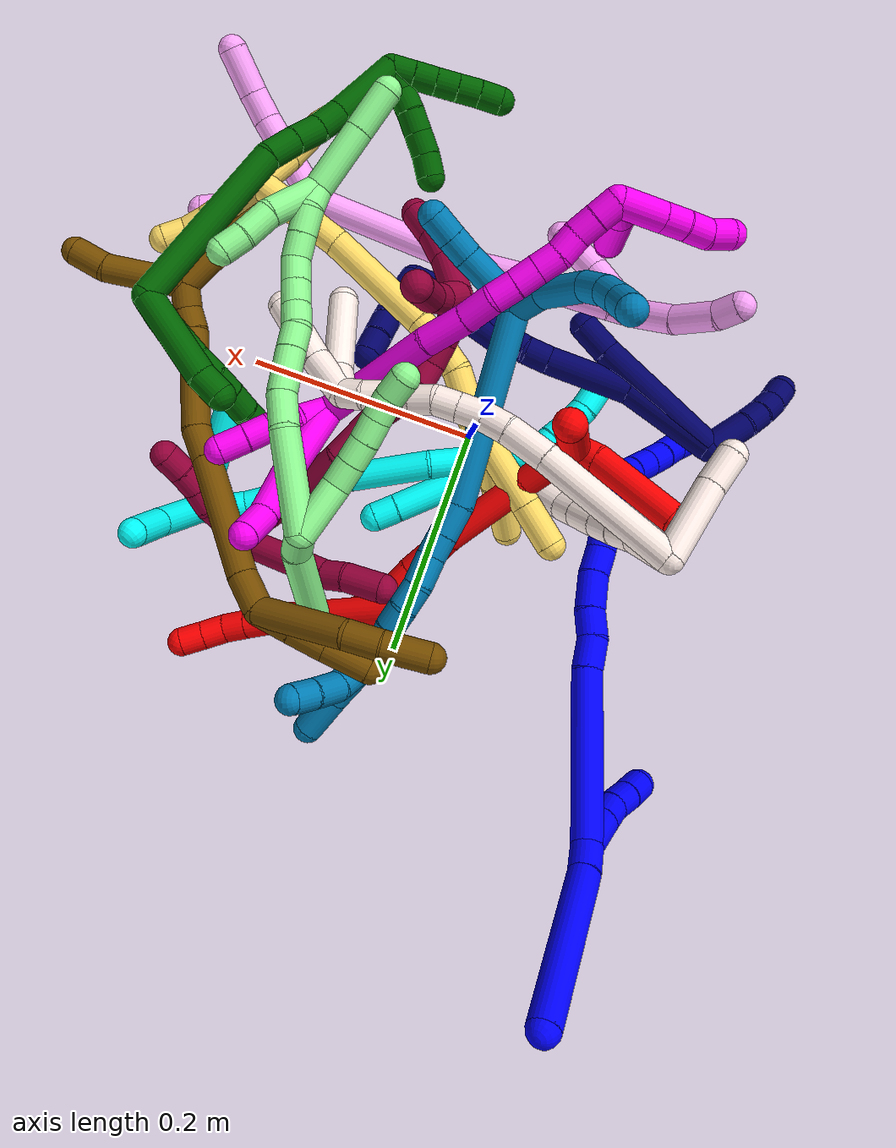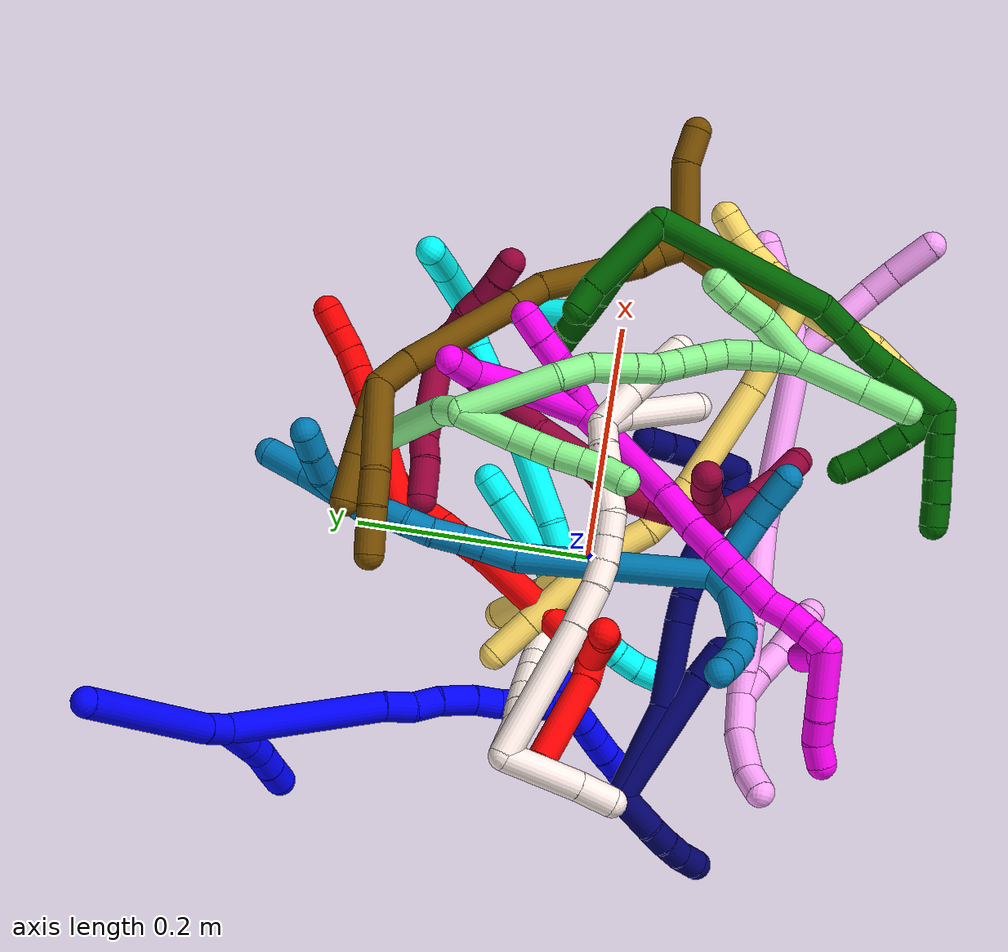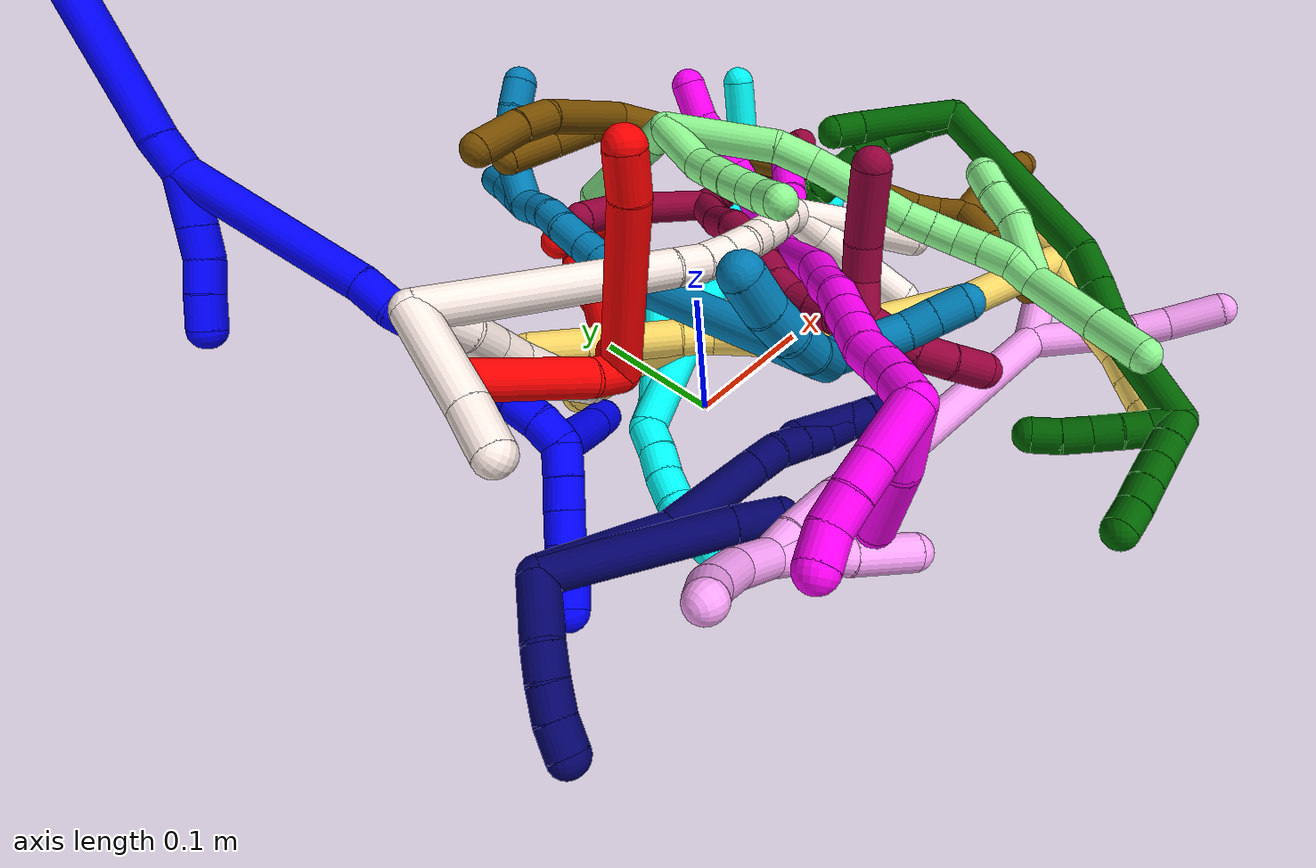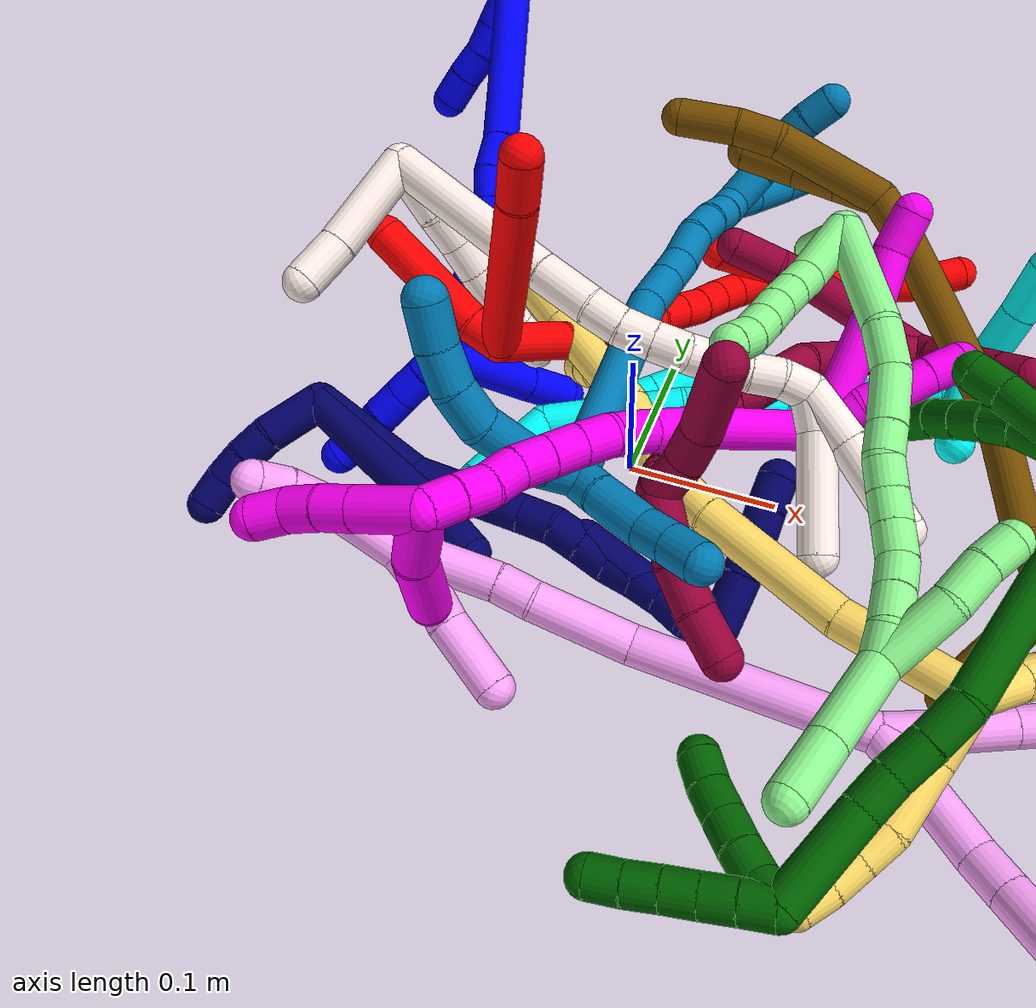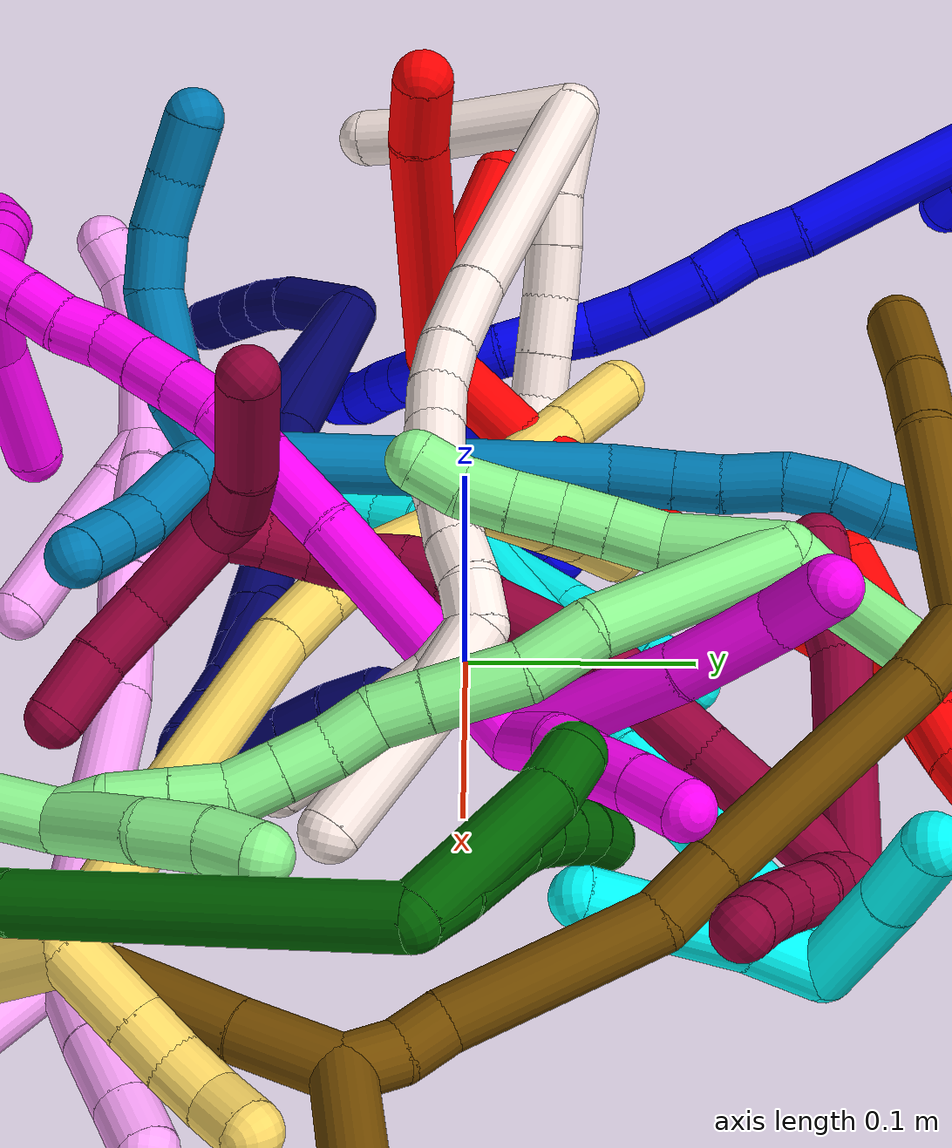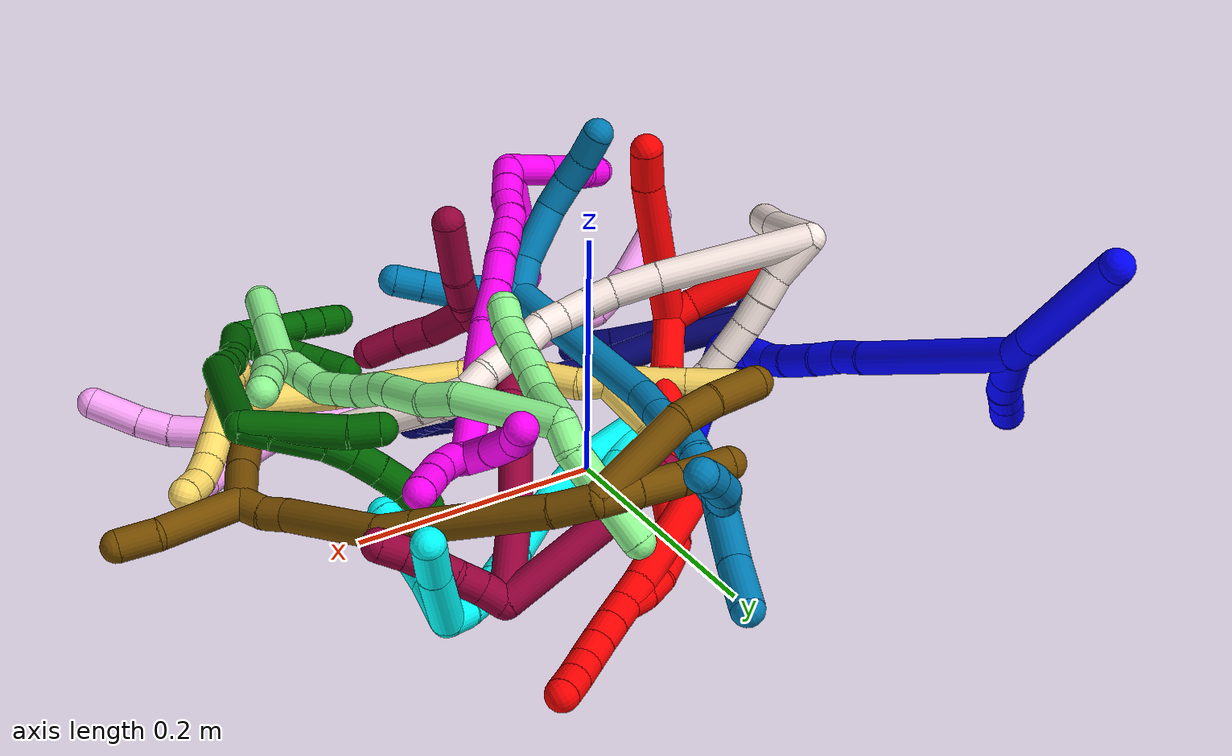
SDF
<sdf version="1.7">
 <world name="default">
  <plugin name="TubeGeneratorPlugin" filename="libtube_generator_plugin.so"/>
  <model name="photoneo_s_sensor">
   <static>1</static>
   <pose>0 0 2 1.57079 1.57079 3.14159</pose>
   <link name="link">
    <inertial><mass>0.1</mass></inertial>
    <sensor name="sensor" type="depth">
     <update_rate>30</update_rate>
     <camera>
      <horizontal_fov>1.22</horizontal_fov>
      <image><width>1920</width><height>1200</height><format>B8G8R8</format></image>
      <clip><near>0.1</near><far>4</far></clip>
      <depth_camera><output>points</output></depth_camera>
     </camera>
     <plugin name="camera_plugin" filename="libgazebo_ros_depth_camera.so">
      <baseline>0.2</baseline>
      <alwaysOn>1</alwaysOn>
      <updateRate>0.0</updateRate>
      <cameraName>camera_ir</cameraName>
      <imageTopicName>/camera/color/image_raw</imageTopicName>
      <cameraInfoTopicName>/camera/color/camera_info</cameraInfoTopicName>
      <depthImageTopicName>/camera/depth/image_raw</depthImageTopicName>
      <depthImageCameraInfoTopicName>/camera/depth/camera_info</depthImageCameraInfoTopicName>
      <pointCloudTopicName>/camera/depth/points</pointCloudTopicName>
      <frameName>fr_optical</frameName>
      <pointCloudCutoff>0.1</pointCloudCutoff>
      <pointCloudCutoffMax>2.0</pointCloudCutoffMax>
      <distortionK1>0</distortionK1>
      <distortionK2>0</distortionK2>
      <distortionK3>0</distortionK3>
      <distortionT1>0</distortionT1>
      <distortionT2>0</distortionT2>
      <CxPrime>0</CxPrime>
      <Cx>0</Cx>
      <Cy>0</Cy>
      <focalLength>0</focalLength>
      <hackBaseline>0</hackBaseline>
     </plugin>
    </sensor>
   </link>
  </model>
  <gravity>0 0 -9.8</gravity>
  <magnetic_field>6e-06 2.3e-05 -4.2e-05</magnetic_field>
  <atmosphere type="adiabatic"/>
  <physics name="default_physics" default="0" type="ode">
   <max_step_size>0.003</max_step_size>
   <real_time_factor>1</real_time_factor>
   <real_time_update_rate>1000</real_time_update_rate>
   <max_contacts>10000</max_contacts>
   <ode>
    <solver>
     <type>quick</type>
     <iters>100</iters>
     <sor>1.3</sor>
     <use_dynamic_moi_rescaling>0</use_dynamic_moi_rescaling>
    </solver>
    <constraints>
     <contact_max_correcting_vel>0</contact_max_correcting_vel>
     <contact_surface_layer>0.001</contact_surface_layer>
     <cfm>0</cfm>
     <erp>0.2</erp>
    </constraints>
   </ode>
  </physics>
  <scene><ambient>0.4 0.4 0.4 1</ambient><background>0.7 0.7 0.7 1</background><shadows>0</shadows></scene>
  <audio><device>default</device></audio>
  <spherical_coordinates>
   <surface_model>EARTH_WGS84</surface_model>
   <latitude_deg>0</latitude_deg>
   <longitude_deg>0</longitude_deg>
   <elevation>0</elevation>
   <heading_deg>0</heading_deg>
  </spherical_coordinates>
  <model name="bin">
   <static>1</static>
   <link name="bottom">
    <collision name="collision-bottom">
     <pose>0 0 -0.01 0 -0 0</pose>
     <geometry><box><size>0.8 0.6 0.02</size></box></geometry>
     <surface>
      <friction><ode><mu>100</mu><mu2>100</mu2></ode></friction>
      <contact><collide_bitmask>65535</collide_bitmask></contact>
     </surface>
    </collision>
   </link>
   <link name="west_wall">
    <collision name="collision-west_wall">
     <pose>-0.41 0 0.1 0 -0 0</pose>
     <geometry><box><size>0.02 0.6 0.2</size></box></geometry>
     <surface>
      <friction><ode><mu>100</mu><mu2>100</mu2></ode></friction>
      <contact><collide_bitmask>65535</collide_bitmask></contact>
     </surface>
    </collision>
   </link>
   <link name="east_wall">
    <collision name="collision-east_wall">
     <pose>0.41 0 0.1 0 -0 0</pose>
     <geometry><box><size>0.02 0.6 0.2</size></box></geometry>
     <surface>
      <friction><ode><mu>100</mu><mu2>100</mu2></ode></friction>
      <contact><collide_bitmask>65535</collide_bitmask></contact>
     </surface>
    </collision>
   </link>
   <link name="south_wall">
    <collision name="collision-south_wall">
     <pose>0 -0.31 0.1 0 -0 0</pose>
     <geometry><box><size>0.8 0.02 0.2</size></box></geometry>
     <surface>
      <friction><ode><mu>100</mu><mu2>100</mu2></ode></friction>
      <contact><collide_bitmask>65535</collide_bitmask></contact>
     </surface>
    </collision>
   </link>
   <link name="north_wall">
    <collision name="collision-north_wall">
     <pose>0 0.31 0.1 0 -0 0</pose>
     <geometry><box><size>0.8 0.02 0.2</size></box></geometry>
     <surface>
      <friction><ode><mu>100</mu><mu2>100</mu2></ode></friction>
      <contact><collide_bitmask>65535</collide_bitmask></contact>
     </surface>
    </collision>
   </link>
  </model>
  <model name="1">
   <static>0</static>
   <link name="1">
    <collision name="collision-cylinder-e_1_2_8">
     <pose>-0.00396 0.003604 0.011257 -0.309803 -0.3233 0.050917</pose>
     <geometry><cylinder><radius>0.0125</radius><length>0.024931</length></cylinder></geometry>
     <surface>
      <friction><ode><mu>1.16</mu><mu2>1.16</mu2><slip1>0</slip1><slip2>0</slip2></ode></friction>
      <contact><ode><kp>1e+06</kp><kd>1</kd><max_vel>0</max_vel><min_depth>0.001</min_depth></ode></contact>
     </surface>
    </collision>
    <visual name="visual-cylinder-e_1_2_8">
     <pose>-0.00396 0.003604 0.011257 -0.309803 -0.3233 0.050917</pose>
     <geometry><cylinder><radius>0.0125</radius><length>0.024931</length></cylinder></geometry>
     <material><ambient>0 0 1 1</ambient></material>
    </visual>
    <collision name="collision-cylinder-e_2_8_6">
     <pose>-0.020121 0.02464 0.081317 -0.288215 -0.196351 0.028583</pose>
     <geometry><cylinder><radius>0.0125</radius><length>0.125069</length></cylinder></geometry>
     <surface>
      <friction><ode><mu>1.16</mu><mu2>1.16</mu2><slip1>0</slip1><slip2>0</slip2></ode></friction>
      <contact><ode><kp>1e+06</kp><kd>1</kd><max_vel>0</max_vel><min_depth>0.001</min_depth></ode></contact>
     </surface>
    </collision>
    <visual name="visual-cylinder-e_2_8_6">
     <pose>-0.020121 0.02464 0.081317 -0.288215 -0.196351 0.028583</pose>
     <geometry><cylinder><radius>0.0125</radius><length>0.125069</length></cylinder></geometry>
     <material><ambient>0 0 1 1</ambient></material>
    </visual>
    <collision name="collision-cylinder-e_1_2_9">
     <pose>0.000825 -0.000219 -0.016717 3.12848 0.049277 2.62161</pose>
     <geometry><cylinder><radius>0.0125</radius><length>0.033478</length></cylinder></geometry>
     <surface>
      <friction><ode><mu>1.16</mu><mu2>1.16</mu2><slip1>0</slip1><slip2>0</slip2></ode></friction>
      <contact><ode><kp>1e+06</kp><kd>1</kd><max_vel>0</max_vel><min_depth>0.001</min_depth></ode></contact>
     </surface>
    </collision>
    <visual name="visual-cylinder-e_1_2_9">
     <pose>0.000825 -0.000219 -0.016717 3.12848 0.049277 2.62161</pose>
     <geometry><cylinder><radius>0.0125</radius><length>0.033478</length></cylinder></geometry>
     <material><ambient>0 0 1 1</ambient></material>
    </visual>
    <collision name="collision-cylinder-e_2_9_10">
     <pose>0.002146 -0.000535 -0.044102 3.13251 0.046534 2.75625</pose>
     <geometry><cylinder><radius>0.0125</radius><length>0.02136</length></cylinder></geometry>
     <surface>
      <friction><ode><mu>1.16</mu><mu2>1.16</mu2><slip1>0</slip1><slip2>0</slip2></ode></friction>
      <contact><ode><kp>1e+06</kp><kd>1</kd><max_vel>0</max_vel><min_depth>0.001</min_depth></ode></contact>
     </surface>
    </collision>
    <visual name="visual-cylinder-e_2_9_10">
     <pose>0.002146 -0.000535 -0.044102 3.13251 0.046534 2.75625</pose>
     <geometry><cylinder><radius>0.0125</radius><length>0.02136</length></cylinder></geometry>
     <material><ambient>0 0 1 1</ambient></material>
    </visual>
    <collision name="collision-cylinder-e_3_10_11">
     <pose>0.000958 5e-05 -0.065563 -3.07848 -0.154483 2.36706</pose>
     <geometry><cylinder><radius>0.0125</radius><length>0.021891</length></cylinder></geometry>
     <surface>
      <friction><ode><mu>1.16</mu><mu2>1.16</mu2><slip1>0</slip1><slip2>0</slip2></ode></friction>
      <contact><ode><kp>1e+06</kp><kd>1</kd><max_vel>0</max_vel><min_depth>0.001</min_depth></ode></contact>
     </surface>
    </collision>
    <visual name="visual-cylinder-e_3_10_11">
     <pose>0.000958 5e-05 -0.065563 -3.07848 -0.154483 2.36706</pose>
     <geometry><cylinder><radius>0.0125</radius><length>0.021891</length></cylinder></geometry>
     <material><ambient>0 0 1 1</ambient></material>
    </visual>
    <collision name="collision-cylinder-e_4_11_5">
     <pose>-0.001654 0.001748 -0.087911 -3.05386 -0.079857 1.47676</pose>
     <geometry><cylinder><radius>0.0125</radius><length>0.023272</length></cylinder></geometry>
     <surface>
      <friction><ode><mu>1.16</mu><mu2>1.16</mu2><slip1>0</slip1><slip2>0</slip2></ode></friction>
      <contact><ode><kp>1e+06</kp><kd>1</kd><max_vel>0</max_vel><min_depth>0.001</min_depth></ode></contact>
     </surface>
    </collision>
    <visual name="visual-cylinder-e_4_11_5">
     <pose>-0.001654 0.001748 -0.087911 -3.05386 -0.079857 1.47676</pose>
     <geometry><cylinder><radius>0.0125</radius><length>0.023272</length></cylinder></geometry>
     <material><ambient>0 0 1 1</ambient></material>
    </visual>
    <collision name="collision-cylinder-e_1_2_12">
     <pose>0.020731 -0.04858 -0.040141 2.26137 0.317821 0.656044</pose>
     <geometry><cylinder><radius>0.0125</radius><length>0.132682</length></cylinder></geometry>
     <surface>
      <friction><ode><mu>1.16</mu><mu2>1.16</mu2><slip1>0</slip1><slip2>0</slip2></ode></friction>
      <contact><ode><kp>1e+06</kp><kd>1</kd><max_vel>0</max_vel><min_depth>0.001</min_depth></ode></contact>
     </surface>
    </collision>
    <visual name="visual-cylinder-e_1_2_12">
     <pose>0.020731 -0.04858 -0.040141 2.26137 0.317821 0.656044</pose>
     <geometry><cylinder><radius>0.0125</radius><length>0.132682</length></cylinder></geometry>
     <material><ambient>0 0 1 1</ambient></material>
    </visual>
    <collision name="collision-cylinder-e_2_12_13">
     <pose>0.043565 -0.106488 -0.089139 2.33023 0.161976 0.373546</pose>
     <geometry><cylinder><radius>0.0125</radius><length>0.026067</length></cylinder></geometry>
     <surface>
      <friction><ode><mu>1.16</mu><mu2>1.16</mu2><slip1>0</slip1><slip2>0</slip2></ode></friction>
      <contact><ode><kp>1e+06</kp><kd>1</kd><max_vel>0</max_vel><min_depth>0.001</min_depth></ode></contact>
     </surface>
    </collision>
    <visual name="visual-cylinder-e_2_12_13">
     <pose>0.043565 -0.106488 -0.089139 2.33023 0.161976 0.373546</pose>
     <geometry><cylinder><radius>0.0125</radius><length>0.026067</length></cylinder></geometry>
     <material><ambient>0 0 1 1</ambient></material>
    </visual>
    <collision name="collision-cylinder-e_3_13_14">
     <pose>0.050381 -0.123936 -0.104802 2.26855 0.418656 0.854591</pose>
     <geometry><cylinder><radius>0.0125</radius><length>0.023194</length></cylinder></geometry>
     <surface>
      <friction><ode><mu>1.16</mu><mu2>1.16</mu2><slip1>0</slip1><slip2>0</slip2></ode></friction>
      <contact><ode><kp>1e+06</kp><kd>1</kd><max_vel>0</max_vel><min_depth>0.001</min_depth></ode></contact>
     </surface>
    </collision>
    <visual name="visual-cylinder-e_3_13_14">
     <pose>0.050381 -0.123936 -0.104802 2.26855 0.418656 0.854591</pose>
     <geometry><cylinder><radius>0.0125</radius><length>0.023194</length></cylinder></geometry>
     <material><ambient>0 0 1 1</ambient></material>
    </visual>
    <collision name="collision-cylinder-e_4_14_15">
     <pose>0.058892 -0.142627 -0.122313 2.36235 0.247205 0.58761</pose>
     <geometry><cylinder><radius>0.0125</radius><length>0.031032</length></cylinder></geometry>
     <surface>
      <friction><ode><mu>1.16</mu><mu2>1.16</mu2><slip1>0</slip1><slip2>0</slip2></ode></friction>
      <contact><ode><kp>1e+06</kp><kd>1</kd><max_vel>0</max_vel><min_depth>0.001</min_depth></ode></contact>
     </surface>
    </collision>
    <visual name="visual-cylinder-e_4_14_15">
     <pose>0.058892 -0.142627 -0.122313 2.36235 0.247205 0.58761</pose>
     <geometry><cylinder><radius>0.0125</radius><length>0.031032</length></cylinder></geometry>
     <material><ambient>0 0 1 1</ambient></material>
    </visual>
    <collision name="collision-cylinder-e_5_15_16">
     <pose>0.063681 -0.161106 -0.142012 2.42054 0.082626 0.218417</pose>
     <geometry><cylinder><radius>0.0125</radius><length>0.024035</length></cylinder></geometry>
     <surface>
      <friction><ode><mu>1.16</mu><mu2>1.16</mu2><slip1>0</slip1><slip2>0</slip2></ode></friction>
      <contact><ode><kp>1e+06</kp><kd>1</kd><max_vel>0</max_vel><min_depth>0.001</min_depth></ode></contact>
     </surface>
    </collision>
    <visual name="visual-cylinder-e_5_15_16">
     <pose>0.063681 -0.161106 -0.142012 2.42054 0.082626 0.218417</pose>
     <geometry><cylinder><radius>0.0125</radius><length>0.024035</length></cylinder></geometry>
     <material><ambient>0 0 1 1</ambient></material>
    </visual>
    <collision name="collision-cylinder-e_6_16_17">
     <pose>0.065466 -0.17788 -0.156444 2.12076 0.07616 0.135878</pose>
     <geometry><cylinder><radius>0.0125</radius><length>0.020862</length></cylinder></geometry>
     <surface>
      <friction><ode><mu>1.16</mu><mu2>1.16</mu2><slip1>0</slip1><slip2>0</slip2></ode></friction>
      <contact><ode><kp>1e+06</kp><kd>1</kd><max_vel>0</max_vel><min_depth>0.001</min_depth></ode></contact>
     </surface>
    </collision>
    <visual name="visual-cylinder-e_6_16_17">
     <pose>0.065466 -0.17788 -0.156444 2.12076 0.07616 0.135878</pose>
     <geometry><cylinder><radius>0.0125</radius><length>0.020862</length></cylinder></geometry>
     <material><ambient>0 0 1 1</ambient></material>
    </visual>
    <collision name="collision-cylinder-e_7_17_18">
     <pose>0.067592 -0.195196 -0.16835 2.22432 0.124544 0.251237</pose>
     <geometry><cylinder><radius>0.0125</radius><length>0.021449</length></cylinder></geometry>
     <surface>
      <friction><ode><mu>1.16</mu><mu2>1.16</mu2><slip1>0</slip1><slip2>0</slip2></ode></friction>
      <contact><ode><kp>1e+06</kp><kd>1</kd><max_vel>0</max_vel><min_depth>0.001</min_depth></ode></contact>
     </surface>
    </collision>
    <visual name="visual-cylinder-e_7_17_18">
     <pose>0.067592 -0.195196 -0.16835 2.22432 0.124544 0.251237</pose>
     <geometry><cylinder><radius>0.0125</radius><length>0.021449</length></cylinder></geometry>
     <material><ambient>0 0 1 1</ambient></material>
    </visual>
    <collision name="collision-cylinder-e_8_18_1">
     <pose>0.069408 -0.210831 -0.182238 2.37209 0.046808 0.115487</pose>
     <geometry><cylinder><radius>0.0125</radius><length>0.020679</length></cylinder></geometry>
     <surface>
      <friction><ode><mu>1.16</mu><mu2>1.16</mu2><slip1>0</slip1><slip2>0</slip2></ode></friction>
      <contact><ode><kp>1e+06</kp><kd>1</kd><max_vel>0</max_vel><min_depth>0.001</min_depth></ode></contact>
     </surface>
    </collision>
    <visual name="visual-cylinder-e_8_18_1">
     <pose>0.069408 -0.210831 -0.182238 2.37209 0.046808 0.115487</pose>
     <geometry><cylinder><radius>0.0125</radius><length>0.020679</length></cylinder></geometry>
     <material><ambient>0 0 1 1</ambient></material>
    </visual>
    <collision name="collision-cylinder-e_1_1_19">
     <pose>0.100052 -0.204193 -0.190977 -1.66608 1.13931 -1.22763</pose>
     <geometry><cylinder><radius>0.0125</radius><length>0.066407</length></cylinder></geometry>
     <surface>
      <friction><ode><mu>1.16</mu><mu2>1.16</mu2><slip1>0</slip1><slip2>0</slip2></ode></friction>
      <contact><ode><kp>1e+06</kp><kd>1</kd><max_vel>0</max_vel><min_depth>0.001</min_depth></ode></contact>
     </surface>
    </collision>
    <visual name="visual-cylinder-e_1_1_19">
     <pose>0.100052 -0.204193 -0.190977 -1.66608 1.13931 -1.22763</pose>
     <geometry><cylinder><radius>0.0125</radius><length>0.066407</length></cylinder></geometry>
     <material><ambient>0 0 1 1</ambient></material>
    </visual>
    <collision name="collision-cylinder-e_2_19_4">
     <pose>0.145293 -0.182982 -0.192658 -1.61943 1.11481 -1.15895</pose>
     <geometry><cylinder><radius>0.0125</radius><length>0.033593</length></cylinder></geometry>
     <surface>
      <friction><ode><mu>1.16</mu><mu2>1.16</mu2><slip1>0</slip1><slip2>0</slip2></ode></friction>
      <contact><ode><kp>1e+06</kp><kd>1</kd><max_vel>0</max_vel><min_depth>0.001</min_depth></ode></contact>
     </surface>
    </collision>
    <visual name="visual-cylinder-e_2_19_4">
     <pose>0.145293 -0.182982 -0.192658 -1.61943 1.11481 -1.15895</pose>
     <geometry><cylinder><radius>0.0125</radius><length>0.033593</length></cylinder></geometry>
     <material><ambient>0 0 1 1</ambient></material>
    </visual>
    <collision name="collision-cylinder-e_1_1_20">
     <pose>0.066927 -0.219699 -0.199058 2.96454 -0.300982 -2.08247</pose>
     <geometry><cylinder><radius>0.0125</radius><length>0.02</length></cylinder></geometry>
     <surface>
      <friction><ode><mu>1.16</mu><mu2>1.16</mu2><slip1>0</slip1><slip2>0</slip2></ode></friction>
      <contact><ode><kp>1e+06</kp><kd>1</kd><max_vel>0</max_vel><min_depth>0.001</min_depth></ode></contact>
     </surface>
    </collision>
    <visual name="visual-cylinder-e_1_1_20">
     <pose>0.066927 -0.219699 -0.199058 2.96454 -0.300982 -2.08247</pose>
     <geometry><cylinder><radius>0.0125</radius><length>0.02</length></cylinder></geometry>
     <material><ambient>0 0 1 1</ambient></material>
    </visual>
    <collision name="collision-cylinder-e_2_20_21">
     <pose>0.061068 -0.222458 -0.21797 3.0288 -0.293701 -2.41234</pose>
     <geometry><cylinder><radius>0.0125</radius><length>0.02</length></cylinder></geometry>
     <surface>
      <friction><ode><mu>1.16</mu><mu2>1.16</mu2><slip1>0</slip1><slip2>0</slip2></ode></friction>
      <contact><ode><kp>1e+06</kp><kd>1</kd><max_vel>0</max_vel><min_depth>0.001</min_depth></ode></contact>
     </surface>
    </collision>
    <visual name="visual-cylinder-e_2_20_21">
     <pose>0.061068 -0.222458 -0.21797 3.0288 -0.293701 -2.41234</pose>
     <geometry><cylinder><radius>0.0125</radius><length>0.02</length></cylinder></geometry>
     <material><ambient>0 0 1 1</ambient></material>
    </visual>
    <collision name="collision-cylinder-e_3_21_22">
     <pose>0.055377 -0.22481 -0.236997 3.00845 -0.283399 -2.26722</pose>
     <geometry><cylinder><radius>0.0125</radius><length>0.02</length></cylinder></geometry>
     <surface>
      <friction><ode><mu>1.16</mu><mu2>1.16</mu2><slip1>0</slip1><slip2>0</slip2></ode></friction>
      <contact><ode><kp>1e+06</kp><kd>1</kd><max_vel>0</max_vel><min_depth>0.001</min_depth></ode></contact>
     </surface>
    </collision>
    <visual name="visual-cylinder-e_3_21_22">
     <pose>0.055377 -0.22481 -0.236997 3.00845 -0.283399 -2.26722</pose>
     <geometry><cylinder><radius>0.0125</radius><length>0.02</length></cylinder></geometry>
     <material><ambient>0 0 1 1</ambient></material>
    </visual>
    <collision name="collision-cylinder-e_4_22_23">
     <pose>0.050915 -0.227248 -0.256304 3.02336 -0.167308 -1.91232</pose>
     <geometry><cylinder><radius>0.0125</radius><length>0.02</length></cylinder></geometry>
     <surface>
      <friction><ode><mu>1.16</mu><mu2>1.16</mu2><slip1>0</slip1><slip2>0</slip2></ode></friction>
      <contact><ode><kp>1e+06</kp><kd>1</kd><max_vel>0</max_vel><min_depth>0.001</min_depth></ode></contact>
     </surface>
    </collision>
    <visual name="visual-cylinder-e_4_22_23">
     <pose>0.050915 -0.227248 -0.256304 3.02336 -0.167308 -1.91232</pose>
     <geometry><cylinder><radius>0.0125</radius><length>0.02</length></cylinder></geometry>
     <material><ambient>0 0 1 1</ambient></material>
    </visual>
    <collision name="collision-cylinder-e_5_23_3">
     <pose>0.045071 -0.230476 -0.274943 2.9123 -0.431133 -2.17334</pose>
     <geometry><cylinder><radius>0.0125</radius><length>0.02</length></cylinder></geometry>
     <surface>
      <friction><ode><mu>1.16</mu><mu2>1.16</mu2><slip1>0</slip1><slip2>0</slip2></ode></friction>
      <contact><ode><kp>1e+06</kp><kd>1</kd><max_vel>0</max_vel><min_depth>0.001</min_depth></ode></contact>
     </surface>
    </collision>
    <visual name="visual-cylinder-e_5_23_3">
     <pose>0.045071 -0.230476 -0.274943 2.9123 -0.431133 -2.17334</pose>
     <geometry><cylinder><radius>0.0125</radius><length>0.02</length></cylinder></geometry>
     <material><ambient>0 0 1 1</ambient></material>
    </visual>
    <collision name="collision-sphere-3">
     <pose>0.040892 -0.232541 -0.28379 0 -0 0</pose>
     <geometry><sphere><radius>0.0125</radius></sphere></geometry>
     <surface>
      <friction><ode><mu>1.16</mu><mu2>1.16</mu2><slip1>0</slip1><slip2>0</slip2></ode></friction>
      <contact><ode><kp>1e+06</kp><kd>1</kd><max_vel>0</max_vel><min_depth>0.001</min_depth></ode></contact>
     </surface>
    </collision>
    <visual name="visual-sphere-3">
     <pose>0.040892 -0.232541 -0.28379 0 -0 0</pose>
     <geometry><sphere><radius>0.0125</radius></sphere></geometry>
     <material><ambient>0 0 1 1</ambient></material>
    </visual>
    <collision name="collision-sphere-23">
     <pose>0.04925 -0.228411 -0.266096 0 -0 0</pose>
     <geometry><sphere><radius>0.0125</radius></sphere></geometry>
     <surface>
      <friction><ode><mu>1.16</mu><mu2>1.16</mu2><slip1>0</slip1><slip2>0</slip2></ode></friction>
      <contact><ode><kp>1e+06</kp><kd>1</kd><max_vel>0</max_vel><min_depth>0.001</min_depth></ode></contact>
     </surface>
    </collision>
    <visual name="visual-sphere-23">
     <pose>0.04925 -0.228411 -0.266096 0 -0 0</pose>
     <geometry><sphere><radius>0.0125</radius></sphere></geometry>
     <material><ambient>0 0 1 1</ambient></material>
    </visual>
    <collision name="collision-sphere-22">
     <pose>0.052581 -0.226085 -0.246513 0 -0 0</pose>
     <geometry><sphere><radius>0.0125</radius></sphere></geometry>
     <surface>
      <friction><ode><mu>1.16</mu><mu2>1.16</mu2><slip1>0</slip1><slip2>0</slip2></ode></friction>
      <contact><ode><kp>1e+06</kp><kd>1</kd><max_vel>0</max_vel><min_depth>0.001</min_depth></ode></contact>
     </surface>
    </collision>
    <visual name="visual-sphere-22">
     <pose>0.052581 -0.226085 -0.246513 0 -0 0</pose>
     <geometry><sphere><radius>0.0125</radius></sphere></geometry>
     <material><ambient>0 0 1 1</ambient></material>
    </visual>
    <collision name="collision-sphere-21">
     <pose>0.058173 -0.223536 -0.227481 0 -0 0</pose>
     <geometry><sphere><radius>0.0125</radius></sphere></geometry>
     <surface>
      <friction><ode><mu>1.16</mu><mu2>1.16</mu2><slip1>0</slip1><slip2>0</slip2></ode></friction>
      <contact><ode><kp>1e+06</kp><kd>1</kd><max_vel>0</max_vel><min_depth>0.001</min_depth></ode></contact>
     </surface>
    </collision>
    <visual name="visual-sphere-21">
     <pose>0.058173 -0.223536 -0.227481 0 -0 0</pose>
     <geometry><sphere><radius>0.0125</radius></sphere></geometry>
     <material><ambient>0 0 1 1</ambient></material>
    </visual>
    <collision name="collision-sphere-20">
     <pose>0.063963 -0.221381 -0.208459 0 -0 0</pose>
     <geometry><sphere><radius>0.0125</radius></sphere></geometry>
     <surface>
      <friction><ode><mu>1.16</mu><mu2>1.16</mu2><slip1>0</slip1><slip2>0</slip2></ode></friction>
      <contact><ode><kp>1e+06</kp><kd>1</kd><max_vel>0</max_vel><min_depth>0.001</min_depth></ode></contact>
     </surface>
    </collision>
    <visual name="visual-sphere-20">
     <pose>0.063963 -0.221381 -0.208459 0 -0 0</pose>
     <geometry><sphere><radius>0.0125</radius></sphere></geometry>
     <material><ambient>0 0 1 1</ambient></material>
    </visual>
    <collision name="collision-sphere-4">
     <pose>0.160373 -0.175595 -0.193018 0 -0 0</pose>
     <geometry><sphere><radius>0.0125</radius></sphere></geometry>
     <surface>
      <friction><ode><mu>1.16</mu><mu2>1.16</mu2><slip1>0</slip1><slip2>0</slip2></ode></friction>
      <contact><ode><kp>1e+06</kp><kd>1</kd><max_vel>0</max_vel><min_depth>0.001</min_depth></ode></contact>
     </surface>
    </collision>
    <visual name="visual-sphere-4">
     <pose>0.160373 -0.175595 -0.193018 0 -0 0</pose>
     <geometry><sphere><radius>0.0125</radius></sphere></geometry>
     <material><ambient>0 0 1 1</ambient></material>
    </visual>
    <collision name="collision-sphere-11">
     <pose>-0.000726 0.000732 -0.076357 0 -0 0</pose>
     <geometry><sphere><radius>0.0125</radius></sphere></geometry>
     <surface>
      <friction><ode><mu>1.16</mu><mu2>1.16</mu2><slip1>0</slip1><slip2>0</slip2></ode></friction>
      <contact><ode><kp>1e+06</kp><kd>1</kd><max_vel>0</max_vel><min_depth>0.001</min_depth></ode></contact>
     </surface>
    </collision>
    <visual name="visual-sphere-11">
     <pose>-0.000726 0.000732 -0.076357 0 -0 0</pose>
     <geometry><sphere><radius>0.0125</radius></sphere></geometry>
     <material><ambient>0 0 1 1</ambient></material>
    </visual>
    <collision name="collision-sphere-10">
     <pose>0.002643 -0.000632 -0.05477 0 -0 0</pose>
     <geometry><sphere><radius>0.0125</radius></sphere></geometry>
     <surface>
      <friction><ode><mu>1.16</mu><mu2>1.16</mu2><slip1>0</slip1><slip2>0</slip2></ode></friction>
      <contact><ode><kp>1e+06</kp><kd>1</kd><max_vel>0</max_vel><min_depth>0.001</min_depth></ode></contact>
     </surface>
    </collision>
    <visual name="visual-sphere-10">
     <pose>0.002643 -0.000632 -0.05477 0 -0 0</pose>
     <geometry><sphere><radius>0.0125</radius></sphere></geometry>
     <material><ambient>0 0 1 1</ambient></material>
    </visual>
    <collision name="collision-sphere-6">
     <pose>-0.032321 0.042074 0.14012 0 -0 0</pose>
     <geometry><sphere><radius>0.0125</radius></sphere></geometry>
     <surface>
      <friction><ode><mu>1.16</mu><mu2>1.16</mu2><slip1>0</slip1><slip2>0</slip2></ode></friction>
      <contact><ode><kp>1e+06</kp><kd>1</kd><max_vel>0</max_vel><min_depth>0.001</min_depth></ode></contact>
     </surface>
    </collision>
    <visual name="visual-sphere-6">
     <pose>-0.032321 0.042074 0.14012 0 -0 0</pose>
     <geometry><sphere><radius>0.0125</radius></sphere></geometry>
     <material><ambient>0 0 1 1</ambient></material>
    </visual>
    <collision name="collision-sphere-9">
     <pose>0.001649 -0.000438 -0.033434 0 -0 0</pose>
     <geometry><sphere><radius>0.0125</radius></sphere></geometry>
     <surface>
      <friction><ode><mu>1.16</mu><mu2>1.16</mu2><slip1>0</slip1><slip2>0</slip2></ode></friction>
      <contact><ode><kp>1e+06</kp><kd>1</kd><max_vel>0</max_vel><min_depth>0.001</min_depth></ode></contact>
     </surface>
    </collision>
    <visual name="visual-sphere-9">
     <pose>0.001649 -0.000438 -0.033434 0 -0 0</pose>
     <geometry><sphere><radius>0.0125</radius></sphere></geometry>
     <material><ambient>0 0 1 1</ambient></material>
    </visual>
    <collision name="collision-sphere-2">
     <geometry><sphere><radius>0.0125</radius></sphere></geometry>
     <surface>
      <friction><ode><mu>1.16</mu><mu2>1.16</mu2><slip1>0</slip1><slip2>0</slip2></ode></friction>
      <contact><ode><kp>1e+06</kp><kd>1</kd><max_vel>0</max_vel><min_depth>0.001</min_depth></ode></contact>
     </surface>
    </collision>
    <visual name="visual-sphere-2">
     <geometry><sphere><radius>0.0125</radius></sphere></geometry>
     <material><ambient>0 0 1 1</ambient></material>
    </visual>
    <collision name="collision-sphere-19">
     <pose>0.130213 -0.19037 -0.192299 0 -0 0</pose>
     <geometry><sphere><radius>0.0125</radius></sphere></geometry>
     <surface>
      <friction><ode><mu>1.16</mu><mu2>1.16</mu2><slip1>0</slip1><slip2>0</slip2></ode></friction>
      <contact><ode><kp>1e+06</kp><kd>1</kd><max_vel>0</max_vel><min_depth>0.001</min_depth></ode></contact>
     </surface>
    </collision>
    <visual name="visual-sphere-19">
     <pose>0.130213 -0.19037 -0.192299 0 -0 0</pose>
     <geometry><sphere><radius>0.0125</radius></sphere></geometry>
     <material><ambient>0 0 1 1</ambient></material>
    </visual>
    <collision name="collision-sphere-8">
     <pose>-0.007921 0.007207 0.022514 0 -0 0</pose>
     <geometry><sphere><radius>0.0125</radius></sphere></geometry>
     <surface>
      <friction><ode><mu>1.16</mu><mu2>1.16</mu2><slip1>0</slip1><slip2>0</slip2></ode></friction>
      <contact><ode><kp>1e+06</kp><kd>1</kd><max_vel>0</max_vel><min_depth>0.001</min_depth></ode></contact>
     </surface>
    </collision>
    <visual name="visual-sphere-8">
     <pose>-0.007921 0.007207 0.022514 0 -0 0</pose>
     <geometry><sphere><radius>0.0125</radius></sphere></geometry>
     <material><ambient>0 0 1 1</ambient></material>
    </visual>
    <collision name="collision-sphere-5">
     <pose>-0.002582 0.002765 -0.099465 0 -0 0</pose>
     <geometry><sphere><radius>0.0125</radius></sphere></geometry>
     <surface>
      <friction><ode><mu>1.16</mu><mu2>1.16</mu2><slip1>0</slip1><slip2>0</slip2></ode></friction>
      <contact><ode><kp>1e+06</kp><kd>1</kd><max_vel>0</max_vel><min_depth>0.001</min_depth></ode></contact>
     </surface>
    </collision>
    <visual name="visual-sphere-5">
     <pose>-0.002582 0.002765 -0.099465 0 -0 0</pose>
     <geometry><sphere><radius>0.0125</radius></sphere></geometry>
     <material><ambient>0 0 1 1</ambient></material>
    </visual>
    <collision name="collision-sphere-12">
     <pose>0.041463 -0.09716 -0.080282 0 -0 0</pose>
     <geometry><sphere><radius>0.0125</radius></sphere></geometry>
     <surface>
      <friction><ode><mu>1.16</mu><mu2>1.16</mu2><slip1>0</slip1><slip2>0</slip2></ode></friction>
      <contact><ode><kp>1e+06</kp><kd>1</kd><max_vel>0</max_vel><min_depth>0.001</min_depth></ode></contact>
     </surface>
    </collision>
    <visual name="visual-sphere-12">
     <pose>0.041463 -0.09716 -0.080282 0 -0 0</pose>
     <geometry><sphere><radius>0.0125</radius></sphere></geometry>
     <material><ambient>0 0 1 1</ambient></material>
    </visual>
    <collision name="collision-sphere-13">
     <pose>0.045666 -0.115817 -0.097995 0 -0 0</pose>
     <geometry><sphere><radius>0.0125</radius></sphere></geometry>
     <surface>
      <friction><ode><mu>1.16</mu><mu2>1.16</mu2><slip1>0</slip1><slip2>0</slip2></ode></friction>
      <contact><ode><kp>1e+06</kp><kd>1</kd><max_vel>0</max_vel><min_depth>0.001</min_depth></ode></contact>
     </surface>
    </collision>
    <visual name="visual-sphere-13">
     <pose>0.045666 -0.115817 -0.097995 0 -0 0</pose>
     <geometry><sphere><radius>0.0125</radius></sphere></geometry>
     <material><ambient>0 0 1 1</ambient></material>
    </visual>
    <collision name="collision-sphere-14">
     <pose>0.055096 -0.132055 -0.11161 0 -0 0</pose>
     <geometry><sphere><radius>0.0125</radius></sphere></geometry>
     <surface>
      <friction><ode><mu>1.16</mu><mu2>1.16</mu2><slip1>0</slip1><slip2>0</slip2></ode></friction>
      <contact><ode><kp>1e+06</kp><kd>1</kd><max_vel>0</max_vel><min_depth>0.001</min_depth></ode></contact>
     </surface>
    </collision>
    <visual name="visual-sphere-14">
     <pose>0.055096 -0.132055 -0.11161 0 -0 0</pose>
     <geometry><sphere><radius>0.0125</radius></sphere></geometry>
     <material><ambient>0 0 1 1</ambient></material>
    </visual>
    <collision name="collision-sphere-15">
     <pose>0.062689 -0.1532 -0.133017 0 -0 0</pose>
     <geometry><sphere><radius>0.0125</radius></sphere></geometry>
     <surface>
      <friction><ode><mu>1.16</mu><mu2>1.16</mu2><slip1>0</slip1><slip2>0</slip2></ode></friction>
      <contact><ode><kp>1e+06</kp><kd>1</kd><max_vel>0</max_vel><min_depth>0.001</min_depth></ode></contact>
     </surface>
    </collision>
    <visual name="visual-sphere-15">
     <pose>0.062689 -0.1532 -0.133017 0 -0 0</pose>
     <geometry><sphere><radius>0.0125</radius></sphere></geometry>
     <material><ambient>0 0 1 1</ambient></material>
    </visual>
    <collision name="collision-sphere-16">
     <pose>0.064673 -0.169013 -0.151008 0 -0 0</pose>
     <geometry><sphere><radius>0.0125</radius></sphere></geometry>
     <surface>
      <friction><ode><mu>1.16</mu><mu2>1.16</mu2><slip1>0</slip1><slip2>0</slip2></ode></friction>
      <contact><ode><kp>1e+06</kp><kd>1</kd><max_vel>0</max_vel><min_depth>0.001</min_depth></ode></contact>
     </surface>
    </collision>
    <visual name="visual-sphere-16">
     <pose>0.064673 -0.169013 -0.151008 0 -0 0</pose>
     <geometry><sphere><radius>0.0125</radius></sphere></geometry>
     <material><ambient>0 0 1 1</ambient></material>
    </visual>
    <collision name="collision-sphere-17">
     <pose>0.06626 -0.186747 -0.16188 0 -0 0</pose>
     <geometry><sphere><radius>0.0125</radius></sphere></geometry>
     <surface>
      <friction><ode><mu>1.16</mu><mu2>1.16</mu2><slip1>0</slip1><slip2>0</slip2></ode></friction>
      <contact><ode><kp>1e+06</kp><kd>1</kd><max_vel>0</max_vel><min_depth>0.001</min_depth></ode></contact>
     </surface>
    </collision>
    <visual name="visual-sphere-17">
     <pose>0.06626 -0.186747 -0.16188 0 -0 0</pose>
     <geometry><sphere><radius>0.0125</radius></sphere></geometry>
     <material><ambient>0 0 1 1</ambient></material>
    </visual>
    <collision name="collision-sphere-18">
     <pose>0.068924 -0.203644 -0.174819 0 -0 0</pose>
     <geometry><sphere><radius>0.0125</radius></sphere></geometry>
     <surface>
      <friction><ode><mu>1.16</mu><mu2>1.16</mu2><slip1>0</slip1><slip2>0</slip2></ode></friction>
      <contact><ode><kp>1e+06</kp><kd>1</kd><max_vel>0</max_vel><min_depth>0.001</min_depth></ode></contact>
     </surface>
    </collision>
    <visual name="visual-sphere-18">
     <pose>0.068924 -0.203644 -0.174819 0 -0 0</pose>
     <geometry><sphere><radius>0.0125</radius></sphere></geometry>
     <material><ambient>0 0 1 1</ambient></material>
    </visual>
    <collision name="collision-sphere-1">
     <pose>0.069892 -0.218017 -0.189656 0 -0 0</pose>
     <geometry><sphere><radius>0.0125</radius></sphere></geometry>
     <surface>
      <friction><ode><mu>1.16</mu><mu2>1.16</mu2><slip1>0</slip1><slip2>0</slip2></ode></friction>
      <contact><ode><kp>1e+06</kp><kd>1</kd><max_vel>0</max_vel><min_depth>0.001</min_depth></ode></contact>
     </surface>
    </collision>
    <visual name="visual-sphere-1">
     <pose>0.069892 -0.218017 -0.189656 0 -0 0</pose>
     <geometry><sphere><radius>0.0125</radius></sphere></geometry>
     <material><ambient>0 0 1 1</ambient></material>
    </visual>
    <inertial>
     <pose>0.036289 -0.095544 -0.087099 0 -0 0</pose>
     <mass>0.75</mass>
     <inertia><ixx>0.000446</ixx><ixy>0</ixy><ixz>0</ixz><iyy>0.000223</iyy><iyz>0</iyz><izz>2e-05</izz></inertia>
    </inertial>
   </link>
   <pose>-0.182302 0.266721 0.178958 -0.411257 0.471017 0.11315</pose>
  </model>
  <model name="2">
   <static>0</static>
   <link name="2">
    <collision name="collision-cylinder-e_1_2_8">
     <pose>-0.049866 0.032482 -0.009066 -1.84299 -0.976168 1.22067</pose>
     <geometry><cylinder><radius>0.0125</radius><length>0.120398</length></cylinder></geometry>
     <surface>
      <friction><ode><mu>1.16</mu><mu2>1.16</mu2><slip1>0</slip1><slip2>0</slip2></ode></friction>
      <contact><ode><kp>1e+06</kp><kd>1</kd><max_vel>0</max_vel><min_depth>0.001</min_depth></ode></contact>
     </surface>
    </collision>
    <visual name="visual-cylinder-e_1_2_8">
     <pose>-0.049866 0.032482 -0.009066 -1.84299 -0.976168 1.22067</pose>
     <geometry><cylinder><radius>0.0125</radius><length>0.120398</length></cylinder></geometry>
     <material><ambient>1 0 0 1</ambient></material>
    </visual>
    <collision name="collision-cylinder-e_2_8_6">
     <pose>-0.110868 0.074091 -0.021562 -1.93022 -0.851611 1.15968</pose>
     <geometry><cylinder><radius>0.0125</radius><length>0.029602</length></cylinder></geometry>
     <surface>
      <friction><ode><mu>1.16</mu><mu2>1.16</mu2><slip1>0</slip1><slip2>0</slip2></ode></friction>
      <contact><ode><kp>1e+06</kp><kd>1</kd><max_vel>0</max_vel><min_depth>0.001</min_depth></ode></contact>
     </surface>
    </collision>
    <visual name="visual-cylinder-e_2_8_6">
     <pose>-0.110868 0.074091 -0.021562 -1.93022 -0.851611 1.15968</pose>
     <geometry><cylinder><radius>0.0125</radius><length>0.029602</length></cylinder></geometry>
     <material><ambient>1 0 0 1</ambient></material>
    </visual>
    <collision name="collision-cylinder-e_1_2_9">
     <pose>-0.0008 0.000596 -0.010749 -3.08623 -0.074178 1.8594</pose>
     <geometry><cylinder><radius>0.0125</radius><length>0.02159</length></cylinder></geometry>
     <surface>
      <friction><ode><mu>1.16</mu><mu2>1.16</mu2><slip1>0</slip1><slip2>0</slip2></ode></friction>
      <contact><ode><kp>1e+06</kp><kd>1</kd><max_vel>0</max_vel><min_depth>0.001</min_depth></ode></contact>
     </surface>
    </collision>
    <visual name="visual-cylinder-e_1_2_9">
     <pose>-0.0008 0.000596 -0.010749 -3.08623 -0.074178 1.8594</pose>
     <geometry><cylinder><radius>0.0125</radius><length>0.02159</length></cylinder></geometry>
     <material><ambient>1 0 0 1</ambient></material>
    </visual>
    <collision name="collision-cylinder-e_2_9_5">
     <pose>0.000216 0.010724 -0.059483 -2.89571 0.046336 -0.370758</pose>
     <geometry><cylinder><radius>0.0125</radius><length>0.07841</length></cylinder></geometry>
     <surface>
      <friction><ode><mu>1.16</mu><mu2>1.16</mu2><slip1>0</slip1><slip2>0</slip2></ode></friction>
      <contact><ode><kp>1e+06</kp><kd>1</kd><max_vel>0</max_vel><min_depth>0.001</min_depth></ode></contact>
     </surface>
    </collision>
    <visual name="visual-cylinder-e_2_9_5">
     <pose>0.000216 0.010724 -0.059483 -2.89571 0.046336 -0.370758</pose>
     <geometry><cylinder><radius>0.0125</radius><length>0.07841</length></cylinder></geometry>
     <material><ambient>1 0 0 1</ambient></material>
    </visual>
    <collision name="collision-cylinder-e_1_2_10">
     <pose>0.018277 0.012654 0.014366 -0.722138 0.762226 -0.300352</pose>
     <geometry><cylinder><radius>0.0125</radius><length>0.052937</length></cylinder></geometry>
     <surface>
      <friction><ode><mu>1.16</mu><mu2>1.16</mu2><slip1>0</slip1><slip2>0</slip2></ode></friction>
      <contact><ode><kp>1e+06</kp><kd>1</kd><max_vel>0</max_vel><min_depth>0.001</min_depth></ode></contact>
     </surface>
    </collision>
    <visual name="visual-cylinder-e_1_2_10">
     <pose>0.018277 0.012654 0.014366 -0.722138 0.762226 -0.300352</pose>
     <geometry><cylinder><radius>0.0125</radius><length>0.052937</length></cylinder></geometry>
     <material><ambient>1 0 0 1</ambient></material>
    </visual>
    <collision name="collision-cylinder-e_2_10_11">
     <pose>0.060689 0.050942 0.049173 -0.897629 0.63457 -0.313692</pose>
     <geometry><cylinder><radius>0.0125</radius><length>0.081421</length></cylinder></geometry>
     <surface>
      <friction><ode><mu>1.16</mu><mu2>1.16</mu2><slip1>0</slip1><slip2>0</slip2></ode></friction>
      <contact><ode><kp>1e+06</kp><kd>1</kd><max_vel>0</max_vel><min_depth>0.001</min_depth></ode></contact>
     </surface>
    </collision>
    <visual name="visual-cylinder-e_2_10_11">
     <pose>0.060689 0.050942 0.049173 -0.897629 0.63457 -0.313692</pose>
     <geometry><cylinder><radius>0.0125</radius><length>0.081421</length></cylinder></geometry>
     <material><ambient>1 0 0 1</ambient></material>
    </visual>
    <collision name="collision-cylinder-e_3_11_12">
     <pose>0.092897 0.083655 0.074447 -0.971757 0.755402 -0.413076</pose>
     <geometry><cylinder><radius>0.0125</radius><length>0.023551</length></cylinder></geometry>
     <surface>
      <friction><ode><mu>1.16</mu><mu2>1.16</mu2><slip1>0</slip1><slip2>0</slip2></ode></friction>
      <contact><ode><kp>1e+06</kp><kd>1</kd><max_vel>0</max_vel><min_depth>0.001</min_depth></ode></contact>
     </surface>
    </collision>
    <visual name="visual-cylinder-e_3_11_12">
     <pose>0.092897 0.083655 0.074447 -0.971757 0.755402 -0.413076</pose>
     <geometry><cylinder><radius>0.0125</radius><length>0.023551</length></cylinder></geometry>
     <material><ambient>1 0 0 1</ambient></material>
    </visual>
    <collision name="collision-cylinder-e_4_12_13">
     <pose>0.107755 0.097059 0.084016 -0.928004 0.709605 -0.366645</pose>
     <geometry><cylinder><radius>0.0125</radius><length>0.020829</length></cylinder></geometry>
     <surface>
      <friction><ode><mu>1.16</mu><mu2>1.16</mu2><slip1>0</slip1><slip2>0</slip2></ode></friction>
      <contact><ode><kp>1e+06</kp><kd>1</kd><max_vel>0</max_vel><min_depth>0.001</min_depth></ode></contact>
     </surface>
    </collision>
    <visual name="visual-cylinder-e_4_12_13">
     <pose>0.107755 0.097059 0.084016 -0.928004 0.709605 -0.366645</pose>
     <geometry><cylinder><radius>0.0125</radius><length>0.020829</length></cylinder></geometry>
     <material><ambient>1 0 0 1</ambient></material>
    </visual>
    <collision name="collision-cylinder-e_5_13_14">
     <pose>0.121229 0.110557 0.092376 -1.10306 0.694049 -0.437865</pose>
     <geometry><cylinder><radius>0.0125</radius><length>0.020913</length></cylinder></geometry>
     <surface>
      <friction><ode><mu>1.16</mu><mu2>1.16</mu2><slip1>0</slip1><slip2>0</slip2></ode></friction>
      <contact><ode><kp>1e+06</kp><kd>1</kd><max_vel>0</max_vel><min_depth>0.001</min_depth></ode></contact>
     </surface>
    </collision>
    <visual name="visual-cylinder-e_5_13_14">
     <pose>0.121229 0.110557 0.092376 -1.10306 0.694049 -0.437865</pose>
     <geometry><cylinder><radius>0.0125</radius><length>0.020913</length></cylinder></geometry>
     <material><ambient>1 0 0 1</ambient></material>
    </visual>
    <collision name="collision-cylinder-e_6_14_15">
     <pose>0.133505 0.124785 0.100584 -0.994563 0.586259 -0.324762</pose>
     <geometry><cylinder><radius>0.0125</radius><length>0.020199</length></cylinder></geometry>
     <surface>
      <friction><ode><mu>1.16</mu><mu2>1.16</mu2><slip1>0</slip1><slip2>0</slip2></ode></friction>
      <contact><ode><kp>1e+06</kp><kd>1</kd><max_vel>0</max_vel><min_depth>0.001</min_depth></ode></contact>
     </surface>
    </collision>
    <visual name="visual-cylinder-e_6_14_15">
     <pose>0.133505 0.124785 0.100584 -0.994563 0.586259 -0.324762</pose>
     <geometry><cylinder><radius>0.0125</radius><length>0.020199</length></cylinder></geometry>
     <material><ambient>1 0 0 1</ambient></material>
    </visual>
    <collision name="collision-cylinder-e_7_15_16">
     <pose>0.141887 0.139587 0.110937 -0.930681 0.281643 -0.142121</pose>
     <geometry><cylinder><radius>0.0125</radius><length>0.020113</length></cylinder></geometry>
     <surface>
      <friction><ode><mu>1.16</mu><mu2>1.16</mu2><slip1>0</slip1><slip2>0</slip2></ode></friction>
      <contact><ode><kp>1e+06</kp><kd>1</kd><max_vel>0</max_vel><min_depth>0.001</min_depth></ode></contact>
     </surface>
    </collision>
    <visual name="visual-cylinder-e_7_15_16">
     <pose>0.141887 0.139587 0.110937 -0.930681 0.281643 -0.142121</pose>
     <geometry><cylinder><radius>0.0125</radius><length>0.020113</length></cylinder></geometry>
     <material><ambient>1 0 0 1</ambient></material>
    </visual>
    <collision name="collision-cylinder-e_8_16_17">
     <pose>0.148383 0.153002 0.124084 -0.655095 0.378681 -0.130047</pose>
     <geometry><cylinder><radius>0.0125</radius><length>0.020023</length></cylinder></geometry>
     <surface>
      <friction><ode><mu>1.16</mu><mu2>1.16</mu2><slip1>0</slip1><slip2>0</slip2></ode></friction>
      <contact><ode><kp>1e+06</kp><kd>1</kd><max_vel>0</max_vel><min_depth>0.001</min_depth></ode></contact>
     </surface>
    </collision>
    <visual name="visual-cylinder-e_8_16_17">
     <pose>0.148383 0.153002 0.124084 -0.655095 0.378681 -0.130047</pose>
     <geometry><cylinder><radius>0.0125</radius><length>0.020023</length></cylinder></geometry>
     <material><ambient>1 0 0 1</ambient></material>
    </visual>
    <collision name="collision-cylinder-e_9_17_18">
     <pose>0.153904 0.16333 0.140123 -0.493618 0.182908 -0.046204</pose>
     <geometry><cylinder><radius>0.0125</radius><length>0.020007</length></cylinder></geometry>
     <surface>
      <friction><ode><mu>1.16</mu><mu2>1.16</mu2><slip1>0</slip1><slip2>0</slip2></ode></friction>
      <contact><ode><kp>1e+06</kp><kd>1</kd><max_vel>0</max_vel><min_depth>0.001</min_depth></ode></contact>
     </surface>
    </collision>
    <visual name="visual-cylinder-e_9_17_18">
     <pose>0.153904 0.16333 0.140123 -0.493618 0.182908 -0.046204</pose>
     <geometry><cylinder><radius>0.0125</radius><length>0.020007</length></cylinder></geometry>
     <material><ambient>1 0 0 1</ambient></material>
    </visual>
    <collision name="collision-cylinder-e_10_18_1">
     <pose>0.154975 0.173357 0.157195 -0.567994 -0.074911 0.021875</pose>
     <geometry><cylinder><radius>0.0125</radius><length>0.020008</length></cylinder></geometry>
     <surface>
      <friction><ode><mu>1.16</mu><mu2>1.16</mu2><slip1>0</slip1><slip2>0</slip2></ode></friction>
      <contact><ode><kp>1e+06</kp><kd>1</kd><max_vel>0</max_vel><min_depth>0.001</min_depth></ode></contact>
     </surface>
    </collision>
    <visual name="visual-cylinder-e_10_18_1">
     <pose>0.154975 0.173357 0.157195 -0.567994 -0.074911 0.021875</pose>
     <geometry><cylinder><radius>0.0125</radius><length>0.020008</length></cylinder></geometry>
     <material><ambient>1 0 0 1</ambient></material>
    </visual>
    <collision name="collision-cylinder-e_1_1_19">
     <pose>0.156972 0.183932 0.173688 -0.572308 0.278147 -0.082324</pose>
     <geometry><cylinder><radius>0.0125</radius><length>0.02</length></cylinder></geometry>
     <surface>
      <friction><ode><mu>1.16</mu><mu2>1.16</mu2><slip1>0</slip1><slip2>0</slip2></ode></friction>
      <contact><ode><kp>1e+06</kp><kd>1</kd><max_vel>0</max_vel><min_depth>0.001</min_depth></ode></contact>
     </surface>
    </collision>
    <visual name="visual-cylinder-e_1_1_19">
     <pose>0.156972 0.183932 0.173688 -0.572308 0.278147 -0.082324</pose>
     <geometry><cylinder><radius>0.0125</radius><length>0.02</length></cylinder></geometry>
     <material><ambient>1 0 0 1</ambient></material>
    </visual>
    <collision name="collision-cylinder-e_2_19_20">
     <pose>0.162627 0.19439 0.189769 -0.580962 0.295251 -0.08885</pose>
     <geometry><cylinder><radius>0.0125</radius><length>0.02</length></cylinder></geometry>
     <surface>
      <friction><ode><mu>1.16</mu><mu2>1.16</mu2><slip1>0</slip1><slip2>0</slip2></ode></friction>
      <contact><ode><kp>1e+06</kp><kd>1</kd><max_vel>0</max_vel><min_depth>0.001</min_depth></ode></contact>
     </surface>
    </collision>
    <visual name="visual-cylinder-e_2_19_20">
     <pose>0.162627 0.19439 0.189769 -0.580962 0.295251 -0.08885</pose>
     <geometry><cylinder><radius>0.0125</radius><length>0.02</length></cylinder></geometry>
     <material><ambient>1 0 0 1</ambient></material>
    </visual>
    <collision name="collision-cylinder-e_3_20_21">
     <pose>0.168551 0.204915 0.20571 -0.586184 0.306167 -0.093057</pose>
     <geometry><cylinder><radius>0.0125</radius><length>0.02</length></cylinder></geometry>
     <surface>
      <friction><ode><mu>1.16</mu><mu2>1.16</mu2><slip1>0</slip1><slip2>0</slip2></ode></friction>
      <contact><ode><kp>1e+06</kp><kd>1</kd><max_vel>0</max_vel><min_depth>0.001</min_depth></ode></contact>
     </surface>
    </collision>
    <visual name="visual-cylinder-e_3_20_21">
     <pose>0.168551 0.204915 0.20571 -0.586184 0.306167 -0.093057</pose>
     <geometry><cylinder><radius>0.0125</radius><length>0.02</length></cylinder></geometry>
     <material><ambient>1 0 0 1</ambient></material>
    </visual>
    <collision name="collision-cylinder-e_4_21_22">
     <pose>0.173586 0.217256 0.220434 -0.805957 0.203477 -0.08699</pose>
     <geometry><cylinder><radius>0.0125</radius><length>0.02</length></cylinder></geometry>
     <surface>
      <friction><ode><mu>1.16</mu><mu2>1.16</mu2><slip1>0</slip1><slip2>0</slip2></ode></friction>
      <contact><ode><kp>1e+06</kp><kd>1</kd><max_vel>0</max_vel><min_depth>0.001</min_depth></ode></contact>
     </surface>
    </collision>
    <visual name="visual-cylinder-e_4_21_22">
     <pose>0.173586 0.217256 0.220434 -0.805957 0.203477 -0.08699</pose>
     <geometry><cylinder><radius>0.0125</radius><length>0.02</length></cylinder></geometry>
     <material><ambient>1 0 0 1</ambient></material>
    </visual>
    <collision name="collision-cylinder-e_5_22_4">
     <pose>0.177168 0.231506 0.233995 -0.814332 0.156724 -0.067703</pose>
     <geometry><cylinder><radius>0.0125</radius><length>0.02</length></cylinder></geometry>
     <surface>
      <friction><ode><mu>1.16</mu><mu2>1.16</mu2><slip1>0</slip1><slip2>0</slip2></ode></friction>
      <contact><ode><kp>1e+06</kp><kd>1</kd><max_vel>0</max_vel><min_depth>0.001</min_depth></ode></contact>
     </surface>
    </collision>
    <visual name="visual-cylinder-e_5_22_4">
     <pose>0.177168 0.231506 0.233995 -0.814332 0.156724 -0.067703</pose>
     <geometry><cylinder><radius>0.0125</radius><length>0.02</length></cylinder></geometry>
     <material><ambient>1 0 0 1</ambient></material>
    </visual>
    <collision name="collision-cylinder-e_1_1_23">
     <pose>0.150693 0.174577 0.156395 2.7185 -0.336536 -1.33847</pose>
     <geometry><cylinder><radius>0.0125</radius><length>0.0214</length></cylinder></geometry>
     <surface>
      <friction><ode><mu>1.16</mu><mu2>1.16</mu2><slip1>0</slip1><slip2>0</slip2></ode></friction>
      <contact><ode><kp>1e+06</kp><kd>1</kd><max_vel>0</max_vel><min_depth>0.001</min_depth></ode></contact>
     </surface>
    </collision>
    <visual name="visual-cylinder-e_1_1_23">
     <pose>0.150693 0.174577 0.156395 2.7185 -0.336536 -1.33847</pose>
     <geometry><cylinder><radius>0.0125</radius><length>0.0214</length></cylinder></geometry>
     <material><ambient>1 0 0 1</ambient></material>
    </visual>
    <collision name="collision-cylinder-e_2_23_3">
     <pose>0.131339 0.157494 0.113617 2.77375 -0.414299 -1.69251</pose>
     <geometry><cylinder><radius>0.0125</radius><length>0.0786</length></cylinder></geometry>
     <surface>
      <friction><ode><mu>1.16</mu><mu2>1.16</mu2><slip1>0</slip1><slip2>0</slip2></ode></friction>
      <contact><ode><kp>1e+06</kp><kd>1</kd><max_vel>0</max_vel><min_depth>0.001</min_depth></ode></contact>
     </surface>
    </collision>
    <visual name="visual-cylinder-e_2_23_3">
     <pose>0.131339 0.157494 0.113617 2.77375 -0.414299 -1.69251</pose>
     <geometry><cylinder><radius>0.0125</radius><length>0.0786</length></cylinder></geometry>
     <material><ambient>1 0 0 1</ambient></material>
    </visual>
    <collision name="collision-sphere-3">
     <pose>0.115519 0.144557 0.080049 0 -0 0</pose>
     <geometry><sphere><radius>0.0125</radius></sphere></geometry>
     <surface>
      <friction><ode><mu>1.16</mu><mu2>1.16</mu2><slip1>0</slip1><slip2>0</slip2></ode></friction>
      <contact><ode><kp>1e+06</kp><kd>1</kd><max_vel>0</max_vel><min_depth>0.001</min_depth></ode></contact>
     </surface>
    </collision>
    <visual name="visual-sphere-3">
     <pose>0.115519 0.144557 0.080049 0 -0 0</pose>
     <geometry><sphere><radius>0.0125</radius></sphere></geometry>
     <material><ambient>1 0 0 1</ambient></material>
    </visual>
    <collision name="collision-sphere-23">
     <pose>0.14716 0.170431 0.147186 0 -0 0</pose>
     <geometry><sphere><radius>0.0125</radius></sphere></geometry>
     <surface>
      <friction><ode><mu>1.16</mu><mu2>1.16</mu2><slip1>0</slip1><slip2>0</slip2></ode></friction>
      <contact><ode><kp>1e+06</kp><kd>1</kd><max_vel>0</max_vel><min_depth>0.001</min_depth></ode></contact>
     </surface>
    </collision>
    <visual name="visual-sphere-23">
     <pose>0.14716 0.170431 0.147186 0 -0 0</pose>
     <geometry><sphere><radius>0.0125</radius></sphere></geometry>
     <material><ambient>1 0 0 1</ambient></material>
    </visual>
    <collision name="collision-sphere-4">
     <pose>0.178729 0.238689 0.240774 0 -0 0</pose>
     <geometry><sphere><radius>0.0125</radius></sphere></geometry>
     <surface>
      <friction><ode><mu>1.16</mu><mu2>1.16</mu2><slip1>0</slip1><slip2>0</slip2></ode></friction>
      <contact><ode><kp>1e+06</kp><kd>1</kd><max_vel>0</max_vel><min_depth>0.001</min_depth></ode></contact>
     </surface>
    </collision>
    <visual name="visual-sphere-4">
     <pose>0.178729 0.238689 0.240774 0 -0 0</pose>
     <geometry><sphere><radius>0.0125</radius></sphere></geometry>
     <material><ambient>1 0 0 1</ambient></material>
    </visual>
    <collision name="collision-sphere-22">
     <pose>0.175607 0.224322 0.227215 0 -0 0</pose>
     <geometry><sphere><radius>0.0125</radius></sphere></geometry>
     <surface>
      <friction><ode><mu>1.16</mu><mu2>1.16</mu2><slip1>0</slip1><slip2>0</slip2></ode></friction>
      <contact><ode><kp>1e+06</kp><kd>1</kd><max_vel>0</max_vel><min_depth>0.001</min_depth></ode></contact>
     </surface>
    </collision>
    <visual name="visual-sphere-22">
     <pose>0.175607 0.224322 0.227215 0 -0 0</pose>
     <geometry><sphere><radius>0.0125</radius></sphere></geometry>
     <material><ambient>1 0 0 1</ambient></material>
    </visual>
    <collision name="collision-sphere-21">
     <pose>0.171565 0.21019 0.213653 0 -0 0</pose>
     <geometry><sphere><radius>0.0125</radius></sphere></geometry>
     <surface>
      <friction><ode><mu>1.16</mu><mu2>1.16</mu2><slip1>0</slip1><slip2>0</slip2></ode></friction>
      <contact><ode><kp>1e+06</kp><kd>1</kd><max_vel>0</max_vel><min_depth>0.001</min_depth></ode></contact>
     </surface>
    </collision>
    <visual name="visual-sphere-21">
     <pose>0.171565 0.21019 0.213653 0 -0 0</pose>
     <geometry><sphere><radius>0.0125</radius></sphere></geometry>
     <material><ambient>1 0 0 1</ambient></material>
    </visual>
    <collision name="collision-sphere-20">
     <pose>0.165537 0.199641 0.197766 0 -0 0</pose>
     <geometry><sphere><radius>0.0125</radius></sphere></geometry>
     <surface>
      <friction><ode><mu>1.16</mu><mu2>1.16</mu2><slip1>0</slip1><slip2>0</slip2></ode></friction>
      <contact><ode><kp>1e+06</kp><kd>1</kd><max_vel>0</max_vel><min_depth>0.001</min_depth></ode></contact>
     </surface>
    </collision>
    <visual name="visual-sphere-20">
     <pose>0.165537 0.199641 0.197766 0 -0 0</pose>
     <geometry><sphere><radius>0.0125</radius></sphere></geometry>
     <material><ambient>1 0 0 1</ambient></material>
    </visual>
    <collision name="collision-sphere-10">
     <pose>0.036555 0.025309 0.028732 0 -0 0</pose>
     <geometry><sphere><radius>0.0125</radius></sphere></geometry>
     <surface>
      <friction><ode><mu>1.16</mu><mu2>1.16</mu2><slip1>0</slip1><slip2>0</slip2></ode></friction>
      <contact><ode><kp>1e+06</kp><kd>1</kd><max_vel>0</max_vel><min_depth>0.001</min_depth></ode></contact>
     </surface>
    </collision>
    <visual name="visual-sphere-10">
     <pose>0.036555 0.025309 0.028732 0 -0 0</pose>
     <geometry><sphere><radius>0.0125</radius></sphere></geometry>
     <material><ambient>1 0 0 1</ambient></material>
    </visual>
    <collision name="collision-sphere-5">
     <pose>0.002032 0.020257 -0.097468 0 -0 0</pose>
     <geometry><sphere><radius>0.0125</radius></sphere></geometry>
     <surface>
      <friction><ode><mu>1.16</mu><mu2>1.16</mu2><slip1>0</slip1><slip2>0</slip2></ode></friction>
      <contact><ode><kp>1e+06</kp><kd>1</kd><max_vel>0</max_vel><min_depth>0.001</min_depth></ode></contact>
     </surface>
    </collision>
    <visual name="visual-sphere-5">
     <pose>0.002032 0.020257 -0.097468 0 -0 0</pose>
     <geometry><sphere><radius>0.0125</radius></sphere></geometry>
     <material><ambient>1 0 0 1</ambient></material>
    </visual>
    <collision name="collision-sphere-6">
     <pose>-0.122003 0.083219 -0.024992 0 -0 0</pose>
     <geometry><sphere><radius>0.0125</radius></sphere></geometry>
     <surface>
      <friction><ode><mu>1.16</mu><mu2>1.16</mu2><slip1>0</slip1><slip2>0</slip2></ode></friction>
      <contact><ode><kp>1e+06</kp><kd>1</kd><max_vel>0</max_vel><min_depth>0.001</min_depth></ode></contact>
     </surface>
    </collision>
    <visual name="visual-sphere-6">
     <pose>-0.122003 0.083219 -0.024992 0 -0 0</pose>
     <geometry><sphere><radius>0.0125</radius></sphere></geometry>
     <material><ambient>1 0 0 1</ambient></material>
    </visual>
    <collision name="collision-sphere-9">
     <pose>-0.0016 0.001191 -0.021497 0 -0 0</pose>
     <geometry><sphere><radius>0.0125</radius></sphere></geometry>
     <surface>
      <friction><ode><mu>1.16</mu><mu2>1.16</mu2><slip1>0</slip1><slip2>0</slip2></ode></friction>
      <contact><ode><kp>1e+06</kp><kd>1</kd><max_vel>0</max_vel><min_depth>0.001</min_depth></ode></contact>
     </surface>
    </collision>
    <visual name="visual-sphere-9">
     <pose>-0.0016 0.001191 -0.021497 0 -0 0</pose>
     <geometry><sphere><radius>0.0125</radius></sphere></geometry>
     <material><ambient>1 0 0 1</ambient></material>
    </visual>
    <collision name="collision-sphere-2">
     <geometry><sphere><radius>0.0125</radius></sphere></geometry>
     <surface>
      <friction><ode><mu>1.16</mu><mu2>1.16</mu2><slip1>0</slip1><slip2>0</slip2></ode></friction>
      <contact><ode><kp>1e+06</kp><kd>1</kd><max_vel>0</max_vel><min_depth>0.001</min_depth></ode></contact>
     </surface>
    </collision>
    <visual name="visual-sphere-2">
     <geometry><sphere><radius>0.0125</radius></sphere></geometry>
     <material><ambient>1 0 0 1</ambient></material>
    </visual>
    <collision name="collision-sphere-19">
     <pose>0.159718 0.189139 0.181771 0 -0 0</pose>
     <geometry><sphere><radius>0.0125</radius></sphere></geometry>
     <surface>
      <friction><ode><mu>1.16</mu><mu2>1.16</mu2><slip1>0</slip1><slip2>0</slip2></ode></friction>
      <contact><ode><kp>1e+06</kp><kd>1</kd><max_vel>0</max_vel><min_depth>0.001</min_depth></ode></contact>
     </surface>
    </collision>
    <visual name="visual-sphere-19">
     <pose>0.159718 0.189139 0.181771 0 -0 0</pose>
     <geometry><sphere><radius>0.0125</radius></sphere></geometry>
     <material><ambient>1 0 0 1</ambient></material>
    </visual>
    <collision name="collision-sphere-8">
     <pose>-0.099733 0.064964 -0.018133 0 -0 0</pose>
     <geometry><sphere><radius>0.0125</radius></sphere></geometry>
     <surface>
      <friction><ode><mu>1.16</mu><mu2>1.16</mu2><slip1>0</slip1><slip2>0</slip2></ode></friction>
      <contact><ode><kp>1e+06</kp><kd>1</kd><max_vel>0</max_vel><min_depth>0.001</min_depth></ode></contact>
     </surface>
    </collision>
    <visual name="visual-sphere-8">
     <pose>-0.099733 0.064964 -0.018133 0 -0 0</pose>
     <geometry><sphere><radius>0.0125</radius></sphere></geometry>
     <material><ambient>1 0 0 1</ambient></material>
    </visual>
    <collision name="collision-sphere-11">
     <pose>0.084824 0.076575 0.069613 0 -0 0</pose>
     <geometry><sphere><radius>0.0125</radius></sphere></geometry>
     <surface>
      <friction><ode><mu>1.16</mu><mu2>1.16</mu2><slip1>0</slip1><slip2>0</slip2></ode></friction>
      <contact><ode><kp>1e+06</kp><kd>1</kd><max_vel>0</max_vel><min_depth>0.001</min_depth></ode></contact>
     </surface>
    </collision>
    <visual name="visual-sphere-11">
     <pose>0.084824 0.076575 0.069613 0 -0 0</pose>
     <geometry><sphere><radius>0.0125</radius></sphere></geometry>
     <material><ambient>1 0 0 1</ambient></material>
    </visual>
    <collision name="collision-sphere-12">
     <pose>0.10097 0.090735 0.07928 0 -0 0</pose>
     <geometry><sphere><radius>0.0125</radius></sphere></geometry>
     <surface>
      <friction><ode><mu>1.16</mu><mu2>1.16</mu2><slip1>0</slip1><slip2>0</slip2></ode></friction>
      <contact><ode><kp>1e+06</kp><kd>1</kd><max_vel>0</max_vel><min_depth>0.001</min_depth></ode></contact>
     </surface>
    </collision>
    <visual name="visual-sphere-12">
     <pose>0.10097 0.090735 0.07928 0 -0 0</pose>
     <geometry><sphere><radius>0.0125</radius></sphere></geometry>
     <material><ambient>1 0 0 1</ambient></material>
    </visual>
    <collision name="collision-sphere-13">
     <pose>0.11454 0.103382 0.088752 0 -0 0</pose>
     <geometry><sphere><radius>0.0125</radius></sphere></geometry>
     <surface>
      <friction><ode><mu>1.16</mu><mu2>1.16</mu2><slip1>0</slip1><slip2>0</slip2></ode></friction>
      <contact><ode><kp>1e+06</kp><kd>1</kd><max_vel>0</max_vel><min_depth>0.001</min_depth></ode></contact>
     </surface>
    </collision>
    <visual name="visual-sphere-13">
     <pose>0.11454 0.103382 0.088752 0 -0 0</pose>
     <geometry><sphere><radius>0.0125</radius></sphere></geometry>
     <material><ambient>1 0 0 1</ambient></material>
    </visual>
    <collision name="collision-sphere-14">
     <pose>0.127917 0.117731 0.096 0 -0 0</pose>
     <geometry><sphere><radius>0.0125</radius></sphere></geometry>
     <surface>
      <friction><ode><mu>1.16</mu><mu2>1.16</mu2><slip1>0</slip1><slip2>0</slip2></ode></friction>
      <contact><ode><kp>1e+06</kp><kd>1</kd><max_vel>0</max_vel><min_depth>0.001</min_depth></ode></contact>
     </surface>
    </collision>
    <visual name="visual-sphere-14">
     <pose>0.127917 0.117731 0.096 0 -0 0</pose>
     <geometry><sphere><radius>0.0125</radius></sphere></geometry>
     <material><ambient>1 0 0 1</ambient></material>
    </visual>
    <collision name="collision-sphere-15">
     <pose>0.139092 0.13184 0.105168 0 -0 0</pose>
     <geometry><sphere><radius>0.0125</radius></sphere></geometry>
     <surface>
      <friction><ode><mu>1.16</mu><mu2>1.16</mu2><slip1>0</slip1><slip2>0</slip2></ode></friction>
      <contact><ode><kp>1e+06</kp><kd>1</kd><max_vel>0</max_vel><min_depth>0.001</min_depth></ode></contact>
     </surface>
    </collision>
    <visual name="visual-sphere-15">
     <pose>0.139092 0.13184 0.105168 0 -0 0</pose>
     <geometry><sphere><radius>0.0125</radius></sphere></geometry>
     <material><ambient>1 0 0 1</ambient></material>
    </visual>
    <collision name="collision-sphere-16">
     <pose>0.144682 0.147335 0.116707 0 -0 0</pose>
     <geometry><sphere><radius>0.0125</radius></sphere></geometry>
     <surface>
      <friction><ode><mu>1.16</mu><mu2>1.16</mu2><slip1>0</slip1><slip2>0</slip2></ode></friction>
      <contact><ode><kp>1e+06</kp><kd>1</kd><max_vel>0</max_vel><min_depth>0.001</min_depth></ode></contact>
     </surface>
    </collision>
    <visual name="visual-sphere-16">
     <pose>0.144682 0.147335 0.116707 0 -0 0</pose>
     <geometry><sphere><radius>0.0125</radius></sphere></geometry>
     <material><ambient>1 0 0 1</ambient></material>
    </visual>
    <collision name="collision-sphere-17">
     <pose>0.152085 0.158669 0.13146 0 -0 0</pose>
     <geometry><sphere><radius>0.0125</radius></sphere></geometry>
     <surface>
      <friction><ode><mu>1.16</mu><mu2>1.16</mu2><slip1>0</slip1><slip2>0</slip2></ode></friction>
      <contact><ode><kp>1e+06</kp><kd>1</kd><max_vel>0</max_vel><min_depth>0.001</min_depth></ode></contact>
     </surface>
    </collision>
    <visual name="visual-sphere-17">
     <pose>0.152085 0.158669 0.13146 0 -0 0</pose>
     <geometry><sphere><radius>0.0125</radius></sphere></geometry>
     <material><ambient>1 0 0 1</ambient></material>
    </visual>
    <collision name="collision-sphere-18">
     <pose>0.155724 0.167991 0.148785 0 -0 0</pose>
     <geometry><sphere><radius>0.0125</radius></sphere></geometry>
     <surface>
      <friction><ode><mu>1.16</mu><mu2>1.16</mu2><slip1>0</slip1><slip2>0</slip2></ode></friction>
      <contact><ode><kp>1e+06</kp><kd>1</kd><max_vel>0</max_vel><min_depth>0.001</min_depth></ode></contact>
     </surface>
    </collision>
    <visual name="visual-sphere-18">
     <pose>0.155724 0.167991 0.148785 0 -0 0</pose>
     <geometry><sphere><radius>0.0125</radius></sphere></geometry>
     <material><ambient>1 0 0 1</ambient></material>
    </visual>
    <collision name="collision-sphere-1">
     <pose>0.154226 0.178724 0.165604 0 -0 0</pose>
     <geometry><sphere><radius>0.0125</radius></sphere></geometry>
     <surface>
      <friction><ode><mu>1.16</mu><mu2>1.16</mu2><slip1>0</slip1><slip2>0</slip2></ode></friction>
      <contact><ode><kp>1e+06</kp><kd>1</kd><max_vel>0</max_vel><min_depth>0.001</min_depth></ode></contact>
     </surface>
    </collision>
    <visual name="visual-sphere-1">
     <pose>0.154226 0.178724 0.165604 0 -0 0</pose>
     <geometry><sphere><radius>0.0125</radius></sphere></geometry>
     <material><ambient>1 0 0 1</ambient></material>
    </visual>
    <inertial>
     <pose>0.064824 0.093283 0.065358 0 -0 0</pose>
     <mass>0.75</mass>
     <inertia>
      <ixx>0.000139</ixx>
      <ixy>0</ixy>
      <ixz>0</ixz>
      <iyy>0.000168</iyy>
      <iyz>0</iyz>
      <izz>-2.8e-05</izz>
     </inertia>
    </inertial>
   </link>
   <pose>-0.083188 -0.014355 0.104174 2.10055 0.900456 1.87638</pose>
  </model>
  <model name="3">
   <static>0</static>
   <link name="3">
    <collision name="collision-cylinder-e_1_2_8">
     <pose>0.008022 0.004103 0.008163 -0.46577 0.720587 -0.178243</pose>
     <geometry><cylinder><radius>0.0125</radius><length>0.024316</length></cylinder></geometry>
     <surface>
      <friction><ode><mu>1.16</mu><mu2>1.16</mu2><slip1>0</slip1><slip2>0</slip2></ode></friction>
      <contact><ode><kp>1e+06</kp><kd>1</kd><max_vel>0</max_vel><min_depth>0.001</min_depth></ode></contact>
     </surface>
    </collision>
    <visual name="visual-cylinder-e_1_2_8">
     <pose>0.008022 0.004103 0.008163 -0.46577 0.720587 -0.178243</pose>
     <geometry><cylinder><radius>0.0125</radius><length>0.024316</length></cylinder></geometry>
     <material><ambient>0.003922 1 0.996078 1</ambient></material>
    </visual>
    <collision name="collision-cylinder-e_2_8_9">
     <pose>0.02905 0.016078 0.038981 -0.334426 0.49686 -0.085581</pose>
     <geometry><cylinder><radius>0.0125</radius><length>0.054566</length></cylinder></geometry>
     <surface>
      <friction><ode><mu>1.16</mu><mu2>1.16</mu2><slip1>0</slip1><slip2>0</slip2></ode></friction>
      <contact><ode><kp>1e+06</kp><kd>1</kd><max_vel>0</max_vel><min_depth>0.001</min_depth></ode></contact>
     </surface>
    </collision>
    <visual name="visual-cylinder-e_2_8_9">
     <pose>0.02905 0.016078 0.038981 -0.334426 0.49686 -0.085581</pose>
     <geometry><cylinder><radius>0.0125</radius><length>0.054566</length></cylinder></geometry>
     <material><ambient>0.003922 1 0.996078 1</ambient></material>
    </visual>
    <collision name="collision-cylinder-e_3_9_10">
     <pose>0.05416 0.031321 0.082715 -0.336379 0.49677 -0.086074</pose>
     <geometry><cylinder><radius>0.0125</radius><length>0.050801</length></cylinder></geometry>
     <surface>
      <friction><ode><mu>1.16</mu><mu2>1.16</mu2><slip1>0</slip1><slip2>0</slip2></ode></friction>
      <contact><ode><kp>1e+06</kp><kd>1</kd><max_vel>0</max_vel><min_depth>0.001</min_depth></ode></contact>
     </surface>
    </collision>
    <visual name="visual-cylinder-e_3_9_10">
     <pose>0.05416 0.031321 0.082715 -0.336379 0.49677 -0.086074</pose>
     <geometry><cylinder><radius>0.0125</radius><length>0.050801</length></cylinder></geometry>
     <material><ambient>0.003922 1 0.996078 1</ambient></material>
    </visual>
    <collision name="collision-cylinder-e_4_10_6">
     <pose>0.071382 0.042004 0.11192 -0.386999 0.527828 -0.1058</pose>
     <geometry><cylinder><radius>0.0125</radius><length>0.020316</length></cylinder></geometry>
     <surface>
      <friction><ode><mu>1.16</mu><mu2>1.16</mu2><slip1>0</slip1><slip2>0</slip2></ode></friction>
      <contact><ode><kp>1e+06</kp><kd>1</kd><max_vel>0</max_vel><min_depth>0.001</min_depth></ode></contact>
     </surface>
    </collision>
    <visual name="visual-cylinder-e_4_10_6">
     <pose>0.071382 0.042004 0.11192 -0.386999 0.527828 -0.1058</pose>
     <geometry><cylinder><radius>0.0125</radius><length>0.020316</length></cylinder></geometry>
     <material><ambient>0.003922 1 0.996078 1</ambient></material>
    </visual>
    <collision name="collision-cylinder-e_1_2_11">
     <pose>-0.001263 -0.002961 -0.009468 2.83848 -0.126634 -0.786958</pose>
     <geometry><cylinder><radius>0.0125</radius><length>0.02</length></cylinder></geometry>
     <surface>
      <friction><ode><mu>1.16</mu><mu2>1.16</mu2><slip1>0</slip1><slip2>0</slip2></ode></friction>
      <contact><ode><kp>1e+06</kp><kd>1</kd><max_vel>0</max_vel><min_depth>0.001</min_depth></ode></contact>
     </surface>
    </collision>
    <visual name="visual-cylinder-e_1_2_11">
     <pose>-0.001263 -0.002961 -0.009468 2.83848 -0.126634 -0.786958</pose>
     <geometry><cylinder><radius>0.0125</radius><length>0.02</length></cylinder></geometry>
     <material><ambient>0.003922 1 0.996078 1</ambient></material>
    </visual>
    <collision name="collision-cylinder-e_2_11_12">
     <pose>-0.004647 -0.008272 -0.028421 2.89876 -0.21377 -1.44256</pose>
     <geometry><cylinder><radius>0.0125</radius><length>0.02</length></cylinder></geometry>
     <surface>
      <friction><ode><mu>1.16</mu><mu2>1.16</mu2><slip1>0</slip1><slip2>0</slip2></ode></friction>
      <contact><ode><kp>1e+06</kp><kd>1</kd><max_vel>0</max_vel><min_depth>0.001</min_depth></ode></contact>
     </surface>
    </collision>
    <visual name="visual-cylinder-e_2_11_12">
     <pose>-0.004647 -0.008272 -0.028421 2.89876 -0.21377 -1.44256</pose>
     <geometry><cylinder><radius>0.0125</radius><length>0.02</length></cylinder></geometry>
     <material><ambient>0.003922 1 0.996078 1</ambient></material>
    </visual>
    <collision name="collision-cylinder-e_3_12_13">
     <pose>-0.00788 -0.013566 -0.047399 2.84083 -0.111374 -0.705051</pose>
     <geometry><cylinder><radius>0.0125</radius><length>0.02</length></cylinder></geometry>
     <surface>
      <friction><ode><mu>1.16</mu><mu2>1.16</mu2><slip1>0</slip1><slip2>0</slip2></ode></friction>
      <contact><ode><kp>1e+06</kp><kd>1</kd><max_vel>0</max_vel><min_depth>0.001</min_depth></ode></contact>
     </surface>
    </collision>
    <visual name="visual-cylinder-e_3_12_13">
     <pose>-0.00788 -0.013566 -0.047399 2.84083 -0.111374 -0.705051</pose>
     <geometry><cylinder><radius>0.0125</radius><length>0.02</length></cylinder></geometry>
     <material><ambient>0.003922 1 0.996078 1</ambient></material>
    </visual>
    <collision name="collision-cylinder-e_4_13_14">
     <pose>-0.008417 -0.019803 -0.066315 2.8054 0.057518 0.335838</pose>
     <geometry><cylinder><radius>0.0125</radius><length>0.02</length></cylinder></geometry>
     <surface>
      <friction><ode><mu>1.16</mu><mu2>1.16</mu2><slip1>0</slip1><slip2>0</slip2></ode></friction>
      <contact><ode><kp>1e+06</kp><kd>1</kd><max_vel>0</max_vel><min_depth>0.001</min_depth></ode></contact>
     </surface>
    </collision>
    <visual name="visual-cylinder-e_4_13_14">
     <pose>-0.008417 -0.019803 -0.066315 2.8054 0.057518 0.335838</pose>
     <geometry><cylinder><radius>0.0125</radius><length>0.02</length></cylinder></geometry>
     <material><ambient>0.003922 1 0.996078 1</ambient></material>
    </visual>
    <collision name="collision-cylinder-e_5_14_5">
     <pose>-0.006522 -0.027184 -0.08477 2.71658 0.132391 0.596181</pose>
     <geometry><cylinder><radius>0.0125</radius><length>0.02</length></cylinder></geometry>
     <surface>
      <friction><ode><mu>1.16</mu><mu2>1.16</mu2><slip1>0</slip1><slip2>0</slip2></ode></friction>
      <contact><ode><kp>1e+06</kp><kd>1</kd><max_vel>0</max_vel><min_depth>0.001</min_depth></ode></contact>
     </surface>
    </collision>
    <visual name="visual-cylinder-e_5_14_5">
     <pose>-0.006522 -0.027184 -0.08477 2.71658 0.132391 0.596181</pose>
     <geometry><cylinder><radius>0.0125</radius><length>0.02</length></cylinder></geometry>
     <material><ambient>0.003922 1 0.996078 1</ambient></material>
    </visual>
    <collision name="collision-cylinder-e_1_2_15">
     <pose>0.032912 0.007093 0.031715 -0.22004 0.791712 -0.092266</pose>
     <geometry><cylinder><radius>0.0125</radius><length>0.092507</length></cylinder></geometry>
     <surface>
      <friction><ode><mu>1.16</mu><mu2>1.16</mu2><slip1>0</slip1><slip2>0</slip2></ode></friction>
      <contact><ode><kp>1e+06</kp><kd>1</kd><max_vel>0</max_vel><min_depth>0.001</min_depth></ode></contact>
     </surface>
    </collision>
    <visual name="visual-cylinder-e_1_2_15">
     <pose>0.032912 0.007093 0.031715 -0.22004 0.791712 -0.092266</pose>
     <geometry><cylinder><radius>0.0125</radius><length>0.092507</length></cylinder></geometry>
     <material><ambient>0.003922 1 0.996078 1</ambient></material>
    </visual>
    <collision name="collision-cylinder-e_2_15_16">
     <pose>0.090485 0.02735 0.084473 -0.55898 0.782181 -0.235584</pose>
     <geometry><cylinder><radius>0.0125</radius><length>0.069978</length></cylinder></geometry>
     <surface>
      <friction><ode><mu>1.16</mu><mu2>1.16</mu2><slip1>0</slip1><slip2>0</slip2></ode></friction>
      <contact><ode><kp>1e+06</kp><kd>1</kd><max_vel>0</max_vel><min_depth>0.001</min_depth></ode></contact>
     </surface>
    </collision>
    <visual name="visual-cylinder-e_2_15_16">
     <pose>0.090485 0.02735 0.084473 -0.55898 0.782181 -0.235584</pose>
     <geometry><cylinder><radius>0.0125</radius><length>0.069978</length></cylinder></geometry>
     <material><ambient>0.003922 1 0.996078 1</ambient></material>
    </visual>
    <collision name="collision-cylinder-e_3_16_17">
     <pose>0.128038 0.049467 0.119134 -0.581645 0.669228 -0.207386</pose>
     <geometry><cylinder><radius>0.0125</radius><length>0.041559</length></cylinder></geometry>
     <surface>
      <friction><ode><mu>1.16</mu><mu2>1.16</mu2><slip1>0</slip1><slip2>0</slip2></ode></friction>
      <contact><ode><kp>1e+06</kp><kd>1</kd><max_vel>0</max_vel><min_depth>0.001</min_depth></ode></contact>
     </surface>
    </collision>
    <visual name="visual-cylinder-e_3_16_17">
     <pose>0.128038 0.049467 0.119134 -0.581645 0.669228 -0.207386</pose>
     <geometry><cylinder><radius>0.0125</radius><length>0.041559</length></cylinder></geometry>
     <material><ambient>0.003922 1 0.996078 1</ambient></material>
    </visual>
    <collision name="collision-cylinder-e_4_17_18">
     <pose>0.15125 0.064908 0.143941 -0.525442 0.673481 -0.187742</pose>
     <geometry><cylinder><radius>0.0125</radius><length>0.033097</length></cylinder></geometry>
     <surface>
      <friction><ode><mu>1.16</mu><mu2>1.16</mu2><slip1>0</slip1><slip2>0</slip2></ode></friction>
      <contact><ode><kp>1e+06</kp><kd>1</kd><max_vel>0</max_vel><min_depth>0.001</min_depth></ode></contact>
     </surface>
    </collision>
    <visual name="visual-cylinder-e_4_17_18">
     <pose>0.15125 0.064908 0.143941 -0.525442 0.673481 -0.187742</pose>
     <geometry><cylinder><radius>0.0125</radius><length>0.033097</length></cylinder></geometry>
     <material><ambient>0.003922 1 0.996078 1</ambient></material>
    </visual>
    <collision name="collision-cylinder-e_5_18_19">
     <pose>0.168515 0.075343 0.162541 -0.489315 0.691011 -0.179244</pose>
     <geometry><cylinder><radius>0.0125</radius><length>0.021789</length></cylinder></geometry>
     <surface>
      <friction><ode><mu>1.16</mu><mu2>1.16</mu2><slip1>0</slip1><slip2>0</slip2></ode></friction>
      <contact><ode><kp>1e+06</kp><kd>1</kd><max_vel>0</max_vel><min_depth>0.001</min_depth></ode></contact>
     </surface>
    </collision>
    <visual name="visual-cylinder-e_5_18_19">
     <pose>0.168515 0.075343 0.162541 -0.489315 0.691011 -0.179244</pose>
     <geometry><cylinder><radius>0.0125</radius><length>0.021789</length></cylinder></geometry>
     <material><ambient>0.003922 1 0.996078 1</ambient></material>
    </visual>
    <collision name="collision-cylinder-e_6_19_20">
     <pose>0.182622 0.081427 0.177207 -0.286684 0.758243 -0.114876</pose>
     <geometry><cylinder><radius>0.0125</radius><length>0.020837</length></cylinder></geometry>
     <surface>
      <friction><ode><mu>1.16</mu><mu2>1.16</mu2><slip1>0</slip1><slip2>0</slip2></ode></friction>
      <contact><ode><kp>1e+06</kp><kd>1</kd><max_vel>0</max_vel><min_depth>0.001</min_depth></ode></contact>
     </surface>
    </collision>
    <visual name="visual-cylinder-e_6_19_20">
     <pose>0.182622 0.081427 0.177207 -0.286684 0.758243 -0.114876</pose>
     <geometry><cylinder><radius>0.0125</radius><length>0.020837</length></cylinder></geometry>
     <material><ambient>0.003922 1 0.996078 1</ambient></material>
    </visual>
    <collision name="collision-cylinder-e_7_20_1">
     <pose>0.197413 0.083942 0.191099 -0.056513 0.853972 -0.025718</pose>
     <geometry><cylinder><radius>0.0125</radius><length>0.020234</length></cylinder></geometry>
     <surface>
      <friction><ode><mu>1.16</mu><mu2>1.16</mu2><slip1>0</slip1><slip2>0</slip2></ode></friction>
      <contact><ode><kp>1e+06</kp><kd>1</kd><max_vel>0</max_vel><min_depth>0.001</min_depth></ode></contact>
     </surface>
    </collision>
    <visual name="visual-cylinder-e_7_20_1">
     <pose>0.197413 0.083942 0.191099 -0.056513 0.853972 -0.025718</pose>
     <geometry><cylinder><radius>0.0125</radius><length>0.020234</length></cylinder></geometry>
     <material><ambient>0.003922 1 0.996078 1</ambient></material>
    </visual>
    <collision name="collision-cylinder-e_1_1_21">
     <pose>0.206721 0.06442 0.222402 0.678761 0.052966 0.018703</pose>
     <geometry><cylinder><radius>0.0125</radius><length>0.063472</length></cylinder></geometry>
     <surface>
      <friction><ode><mu>1.16</mu><mu2>1.16</mu2><slip1>0</slip1><slip2>0</slip2></ode></friction>
      <contact><ode><kp>1e+06</kp><kd>1</kd><max_vel>0</max_vel><min_depth>0.001</min_depth></ode></contact>
     </surface>
    </collision>
    <visual name="visual-cylinder-e_1_1_21">
     <pose>0.206721 0.06442 0.222402 0.678761 0.052966 0.018703</pose>
     <geometry><cylinder><radius>0.0125</radius><length>0.063472</length></cylinder></geometry>
     <material><ambient>0.003922 1 0.996078 1</ambient></material>
    </visual>
    <collision name="collision-cylinder-e_2_21_4">
     <pose>0.208443 0.032685 0.260977 0.70523 0.002308 0.000849</pose>
     <geometry><cylinder><radius>0.0125</radius><length>0.036528</length></cylinder></geometry>
     <surface>
      <friction><ode><mu>1.16</mu><mu2>1.16</mu2><slip1>0</slip1><slip2>0</slip2></ode></friction>
      <contact><ode><kp>1e+06</kp><kd>1</kd><max_vel>0</max_vel><min_depth>0.001</min_depth></ode></contact>
     </surface>
    </collision>
    <visual name="visual-cylinder-e_2_21_4">
     <pose>0.208443 0.032685 0.260977 0.70523 0.002308 0.000849</pose>
     <geometry><cylinder><radius>0.0125</radius><length>0.036528</length></cylinder></geometry>
     <material><ambient>0.003922 1 0.996078 1</ambient></material>
    </visual>
    <collision name="collision-cylinder-e_1_1_22">
     <pose>0.207721 0.0709 0.189125 2.14134 0.166608 0.303244</pose>
     <geometry><cylinder><radius>0.0125</radius><length>0.032332</length></cylinder></geometry>
     <surface>
      <friction><ode><mu>1.16</mu><mu2>1.16</mu2><slip1>0</slip1><slip2>0</slip2></ode></friction>
      <contact><ode><kp>1e+06</kp><kd>1</kd><max_vel>0</max_vel><min_depth>0.001</min_depth></ode></contact>
     </surface>
    </collision>
    <visual name="visual-cylinder-e_1_1_22">
     <pose>0.207721 0.0709 0.189125 2.14134 0.166608 0.303244</pose>
     <geometry><cylinder><radius>0.0125</radius><length>0.032332</length></cylinder></geometry>
     <material><ambient>0.003922 1 0.996078 1</ambient></material>
    </visual>
    <collision name="collision-cylinder-e_2_22_3">
     <pose>0.218319 0.031885 0.159855 2.24985 0.236172 0.486587</pose>
     <geometry><cylinder><radius>0.0125</radius><length>0.067668</length></cylinder></geometry>
     <surface>
      <friction><ode><mu>1.16</mu><mu2>1.16</mu2><slip1>0</slip1><slip2>0</slip2></ode></friction>
      <contact><ode><kp>1e+06</kp><kd>1</kd><max_vel>0</max_vel><min_depth>0.001</min_depth></ode></contact>
     </surface>
    </collision>
    <visual name="visual-cylinder-e_2_22_3">
     <pose>0.218319 0.031885 0.159855 2.24985 0.236172 0.486587</pose>
     <geometry><cylinder><radius>0.0125</radius><length>0.067668</length></cylinder></geometry>
     <material><ambient>0.003922 1 0.996078 1</ambient></material>
    </visual>
    <collision name="collision-sphere-3">
     <pose>0.226235 0.006288 0.139195 0 -0 0</pose>
     <geometry><sphere><radius>0.0125</radius></sphere></geometry>
     <surface>
      <friction><ode><mu>1.16</mu><mu2>1.16</mu2><slip1>0</slip1><slip2>0</slip2></ode></friction>
      <contact><ode><kp>1e+06</kp><kd>1</kd><max_vel>0</max_vel><min_depth>0.001</min_depth></ode></contact>
     </surface>
    </collision>
    <visual name="visual-sphere-3">
     <pose>0.226235 0.006288 0.139195 0 -0 0</pose>
     <geometry><sphere><radius>0.0125</radius></sphere></geometry>
     <material><ambient>0.003922 1 0.996078 1</ambient></material>
    </visual>
    <collision name="collision-sphere-22">
     <pose>0.210402 0.057483 0.180514 0 -0 0</pose>
     <geometry><sphere><radius>0.0125</radius></sphere></geometry>
     <surface>
      <friction><ode><mu>1.16</mu><mu2>1.16</mu2><slip1>0</slip1><slip2>0</slip2></ode></friction>
      <contact><ode><kp>1e+06</kp><kd>1</kd><max_vel>0</max_vel><min_depth>0.001</min_depth></ode></contact>
     </surface>
    </collision>
    <visual name="visual-sphere-22">
     <pose>0.210402 0.057483 0.180514 0 -0 0</pose>
     <geometry><sphere><radius>0.0125</radius></sphere></geometry>
     <material><ambient>0.003922 1 0.996078 1</ambient></material>
    </visual>
    <collision name="collision-sphere-4">
     <pose>0.208485 0.020846 0.274884 0 -0 0</pose>
     <geometry><sphere><radius>0.0125</radius></sphere></geometry>
     <surface>
      <friction><ode><mu>1.16</mu><mu2>1.16</mu2><slip1>0</slip1><slip2>0</slip2></ode></friction>
      <contact><ode><kp>1e+06</kp><kd>1</kd><max_vel>0</max_vel><min_depth>0.001</min_depth></ode></contact>
     </surface>
    </collision>
    <visual name="visual-sphere-4">
     <pose>0.208485 0.020846 0.274884 0 -0 0</pose>
     <geometry><sphere><radius>0.0125</radius></sphere></geometry>
     <material><ambient>0.003922 1 0.996078 1</ambient></material>
    </visual>
    <collision name="collision-sphere-21">
     <pose>0.208401 0.044523 0.247069 0 -0 0</pose>
     <geometry><sphere><radius>0.0125</radius></sphere></geometry>
     <surface>
      <friction><ode><mu>1.16</mu><mu2>1.16</mu2><slip1>0</slip1><slip2>0</slip2></ode></friction>
      <contact><ode><kp>1e+06</kp><kd>1</kd><max_vel>0</max_vel><min_depth>0.001</min_depth></ode></contact>
     </surface>
    </collision>
    <visual name="visual-sphere-21">
     <pose>0.208401 0.044523 0.247069 0 -0 0</pose>
     <geometry><sphere><radius>0.0125</radius></sphere></geometry>
     <material><ambient>0.003922 1 0.996078 1</ambient></material>
    </visual>
    <collision name="collision-sphere-1">
     <pose>0.20504 0.084317 0.197735 0 -0 0</pose>
     <geometry><sphere><radius>0.0125</radius></sphere></geometry>
     <surface>
      <friction><ode><mu>1.16</mu><mu2>1.16</mu2><slip1>0</slip1><slip2>0</slip2></ode></friction>
      <contact><ode><kp>1e+06</kp><kd>1</kd><max_vel>0</max_vel><min_depth>0.001</min_depth></ode></contact>
     </surface>
    </collision>
    <visual name="visual-sphere-1">
     <pose>0.20504 0.084317 0.197735 0 -0 0</pose>
     <geometry><sphere><radius>0.0125</radius></sphere></geometry>
     <material><ambient>0.003922 1 0.996078 1</ambient></material>
    </visual>
    <collision name="collision-sphere-11">
     <pose>-0.002526 -0.005922 -0.018935 0 -0 0</pose>
     <geometry><sphere><radius>0.0125</radius></sphere></geometry>
     <surface>
      <friction><ode><mu>1.16</mu><mu2>1.16</mu2><slip1>0</slip1><slip2>0</slip2></ode></friction>
      <contact><ode><kp>1e+06</kp><kd>1</kd><max_vel>0</max_vel><min_depth>0.001</min_depth></ode></contact>
     </surface>
    </collision>
    <visual name="visual-sphere-11">
     <pose>-0.002526 -0.005922 -0.018935 0 -0 0</pose>
     <geometry><sphere><radius>0.0125</radius></sphere></geometry>
     <material><ambient>0.003922 1 0.996078 1</ambient></material>
    </visual>
    <collision name="collision-sphere-6">
     <pose>0.076498 0.045316 0.120047 0 -0 0</pose>
     <geometry><sphere><radius>0.0125</radius></sphere></geometry>
     <surface>
      <friction><ode><mu>1.16</mu><mu2>1.16</mu2><slip1>0</slip1><slip2>0</slip2></ode></friction>
      <contact><ode><kp>1e+06</kp><kd>1</kd><max_vel>0</max_vel><min_depth>0.001</min_depth></ode></contact>
     </surface>
    </collision>
    <visual name="visual-sphere-6">
     <pose>0.076498 0.045316 0.120047 0 -0 0</pose>
     <geometry><sphere><radius>0.0125</radius></sphere></geometry>
     <material><ambient>0.003922 1 0.996078 1</ambient></material>
    </visual>
    <collision name="collision-sphere-10">
     <pose>0.066266 0.038692 0.103794 0 -0 0</pose>
     <geometry><sphere><radius>0.0125</radius></sphere></geometry>
     <surface>
      <friction><ode><mu>1.16</mu><mu2>1.16</mu2><slip1>0</slip1><slip2>0</slip2></ode></friction>
      <contact><ode><kp>1e+06</kp><kd>1</kd><max_vel>0</max_vel><min_depth>0.001</min_depth></ode></contact>
     </surface>
    </collision>
    <visual name="visual-sphere-10">
     <pose>0.066266 0.038692 0.103794 0 -0 0</pose>
     <geometry><sphere><radius>0.0125</radius></sphere></geometry>
     <material><ambient>0.003922 1 0.996078 1</ambient></material>
    </visual>
    <collision name="collision-sphere-9">
     <pose>0.042055 0.023951 0.061636 0 -0 0</pose>
     <geometry><sphere><radius>0.0125</radius></sphere></geometry>
     <surface>
      <friction><ode><mu>1.16</mu><mu2>1.16</mu2><slip1>0</slip1><slip2>0</slip2></ode></friction>
      <contact><ode><kp>1e+06</kp><kd>1</kd><max_vel>0</max_vel><min_depth>0.001</min_depth></ode></contact>
     </surface>
    </collision>
    <visual name="visual-sphere-9">
     <pose>0.042055 0.023951 0.061636 0 -0 0</pose>
     <geometry><sphere><radius>0.0125</radius></sphere></geometry>
     <material><ambient>0.003922 1 0.996078 1</ambient></material>
    </visual>
    <collision name="collision-sphere-2">
     <geometry><sphere><radius>0.0125</radius></sphere></geometry>
     <surface>
      <friction><ode><mu>1.16</mu><mu2>1.16</mu2><slip1>0</slip1><slip2>0</slip2></ode></friction>
      <contact><ode><kp>1e+06</kp><kd>1</kd><max_vel>0</max_vel><min_depth>0.001</min_depth></ode></contact>
     </surface>
    </collision>
    <visual name="visual-sphere-2">
     <geometry><sphere><radius>0.0125</radius></sphere></geometry>
     <material><ambient>0.003922 1 0.996078 1</ambient></material>
    </visual>
    <collision name="collision-sphere-19">
     <pose>0.175458 0.079288 0.169952 0 -0 0</pose>
     <geometry><sphere><radius>0.0125</radius></sphere></geometry>
     <surface>
      <friction><ode><mu>1.16</mu><mu2>1.16</mu2><slip1>0</slip1><slip2>0</slip2></ode></friction>
      <contact><ode><kp>1e+06</kp><kd>1</kd><max_vel>0</max_vel><min_depth>0.001</min_depth></ode></contact>
     </surface>
    </collision>
    <visual name="visual-sphere-19">
     <pose>0.175458 0.079288 0.169952 0 -0 0</pose>
     <geometry><sphere><radius>0.0125</radius></sphere></geometry>
     <material><ambient>0.003922 1 0.996078 1</ambient></material>
    </visual>
    <collision name="collision-sphere-8">
     <pose>0.016045 0.008206 0.016325 0 -0 0</pose>
     <geometry><sphere><radius>0.0125</radius></sphere></geometry>
     <surface>
      <friction><ode><mu>1.16</mu><mu2>1.16</mu2><slip1>0</slip1><slip2>0</slip2></ode></friction>
      <contact><ode><kp>1e+06</kp><kd>1</kd><max_vel>0</max_vel><min_depth>0.001</min_depth></ode></contact>
     </surface>
    </collision>
    <visual name="visual-sphere-8">
     <pose>0.016045 0.008206 0.016325 0 -0 0</pose>
     <geometry><sphere><radius>0.0125</radius></sphere></geometry>
     <material><ambient>0.003922 1 0.996078 1</ambient></material>
    </visual>
    <collision name="collision-sphere-12">
     <pose>-0.006769 -0.010622 -0.037907 0 -0 0</pose>
     <geometry><sphere><radius>0.0125</radius></sphere></geometry>
     <surface>
      <friction><ode><mu>1.16</mu><mu2>1.16</mu2><slip1>0</slip1><slip2>0</slip2></ode></friction>
      <contact><ode><kp>1e+06</kp><kd>1</kd><max_vel>0</max_vel><min_depth>0.001</min_depth></ode></contact>
     </surface>
    </collision>
    <visual name="visual-sphere-12">
     <pose>-0.006769 -0.010622 -0.037907 0 -0 0</pose>
     <geometry><sphere><radius>0.0125</radius></sphere></geometry>
     <material><ambient>0.003922 1 0.996078 1</ambient></material>
    </visual>
    <collision name="collision-sphere-13">
     <pose>-0.008992 -0.01651 -0.056891 0 -0 0</pose>
     <geometry><sphere><radius>0.0125</radius></sphere></geometry>
     <surface>
      <friction><ode><mu>1.16</mu><mu2>1.16</mu2><slip1>0</slip1><slip2>0</slip2></ode></friction>
      <contact><ode><kp>1e+06</kp><kd>1</kd><max_vel>0</max_vel><min_depth>0.001</min_depth></ode></contact>
     </surface>
    </collision>
    <visual name="visual-sphere-13">
     <pose>-0.008992 -0.01651 -0.056891 0 -0 0</pose>
     <geometry><sphere><radius>0.0125</radius></sphere></geometry>
     <material><ambient>0.003922 1 0.996078 1</ambient></material>
    </visual>
    <collision name="collision-sphere-14">
     <pose>-0.007842 -0.023097 -0.07574 0 -0 0</pose>
     <geometry><sphere><radius>0.0125</radius></sphere></geometry>
     <surface>
      <friction><ode><mu>1.16</mu><mu2>1.16</mu2><slip1>0</slip1><slip2>0</slip2></ode></friction>
      <contact><ode><kp>1e+06</kp><kd>1</kd><max_vel>0</max_vel><min_depth>0.001</min_depth></ode></contact>
     </surface>
    </collision>
    <visual name="visual-sphere-14">
     <pose>-0.007842 -0.023097 -0.07574 0 -0 0</pose>
     <geometry><sphere><radius>0.0125</radius></sphere></geometry>
     <material><ambient>0.003922 1 0.996078 1</ambient></material>
    </visual>
    <collision name="collision-sphere-5">
     <pose>-0.005202 -0.031271 -0.093801 0 -0 0</pose>
     <geometry><sphere><radius>0.0125</radius></sphere></geometry>
     <surface>
      <friction><ode><mu>1.16</mu><mu2>1.16</mu2><slip1>0</slip1><slip2>0</slip2></ode></friction>
      <contact><ode><kp>1e+06</kp><kd>1</kd><max_vel>0</max_vel><min_depth>0.001</min_depth></ode></contact>
     </surface>
    </collision>
    <visual name="visual-sphere-5">
     <pose>-0.005202 -0.031271 -0.093801 0 -0 0</pose>
     <geometry><sphere><radius>0.0125</radius></sphere></geometry>
     <material><ambient>0.003922 1 0.996078 1</ambient></material>
    </visual>
    <collision name="collision-sphere-15">
     <pose>0.065824 0.014187 0.063431 0 -0 0</pose>
     <geometry><sphere><radius>0.0125</radius></sphere></geometry>
     <surface>
      <friction><ode><mu>1.16</mu><mu2>1.16</mu2><slip1>0</slip1><slip2>0</slip2></ode></friction>
      <contact><ode><kp>1e+06</kp><kd>1</kd><max_vel>0</max_vel><min_depth>0.001</min_depth></ode></contact>
     </surface>
    </collision>
    <visual name="visual-sphere-15">
     <pose>0.065824 0.014187 0.063431 0 -0 0</pose>
     <geometry><sphere><radius>0.0125</radius></sphere></geometry>
     <material><ambient>0.003922 1 0.996078 1</ambient></material>
    </visual>
    <collision name="collision-sphere-16">
     <pose>0.115146 0.040513 0.105516 0 -0 0</pose>
     <geometry><sphere><radius>0.0125</radius></sphere></geometry>
     <surface>
      <friction><ode><mu>1.16</mu><mu2>1.16</mu2><slip1>0</slip1><slip2>0</slip2></ode></friction>
      <contact><ode><kp>1e+06</kp><kd>1</kd><max_vel>0</max_vel><min_depth>0.001</min_depth></ode></contact>
     </surface>
    </collision>
    <visual name="visual-sphere-16">
     <pose>0.115146 0.040513 0.105516 0 -0 0</pose>
     <geometry><sphere><radius>0.0125</radius></sphere></geometry>
     <material><ambient>0.003922 1 0.996078 1</ambient></material>
    </visual>
    <collision name="collision-sphere-17">
     <pose>0.140929 0.05842 0.132751 0 -0 0</pose>
     <geometry><sphere><radius>0.0125</radius></sphere></geometry>
     <surface>
      <friction><ode><mu>1.16</mu><mu2>1.16</mu2><slip1>0</slip1><slip2>0</slip2></ode></friction>
      <contact><ode><kp>1e+06</kp><kd>1</kd><max_vel>0</max_vel><min_depth>0.001</min_depth></ode></contact>
     </surface>
    </collision>
    <visual name="visual-sphere-17">
     <pose>0.140929 0.05842 0.132751 0 -0 0</pose>
     <geometry><sphere><radius>0.0125</radius></sphere></geometry>
     <material><ambient>0.003922 1 0.996078 1</ambient></material>
    </visual>
    <collision name="collision-sphere-18">
     <pose>0.161572 0.071397 0.155131 0 -0 0</pose>
     <geometry><sphere><radius>0.0125</radius></sphere></geometry>
     <surface>
      <friction><ode><mu>1.16</mu><mu2>1.16</mu2><slip1>0</slip1><slip2>0</slip2></ode></friction>
      <contact><ode><kp>1e+06</kp><kd>1</kd><max_vel>0</max_vel><min_depth>0.001</min_depth></ode></contact>
     </surface>
    </collision>
    <visual name="visual-sphere-18">
     <pose>0.161572 0.071397 0.155131 0 -0 0</pose>
     <geometry><sphere><radius>0.0125</radius></sphere></geometry>
     <material><ambient>0.003922 1 0.996078 1</ambient></material>
    </visual>
    <collision name="collision-sphere-20">
     <pose>0.189786 0.083566 0.184463 0 -0 0</pose>
     <geometry><sphere><radius>0.0125</radius></sphere></geometry>
     <surface>
      <friction><ode><mu>1.16</mu><mu2>1.16</mu2><slip1>0</slip1><slip2>0</slip2></ode></friction>
      <contact><ode><kp>1e+06</kp><kd>1</kd><max_vel>0</max_vel><min_depth>0.001</min_depth></ode></contact>
     </surface>
    </collision>
    <visual name="visual-sphere-20">
     <pose>0.189786 0.083566 0.184463 0 -0 0</pose>
     <geometry><sphere><radius>0.0125</radius></sphere></geometry>
     <material><ambient>0.003922 1 0.996078 1</ambient></material>
    </visual>
    <inertial>
     <pose>0.105075 0.031373 0.099088 0 -0 0</pose>
     <mass>0.75</mass>
     <inertia><ixx>0.000195</ixx><ixy>0</ixy><ixz>0</ixz><iyy>0.000141</iyy><iyz>0</iyz><izz>-8e-05</izz></inertia>
    </inertial>
   </link>
   <pose>-0.059544 -0.003793 0.028047 -1.07212 0.160553 -0.306305</pose>
  </model>
  <model name="4">
   <static>0</static>
   <link name="4">
    <collision name="collision-cylinder-e_1_2_8">
     <pose>-0.025199 -0.00712 0.032234 0.217399 -0.651992 -0.073751</pose>
     <geometry><cylinder><radius>0.0125</radius><length>0.083059</length></cylinder></geometry>
     <surface>
      <friction><ode><mu>1.16</mu><mu2>1.16</mu2><slip1>0</slip1><slip2>0</slip2></ode></friction>
      <contact><ode><kp>1e+06</kp><kd>1</kd><max_vel>0</max_vel><min_depth>0.001</min_depth></ode></contact>
     </surface>
    </collision>
    <visual name="visual-cylinder-e_1_2_8">
     <pose>-0.025199 -0.00712 0.032234 0.217399 -0.651992 -0.073751</pose>
     <geometry><cylinder><radius>0.0125</radius><length>0.083059</length></cylinder></geometry>
     <material><ambient>1 0.65098 0.996078 1</ambient></material>
    </visual>
    <collision name="collision-cylinder-e_2_8_9">
     <pose>-0.059968 -0.014267 0.073295 0.002982 -0.825752 -0.001306</pose>
     <geometry><cylinder><radius>0.0125</radius><length>0.026041</length></cylinder></geometry>
     <surface>
      <friction><ode><mu>1.16</mu><mu2>1.16</mu2><slip1>0</slip1><slip2>0</slip2></ode></friction>
      <contact><ode><kp>1e+06</kp><kd>1</kd><max_vel>0</max_vel><min_depth>0.001</min_depth></ode></contact>
     </surface>
    </collision>
    <visual name="visual-cylinder-e_2_8_9">
     <pose>-0.059968 -0.014267 0.073295 0.002982 -0.825752 -0.001306</pose>
     <geometry><cylinder><radius>0.0125</radius><length>0.026041</length></cylinder></geometry>
     <material><ambient>1 0.65098 0.996078 1</ambient></material>
    </visual>
    <collision name="collision-cylinder-e_3_9_6">
     <pose>-0.085623 -0.013137 0.0947 -0.091644 -0.905139 0.044584</pose>
     <geometry><cylinder><radius>0.0125</radius><length>0.040901</length></cylinder></geometry>
     <surface>
      <friction><ode><mu>1.16</mu><mu2>1.16</mu2><slip1>0</slip1><slip2>0</slip2></ode></friction>
      <contact><ode><kp>1e+06</kp><kd>1</kd><max_vel>0</max_vel><min_depth>0.001</min_depth></ode></contact>
     </surface>
    </collision>
    <visual name="visual-cylinder-e_3_9_6">
     <pose>-0.085623 -0.013137 0.0947 -0.091644 -0.905139 0.044584</pose>
     <geometry><cylinder><radius>0.0125</radius><length>0.040901</length></cylinder></geometry>
     <material><ambient>1 0.65098 0.996078 1</ambient></material>
    </visual>
    <collision name="collision-cylinder-e_1_2_10">
     <pose>0.005892 0.008209 0.019688 -0.395031 0.269515 -0.054252</pose>
     <geometry><cylinder><radius>0.0125</radius><length>0.044258</length></cylinder></geometry>
     <surface>
      <friction><ode><mu>1.16</mu><mu2>1.16</mu2><slip1>0</slip1><slip2>0</slip2></ode></friction>
      <contact><ode><kp>1e+06</kp><kd>1</kd><max_vel>0</max_vel><min_depth>0.001</min_depth></ode></contact>
     </surface>
    </collision>
    <visual name="visual-cylinder-e_1_2_10">
     <pose>0.005892 0.008209 0.019688 -0.395031 0.269515 -0.054252</pose>
     <geometry><cylinder><radius>0.0125</radius><length>0.044258</length></cylinder></geometry>
     <material><ambient>1 0.65098 0.996078 1</ambient></material>
    </visual>
    <collision name="collision-cylinder-e_2_10_11">
     <pose>0.017031 0.022764 0.053931 -0.411157 0.319088 -0.067083</pose>
     <geometry><cylinder><radius>0.0125</radius><length>0.033447</length></cylinder></geometry>
     <surface>
      <friction><ode><mu>1.16</mu><mu2>1.16</mu2><slip1>0</slip1><slip2>0</slip2></ode></friction>
      <contact><ode><kp>1e+06</kp><kd>1</kd><max_vel>0</max_vel><min_depth>0.001</min_depth></ode></contact>
     </surface>
    </collision>
    <visual name="visual-cylinder-e_2_10_11">
     <pose>0.017031 0.022764 0.053931 -0.411157 0.319088 -0.067083</pose>
     <geometry><cylinder><radius>0.0125</radius><length>0.033447</length></cylinder></geometry>
     <material><ambient>1 0.65098 0.996078 1</ambient></material>
    </visual>
    <collision name="collision-cylinder-e_3_11_5">
     <pose>0.02572 0.033331 0.078213 -0.409447 0.313976 -0.065709</pose>
     <geometry><cylinder><radius>0.0125</radius><length>0.022294</length></cylinder></geometry>
     <surface>
      <friction><ode><mu>1.16</mu><mu2>1.16</mu2><slip1>0</slip1><slip2>0</slip2></ode></friction>
      <contact><ode><kp>1e+06</kp><kd>1</kd><max_vel>0</max_vel><min_depth>0.001</min_depth></ode></contact>
     </surface>
    </collision>
    <visual name="visual-cylinder-e_3_11_5">
     <pose>0.02572 0.033331 0.078213 -0.409447 0.313976 -0.065709</pose>
     <geometry><cylinder><radius>0.0125</radius><length>0.022294</length></cylinder></geometry>
     <material><ambient>1 0.65098 0.996078 1</ambient></material>
    </visual>
    <collision name="collision-cylinder-e_1_2_12">
     <pose>0.008748 -0.013498 -0.073407 2.95974 0.116679 1.13947</pose>
     <geometry><cylinder><radius>0.0125</radius><length>0.150297</length></cylinder></geometry>
     <surface>
      <friction><ode><mu>1.16</mu><mu2>1.16</mu2><slip1>0</slip1><slip2>0</slip2></ode></friction>
      <contact><ode><kp>1e+06</kp><kd>1</kd><max_vel>0</max_vel><min_depth>0.001</min_depth></ode></contact>
     </surface>
    </collision>
    <visual name="visual-cylinder-e_1_2_12">
     <pose>0.008748 -0.013498 -0.073407 2.95974 0.116679 1.13947</pose>
     <geometry><cylinder><radius>0.0125</radius><length>0.150297</length></cylinder></geometry>
     <material><ambient>1 0.65098 0.996078 1</ambient></material>
    </visual>
    <collision name="collision-cylinder-e_2_12_13">
     <pose>0.014421 -0.026235 -0.178719 -3.11773 -0.096098 2.65519</pose>
     <geometry><cylinder><radius>0.0125</radius><length>0.064123</length></cylinder></geometry>
     <surface>
      <friction><ode><mu>1.16</mu><mu2>1.16</mu2><slip1>0</slip1><slip2>0</slip2></ode></friction>
      <contact><ode><kp>1e+06</kp><kd>1</kd><max_vel>0</max_vel><min_depth>0.001</min_depth></ode></contact>
     </surface>
    </collision>
    <visual name="visual-cylinder-e_2_12_13">
     <pose>0.014421 -0.026235 -0.178719 -3.11773 -0.096098 2.65519</pose>
     <geometry><cylinder><radius>0.0125</radius><length>0.064123</length></cylinder></geometry>
     <material><ambient>1 0.65098 0.996078 1</ambient></material>
    </visual>
    <collision name="collision-cylinder-e_3_13_14">
     <pose>0.012338 -0.025593 -0.222105 3.13116 0.086337 2.9011</pose>
     <geometry><cylinder><radius>0.0125</radius><length>0.023052</length></cylinder></geometry>
     <surface>
      <friction><ode><mu>1.16</mu><mu2>1.16</mu2><slip1>0</slip1><slip2>0</slip2></ode></friction>
      <contact><ode><kp>1e+06</kp><kd>1</kd><max_vel>0</max_vel><min_depth>0.001</min_depth></ode></contact>
     </surface>
    </collision>
    <visual name="visual-cylinder-e_3_13_14">
     <pose>0.012338 -0.025593 -0.222105 3.13116 0.086337 2.9011</pose>
     <geometry><cylinder><radius>0.0125</radius><length>0.023052</length></cylinder></geometry>
     <material><ambient>1 0.65098 0.996078 1</ambient></material>
    </visual>
    <collision name="collision-cylinder-e_4_14_15">
     <pose>0.013558 -0.028287 -0.253954 3.01588 0.011023 0.174698</pose>
     <geometry><cylinder><radius>0.0125</radius><length>0.04106</length></cylinder></geometry>
     <surface>
      <friction><ode><mu>1.16</mu><mu2>1.16</mu2><slip1>0</slip1><slip2>0</slip2></ode></friction>
      <contact><ode><kp>1e+06</kp><kd>1</kd><max_vel>0</max_vel><min_depth>0.001</min_depth></ode></contact>
     </surface>
    </collision>
    <visual name="visual-cylinder-e_4_14_15">
     <pose>0.013558 -0.028287 -0.253954 3.01588 0.011023 0.174698</pose>
     <geometry><cylinder><radius>0.0125</radius><length>0.04106</length></cylinder></geometry>
     <material><ambient>1 0.65098 0.996078 1</ambient></material>
    </visual>
    <collision name="collision-cylinder-e_5_15_1">
     <pose>0.013919 -0.033384 -0.284753 2.90428 0.012565 0.105299</pose>
     <geometry><cylinder><radius>0.0125</radius><length>0.021468</length></cylinder></geometry>
     <surface>
      <friction><ode><mu>1.16</mu><mu2>1.16</mu2><slip1>0</slip1><slip2>0</slip2></ode></friction>
      <contact><ode><kp>1e+06</kp><kd>1</kd><max_vel>0</max_vel><min_depth>0.001</min_depth></ode></contact>
     </surface>
    </collision>
    <visual name="visual-cylinder-e_5_15_1">
     <pose>0.013919 -0.033384 -0.284753 2.90428 0.012565 0.105299</pose>
     <geometry><cylinder><radius>0.0125</radius><length>0.021468</length></cylinder></geometry>
     <material><ambient>1 0.65098 0.996078 1</ambient></material>
    </visual>
    <collision name="collision-cylinder-e_1_1_16">
     <pose>0.009128 -0.029818 -0.313262 -2.8167 -0.252735 1.31883</pose>
     <geometry><cylinder><radius>0.0125</radius><length>0.039401</length></cylinder></geometry>
     <surface>
      <friction><ode><mu>1.16</mu><mu2>1.16</mu2><slip1>0</slip1><slip2>0</slip2></ode></friction>
      <contact><ode><kp>1e+06</kp><kd>1</kd><max_vel>0</max_vel><min_depth>0.001</min_depth></ode></contact>
     </surface>
    </collision>
    <visual name="visual-cylinder-e_1_1_16">
     <pose>0.009128 -0.029818 -0.313262 -2.8167 -0.252735 1.31883</pose>
     <geometry><cylinder><radius>0.0125</radius><length>0.039401</length></cylinder></geometry>
     <material><ambient>1 0.65098 0.996078 1</ambient></material>
    </visual>
    <collision name="collision-cylinder-e_2_16_17">
     <pose>-0.005074 -0.019 -0.348104 -2.8666 -0.489329 2.12944</pose>
     <geometry><cylinder><radius>0.0125</radius><length>0.039471</length></cylinder></geometry>
     <surface>
      <friction><ode><mu>1.16</mu><mu2>1.16</mu2><slip1>0</slip1><slip2>0</slip2></ode></friction>
      <contact><ode><kp>1e+06</kp><kd>1</kd><max_vel>0</max_vel><min_depth>0.001</min_depth></ode></contact>
     </surface>
    </collision>
    <visual name="visual-cylinder-e_2_16_17">
     <pose>-0.005074 -0.019 -0.348104 -2.8666 -0.489329 2.12944</pose>
     <geometry><cylinder><radius>0.0125</radius><length>0.039471</length></cylinder></geometry>
     <material><ambient>1 0.65098 0.996078 1</ambient></material>
    </visual>
    <collision name="collision-cylinder-e_3_17_4">
     <pose>-0.021514 -0.012918 -0.372515 -2.96661 -0.745148 2.70005</pose>
     <geometry><cylinder><radius>0.0125</radius><length>0.021128</length></cylinder></geometry>
     <surface>
      <friction><ode><mu>1.16</mu><mu2>1.16</mu2><slip1>0</slip1><slip2>0</slip2></ode></friction>
      <contact><ode><kp>1e+06</kp><kd>1</kd><max_vel>0</max_vel><min_depth>0.001</min_depth></ode></contact>
     </surface>
    </collision>
    <visual name="visual-cylinder-e_3_17_4">
     <pose>-0.021514 -0.012918 -0.372515 -2.96661 -0.745148 2.70005</pose>
     <geometry><cylinder><radius>0.0125</radius><length>0.021128</length></cylinder></geometry>
     <material><ambient>1 0.65098 0.996078 1</ambient></material>
    </visual>
    <collision name="collision-cylinder-e_1_1_18">
     <pose>0.009515 -0.039321 -0.283704 0.289001 -0.362255 -0.053285</pose>
     <geometry><cylinder><radius>0.0125</radius><length>0.02562</length></cylinder></geometry>
     <surface>
      <friction><ode><mu>1.16</mu><mu2>1.16</mu2><slip1>0</slip1><slip2>0</slip2></ode></friction>
      <contact><ode><kp>1e+06</kp><kd>1</kd><max_vel>0</max_vel><min_depth>0.001</min_depth></ode></contact>
     </surface>
    </collision>
    <visual name="visual-cylinder-e_1_1_18">
     <pose>0.009515 -0.039321 -0.283704 0.289001 -0.362255 -0.053285</pose>
     <geometry><cylinder><radius>0.0125</radius><length>0.02562</length></cylinder></geometry>
     <material><ambient>1 0.65098 0.996078 1</ambient></material>
    </visual>
    <collision name="collision-cylinder-e_2_18_19">
     <pose>0.000268 -0.049148 -0.260815 0.512179 -0.345271 -0.091251</pose>
     <geometry><cylinder><radius>0.0125</radius><length>0.027815</length></cylinder></geometry>
     <surface>
      <friction><ode><mu>1.16</mu><mu2>1.16</mu2><slip1>0</slip1><slip2>0</slip2></ode></friction>
      <contact><ode><kp>1e+06</kp><kd>1</kd><max_vel>0</max_vel><min_depth>0.001</min_depth></ode></contact>
     </surface>
    </collision>
    <visual name="visual-cylinder-e_2_18_19">
     <pose>0.000268 -0.049148 -0.260815 0.512179 -0.345271 -0.091251</pose>
     <geometry><cylinder><radius>0.0125</radius><length>0.027815</length></cylinder></geometry>
     <material><ambient>1 0.65098 0.996078 1</ambient></material>
    </visual>
    <collision name="collision-cylinder-e_3_19_3">
     <pose>-0.012123 -0.063336 -0.22885 0.361565 -0.33636 -0.062046</pose>
     <geometry><cylinder><radius>0.0125</radius><length>0.046565</length></cylinder></geometry>
     <surface>
      <friction><ode><mu>1.16</mu><mu2>1.16</mu2><slip1>0</slip1><slip2>0</slip2></ode></friction>
      <contact><ode><kp>1e+06</kp><kd>1</kd><max_vel>0</max_vel><min_depth>0.001</min_depth></ode></contact>
     </surface>
    </collision>
    <visual name="visual-cylinder-e_3_19_3">
     <pose>-0.012123 -0.063336 -0.22885 0.361565 -0.33636 -0.062046</pose>
     <geometry><cylinder><radius>0.0125</radius><length>0.046565</length></cylinder></geometry>
     <material><ambient>1 0.65098 0.996078 1</ambient></material>
    </visual>
    <collision name="collision-sphere-3">
     <pose>-0.019808 -0.071111 -0.208294 0 -0 0</pose>
     <geometry><sphere><radius>0.0125</radius></sphere></geometry>
     <surface>
      <friction><ode><mu>1.16</mu><mu2>1.16</mu2><slip1>0</slip1><slip2>0</slip2></ode></friction>
      <contact><ode><kp>1e+06</kp><kd>1</kd><max_vel>0</max_vel><min_depth>0.001</min_depth></ode></contact>
     </surface>
    </collision>
    <visual name="visual-sphere-3">
     <pose>-0.019808 -0.071111 -0.208294 0 -0 0</pose>
     <geometry><sphere><radius>0.0125</radius></sphere></geometry>
     <material><ambient>1 0.65098 0.996078 1</ambient></material>
    </visual>
    <collision name="collision-sphere-19">
     <pose>-0.004439 -0.055562 -0.249407 0 -0 0</pose>
     <geometry><sphere><radius>0.0125</radius></sphere></geometry>
     <surface>
      <friction><ode><mu>1.16</mu><mu2>1.16</mu2><slip1>0</slip1><slip2>0</slip2></ode></friction>
      <contact><ode><kp>1e+06</kp><kd>1</kd><max_vel>0</max_vel><min_depth>0.001</min_depth></ode></contact>
     </surface>
    </collision>
    <visual name="visual-sphere-19">
     <pose>-0.004439 -0.055562 -0.249407 0 -0 0</pose>
     <geometry><sphere><radius>0.0125</radius></sphere></geometry>
     <material><ambient>1 0.65098 0.996078 1</ambient></material>
    </visual>
    <collision name="collision-sphere-11">
     <pose>0.022277 0.029111 0.068487 0 -0 0</pose>
     <geometry><sphere><radius>0.0125</radius></sphere></geometry>
     <surface>
      <friction><ode><mu>1.16</mu><mu2>1.16</mu2><slip1>0</slip1><slip2>0</slip2></ode></friction>
      <contact><ode><kp>1e+06</kp><kd>1</kd><max_vel>0</max_vel><min_depth>0.001</min_depth></ode></contact>
     </surface>
    </collision>
    <visual name="visual-sphere-11">
     <pose>0.022277 0.029111 0.068487 0 -0 0</pose>
     <geometry><sphere><radius>0.0125</radius></sphere></geometry>
     <material><ambient>1 0.65098 0.996078 1</ambient></material>
    </visual>
    <collision name="collision-sphere-10">
     <pose>0.011784 0.016417 0.039375 0 -0 0</pose>
     <geometry><sphere><radius>0.0125</radius></sphere></geometry>
     <surface>
      <friction><ode><mu>1.16</mu><mu2>1.16</mu2><slip1>0</slip1><slip2>0</slip2></ode></friction>
      <contact><ode><kp>1e+06</kp><kd>1</kd><max_vel>0</max_vel><min_depth>0.001</min_depth></ode></contact>
     </surface>
    </collision>
    <visual name="visual-sphere-10">
     <pose>0.011784 0.016417 0.039375 0 -0 0</pose>
     <geometry><sphere><radius>0.0125</radius></sphere></geometry>
     <material><ambient>1 0.65098 0.996078 1</ambient></material>
    </visual>
    <collision name="collision-sphere-6">
     <pose>-0.101708 -0.011981 0.107276 0 -0 0</pose>
     <geometry><sphere><radius>0.0125</radius></sphere></geometry>
     <surface>
      <friction><ode><mu>1.16</mu><mu2>1.16</mu2><slip1>0</slip1><slip2>0</slip2></ode></friction>
      <contact><ode><kp>1e+06</kp><kd>1</kd><max_vel>0</max_vel><min_depth>0.001</min_depth></ode></contact>
     </surface>
    </collision>
    <visual name="visual-sphere-6">
     <pose>-0.101708 -0.011981 0.107276 0 -0 0</pose>
     <geometry><sphere><radius>0.0125</radius></sphere></geometry>
     <material><ambient>1 0.65098 0.996078 1</ambient></material>
    </visual>
    <collision name="collision-sphere-9">
     <pose>-0.069539 -0.014293 0.082123 0 -0 0</pose>
     <geometry><sphere><radius>0.0125</radius></sphere></geometry>
     <surface>
      <friction><ode><mu>1.16</mu><mu2>1.16</mu2><slip1>0</slip1><slip2>0</slip2></ode></friction>
      <contact><ode><kp>1e+06</kp><kd>1</kd><max_vel>0</max_vel><min_depth>0.001</min_depth></ode></contact>
     </surface>
    </collision>
    <visual name="visual-sphere-9">
     <pose>-0.069539 -0.014293 0.082123 0 -0 0</pose>
     <geometry><sphere><radius>0.0125</radius></sphere></geometry>
     <material><ambient>1 0.65098 0.996078 1</ambient></material>
    </visual>
    <collision name="collision-sphere-2">
     <geometry><sphere><radius>0.0125</radius></sphere></geometry>
     <surface>
      <friction><ode><mu>1.16</mu><mu2>1.16</mu2><slip1>0</slip1><slip2>0</slip2></ode></friction>
      <contact><ode><kp>1e+06</kp><kd>1</kd><max_vel>0</max_vel><min_depth>0.001</min_depth></ode></contact>
     </surface>
    </collision>
    <visual name="visual-sphere-2">
     <geometry><sphere><radius>0.0125</radius></sphere></geometry>
     <material><ambient>1 0.65098 0.996078 1</ambient></material>
    </visual>
    <collision name="collision-sphere-8">
     <pose>-0.050398 -0.01424 0.064467 0 -0 0</pose>
     <geometry><sphere><radius>0.0125</radius></sphere></geometry>
     <surface>
      <friction><ode><mu>1.16</mu><mu2>1.16</mu2><slip1>0</slip1><slip2>0</slip2></ode></friction>
      <contact><ode><kp>1e+06</kp><kd>1</kd><max_vel>0</max_vel><min_depth>0.001</min_depth></ode></contact>
     </surface>
    </collision>
    <visual name="visual-sphere-8">
     <pose>-0.050398 -0.01424 0.064467 0 -0 0</pose>
     <geometry><sphere><radius>0.0125</radius></sphere></geometry>
     <material><ambient>1 0.65098 0.996078 1</ambient></material>
    </visual>
    <collision name="collision-sphere-5">
     <pose>0.029162 0.037552 0.087939 0 -0 0</pose>
     <geometry><sphere><radius>0.0125</radius></sphere></geometry>
     <surface>
      <friction><ode><mu>1.16</mu><mu2>1.16</mu2><slip1>0</slip1><slip2>0</slip2></ode></friction>
      <contact><ode><kp>1e+06</kp><kd>1</kd><max_vel>0</max_vel><min_depth>0.001</min_depth></ode></contact>
     </surface>
    </collision>
    <visual name="visual-sphere-5">
     <pose>0.029162 0.037552 0.087939 0 -0 0</pose>
     <geometry><sphere><radius>0.0125</radius></sphere></geometry>
     <material><ambient>1 0.65098 0.996078 1</ambient></material>
    </visual>
    <collision name="collision-sphere-12">
     <pose>0.017497 -0.026996 -0.146814 0 -0 0</pose>
     <geometry><sphere><radius>0.0125</radius></sphere></geometry>
     <surface>
      <friction><ode><mu>1.16</mu><mu2>1.16</mu2><slip1>0</slip1><slip2>0</slip2></ode></friction>
      <contact><ode><kp>1e+06</kp><kd>1</kd><max_vel>0</max_vel><min_depth>0.001</min_depth></ode></contact>
     </surface>
    </collision>
    <visual name="visual-sphere-12">
     <pose>0.017497 -0.026996 -0.146814 0 -0 0</pose>
     <geometry><sphere><radius>0.0125</radius></sphere></geometry>
     <material><ambient>1 0.65098 0.996078 1</ambient></material>
    </visual>
    <collision name="collision-sphere-13">
     <pose>0.011344 -0.025473 -0.210623 0 -0 0</pose>
     <geometry><sphere><radius>0.0125</radius></sphere></geometry>
     <surface>
      <friction><ode><mu>1.16</mu><mu2>1.16</mu2><slip1>0</slip1><slip2>0</slip2></ode></friction>
      <contact><ode><kp>1e+06</kp><kd>1</kd><max_vel>0</max_vel><min_depth>0.001</min_depth></ode></contact>
     </surface>
    </collision>
    <visual name="visual-sphere-13">
     <pose>0.011344 -0.025473 -0.210623 0 -0 0</pose>
     <geometry><sphere><radius>0.0125</radius></sphere></geometry>
     <material><ambient>1 0.65098 0.996078 1</ambient></material>
    </visual>
    <collision name="collision-sphere-14">
     <pose>0.013332 -0.025713 -0.233588 0 -0 0</pose>
     <geometry><sphere><radius>0.0125</radius></sphere></geometry>
     <surface>
      <friction><ode><mu>1.16</mu><mu2>1.16</mu2><slip1>0</slip1><slip2>0</slip2></ode></friction>
      <contact><ode><kp>1e+06</kp><kd>1</kd><max_vel>0</max_vel><min_depth>0.001</min_depth></ode></contact>
     </surface>
    </collision>
    <visual name="visual-sphere-14">
     <pose>0.013332 -0.025713 -0.233588 0 -0 0</pose>
     <geometry><sphere><radius>0.0125</radius></sphere></geometry>
     <material><ambient>1 0.65098 0.996078 1</ambient></material>
    </visual>
    <collision name="collision-sphere-15">
     <pose>0.013785 -0.030861 -0.274321 0 -0 0</pose>
     <geometry><sphere><radius>0.0125</radius></sphere></geometry>
     <surface>
      <friction><ode><mu>1.16</mu><mu2>1.16</mu2><slip1>0</slip1><slip2>0</slip2></ode></friction>
      <contact><ode><kp>1e+06</kp><kd>1</kd><max_vel>0</max_vel><min_depth>0.001</min_depth></ode></contact>
     </surface>
    </collision>
    <visual name="visual-sphere-15">
     <pose>0.013785 -0.030861 -0.274321 0 -0 0</pose>
     <geometry><sphere><radius>0.0125</radius></sphere></geometry>
     <material><ambient>1 0.65098 0.996078 1</ambient></material>
    </visual>
    <collision name="collision-sphere-1">
     <pose>0.014054 -0.035907 -0.295186 0 -0 0</pose>
     <geometry><sphere><radius>0.0125</radius></sphere></geometry>
     <surface>
      <friction><ode><mu>1.16</mu><mu2>1.16</mu2><slip1>0</slip1><slip2>0</slip2></ode></friction>
      <contact><ode><kp>1e+06</kp><kd>1</kd><max_vel>0</max_vel><min_depth>0.001</min_depth></ode></contact>
     </surface>
    </collision>
    <visual name="visual-sphere-1">
     <pose>0.014054 -0.035907 -0.295186 0 -0 0</pose>
     <geometry><sphere><radius>0.0125</radius></sphere></geometry>
     <material><ambient>1 0.65098 0.996078 1</ambient></material>
    </visual>
    <collision name="collision-sphere-18">
     <pose>0.004975 -0.042735 -0.272222 0 -0 0</pose>
     <geometry><sphere><radius>0.0125</radius></sphere></geometry>
     <surface>
      <friction><ode><mu>1.16</mu><mu2>1.16</mu2><slip1>0</slip1><slip2>0</slip2></ode></friction>
      <contact><ode><kp>1e+06</kp><kd>1</kd><max_vel>0</max_vel><min_depth>0.001</min_depth></ode></contact>
     </surface>
    </collision>
    <visual name="visual-sphere-18">
     <pose>0.004975 -0.042735 -0.272222 0 -0 0</pose>
     <geometry><sphere><radius>0.0125</radius></sphere></geometry>
     <material><ambient>1 0.65098 0.996078 1</ambient></material>
    </visual>
    <collision name="collision-sphere-16">
     <pose>0.004202 -0.02373 -0.331339 0 -0 0</pose>
     <geometry><sphere><radius>0.0125</radius></sphere></geometry>
     <surface>
      <friction><ode><mu>1.16</mu><mu2>1.16</mu2><slip1>0</slip1><slip2>0</slip2></ode></friction>
      <contact><ode><kp>1e+06</kp><kd>1</kd><max_vel>0</max_vel><min_depth>0.001</min_depth></ode></contact>
     </surface>
    </collision>
    <visual name="visual-sphere-16">
     <pose>0.004202 -0.02373 -0.331339 0 -0 0</pose>
     <geometry><sphere><radius>0.0125</radius></sphere></geometry>
     <material><ambient>1 0.65098 0.996078 1</ambient></material>
    </visual>
    <collision name="collision-sphere-17">
     <pose>-0.014351 -0.014269 -0.364869 0 -0 0</pose>
     <geometry><sphere><radius>0.0125</radius></sphere></geometry>
     <surface>
      <friction><ode><mu>1.16</mu><mu2>1.16</mu2><slip1>0</slip1><slip2>0</slip2></ode></friction>
      <contact><ode><kp>1e+06</kp><kd>1</kd><max_vel>0</max_vel><min_depth>0.001</min_depth></ode></contact>
     </surface>
    </collision>
    <visual name="visual-sphere-17">
     <pose>-0.014351 -0.014269 -0.364869 0 -0 0</pose>
     <geometry><sphere><radius>0.0125</radius></sphere></geometry>
     <material><ambient>1 0.65098 0.996078 1</ambient></material>
    </visual>
    <collision name="collision-sphere-4">
     <pose>-0.028677 -0.011566 -0.380161 0 -0 0</pose>
     <geometry><sphere><radius>0.0125</radius></sphere></geometry>
     <surface>
      <friction><ode><mu>1.16</mu><mu2>1.16</mu2><slip1>0</slip1><slip2>0</slip2></ode></friction>
      <contact><ode><kp>1e+06</kp><kd>1</kd><max_vel>0</max_vel><min_depth>0.001</min_depth></ode></contact>
     </surface>
    </collision>
    <visual name="visual-sphere-4">
     <pose>-0.028677 -0.011566 -0.380161 0 -0 0</pose>
     <geometry><sphere><radius>0.0125</radius></sphere></geometry>
     <material><ambient>1 0.65098 0.996078 1</ambient></material>
    </visual>
    <inertial>
     <pose>-0.003976 -0.017777 -0.120544 0 -0 0</pose>
     <mass>0.75</mass>
     <inertia>
      <ixx>0.000449</ixx>
      <ixy>0</ixy>
      <ixz>0</ixz>
      <iyy>0.000274</iyy>
      <iyz>0</iyz>
      <izz>6.3e-05</izz>
     </inertia>
    </inertial>
   </link>
   <pose>0.198319 -0.151668 0.014163 1.84137 0.503132 1.66324</pose>
  </model>
  <model name="5">
   <static>0</static>
   <link name="5">
    <collision name="collision-cylinder-e_1_2_8">
     <pose>0.004504 -0.019657 0.001649 1.4871 0.224459 0.206551</pose>
     <geometry><cylinder><radius>0.0125</radius><length>0.040468</length></cylinder></geometry>
     <surface>
      <friction><ode><mu>1.16</mu><mu2>1.16</mu2><slip1>0</slip1><slip2>0</slip2></ode></friction>
      <contact><ode><kp>1e+06</kp><kd>1</kd><max_vel>0</max_vel><min_depth>0.001</min_depth></ode></contact>
     </surface>
    </collision>
    <visual name="visual-cylinder-e_1_2_8">
     <pose>0.004504 -0.019657 0.001649 1.4871 0.224459 0.206551</pose>
     <geometry><cylinder><radius>0.0125</radius><length>0.040468</length></cylinder></geometry>
     <material><ambient>1 0.858824 0.4 1</ambient></material>
    </visual>
    <collision name="collision-cylinder-e_2_8_9">
     <pose>0.009162 -0.061396 0.00777 1.37098 0.006863 0.005612</pose>
     <geometry><cylinder><radius>0.0125</radius><length>0.045061</length></cylinder></geometry>
     <surface>
      <friction><ode><mu>1.16</mu><mu2>1.16</mu2><slip1>0</slip1><slip2>0</slip2></ode></friction>
      <contact><ode><kp>1e+06</kp><kd>1</kd><max_vel>0</max_vel><min_depth>0.001</min_depth></ode></contact>
     </surface>
    </collision>
    <visual name="visual-cylinder-e_2_8_9">
     <pose>0.009162 -0.061396 0.00777 1.37098 0.006863 0.005612</pose>
     <geometry><cylinder><radius>0.0125</radius><length>0.045061</length></cylinder></geometry>
     <material><ambient>1 0.858824 0.4 1</ambient></material>
    </visual>
    <collision name="collision-cylinder-e_3_9_10">
     <pose>0.007823 -0.0944 0.011963 1.59631 -0.135818 -0.139317</pose>
     <geometry><cylinder><radius>0.0125</radius><length>0.022054</length></cylinder></geometry>
     <surface>
      <friction><ode><mu>1.16</mu><mu2>1.16</mu2><slip1>0</slip1><slip2>0</slip2></ode></friction>
      <contact><ode><kp>1e+06</kp><kd>1</kd><max_vel>0</max_vel><min_depth>0.001</min_depth></ode></contact>
     </surface>
    </collision>
    <visual name="visual-cylinder-e_3_9_10">
     <pose>0.007823 -0.0944 0.011963 1.59631 -0.135818 -0.139317</pose>
     <geometry><cylinder><radius>0.0125</radius><length>0.022054</length></cylinder></geometry>
     <material><ambient>1 0.858824 0.4 1</ambient></material>
    </visual>
    <collision name="collision-cylinder-e_4_10_11">
     <pose>0.004588 -0.115889 0.011604 1.57841 -0.16344 -0.164683</pose>
     <geometry><cylinder><radius>0.0125</radius><length>0.021419</length></cylinder></geometry>
     <surface>
      <friction><ode><mu>1.16</mu><mu2>1.16</mu2><slip1>0</slip1><slip2>0</slip2></ode></friction>
      <contact><ode><kp>1e+06</kp><kd>1</kd><max_vel>0</max_vel><min_depth>0.001</min_depth></ode></contact>
     </surface>
    </collision>
    <visual name="visual-cylinder-e_4_10_11">
     <pose>0.004588 -0.115889 0.011604 1.57841 -0.16344 -0.164683</pose>
     <geometry><cylinder><radius>0.0125</radius><length>0.021419</length></cylinder></geometry>
     <material><ambient>1 0.858824 0.4 1</ambient></material>
    </visual>
    <collision name="collision-cylinder-e_5_11_6">
     <pose>-0.000583 -0.136361 0.010924 1.63122 -0.332642 -0.352958</pose>
     <geometry><cylinder><radius>0.0125</radius><length>0.020998</length></cylinder></geometry>
     <surface>
      <friction><ode><mu>1.16</mu><mu2>1.16</mu2><slip1>0</slip1><slip2>0</slip2></ode></friction>
      <contact><ode><kp>1e+06</kp><kd>1</kd><max_vel>0</max_vel><min_depth>0.001</min_depth></ode></contact>
     </surface>
    </collision>
    <visual name="visual-cylinder-e_5_11_6">
     <pose>-0.000583 -0.136361 0.010924 1.63122 -0.332642 -0.352958</pose>
     <geometry><cylinder><radius>0.0125</radius><length>0.020998</length></cylinder></geometry>
     <material><ambient>1 0.858824 0.4 1</ambient></material>
    </visual>
    <collision name="collision-cylinder-e_1_2_12">
     <pose>0.012763 0.012819 -0.000867 -1.63829 0.782053 -0.830794</pose>
     <geometry><cylinder><radius>0.0125</radius><length>0.036221</length></cylinder></geometry>
     <surface>
      <friction><ode><mu>1.16</mu><mu2>1.16</mu2><slip1>0</slip1><slip2>0</slip2></ode></friction>
      <contact><ode><kp>1e+06</kp><kd>1</kd><max_vel>0</max_vel><min_depth>0.001</min_depth></ode></contact>
     </surface>
    </collision>
    <visual name="visual-cylinder-e_1_2_12">
     <pose>0.012763 0.012819 -0.000867 -1.63829 0.782053 -0.830794</pose>
     <geometry><cylinder><radius>0.0125</radius><length>0.036221</length></cylinder></geometry>
     <material><ambient>1 0.858824 0.4 1</ambient></material>
    </visual>
    <collision name="collision-cylinder-e_2_12_13">
     <pose>0.032815 0.032938 -0.00223 -1.63881 0.783584 -0.832781</pose>
     <geometry><cylinder><radius>0.0125</radius><length>0.020654</length></cylinder></geometry>
     <surface>
      <friction><ode><mu>1.16</mu><mu2>1.16</mu2><slip1>0</slip1><slip2>0</slip2></ode></friction>
      <contact><ode><kp>1e+06</kp><kd>1</kd><max_vel>0</max_vel><min_depth>0.001</min_depth></ode></contact>
     </surface>
    </collision>
    <visual name="visual-cylinder-e_2_12_13">
     <pose>0.032815 0.032938 -0.00223 -1.63881 0.783584 -0.832781</pose>
     <geometry><cylinder><radius>0.0125</radius><length>0.020654</length></cylinder></geometry>
     <material><ambient>1 0.858824 0.4 1</ambient></material>
    </visual>
    <collision name="collision-cylinder-e_3_13_14">
     <pose>0.046364 0.049068 -0.002213 -1.51257 0.615731 -0.582879</pose>
     <geometry><cylinder><radius>0.0125</radius><length>0.021675</length></cylinder></geometry>
     <surface>
      <friction><ode><mu>1.16</mu><mu2>1.16</mu2><slip1>0</slip1><slip2>0</slip2></ode></friction>
      <contact><ode><kp>1e+06</kp><kd>1</kd><max_vel>0</max_vel><min_depth>0.001</min_depth></ode></contact>
     </surface>
    </collision>
    <visual name="visual-cylinder-e_3_13_14">
     <pose>0.046364 0.049068 -0.002213 -1.51257 0.615731 -0.582879</pose>
     <geometry><cylinder><radius>0.0125</radius><length>0.021675</length></cylinder></geometry>
     <material><ambient>1 0.858824 0.4 1</ambient></material>
    </visual>
    <collision name="collision-cylinder-e_4_14_5">
     <pose>0.056115 0.067677 0.000996 -1.30194 0.331623 -0.253582</pose>
     <geometry><cylinder><radius>0.0125</radius><length>0.02145</length></cylinder></geometry>
     <surface>
      <friction><ode><mu>1.16</mu><mu2>1.16</mu2><slip1>0</slip1><slip2>0</slip2></ode></friction>
      <contact><ode><kp>1e+06</kp><kd>1</kd><max_vel>0</max_vel><min_depth>0.001</min_depth></ode></contact>
     </surface>
    </collision>
    <visual name="visual-cylinder-e_4_14_5">
     <pose>0.056115 0.067677 0.000996 -1.30194 0.331623 -0.253582</pose>
     <geometry><cylinder><radius>0.0125</radius><length>0.02145</length></cylinder></geometry>
     <material><ambient>1 0.858824 0.4 1</ambient></material>
    </visual>
    <collision name="collision-cylinder-e_1_2_15">
     <pose>-0.015232 -0.008394 -0.03805 2.92446 -0.372645 -2.09315</pose>
     <geometry><cylinder><radius>0.0125</radius><length>0.083672</length></cylinder></geometry>
     <surface>
      <friction><ode><mu>1.16</mu><mu2>1.16</mu2><slip1>0</slip1><slip2>0</slip2></ode></friction>
      <contact><ode><kp>1e+06</kp><kd>1</kd><max_vel>0</max_vel><min_depth>0.001</min_depth></ode></contact>
     </surface>
    </collision>
    <visual name="visual-cylinder-e_1_2_15">
     <pose>-0.015232 -0.008394 -0.03805 2.92446 -0.372645 -2.09315</pose>
     <geometry><cylinder><radius>0.0125</radius><length>0.083672</length></cylinder></geometry>
     <material><ambient>1 0.858824 0.4 1</ambient></material>
    </visual>
    <collision name="collision-cylinder-e_2_15_16">
     <pose>-0.051014 -0.019643 -0.120317 3.07712 -0.434278 -2.85129</pose>
     <geometry><cylinder><radius>0.0125</radius><length>0.097687</length></cylinder></geometry>
     <surface>
      <friction><ode><mu>1.16</mu><mu2>1.16</mu2><slip1>0</slip1><slip2>0</slip2></ode></friction>
      <contact><ode><kp>1e+06</kp><kd>1</kd><max_vel>0</max_vel><min_depth>0.001</min_depth></ode></contact>
     </surface>
    </collision>
    <visual name="visual-cylinder-e_2_15_16">
     <pose>-0.051014 -0.019643 -0.120317 3.07712 -0.434278 -2.85129</pose>
     <geometry><cylinder><radius>0.0125</radius><length>0.097687</length></cylinder></geometry>
     <material><ambient>1 0.858824 0.4 1</ambient></material>
    </visual>
    <collision name="collision-cylinder-e_3_16_17">
     <pose>-0.076525 -0.021848 -0.177681 -3.09221 -0.360348 2.87208</pose>
     <geometry><cylinder><radius>0.0125</radius><length>0.028134</length></cylinder></geometry>
     <surface>
      <friction><ode><mu>1.16</mu><mu2>1.16</mu2><slip1>0</slip1><slip2>0</slip2></ode></friction>
      <contact><ode><kp>1e+06</kp><kd>1</kd><max_vel>0</max_vel><min_depth>0.001</min_depth></ode></contact>
     </surface>
    </collision>
    <visual name="visual-cylinder-e_3_16_17">
     <pose>-0.076525 -0.021848 -0.177681 -3.09221 -0.360348 2.87208</pose>
     <geometry><cylinder><radius>0.0125</radius><length>0.028134</length></cylinder></geometry>
     <material><ambient>1 0.858824 0.4 1</ambient></material>
    </visual>
    <collision name="collision-cylinder-e_4_17_18">
     <pose>-0.085735 -0.019625 -0.202049 -3.00226 -0.358856 2.40708</pose>
     <geometry><cylinder><radius>0.0125</radius><length>0.024202</length></cylinder></geometry>
     <surface>
      <friction><ode><mu>1.16</mu><mu2>1.16</mu2><slip1>0</slip1><slip2>0</slip2></ode></friction>
      <contact><ode><kp>1e+06</kp><kd>1</kd><max_vel>0</max_vel><min_depth>0.001</min_depth></ode></contact>
     </surface>
    </collision>
    <visual name="visual-cylinder-e_4_17_18">
     <pose>-0.085735 -0.019625 -0.202049 -3.00226 -0.358856 2.40708</pose>
     <geometry><cylinder><radius>0.0125</radius><length>0.024202</length></cylinder></geometry>
     <material><ambient>1 0.858824 0.4 1</ambient></material>
    </visual>
    <collision name="collision-cylinder-e_5_18_19">
     <pose>-0.093315 -0.00988 -0.233628 -2.75989 -0.150616 0.744632</pose>
     <geometry><cylinder><radius>0.0125</radius><length>0.044377</length></cylinder></geometry>
     <surface>
      <friction><ode><mu>1.16</mu><mu2>1.16</mu2><slip1>0</slip1><slip2>0</slip2></ode></friction>
      <contact><ode><kp>1e+06</kp><kd>1</kd><max_vel>0</max_vel><min_depth>0.001</min_depth></ode></contact>
     </surface>
    </collision>
    <visual name="visual-cylinder-e_5_18_19">
     <pose>-0.093315 -0.00988 -0.233628 -2.75989 -0.150616 0.744632</pose>
     <geometry><cylinder><radius>0.0125</radius><length>0.044377</length></cylinder></geometry>
     <material><ambient>1 0.858824 0.4 1</ambient></material>
    </visual>
    <collision name="collision-cylinder-e_6_19_1">
     <pose>-0.101022 0.000118 -0.263872 -2.95892 -0.410741 2.31308</pose>
     <geometry><cylinder><radius>0.0125</radius><length>0.021928</length></cylinder></geometry>
     <surface>
      <friction><ode><mu>1.16</mu><mu2>1.16</mu2><slip1>0</slip1><slip2>0</slip2></ode></friction>
      <contact><ode><kp>1e+06</kp><kd>1</kd><max_vel>0</max_vel><min_depth>0.001</min_depth></ode></contact>
     </surface>
    </collision>
    <visual name="visual-cylinder-e_6_19_1">
     <pose>-0.101022 0.000118 -0.263872 -2.95892 -0.410741 2.31308</pose>
     <geometry><cylinder><radius>0.0125</radius><length>0.021928</length></cylinder></geometry>
     <material><ambient>1 0.858824 0.4 1</ambient></material>
    </visual>
    <collision name="collision-cylinder-e_1_1_20">
     <pose>-0.095898 0.004544 -0.2927 -3.00519 0.461195 -2.57534</pose>
     <geometry><cylinder><radius>0.0125</radius><length>0.042702</length></cylinder></geometry>
     <surface>
      <friction><ode><mu>1.16</mu><mu2>1.16</mu2><slip1>0</slip1><slip2>0</slip2></ode></friction>
      <contact><ode><kp>1e+06</kp><kd>1</kd><max_vel>0</max_vel><min_depth>0.001</min_depth></ode></contact>
     </surface>
    </collision>
    <visual name="visual-cylinder-e_1_1_20">
     <pose>-0.095898 0.004544 -0.2927 -3.00519 0.461195 -2.57534</pose>
     <geometry><cylinder><radius>0.0125</radius><length>0.042702</length></cylinder></geometry>
     <material><ambient>1 0.858824 0.4 1</ambient></material>
    </visual>
    <collision name="collision-cylinder-e_2_20_21">
     <pose>-0.081416 0.00704 -0.32252 3.13202 0.429334 3.09769</pose>
     <geometry><cylinder><radius>0.0125</radius><length>0.023928</length></cylinder></geometry>
     <surface>
      <friction><ode><mu>1.16</mu><mu2>1.16</mu2><slip1>0</slip1><slip2>0</slip2></ode></friction>
      <contact><ode><kp>1e+06</kp><kd>1</kd><max_vel>0</max_vel><min_depth>0.001</min_depth></ode></contact>
     </surface>
    </collision>
    <visual name="visual-cylinder-e_2_20_21">
     <pose>-0.081416 0.00704 -0.32252 3.13202 0.429334 3.09769</pose>
     <geometry><cylinder><radius>0.0125</radius><length>0.023928</length></cylinder></geometry>
     <material><ambient>1 0.858824 0.4 1</ambient></material>
    </visual>
    <collision name="collision-cylinder-e_3_21_4">
     <pose>-0.068321 0.008038 -0.347934 -3.06587 0.507952 -2.8518</pose>
     <geometry><cylinder><radius>0.0125</radius><length>0.03337</length></cylinder></geometry>
     <surface>
      <friction><ode><mu>1.16</mu><mu2>1.16</mu2><slip1>0</slip1><slip2>0</slip2></ode></friction>
      <contact><ode><kp>1e+06</kp><kd>1</kd><max_vel>0</max_vel><min_depth>0.001</min_depth></ode></contact>
     </surface>
    </collision>
    <visual name="visual-cylinder-e_3_21_4">
     <pose>-0.068321 0.008038 -0.347934 -3.06587 0.507952 -2.8518</pose>
     <geometry><cylinder><radius>0.0125</radius><length>0.03337</length></cylinder></geometry>
     <material><ambient>1 0.858824 0.4 1</ambient></material>
    </visual>
    <collision name="collision-cylinder-e_1_1_22">
     <pose>-0.114252 0.006735 -0.302453 -2.97616 -0.295379 2.1248</pose>
     <geometry><cylinder><radius>0.0125</radius><length>0.06082</length></cylinder></geometry>
     <surface>
      <friction><ode><mu>1.16</mu><mu2>1.16</mu2><slip1>0</slip1><slip2>0</slip2></ode></friction>
      <contact><ode><kp>1e+06</kp><kd>1</kd><max_vel>0</max_vel><min_depth>0.001</min_depth></ode></contact>
     </surface>
    </collision>
    <visual name="visual-cylinder-e_1_1_22">
     <pose>-0.114252 0.006735 -0.302453 -2.97616 -0.295379 2.1248</pose>
     <geometry><cylinder><radius>0.0125</radius><length>0.06082</length></cylinder></geometry>
     <material><ambient>1 0.858824 0.4 1</ambient></material>
    </visual>
    <collision name="collision-cylinder-e_2_22_3">
     <pose>-0.128863 0.014703 -0.349602 -2.97108 -0.298349 2.1075</pose>
     <geometry><cylinder><radius>0.0125</radius><length>0.03918</length></cylinder></geometry>
     <surface>
      <friction><ode><mu>1.16</mu><mu2>1.16</mu2><slip1>0</slip1><slip2>0</slip2></ode></friction>
      <contact><ode><kp>1e+06</kp><kd>1</kd><max_vel>0</max_vel><min_depth>0.001</min_depth></ode></contact>
     </surface>
    </collision>
    <visual name="visual-cylinder-e_2_22_3">
     <pose>-0.128863 0.014703 -0.349602 -2.97108 -0.298349 2.1075</pose>
     <geometry><cylinder><radius>0.0125</radius><length>0.03918</length></cylinder></geometry>
     <material><ambient>1 0.858824 0.4 1</ambient></material>
    </visual>
    <collision name="collision-sphere-3">
     <pose>-0.134621 0.017881 -0.368055 0 -0 0</pose>
     <geometry><sphere><radius>0.0125</radius></sphere></geometry>
     <surface>
      <friction><ode><mu>1.16</mu><mu2>1.16</mu2><slip1>0</slip1><slip2>0</slip2></ode></friction>
      <contact><ode><kp>1e+06</kp><kd>1</kd><max_vel>0</max_vel><min_depth>0.001</min_depth></ode></contact>
     </surface>
    </collision>
    <visual name="visual-sphere-3">
     <pose>-0.134621 0.017881 -0.368055 0 -0 0</pose>
     <geometry><sphere><radius>0.0125</radius></sphere></geometry>
     <material><ambient>1 0.858824 0.4 1</ambient></material>
    </visual>
    <collision name="collision-sphere-22">
     <pose>-0.123105 0.011526 -0.331149 0 -0 0</pose>
     <geometry><sphere><radius>0.0125</radius></sphere></geometry>
     <surface>
      <friction><ode><mu>1.16</mu><mu2>1.16</mu2><slip1>0</slip1><slip2>0</slip2></ode></friction>
      <contact><ode><kp>1e+06</kp><kd>1</kd><max_vel>0</max_vel><min_depth>0.001</min_depth></ode></contact>
     </surface>
    </collision>
    <visual name="visual-sphere-22">
     <pose>-0.123105 0.011526 -0.331149 0 -0 0</pose>
     <geometry><sphere><radius>0.0125</radius></sphere></geometry>
     <material><ambient>1 0.858824 0.4 1</ambient></material>
    </visual>
    <collision name="collision-sphere-4">
     <pose>-0.060205 0.009141 -0.362471 0 -0 0</pose>
     <geometry><sphere><radius>0.0125</radius></sphere></geometry>
     <surface>
      <friction><ode><mu>1.16</mu><mu2>1.16</mu2><slip1>0</slip1><slip2>0</slip2></ode></friction>
      <contact><ode><kp>1e+06</kp><kd>1</kd><max_vel>0</max_vel><min_depth>0.001</min_depth></ode></contact>
     </surface>
    </collision>
    <visual name="visual-sphere-4">
     <pose>-0.060205 0.009141 -0.362471 0 -0 0</pose>
     <geometry><sphere><radius>0.0125</radius></sphere></geometry>
     <material><ambient>1 0.858824 0.4 1</ambient></material>
    </visual>
    <collision name="collision-sphere-21">
     <pose>-0.076436 0.006936 -0.333398 0 -0 0</pose>
     <geometry><sphere><radius>0.0125</radius></sphere></geometry>
     <surface>
      <friction><ode><mu>1.16</mu><mu2>1.16</mu2><slip1>0</slip1><slip2>0</slip2></ode></friction>
      <contact><ode><kp>1e+06</kp><kd>1</kd><max_vel>0</max_vel><min_depth>0.001</min_depth></ode></contact>
     </surface>
    </collision>
    <visual name="visual-sphere-21">
     <pose>-0.076436 0.006936 -0.333398 0 -0 0</pose>
     <geometry><sphere><radius>0.0125</radius></sphere></geometry>
     <material><ambient>1 0.858824 0.4 1</ambient></material>
    </visual>
    <collision name="collision-sphere-20">
     <pose>-0.086397 0.007144 -0.311642 0 -0 0</pose>
     <geometry><sphere><radius>0.0125</radius></sphere></geometry>
     <surface>
      <friction><ode><mu>1.16</mu><mu2>1.16</mu2><slip1>0</slip1><slip2>0</slip2></ode></friction>
      <contact><ode><kp>1e+06</kp><kd>1</kd><max_vel>0</max_vel><min_depth>0.001</min_depth></ode></contact>
     </surface>
    </collision>
    <visual name="visual-sphere-20">
     <pose>-0.086397 0.007144 -0.311642 0 -0 0</pose>
     <geometry><sphere><radius>0.0125</radius></sphere></geometry>
     <material><ambient>1 0.858824 0.4 1</ambient></material>
    </visual>
    <collision name="collision-sphere-6">
     <pose>-0.004011 -0.146266 0.010325 0 -0 0</pose>
     <geometry><sphere><radius>0.0125</radius></sphere></geometry>
     <surface>
      <friction><ode><mu>1.16</mu><mu2>1.16</mu2><slip1>0</slip1><slip2>0</slip2></ode></friction>
      <contact><ode><kp>1e+06</kp><kd>1</kd><max_vel>0</max_vel><min_depth>0.001</min_depth></ode></contact>
     </surface>
    </collision>
    <visual name="visual-sphere-6">
     <pose>-0.004011 -0.146266 0.010325 0 -0 0</pose>
     <geometry><sphere><radius>0.0125</radius></sphere></geometry>
     <material><ambient>1 0.858824 0.4 1</ambient></material>
    </visual>
    <collision name="collision-sphere-11">
     <pose>0.002845 -0.126455 0.011524 0 -0 0</pose>
     <geometry><sphere><radius>0.0125</radius></sphere></geometry>
     <surface>
      <friction><ode><mu>1.16</mu><mu2>1.16</mu2><slip1>0</slip1><slip2>0</slip2></ode></friction>
      <contact><ode><kp>1e+06</kp><kd>1</kd><max_vel>0</max_vel><min_depth>0.001</min_depth></ode></contact>
     </surface>
    </collision>
    <visual name="visual-sphere-11">
     <pose>0.002845 -0.126455 0.011524 0 -0 0</pose>
     <geometry><sphere><radius>0.0125</radius></sphere></geometry>
     <material><ambient>1 0.858824 0.4 1</ambient></material>
    </visual>
    <collision name="collision-sphere-10">
     <pose>0.00633 -0.105322 0.011684 0 -0 0</pose>
     <geometry><sphere><radius>0.0125</radius></sphere></geometry>
     <surface>
      <friction><ode><mu>1.16</mu><mu2>1.16</mu2><slip1>0</slip1><slip2>0</slip2></ode></friction>
      <contact><ode><kp>1e+06</kp><kd>1</kd><max_vel>0</max_vel><min_depth>0.001</min_depth></ode></contact>
     </surface>
    </collision>
    <visual name="visual-sphere-10">
     <pose>0.00633 -0.105322 0.011684 0 -0 0</pose>
     <geometry><sphere><radius>0.0125</radius></sphere></geometry>
     <material><ambient>1 0.858824 0.4 1</ambient></material>
    </visual>
    <collision name="collision-sphere-9">
     <pose>0.009317 -0.083478 0.012242 0 -0 0</pose>
     <geometry><sphere><radius>0.0125</radius></sphere></geometry>
     <surface>
      <friction><ode><mu>1.16</mu><mu2>1.16</mu2><slip1>0</slip1><slip2>0</slip2></ode></friction>
      <contact><ode><kp>1e+06</kp><kd>1</kd><max_vel>0</max_vel><min_depth>0.001</min_depth></ode></contact>
     </surface>
    </collision>
    <visual name="visual-sphere-9">
     <pose>0.009317 -0.083478 0.012242 0 -0 0</pose>
     <geometry><sphere><radius>0.0125</radius></sphere></geometry>
     <material><ambient>1 0.858824 0.4 1</ambient></material>
    </visual>
    <collision name="collision-sphere-2">
     <geometry><sphere><radius>0.0125</radius></sphere></geometry>
     <surface>
      <friction><ode><mu>1.16</mu><mu2>1.16</mu2><slip1>0</slip1><slip2>0</slip2></ode></friction>
      <contact><ode><kp>1e+06</kp><kd>1</kd><max_vel>0</max_vel><min_depth>0.001</min_depth></ode></contact>
     </surface>
    </collision>
    <visual name="visual-sphere-2">
     <geometry><sphere><radius>0.0125</radius></sphere></geometry>
     <material><ambient>1 0.858824 0.4 1</ambient></material>
    </visual>
    <collision name="collision-sphere-19">
     <pose>-0.096644 -0.001708 -0.253987 0 -0 0</pose>
     <geometry><sphere><radius>0.0125</radius></sphere></geometry>
     <surface>
      <friction><ode><mu>1.16</mu><mu2>1.16</mu2><slip1>0</slip1><slip2>0</slip2></ode></friction>
      <contact><ode><kp>1e+06</kp><kd>1</kd><max_vel>0</max_vel><min_depth>0.001</min_depth></ode></contact>
     </surface>
    </collision>
    <visual name="visual-sphere-19">
     <pose>-0.096644 -0.001708 -0.253987 0 -0 0</pose>
     <geometry><sphere><radius>0.0125</radius></sphere></geometry>
     <material><ambient>1 0.858824 0.4 1</ambient></material>
    </visual>
    <collision name="collision-sphere-8">
     <pose>0.009007 -0.039315 0.003298 0 -0 0</pose>
     <geometry><sphere><radius>0.0125</radius></sphere></geometry>
     <surface>
      <friction><ode><mu>1.16</mu><mu2>1.16</mu2><slip1>0</slip1><slip2>0</slip2></ode></friction>
      <contact><ode><kp>1e+06</kp><kd>1</kd><max_vel>0</max_vel><min_depth>0.001</min_depth></ode></contact>
     </surface>
    </collision>
    <visual name="visual-sphere-8">
     <pose>0.009007 -0.039315 0.003298 0 -0 0</pose>
     <geometry><sphere><radius>0.0125</radius></sphere></geometry>
     <material><ambient>1 0.858824 0.4 1</ambient></material>
    </visual>
    <collision name="collision-sphere-12">
     <pose>0.025526 0.025639 -0.001733 0 -0 0</pose>
     <geometry><sphere><radius>0.0125</radius></sphere></geometry>
     <surface>
      <friction><ode><mu>1.16</mu><mu2>1.16</mu2><slip1>0</slip1><slip2>0</slip2></ode></friction>
      <contact><ode><kp>1e+06</kp><kd>1</kd><max_vel>0</max_vel><min_depth>0.001</min_depth></ode></contact>
     </surface>
    </collision>
    <visual name="visual-sphere-12">
     <pose>0.025526 0.025639 -0.001733 0 -0 0</pose>
     <geometry><sphere><radius>0.0125</radius></sphere></geometry>
     <material><ambient>1 0.858824 0.4 1</ambient></material>
    </visual>
    <collision name="collision-sphere-13">
     <pose>0.040104 0.040236 -0.002727 0 -0 0</pose>
     <geometry><sphere><radius>0.0125</radius></sphere></geometry>
     <surface>
      <friction><ode><mu>1.16</mu><mu2>1.16</mu2><slip1>0</slip1><slip2>0</slip2></ode></friction>
      <contact><ode><kp>1e+06</kp><kd>1</kd><max_vel>0</max_vel><min_depth>0.001</min_depth></ode></contact>
     </surface>
    </collision>
    <visual name="visual-sphere-13">
     <pose>0.040104 0.040236 -0.002727 0 -0 0</pose>
     <geometry><sphere><radius>0.0125</radius></sphere></geometry>
     <material><ambient>1 0.858824 0.4 1</ambient></material>
    </visual>
    <collision name="collision-sphere-14">
     <pose>0.052623 0.057901 -0.001698 0 -0 0</pose>
     <geometry><sphere><radius>0.0125</radius></sphere></geometry>
     <surface>
      <friction><ode><mu>1.16</mu><mu2>1.16</mu2><slip1>0</slip1><slip2>0</slip2></ode></friction>
      <contact><ode><kp>1e+06</kp><kd>1</kd><max_vel>0</max_vel><min_depth>0.001</min_depth></ode></contact>
     </surface>
    </collision>
    <visual name="visual-sphere-14">
     <pose>0.052623 0.057901 -0.001698 0 -0 0</pose>
     <geometry><sphere><radius>0.0125</radius></sphere></geometry>
     <material><ambient>1 0.858824 0.4 1</ambient></material>
    </visual>
    <collision name="collision-sphere-5">
     <pose>0.059606 0.077454 0.00369 0 -0 0</pose>
     <geometry><sphere><radius>0.0125</radius></sphere></geometry>
     <surface>
      <friction><ode><mu>1.16</mu><mu2>1.16</mu2><slip1>0</slip1><slip2>0</slip2></ode></friction>
      <contact><ode><kp>1e+06</kp><kd>1</kd><max_vel>0</max_vel><min_depth>0.001</min_depth></ode></contact>
     </surface>
    </collision>
    <visual name="visual-sphere-5">
     <pose>0.059606 0.077454 0.00369 0 -0 0</pose>
     <geometry><sphere><radius>0.0125</radius></sphere></geometry>
     <material><ambient>1 0.858824 0.4 1</ambient></material>
    </visual>
    <collision name="collision-sphere-15">
     <pose>-0.030463 -0.016788 -0.076099 0 -0 0</pose>
     <geometry><sphere><radius>0.0125</radius></sphere></geometry>
     <surface>
      <friction><ode><mu>1.16</mu><mu2>1.16</mu2><slip1>0</slip1><slip2>0</slip2></ode></friction>
      <contact><ode><kp>1e+06</kp><kd>1</kd><max_vel>0</max_vel><min_depth>0.001</min_depth></ode></contact>
     </surface>
    </collision>
    <visual name="visual-sphere-15">
     <pose>-0.030463 -0.016788 -0.076099 0 -0 0</pose>
     <geometry><sphere><radius>0.0125</radius></sphere></geometry>
     <material><ambient>1 0.858824 0.4 1</ambient></material>
    </visual>
    <collision name="collision-sphere-16">
     <pose>-0.071565 -0.022498 -0.164534 0 -0 0</pose>
     <geometry><sphere><radius>0.0125</radius></sphere></geometry>
     <surface>
      <friction><ode><mu>1.16</mu><mu2>1.16</mu2><slip1>0</slip1><slip2>0</slip2></ode></friction>
      <contact><ode><kp>1e+06</kp><kd>1</kd><max_vel>0</max_vel><min_depth>0.001</min_depth></ode></contact>
     </surface>
    </collision>
    <visual name="visual-sphere-16">
     <pose>-0.071565 -0.022498 -0.164534 0 -0 0</pose>
     <geometry><sphere><radius>0.0125</radius></sphere></geometry>
     <material><ambient>1 0.858824 0.4 1</ambient></material>
    </visual>
    <collision name="collision-sphere-17">
     <pose>-0.081485 -0.021198 -0.190829 0 -0 0</pose>
     <geometry><sphere><radius>0.0125</radius></sphere></geometry>
     <surface>
      <friction><ode><mu>1.16</mu><mu2>1.16</mu2><slip1>0</slip1><slip2>0</slip2></ode></friction>
      <contact><ode><kp>1e+06</kp><kd>1</kd><max_vel>0</max_vel><min_depth>0.001</min_depth></ode></contact>
     </surface>
    </collision>
    <visual name="visual-sphere-17">
     <pose>-0.081485 -0.021198 -0.190829 0 -0 0</pose>
     <geometry><sphere><radius>0.0125</radius></sphere></geometry>
     <material><ambient>1 0.858824 0.4 1</ambient></material>
    </visual>
    <collision name="collision-sphere-18">
     <pose>-0.089985 -0.018051 -0.21327 0 -0 0</pose>
     <geometry><sphere><radius>0.0125</radius></sphere></geometry>
     <surface>
      <friction><ode><mu>1.16</mu><mu2>1.16</mu2><slip1>0</slip1><slip2>0</slip2></ode></friction>
      <contact><ode><kp>1e+06</kp><kd>1</kd><max_vel>0</max_vel><min_depth>0.001</min_depth></ode></contact>
     </surface>
    </collision>
    <visual name="visual-sphere-18">
     <pose>-0.089985 -0.018051 -0.21327 0 -0 0</pose>
     <geometry><sphere><radius>0.0125</radius></sphere></geometry>
     <material><ambient>1 0.858824 0.4 1</ambient></material>
    </visual>
    <collision name="collision-sphere-1">
     <pose>-0.1054 0.001944 -0.273757 0 -0 0</pose>
     <geometry><sphere><radius>0.0125</radius></sphere></geometry>
     <surface>
      <friction><ode><mu>1.16</mu><mu2>1.16</mu2><slip1>0</slip1><slip2>0</slip2></ode></friction>
      <contact><ode><kp>1e+06</kp><kd>1</kd><max_vel>0</max_vel><min_depth>0.001</min_depth></ode></contact>
     </surface>
    </collision>
    <visual name="visual-sphere-1">
     <pose>-0.1054 0.001944 -0.273757 0 -0 0</pose>
     <geometry><sphere><radius>0.0125</radius></sphere></geometry>
     <material><ambient>1 0.858824 0.4 1</ambient></material>
    </visual>
    <inertial>
     <pose>-0.043947 -0.013146 -0.13846 0 -0 0</pose>
     <mass>0.75</mass>
     <inertia>
      <ixx>-0.000136</ixx>
      <ixy>0</ixy>
      <ixz>0</ixz>
      <iyy>9.9e-05</iyy>
      <iyz>0</iyz>
      <izz>3.6e-05</izz>
     </inertia>
    </inertial>
   </link>
   <pose>0.239784 -0.140995 0.061264 0.925178 1.07626 0.3345</pose>
  </model>
  <model name="6">
   <static>0</static>
   <link name="6">
    <collision name="collision-cylinder-e_1_2_8">
     <pose>0.002192 -0.001929 -0.010778 2.96446 0.197608 1.68062</pose>
     <geometry><cylinder><radius>0.0125</radius><length>0.022332</length></cylinder></geometry>
     <surface>
      <friction><ode><mu>1.16</mu><mu2>1.16</mu2><slip1>0</slip1><slip2>0</slip2></ode></friction>
      <contact><ode><kp>1e+06</kp><kd>1</kd><max_vel>0</max_vel><min_depth>0.001</min_depth></ode></contact>
     </surface>
    </collision>
    <visual name="visual-cylinder-e_1_2_8">
     <pose>0.002192 -0.001929 -0.010778 2.96446 0.197608 1.68062</pose>
     <geometry><cylinder><radius>0.0125</radius><length>0.022332</length></cylinder></geometry>
     <material><ambient>0 0.392157 0.003922 1</ambient></material>
    </visual>
    <collision name="collision-cylinder-e_2_8_9">
     <pose>0.008478 -0.010081 -0.039435 2.80667 0.212961 1.12764</pose>
     <geometry><cylinder><radius>0.0125</radius><length>0.038738</length></cylinder></geometry>
     <surface>
      <friction><ode><mu>1.16</mu><mu2>1.16</mu2><slip1>0</slip1><slip2>0</slip2></ode></friction>
      <contact><ode><kp>1e+06</kp><kd>1</kd><max_vel>0</max_vel><min_depth>0.001</min_depth></ode></contact>
     </surface>
    </collision>
    <visual name="visual-cylinder-e_2_8_9">
     <pose>0.008478 -0.010081 -0.039435 2.80667 0.212961 1.12764</pose>
     <geometry><cylinder><radius>0.0125</radius><length>0.038738</length></cylinder></geometry>
     <material><ambient>0 0.392157 0.003922 1</ambient></material>
    </visual>
    <collision name="collision-cylinder-e_3_9_10">
     <pose>0.01704 -0.020843 -0.06595 2.65767 0.42945 1.44744</pose>
     <geometry><cylinder><radius>0.0125</radius><length>0.021461</length></cylinder></geometry>
     <surface>
      <friction><ode><mu>1.16</mu><mu2>1.16</mu2><slip1>0</slip1><slip2>0</slip2></ode></friction>
      <contact><ode><kp>1e+06</kp><kd>1</kd><max_vel>0</max_vel><min_depth>0.001</min_depth></ode></contact>
     </surface>
    </collision>
    <visual name="visual-cylinder-e_3_9_10">
     <pose>0.01704 -0.020843 -0.06595 2.65767 0.42945 1.44744</pose>
     <geometry><cylinder><radius>0.0125</radius><length>0.021461</length></cylinder></geometry>
     <material><ambient>0 0.392157 0.003922 1</ambient></material>
    </visual>
    <collision name="collision-cylinder-e_4_10_11">
     <pose>0.027418 -0.029813 -0.082763 2.64501 0.566129 1.70781</pose>
     <geometry><cylinder><radius>0.0125</radius><length>0.022039</length></cylinder></geometry>
     <surface>
      <friction><ode><mu>1.16</mu><mu2>1.16</mu2><slip1>0</slip1><slip2>0</slip2></ode></friction>
      <contact><ode><kp>1e+06</kp><kd>1</kd><max_vel>0</max_vel><min_depth>0.001</min_depth></ode></contact>
     </surface>
    </collision>
    <visual name="visual-cylinder-e_4_10_11">
     <pose>0.027418 -0.029813 -0.082763 2.64501 0.566129 1.70781</pose>
     <geometry><cylinder><radius>0.0125</radius><length>0.022039</length></cylinder></geometry>
     <material><ambient>0 0.392157 0.003922 1</ambient></material>
    </visual>
    <collision name="collision-cylinder-e_5_11_12">
     <pose>0.039621 -0.038295 -0.098774 2.66436 0.619707 1.84215</pose>
     <geometry><cylinder><radius>0.0125</radius><length>0.021668</length></cylinder></geometry>
     <surface>
      <friction><ode><mu>1.16</mu><mu2>1.16</mu2><slip1>0</slip1><slip2>0</slip2></ode></friction>
      <contact><ode><kp>1e+06</kp><kd>1</kd><max_vel>0</max_vel><min_depth>0.001</min_depth></ode></contact>
     </surface>
    </collision>
    <visual name="visual-cylinder-e_5_11_12">
     <pose>0.039621 -0.038295 -0.098774 2.66436 0.619707 1.84215</pose>
     <geometry><cylinder><radius>0.0125</radius><length>0.021668</length></cylinder></geometry>
     <material><ambient>0 0.392157 0.003922 1</ambient></material>
    </visual>
    <collision name="collision-cylinder-e_6_12_6">
     <pose>0.053837 -0.047161 -0.114036 2.56644 0.730117 1.82436</pose>
     <geometry><cylinder><radius>0.0125</radius><length>0.023761</length></cylinder></geometry>
     <surface>
      <friction><ode><mu>1.16</mu><mu2>1.16</mu2><slip1>0</slip1><slip2>0</slip2></ode></friction>
      <contact><ode><kp>1e+06</kp><kd>1</kd><max_vel>0</max_vel><min_depth>0.001</min_depth></ode></contact>
     </surface>
    </collision>
    <visual name="visual-cylinder-e_6_12_6">
     <pose>0.053837 -0.047161 -0.114036 2.56644 0.730117 1.82436</pose>
     <geometry><cylinder><radius>0.0125</radius><length>0.023761</length></cylinder></geometry>
     <material><ambient>0 0.392157 0.003922 1</ambient></material>
    </visual>
    <collision name="collision-cylinder-e_1_2_13">
     <pose>0.001005 -0.006217 -0.038037 2.97958 0.026081 0.31856</pose>
     <geometry><cylinder><radius>0.0125</radius><length>0.077109</length></cylinder></geometry>
     <surface>
      <friction><ode><mu>1.16</mu><mu2>1.16</mu2><slip1>0</slip1><slip2>0</slip2></ode></friction>
      <contact><ode><kp>1e+06</kp><kd>1</kd><max_vel>0</max_vel><min_depth>0.001</min_depth></ode></contact>
     </surface>
    </collision>
    <visual name="visual-cylinder-e_1_2_13">
     <pose>0.001005 -0.006217 -0.038037 2.97958 0.026081 0.31856</pose>
     <geometry><cylinder><radius>0.0125</radius><length>0.077109</length></cylinder></geometry>
     <material><ambient>0 0.392157 0.003922 1</ambient></material>
    </visual>
    <collision name="collision-cylinder-e_2_13_5">
     <pose>0.000959 -0.015915 -0.086926 2.83122 -0.091989 -0.572278</pose>
     <geometry><cylinder><radius>0.0125</radius><length>0.022891</length></cylinder></geometry>
     <surface>
      <friction><ode><mu>1.16</mu><mu2>1.16</mu2><slip1>0</slip1><slip2>0</slip2></ode></friction>
      <contact><ode><kp>1e+06</kp><kd>1</kd><max_vel>0</max_vel><min_depth>0.001</min_depth></ode></contact>
     </surface>
    </collision>
    <visual name="visual-cylinder-e_2_13_5">
     <pose>0.000959 -0.015915 -0.086926 2.83122 -0.091989 -0.572278</pose>
     <geometry><cylinder><radius>0.0125</radius><length>0.022891</length></cylinder></geometry>
     <material><ambient>0 0.392157 0.003922 1</ambient></material>
    </visual>
    <collision name="collision-cylinder-e_1_2_14">
     <pose>-0.00672 -0.068985 0.036414 1.08512 -0.085939 -0.051834</pose>
     <geometry><cylinder><radius>0.0125</radius><length>0.15659</length></cylinder></geometry>
     <surface>
      <friction><ode><mu>1.16</mu><mu2>1.16</mu2><slip1>0</slip1><slip2>0</slip2></ode></friction>
      <contact><ode><kp>1e+06</kp><kd>1</kd><max_vel>0</max_vel><min_depth>0.001</min_depth></ode></contact>
     </surface>
    </collision>
    <visual name="visual-cylinder-e_1_2_14">
     <pose>-0.00672 -0.068985 0.036414 1.08512 -0.085939 -0.051834</pose>
     <geometry><cylinder><radius>0.0125</radius><length>0.15659</length></cylinder></geometry>
     <material><ambient>0 0.392157 0.003922 1</ambient></material>
    </visual>
    <collision name="collision-cylinder-e_2_14_15">
     <pose>-0.012488 -0.151863 0.076179 1.33411 0.066571 0.05243</pose>
     <geometry><cylinder><radius>0.0125</radius><length>0.028644</length></cylinder></geometry>
     <surface>
      <friction><ode><mu>1.16</mu><mu2>1.16</mu2><slip1>0</slip1><slip2>0</slip2></ode></friction>
      <contact><ode><kp>1e+06</kp><kd>1</kd><max_vel>0</max_vel><min_depth>0.001</min_depth></ode></contact>
     </surface>
    </collision>
    <visual name="visual-cylinder-e_2_14_15">
     <pose>-0.012488 -0.151863 0.076179 1.33411 0.066571 0.05243</pose>
     <geometry><cylinder><radius>0.0125</radius><length>0.028644</length></cylinder></geometry>
     <material><ambient>0 0.392157 0.003922 1</ambient></material>
    </visual>
    <collision name="collision-cylinder-e_3_15_16">
     <pose>-0.010522 -0.178591 0.081797 1.396 0.077561 0.065074</pose>
     <geometry><cylinder><radius>0.0125</radius><length>0.026148</length></cylinder></geometry>
     <surface>
      <friction><ode><mu>1.16</mu><mu2>1.16</mu2><slip1>0</slip1><slip2>0</slip2></ode></friction>
      <contact><ode><kp>1e+06</kp><kd>1</kd><max_vel>0</max_vel><min_depth>0.001</min_depth></ode></contact>
     </surface>
    </collision>
    <visual name="visual-cylinder-e_3_15_16">
     <pose>-0.010522 -0.178591 0.081797 1.396 0.077561 0.065074</pose>
     <geometry><cylinder><radius>0.0125</radius><length>0.026148</length></cylinder></geometry>
     <material><ambient>0 0.392157 0.003922 1</ambient></material>
    </visual>
    <collision name="collision-cylinder-e_4_16_17">
     <pose>-0.00971 -0.203061 0.087657 1.27121 -0.01649 -0.012166</pose>
     <geometry><cylinder><radius>0.0125</radius><length>0.024355</length></cylinder></geometry>
     <surface>
      <friction><ode><mu>1.16</mu><mu2>1.16</mu2><slip1>0</slip1><slip2>0</slip2></ode></friction>
      <contact><ode><kp>1e+06</kp><kd>1</kd><max_vel>0</max_vel><min_depth>0.001</min_depth></ode></contact>
     </surface>
    </collision>
    <visual name="visual-cylinder-e_4_16_17">
     <pose>-0.00971 -0.203061 0.087657 1.27121 -0.01649 -0.012166</pose>
     <geometry><cylinder><radius>0.0125</radius><length>0.024355</length></cylinder></geometry>
     <material><ambient>0 0.392157 0.003922 1</ambient></material>
    </visual>
    <collision name="collision-cylinder-e_5_17_1">
     <pose>-0.012654 -0.244782 0.102187 1.22218 -0.085488 -0.059906</pose>
     <geometry><cylinder><radius>0.0125</radius><length>0.064262</length></cylinder></geometry>
     <surface>
      <friction><ode><mu>1.16</mu><mu2>1.16</mu2><slip1>0</slip1><slip2>0</slip2></ode></friction>
      <contact><ode><kp>1e+06</kp><kd>1</kd><max_vel>0</max_vel><min_depth>0.001</min_depth></ode></contact>
     </surface>
    </collision>
    <visual name="visual-cylinder-e_5_17_1">
     <pose>-0.012654 -0.244782 0.102187 1.22218 -0.085488 -0.059906</pose>
     <geometry><cylinder><radius>0.0125</radius><length>0.064262</length></cylinder></geometry>
     <material><ambient>0 0.392157 0.003922 1</ambient></material>
    </visual>
    <collision name="collision-cylinder-e_1_1_18">
     <pose>-0.011538 -0.276222 0.103997 2.99456 0.396253 2.43838</pose>
     <geometry><cylinder><radius>0.0125</radius><length>0.02</length></cylinder></geometry>
     <surface>
      <friction><ode><mu>1.16</mu><mu2>1.16</mu2><slip1>0</slip1><slip2>0</slip2></ode></friction>
      <contact><ode><kp>1e+06</kp><kd>1</kd><max_vel>0</max_vel><min_depth>0.001</min_depth></ode></contact>
     </surface>
    </collision>
    <visual name="visual-cylinder-e_1_1_18">
     <pose>-0.011538 -0.276222 0.103997 2.99456 0.396253 2.43838</pose>
     <geometry><cylinder><radius>0.0125</radius><length>0.02</length></cylinder></geometry>
     <material><ambient>0 0.392157 0.003922 1</ambient></material>
    </visual>
    <collision name="collision-cylinder-e_2_18_19">
     <pose>-0.006306 -0.277849 0.08497 3.11375 0.137691 2.74321</pose>
     <geometry><cylinder><radius>0.0125</radius><length>0.02</length></cylinder></geometry>
     <surface>
      <friction><ode><mu>1.16</mu><mu2>1.16</mu2><slip1>0</slip1><slip2>0</slip2></ode></friction>
      <contact><ode><kp>1e+06</kp><kd>1</kd><max_vel>0</max_vel><min_depth>0.001</min_depth></ode></contact>
     </surface>
    </collision>
    <visual name="visual-cylinder-e_2_18_19">
     <pose>-0.006306 -0.277849 0.08497 3.11375 0.137691 2.74321</pose>
     <geometry><cylinder><radius>0.0125</radius><length>0.02</length></cylinder></geometry>
     <material><ambient>0 0.392157 0.003922 1</ambient></material>
    </visual>
    <collision name="collision-cylinder-e_3_19_20">
     <pose>-0.002616 -0.277865 0.065344 -3.1149 0.233838 -2.91533</pose>
     <geometry><cylinder><radius>0.0125</radius><length>0.02</length></cylinder></geometry>
     <surface>
      <friction><ode><mu>1.16</mu><mu2>1.16</mu2><slip1>0</slip1><slip2>0</slip2></ode></friction>
      <contact><ode><kp>1e+06</kp><kd>1</kd><max_vel>0</max_vel><min_depth>0.001</min_depth></ode></contact>
     </surface>
    </collision>
    <visual name="visual-cylinder-e_3_19_20">
     <pose>-0.002616 -0.277865 0.065344 -3.1149 0.233838 -2.91533</pose>
     <geometry><cylinder><radius>0.0125</radius><length>0.02</length></cylinder></geometry>
     <material><ambient>0 0.392157 0.003922 1</ambient></material>
    </visual>
    <collision name="collision-cylinder-e_4_20_21">
     <pose>0.001896 -0.27729 0.045868 -3.1093 0.221273 -2.85286</pose>
     <geometry><cylinder><radius>0.0125</radius><length>0.02</length></cylinder></geometry>
     <surface>
      <friction><ode><mu>1.16</mu><mu2>1.16</mu2><slip1>0</slip1><slip2>0</slip2></ode></friction>
      <contact><ode><kp>1e+06</kp><kd>1</kd><max_vel>0</max_vel><min_depth>0.001</min_depth></ode></contact>
     </surface>
    </collision>
    <visual name="visual-cylinder-e_4_20_21">
     <pose>0.001896 -0.27729 0.045868 -3.1093 0.221273 -2.85286</pose>
     <geometry><cylinder><radius>0.0125</radius><length>0.02</length></cylinder></geometry>
     <material><ambient>0 0.392157 0.003922 1</ambient></material>
    </visual>
    <collision name="collision-cylinder-e_5_21_4">
     <pose>0.006183 -0.275271 0.026488 -2.96639 0.210843 -1.75607</pose>
     <geometry><cylinder><radius>0.0125</radius><length>0.02</length></cylinder></geometry>
     <surface>
      <friction><ode><mu>1.16</mu><mu2>1.16</mu2><slip1>0</slip1><slip2>0</slip2></ode></friction>
      <contact><ode><kp>1e+06</kp><kd>1</kd><max_vel>0</max_vel><min_depth>0.001</min_depth></ode></contact>
     </surface>
    </collision>
    <visual name="visual-cylinder-e_5_21_4">
     <pose>0.006183 -0.275271 0.026488 -2.96639 0.210843 -1.75607</pose>
     <geometry><cylinder><radius>0.0125</radius><length>0.02</length></cylinder></geometry>
     <material><ambient>0 0.392157 0.003922 1</ambient></material>
    </visual>
    <collision name="collision-cylinder-e_1_1_22">
     <pose>-0.016137 -0.282699 0.106944 2.23891 -0.07396 -0.15236</pose>
     <geometry><cylinder><radius>0.0125</radius><length>0.02</length></cylinder></geometry>
     <surface>
      <friction><ode><mu>1.16</mu><mu2>1.16</mu2><slip1>0</slip1><slip2>0</slip2></ode></friction>
      <contact><ode><kp>1e+06</kp><kd>1</kd><max_vel>0</max_vel><min_depth>0.001</min_depth></ode></contact>
     </surface>
    </collision>
    <visual name="visual-cylinder-e_1_1_22">
     <pose>-0.016137 -0.282699 0.106944 2.23891 -0.07396 -0.15236</pose>
     <geometry><cylinder><radius>0.0125</radius><length>0.02</length></cylinder></geometry>
     <material><ambient>0 0.392157 0.003922 1</ambient></material>
    </visual>
    <collision name="collision-cylinder-e_2_22_23">
     <pose>-0.0173 -0.298464 0.094698 2.22355 -0.042473 -0.085898</pose>
     <geometry><cylinder><radius>0.0125</radius><length>0.02</length></cylinder></geometry>
     <surface>
      <friction><ode><mu>1.16</mu><mu2>1.16</mu2><slip1>0</slip1><slip2>0</slip2></ode></friction>
      <contact><ode><kp>1e+06</kp><kd>1</kd><max_vel>0</max_vel><min_depth>0.001</min_depth></ode></contact>
     </surface>
    </collision>
    <visual name="visual-cylinder-e_2_22_23">
     <pose>-0.0173 -0.298464 0.094698 2.22355 -0.042473 -0.085898</pose>
     <geometry><cylinder><radius>0.0125</radius><length>0.02</length></cylinder></geometry>
     <material><ambient>0 0.392157 0.003922 1</ambient></material>
    </visual>
    <collision name="collision-cylinder-e_3_23_24">
     <pose>-0.018471 -0.314242 0.082469 2.23675 -0.074748 -0.153558</pose>
     <geometry><cylinder><radius>0.0125</radius><length>0.02</length></cylinder></geometry>
     <surface>
      <friction><ode><mu>1.16</mu><mu2>1.16</mu2><slip1>0</slip1><slip2>0</slip2></ode></friction>
      <contact><ode><kp>1e+06</kp><kd>1</kd><max_vel>0</max_vel><min_depth>0.001</min_depth></ode></contact>
     </surface>
    </collision>
    <visual name="visual-cylinder-e_3_23_24">
     <pose>-0.018471 -0.314242 0.082469 2.23675 -0.074748 -0.153558</pose>
     <geometry><cylinder><radius>0.0125</radius><length>0.02</length></cylinder></geometry>
     <material><ambient>0 0.392157 0.003922 1</ambient></material>
    </visual>
    <collision name="collision-cylinder-e_4_24_25">
     <pose>-0.019803 -0.330098 0.070355 2.20967 -0.05847 -0.116169</pose>
     <geometry><cylinder><radius>0.0125</radius><length>0.02</length></cylinder></geometry>
     <surface>
      <friction><ode><mu>1.16</mu><mu2>1.16</mu2><slip1>0</slip1><slip2>0</slip2></ode></friction>
      <contact><ode><kp>1e+06</kp><kd>1</kd><max_vel>0</max_vel><min_depth>0.001</min_depth></ode></contact>
     </surface>
    </collision>
    <visual name="visual-cylinder-e_4_24_25">
     <pose>-0.019803 -0.330098 0.070355 2.20967 -0.05847 -0.116169</pose>
     <geometry><cylinder><radius>0.0125</radius><length>0.02</length></cylinder></geometry>
     <material><ambient>0 0.392157 0.003922 1</ambient></material>
    </visual>
    <collision name="collision-cylinder-e_5_25_3">
     <pose>-0.02082 -0.345716 0.057924 2.27642 -0.043299 -0.093716</pose>
     <geometry><cylinder><radius>0.0125</radius><length>0.02</length></cylinder></geometry>
     <surface>
      <friction><ode><mu>1.16</mu><mu2>1.16</mu2><slip1>0</slip1><slip2>0</slip2></ode></friction>
      <contact><ode><kp>1e+06</kp><kd>1</kd><max_vel>0</max_vel><min_depth>0.001</min_depth></ode></contact>
     </surface>
    </collision>
    <visual name="visual-cylinder-e_5_25_3">
     <pose>-0.02082 -0.345716 0.057924 2.27642 -0.043299 -0.093716</pose>
     <geometry><cylinder><radius>0.0125</radius><length>0.02</length></cylinder></geometry>
     <material><ambient>0 0.392157 0.003922 1</ambient></material>
    </visual>
    <collision name="collision-sphere-3">
     <pose>-0.021253 -0.353321 0.051445 0 -0 0</pose>
     <geometry><sphere><radius>0.0125</radius></sphere></geometry>
     <surface>
      <friction><ode><mu>1.16</mu><mu2>1.16</mu2><slip1>0</slip1><slip2>0</slip2></ode></friction>
      <contact><ode><kp>1e+06</kp><kd>1</kd><max_vel>0</max_vel><min_depth>0.001</min_depth></ode></contact>
     </surface>
    </collision>
    <visual name="visual-sphere-3">
     <pose>-0.021253 -0.353321 0.051445 0 -0 0</pose>
     <geometry><sphere><radius>0.0125</radius></sphere></geometry>
     <material><ambient>0 0.392157 0.003922 1</ambient></material>
    </visual>
    <collision name="collision-sphere-25">
     <pose>-0.020387 -0.338112 0.064403 0 -0 0</pose>
     <geometry><sphere><radius>0.0125</radius></sphere></geometry>
     <surface>
      <friction><ode><mu>1.16</mu><mu2>1.16</mu2><slip1>0</slip1><slip2>0</slip2></ode></friction>
      <contact><ode><kp>1e+06</kp><kd>1</kd><max_vel>0</max_vel><min_depth>0.001</min_depth></ode></contact>
     </surface>
    </collision>
    <visual name="visual-sphere-25">
     <pose>-0.020387 -0.338112 0.064403 0 -0 0</pose>
     <geometry><sphere><radius>0.0125</radius></sphere></geometry>
     <material><ambient>0 0.392157 0.003922 1</ambient></material>
    </visual>
    <collision name="collision-sphere-24">
     <pose>-0.019218 -0.322084 0.076308 0 -0 0</pose>
     <geometry><sphere><radius>0.0125</radius></sphere></geometry>
     <surface>
      <friction><ode><mu>1.16</mu><mu2>1.16</mu2><slip1>0</slip1><slip2>0</slip2></ode></friction>
      <contact><ode><kp>1e+06</kp><kd>1</kd><max_vel>0</max_vel><min_depth>0.001</min_depth></ode></contact>
     </surface>
    </collision>
    <visual name="visual-sphere-24">
     <pose>-0.019218 -0.322084 0.076308 0 -0 0</pose>
     <geometry><sphere><radius>0.0125</radius></sphere></geometry>
     <material><ambient>0 0.392157 0.003922 1</ambient></material>
    </visual>
    <collision name="collision-sphere-23">
     <pose>-0.017725 -0.306401 0.08863 0 -0 0</pose>
     <geometry><sphere><radius>0.0125</radius></sphere></geometry>
     <surface>
      <friction><ode><mu>1.16</mu><mu2>1.16</mu2><slip1>0</slip1><slip2>0</slip2></ode></friction>
      <contact><ode><kp>1e+06</kp><kd>1</kd><max_vel>0</max_vel><min_depth>0.001</min_depth></ode></contact>
     </surface>
    </collision>
    <visual name="visual-sphere-23">
     <pose>-0.017725 -0.306401 0.08863 0 -0 0</pose>
     <geometry><sphere><radius>0.0125</radius></sphere></geometry>
     <material><ambient>0 0.392157 0.003922 1</ambient></material>
    </visual>
    <collision name="collision-sphere-22">
     <pose>-0.016875 -0.290527 0.100766 0 -0 0</pose>
     <geometry><sphere><radius>0.0125</radius></sphere></geometry>
     <surface>
      <friction><ode><mu>1.16</mu><mu2>1.16</mu2><slip1>0</slip1><slip2>0</slip2></ode></friction>
      <contact><ode><kp>1e+06</kp><kd>1</kd><max_vel>0</max_vel><min_depth>0.001</min_depth></ode></contact>
     </surface>
    </collision>
    <visual name="visual-sphere-22">
     <pose>-0.016875 -0.290527 0.100766 0 -0 0</pose>
     <geometry><sphere><radius>0.0125</radius></sphere></geometry>
     <material><ambient>0 0.392157 0.003922 1</ambient></material>
    </visual>
    <collision name="collision-sphere-4">
     <pose>0.008276 -0.273566 0.01686 0 -0 0</pose>
     <geometry><sphere><radius>0.0125</radius></sphere></geometry>
     <surface>
      <friction><ode><mu>1.16</mu><mu2>1.16</mu2><slip1>0</slip1><slip2>0</slip2></ode></friction>
      <contact><ode><kp>1e+06</kp><kd>1</kd><max_vel>0</max_vel><min_depth>0.001</min_depth></ode></contact>
     </surface>
    </collision>
    <visual name="visual-sphere-4">
     <pose>0.008276 -0.273566 0.01686 0 -0 0</pose>
     <geometry><sphere><radius>0.0125</radius></sphere></geometry>
     <material><ambient>0 0.392157 0.003922 1</ambient></material>
    </visual>
    <collision name="collision-sphere-21">
     <pose>0.004091 -0.276975 0.036117 0 -0 0</pose>
     <geometry><sphere><radius>0.0125</radius></sphere></geometry>
     <surface>
      <friction><ode><mu>1.16</mu><mu2>1.16</mu2><slip1>0</slip1><slip2>0</slip2></ode></friction>
      <contact><ode><kp>1e+06</kp><kd>1</kd><max_vel>0</max_vel><min_depth>0.001</min_depth></ode></contact>
     </surface>
    </collision>
    <visual name="visual-sphere-21">
     <pose>0.004091 -0.276975 0.036117 0 -0 0</pose>
     <geometry><sphere><radius>0.0125</radius></sphere></geometry>
     <material><ambient>0 0.392157 0.003922 1</ambient></material>
    </visual>
    <collision name="collision-sphere-20">
     <pose>-0.000299 -0.277605 0.055619 0 -0 0</pose>
     <geometry><sphere><radius>0.0125</radius></sphere></geometry>
     <surface>
      <friction><ode><mu>1.16</mu><mu2>1.16</mu2><slip1>0</slip1><slip2>0</slip2></ode></friction>
      <contact><ode><kp>1e+06</kp><kd>1</kd><max_vel>0</max_vel><min_depth>0.001</min_depth></ode></contact>
     </surface>
    </collision>
    <visual name="visual-sphere-20">
     <pose>-0.000299 -0.277605 0.055619 0 -0 0</pose>
     <geometry><sphere><radius>0.0125</radius></sphere></geometry>
     <material><ambient>0 0.392157 0.003922 1</ambient></material>
    </visual>
    <collision name="collision-sphere-12">
     <pose>0.045913 -0.042346 -0.106608 0 -0 0</pose>
     <geometry><sphere><radius>0.0125</radius></sphere></geometry>
     <surface>
      <friction><ode><mu>1.16</mu><mu2>1.16</mu2><slip1>0</slip1><slip2>0</slip2></ode></friction>
      <contact><ode><kp>1e+06</kp><kd>1</kd><max_vel>0</max_vel><min_depth>0.001</min_depth></ode></contact>
     </surface>
    </collision>
    <visual name="visual-sphere-12">
     <pose>0.045913 -0.042346 -0.106608 0 -0 0</pose>
     <geometry><sphere><radius>0.0125</radius></sphere></geometry>
     <material><ambient>0 0.392157 0.003922 1</ambient></material>
    </visual>
    <collision name="collision-sphere-11">
     <pose>0.033329 -0.034244 -0.09094 0 -0 0</pose>
     <geometry><sphere><radius>0.0125</radius></sphere></geometry>
     <surface>
      <friction><ode><mu>1.16</mu><mu2>1.16</mu2><slip1>0</slip1><slip2>0</slip2></ode></friction>
      <contact><ode><kp>1e+06</kp><kd>1</kd><max_vel>0</max_vel><min_depth>0.001</min_depth></ode></contact>
     </surface>
    </collision>
    <visual name="visual-sphere-11">
     <pose>0.033329 -0.034244 -0.09094 0 -0 0</pose>
     <geometry><sphere><radius>0.0125</radius></sphere></geometry>
     <material><ambient>0 0.392157 0.003922 1</ambient></material>
    </visual>
    <collision name="collision-sphere-10">
     <pose>0.021508 -0.025382 -0.074586 0 -0 0</pose>
     <geometry><sphere><radius>0.0125</radius></sphere></geometry>
     <surface>
      <friction><ode><mu>1.16</mu><mu2>1.16</mu2><slip1>0</slip1><slip2>0</slip2></ode></friction>
      <contact><ode><kp>1e+06</kp><kd>1</kd><max_vel>0</max_vel><min_depth>0.001</min_depth></ode></contact>
     </surface>
    </collision>
    <visual name="visual-sphere-10">
     <pose>0.021508 -0.025382 -0.074586 0 -0 0</pose>
     <geometry><sphere><radius>0.0125</radius></sphere></geometry>
     <material><ambient>0 0.392157 0.003922 1</ambient></material>
    </visual>
    <collision name="collision-sphere-9">
     <pose>0.012572 -0.016304 -0.057314 0 -0 0</pose>
     <geometry><sphere><radius>0.0125</radius></sphere></geometry>
     <surface>
      <friction><ode><mu>1.16</mu><mu2>1.16</mu2><slip1>0</slip1><slip2>0</slip2></ode></friction>
      <contact><ode><kp>1e+06</kp><kd>1</kd><max_vel>0</max_vel><min_depth>0.001</min_depth></ode></contact>
     </surface>
    </collision>
    <visual name="visual-sphere-9">
     <pose>0.012572 -0.016304 -0.057314 0 -0 0</pose>
     <geometry><sphere><radius>0.0125</radius></sphere></geometry>
     <material><ambient>0 0.392157 0.003922 1</ambient></material>
    </visual>
    <collision name="collision-sphere-2">
     <geometry><sphere><radius>0.0125</radius></sphere></geometry>
     <surface>
      <friction><ode><mu>1.16</mu><mu2>1.16</mu2><slip1>0</slip1><slip2>0</slip2></ode></friction>
      <contact><ode><kp>1e+06</kp><kd>1</kd><max_vel>0</max_vel><min_depth>0.001</min_depth></ode></contact>
     </surface>
    </collision>
    <visual name="visual-sphere-2">
     <geometry><sphere><radius>0.0125</radius></sphere></geometry>
     <material><ambient>0 0.392157 0.003922 1</ambient></material>
    </visual>
    <collision name="collision-sphere-19">
     <pose>-0.004933 -0.278124 0.075068 0 -0 0</pose>
     <geometry><sphere><radius>0.0125</radius></sphere></geometry>
     <surface>
      <friction><ode><mu>1.16</mu><mu2>1.16</mu2><slip1>0</slip1><slip2>0</slip2></ode></friction>
      <contact><ode><kp>1e+06</kp><kd>1</kd><max_vel>0</max_vel><min_depth>0.001</min_depth></ode></contact>
     </surface>
    </collision>
    <visual name="visual-sphere-19">
     <pose>-0.004933 -0.278124 0.075068 0 -0 0</pose>
     <geometry><sphere><radius>0.0125</radius></sphere></geometry>
     <material><ambient>0 0.392157 0.003922 1</ambient></material>
    </visual>
    <collision name="collision-sphere-8">
     <pose>0.004384 -0.003859 -0.021555 0 -0 0</pose>
     <geometry><sphere><radius>0.0125</radius></sphere></geometry>
     <surface>
      <friction><ode><mu>1.16</mu><mu2>1.16</mu2><slip1>0</slip1><slip2>0</slip2></ode></friction>
      <contact><ode><kp>1e+06</kp><kd>1</kd><max_vel>0</max_vel><min_depth>0.001</min_depth></ode></contact>
     </surface>
    </collision>
    <visual name="visual-sphere-8">
     <pose>0.004384 -0.003859 -0.021555 0 -0 0</pose>
     <geometry><sphere><radius>0.0125</radius></sphere></geometry>
     <material><ambient>0 0.392157 0.003922 1</ambient></material>
    </visual>
    <collision name="collision-sphere-6">
     <pose>0.061761 -0.051976 -0.121464 0 -0 0</pose>
     <geometry><sphere><radius>0.0125</radius></sphere></geometry>
     <surface>
      <friction><ode><mu>1.16</mu><mu2>1.16</mu2><slip1>0</slip1><slip2>0</slip2></ode></friction>
      <contact><ode><kp>1e+06</kp><kd>1</kd><max_vel>0</max_vel><min_depth>0.001</min_depth></ode></contact>
     </surface>
    </collision>
    <visual name="visual-sphere-6">
     <pose>0.061761 -0.051976 -0.121464 0 -0 0</pose>
     <geometry><sphere><radius>0.0125</radius></sphere></geometry>
     <material><ambient>0 0.392157 0.003922 1</ambient></material>
    </visual>
    <collision name="collision-sphere-13">
     <pose>0.002011 -0.012434 -0.076073 0 -0 0</pose>
     <geometry><sphere><radius>0.0125</radius></sphere></geometry>
     <surface>
      <friction><ode><mu>1.16</mu><mu2>1.16</mu2><slip1>0</slip1><slip2>0</slip2></ode></friction>
      <contact><ode><kp>1e+06</kp><kd>1</kd><max_vel>0</max_vel><min_depth>0.001</min_depth></ode></contact>
     </surface>
    </collision>
    <visual name="visual-sphere-13">
     <pose>0.002011 -0.012434 -0.076073 0 -0 0</pose>
     <geometry><sphere><radius>0.0125</radius></sphere></geometry>
     <material><ambient>0 0.392157 0.003922 1</ambient></material>
    </visual>
    <collision name="collision-sphere-5">
     <pose>-9.2e-05 -0.019395 -0.097778 0 -0 0</pose>
     <geometry><sphere><radius>0.0125</radius></sphere></geometry>
     <surface>
      <friction><ode><mu>1.16</mu><mu2>1.16</mu2><slip1>0</slip1><slip2>0</slip2></ode></friction>
      <contact><ode><kp>1e+06</kp><kd>1</kd><max_vel>0</max_vel><min_depth>0.001</min_depth></ode></contact>
     </surface>
    </collision>
    <visual name="visual-sphere-5">
     <pose>-9.2e-05 -0.019395 -0.097778 0 -0 0</pose>
     <geometry><sphere><radius>0.0125</radius></sphere></geometry>
     <material><ambient>0 0.392157 0.003922 1</ambient></material>
    </visual>
    <collision name="collision-sphere-14">
     <pose>-0.013441 -0.137971 0.072828 0 -0 0</pose>
     <geometry><sphere><radius>0.0125</radius></sphere></geometry>
     <surface>
      <friction><ode><mu>1.16</mu><mu2>1.16</mu2><slip1>0</slip1><slip2>0</slip2></ode></friction>
      <contact><ode><kp>1e+06</kp><kd>1</kd><max_vel>0</max_vel><min_depth>0.001</min_depth></ode></contact>
     </surface>
    </collision>
    <visual name="visual-sphere-14">
     <pose>-0.013441 -0.137971 0.072828 0 -0 0</pose>
     <geometry><sphere><radius>0.0125</radius></sphere></geometry>
     <material><ambient>0 0.392157 0.003922 1</ambient></material>
    </visual>
    <collision name="collision-sphere-15">
     <pose>-0.011535 -0.165755 0.07953 0 -0 0</pose>
     <geometry><sphere><radius>0.0125</radius></sphere></geometry>
     <surface>
      <friction><ode><mu>1.16</mu><mu2>1.16</mu2><slip1>0</slip1><slip2>0</slip2></ode></friction>
      <contact><ode><kp>1e+06</kp><kd>1</kd><max_vel>0</max_vel><min_depth>0.001</min_depth></ode></contact>
     </surface>
    </collision>
    <visual name="visual-sphere-15">
     <pose>-0.011535 -0.165755 0.07953 0 -0 0</pose>
     <geometry><sphere><radius>0.0125</radius></sphere></geometry>
     <material><ambient>0 0.392157 0.003922 1</ambient></material>
    </visual>
    <collision name="collision-sphere-16">
     <pose>-0.009509 -0.191427 0.084064 0 -0 0</pose>
     <geometry><sphere><radius>0.0125</radius></sphere></geometry>
     <surface>
      <friction><ode><mu>1.16</mu><mu2>1.16</mu2><slip1>0</slip1><slip2>0</slip2></ode></friction>
      <contact><ode><kp>1e+06</kp><kd>1</kd><max_vel>0</max_vel><min_depth>0.001</min_depth></ode></contact>
     </surface>
    </collision>
    <visual name="visual-sphere-16">
     <pose>-0.009509 -0.191427 0.084064 0 -0 0</pose>
     <geometry><sphere><radius>0.0125</radius></sphere></geometry>
     <material><ambient>0 0.392157 0.003922 1</ambient></material>
    </visual>
    <collision name="collision-sphere-17">
     <pose>-0.009911 -0.214695 0.091251 0 -0 0</pose>
     <geometry><sphere><radius>0.0125</radius></sphere></geometry>
     <surface>
      <friction><ode><mu>1.16</mu><mu2>1.16</mu2><slip1>0</slip1><slip2>0</slip2></ode></friction>
      <contact><ode><kp>1e+06</kp><kd>1</kd><max_vel>0</max_vel><min_depth>0.001</min_depth></ode></contact>
     </surface>
    </collision>
    <visual name="visual-sphere-17">
     <pose>-0.009911 -0.214695 0.091251 0 -0 0</pose>
     <geometry><sphere><radius>0.0125</radius></sphere></geometry>
     <material><ambient>0 0.392157 0.003922 1</ambient></material>
    </visual>
    <collision name="collision-sphere-1">
     <pose>-0.015398 -0.27487 0.113122 0 -0 0</pose>
     <geometry><sphere><radius>0.0125</radius></sphere></geometry>
     <surface>
      <friction><ode><mu>1.16</mu><mu2>1.16</mu2><slip1>0</slip1><slip2>0</slip2></ode></friction>
      <contact><ode><kp>1e+06</kp><kd>1</kd><max_vel>0</max_vel><min_depth>0.001</min_depth></ode></contact>
     </surface>
    </collision>
    <visual name="visual-sphere-1">
     <pose>-0.015398 -0.27487 0.113122 0 -0 0</pose>
     <geometry><sphere><radius>0.0125</radius></sphere></geometry>
     <material><ambient>0 0.392157 0.003922 1</ambient></material>
    </visual>
    <collision name="collision-sphere-18">
     <pose>-0.007678 -0.277573 0.094871 0 -0 0</pose>
     <geometry><sphere><radius>0.0125</radius></sphere></geometry>
     <surface>
      <friction><ode><mu>1.16</mu><mu2>1.16</mu2><slip1>0</slip1><slip2>0</slip2></ode></friction>
      <contact><ode><kp>1e+06</kp><kd>1</kd><max_vel>0</max_vel><min_depth>0.001</min_depth></ode></contact>
     </surface>
    </collision>
    <visual name="visual-sphere-18">
     <pose>-0.007678 -0.277573 0.094871 0 -0 0</pose>
     <geometry><sphere><radius>0.0125</radius></sphere></geometry>
     <material><ambient>0 0.392157 0.003922 1</ambient></material>
    </visual>
    <inertial>
     <pose>-0.001665 -0.138593 0.024967 0 -0 0</pose>
     <mass>0.75</mass>
     <inertia>
      <ixx>0.000411</ixx>
      <ixy>0</ixy>
      <ixz>0</ixz>
      <iyy>9.8e-05</iyy>
      <iyz>0</iyz>
      <izz>0.000337</izz>
     </inertia>
    </inertial>
   </link>
   <pose>0.280905 -0.014808 0.11924 1.8043 1.22963 1.0101</pose>
  </model>
  <model name="7">
   <static>0</static>
   <link name="7">
    <collision name="collision-cylinder-e_1_2_8">
     <pose>-0.002067 -0.002022 0.059528 0.033962 -0.034697 -0.000589</pose>
     <geometry><cylinder><radius>0.0125</radius><length>0.119197</length></cylinder></geometry>
     <surface>
      <friction><ode><mu>1.16</mu><mu2>1.16</mu2><slip1>0</slip1><slip2>0</slip2></ode></friction>
      <contact><ode><kp>1e+06</kp><kd>1</kd><max_vel>0</max_vel><min_depth>0.001</min_depth></ode></contact>
     </surface>
    </collision>
    <visual name="visual-cylinder-e_1_2_8">
     <pose>-0.002067 -0.002022 0.059528 0.033962 -0.034697 -0.000589</pose>
     <geometry><cylinder><radius>0.0125</radius><length>0.119197</length></cylinder></geometry>
     <material><ambient>0.003922 0 0.403922 1</ambient></material>
    </visual>
    <collision name="collision-cylinder-e_2_8_6">
     <pose>-0.005748 -0.003967 0.134373 -0.005086 -0.104926 0.000267</pose>
     <geometry><cylinder><radius>0.0125</radius><length>0.030803</length></cylinder></geometry>
     <surface>
      <friction><ode><mu>1.16</mu><mu2>1.16</mu2><slip1>0</slip1><slip2>0</slip2></ode></friction>
      <contact><ode><kp>1e+06</kp><kd>1</kd><max_vel>0</max_vel><min_depth>0.001</min_depth></ode></contact>
     </surface>
    </collision>
    <visual name="visual-cylinder-e_2_8_6">
     <pose>-0.005748 -0.003967 0.134373 -0.005086 -0.104926 0.000267</pose>
     <geometry><cylinder><radius>0.0125</radius><length>0.030803</length></cylinder></geometry>
     <material><ambient>0.003922 0 0.403922 1</ambient></material>
    </visual>
    <collision name="collision-cylinder-e_1_2_9">
     <pose>-0.019256 -1.6e-05 -0.004312 3.13779 -1.35049 -3.13684</pose>
     <geometry><cylinder><radius>0.0125</radius><length>0.039466</length></cylinder></geometry>
     <surface>
      <friction><ode><mu>1.16</mu><mu2>1.16</mu2><slip1>0</slip1><slip2>0</slip2></ode></friction>
      <contact><ode><kp>1e+06</kp><kd>1</kd><max_vel>0</max_vel><min_depth>0.001</min_depth></ode></contact>
     </surface>
    </collision>
    <visual name="visual-cylinder-e_1_2_9">
     <pose>-0.019256 -1.6e-05 -0.004312 3.13779 -1.35049 -3.13684</pose>
     <geometry><cylinder><radius>0.0125</radius><length>0.039466</length></cylinder></geometry>
     <material><ambient>0.003922 0 0.403922 1</ambient></material>
    </visual>
    <collision name="collision-cylinder-e_2_9_10">
     <pose>-0.048379 -0.002055 -0.010134 2.212 -1.32039 -1.99471</pose>
     <geometry><cylinder><radius>0.0125</radius><length>0.020369</length></cylinder></geometry>
     <surface>
      <friction><ode><mu>1.16</mu><mu2>1.16</mu2><slip1>0</slip1><slip2>0</slip2></ode></friction>
      <contact><ode><kp>1e+06</kp><kd>1</kd><max_vel>0</max_vel><min_depth>0.001</min_depth></ode></contact>
     </surface>
    </collision>
    <visual name="visual-cylinder-e_2_9_10">
     <pose>-0.048379 -0.002055 -0.010134 2.212 -1.32039 -1.99471</pose>
     <geometry><cylinder><radius>0.0125</radius><length>0.020369</length></cylinder></geometry>
     <material><ambient>0.003922 0 0.403922 1</ambient></material>
    </visual>
    <collision name="collision-cylinder-e_3_10_11">
     <pose>-0.067792 -0.00717 -0.012351 1.79573 -1.25004 -1.47141</pose>
     <geometry><cylinder><radius>0.0125</radius><length>0.02012</length></cylinder></geometry>
     <surface>
      <friction><ode><mu>1.16</mu><mu2>1.16</mu2><slip1>0</slip1><slip2>0</slip2></ode></friction>
      <contact><ode><kp>1e+06</kp><kd>1</kd><max_vel>0</max_vel><min_depth>0.001</min_depth></ode></contact>
     </surface>
    </collision>
    <visual name="visual-cylinder-e_3_10_11">
     <pose>-0.067792 -0.00717 -0.012351 1.79573 -1.25004 -1.47141</pose>
     <geometry><cylinder><radius>0.0125</radius><length>0.02012</length></cylinder></geometry>
     <material><ambient>0.003922 0 0.403922 1</ambient></material>
    </visual>
    <collision name="collision-cylinder-e_4_11_5">
     <pose>-0.087018 -0.012738 -0.012263 1.26024 -1.30825 -1.01972</pose>
     <geometry><cylinder><radius>0.0125</radius><length>0.020045</length></cylinder></geometry>
     <surface>
      <friction><ode><mu>1.16</mu><mu2>1.16</mu2><slip1>0</slip1><slip2>0</slip2></ode></friction>
      <contact><ode><kp>1e+06</kp><kd>1</kd><max_vel>0</max_vel><min_depth>0.001</min_depth></ode></contact>
     </surface>
    </collision>
    <visual name="visual-cylinder-e_4_11_5">
     <pose>-0.087018 -0.012738 -0.012263 1.26024 -1.30825 -1.01972</pose>
     <geometry><cylinder><radius>0.0125</radius><length>0.020045</length></cylinder></geometry>
     <material><ambient>0.003922 0 0.403922 1</ambient></material>
    </visual>
    <collision name="collision-cylinder-e_1_2_12">
     <pose>0.003159 -0.004285 0.041265 0.103461 0.075994 0.003937</pose>
     <geometry><cylinder><radius>0.0125</radius><length>0.083215</length></cylinder></geometry>
     <surface>
      <friction><ode><mu>1.16</mu><mu2>1.16</mu2><slip1>0</slip1><slip2>0</slip2></ode></friction>
      <contact><ode><kp>1e+06</kp><kd>1</kd><max_vel>0</max_vel><min_depth>0.001</min_depth></ode></contact>
     </surface>
    </collision>
    <visual name="visual-cylinder-e_1_2_12">
     <pose>0.003159 -0.004285 0.041265 0.103461 0.075994 0.003937</pose>
     <geometry><cylinder><radius>0.0125</radius><length>0.083215</length></cylinder></geometry>
     <material><ambient>0.003922 0 0.403922 1</ambient></material>
    </visual>
    <collision name="collision-cylinder-e_2_12_13">
     <pose>0.020034 -0.011983 0.116791 0.099325 0.379113 0.019072</pose>
     <geometry><cylinder><radius>0.0125</radius><length>0.074123</length></cylinder></geometry>
     <surface>
      <friction><ode><mu>1.16</mu><mu2>1.16</mu2><slip1>0</slip1><slip2>0</slip2></ode></friction>
      <contact><ode><kp>1e+06</kp><kd>1</kd><max_vel>0</max_vel><min_depth>0.001</min_depth></ode></contact>
     </surface>
    </collision>
    <visual name="visual-cylinder-e_2_12_13">
     <pose>0.020034 -0.011983 0.116791 0.099325 0.379113 0.019072</pose>
     <geometry><cylinder><radius>0.0125</radius><length>0.074123</length></cylinder></geometry>
     <material><ambient>0.003922 0 0.403922 1</ambient></material>
    </visual>
    <collision name="collision-cylinder-e_3_13_14">
     <pose>0.037318 -0.015554 0.161082 0.01563 0.34167 0.002697</pose>
     <geometry><cylinder><radius>0.0125</radius><length>0.021296</length></cylinder></geometry>
     <surface>
      <friction><ode><mu>1.16</mu><mu2>1.16</mu2><slip1>0</slip1><slip2>0</slip2></ode></friction>
      <contact><ode><kp>1e+06</kp><kd>1</kd><max_vel>0</max_vel><min_depth>0.001</min_depth></ode></contact>
     </surface>
    </collision>
    <visual name="visual-cylinder-e_3_13_14">
     <pose>0.037318 -0.015554 0.161082 0.01563 0.34167 0.002697</pose>
     <geometry><cylinder><radius>0.0125</radius><length>0.021296</length></cylinder></geometry>
     <material><ambient>0.003922 0 0.403922 1</ambient></material>
    </visual>
    <collision name="collision-cylinder-e_4_14_15">
     <pose>0.042378 -0.017828 0.181091 0.209034 0.145307 0.015269</pose>
     <geometry><cylinder><radius>0.0125</radius><length>0.020616</length></cylinder></geometry>
     <surface>
      <friction><ode><mu>1.16</mu><mu2>1.16</mu2><slip1>0</slip1><slip2>0</slip2></ode></friction>
      <contact><ode><kp>1e+06</kp><kd>1</kd><max_vel>0</max_vel><min_depth>0.001</min_depth></ode></contact>
     </surface>
    </collision>
    <visual name="visual-cylinder-e_4_14_15">
     <pose>0.042378 -0.017828 0.181091 0.209034 0.145307 0.015269</pose>
     <geometry><cylinder><radius>0.0125</radius><length>0.020616</length></cylinder></geometry>
     <material><ambient>0.003922 0 0.403922 1</ambient></material>
    </visual>
    <collision name="collision-cylinder-e_5_15_16">
     <pose>0.045149 -0.02228 0.200928 0.232608 0.125488 0.01468</pose>
     <geometry><cylinder><radius>0.0125</radius><length>0.020426</length></cylinder></geometry>
     <surface>
      <friction><ode><mu>1.16</mu><mu2>1.16</mu2><slip1>0</slip1><slip2>0</slip2></ode></friction>
      <contact><ode><kp>1e+06</kp><kd>1</kd><max_vel>0</max_vel><min_depth>0.001</min_depth></ode></contact>
     </surface>
    </collision>
    <visual name="visual-cylinder-e_5_15_16">
     <pose>0.045149 -0.02228 0.200928 0.232608 0.125488 0.01468</pose>
     <geometry><cylinder><radius>0.0125</radius><length>0.020426</length></cylinder></geometry>
     <material><ambient>0.003922 0 0.403922 1</ambient></material>
    </visual>
    <collision name="collision-cylinder-e_6_16_17">
     <pose>0.048643 -0.025671 0.220635 0.106777 0.220081 0.011809</pose>
     <geometry><cylinder><radius>0.0125</radius><length>0.020297</length></cylinder></geometry>
     <surface>
      <friction><ode><mu>1.16</mu><mu2>1.16</mu2><slip1>0</slip1><slip2>0</slip2></ode></friction>
      <contact><ode><kp>1e+06</kp><kd>1</kd><max_vel>0</max_vel><min_depth>0.001</min_depth></ode></contact>
     </surface>
    </collision>
    <visual name="visual-cylinder-e_6_16_17">
     <pose>0.048643 -0.025671 0.220635 0.106777 0.220081 0.011809</pose>
     <geometry><cylinder><radius>0.0125</radius><length>0.020297</length></cylinder></geometry>
     <material><ambient>0.003922 0 0.403922 1</ambient></material>
    </visual>
    <collision name="collision-cylinder-e_7_17_18">
     <pose>0.051906 -0.026225 0.240419 -0.050402 0.104899 -0.002647</pose>
     <geometry><cylinder><radius>0.0125</radius><length>0.020008</length></cylinder></geometry>
     <surface>
      <friction><ode><mu>1.16</mu><mu2>1.16</mu2><slip1>0</slip1><slip2>0</slip2></ode></friction>
      <contact><ode><kp>1e+06</kp><kd>1</kd><max_vel>0</max_vel><min_depth>0.001</min_depth></ode></contact>
     </surface>
    </collision>
    <visual name="visual-cylinder-e_7_17_18">
     <pose>0.051906 -0.026225 0.240419 -0.050402 0.104899 -0.002647</pose>
     <geometry><cylinder><radius>0.0125</radius><length>0.020008</length></cylinder></geometry>
     <material><ambient>0.003922 0 0.403922 1</ambient></material>
    </visual>
    <collision name="collision-cylinder-e_8_18_19">
     <pose>0.052691 -0.025795 0.26036 0.007115 -0.026248 -9.3e-05</pose>
     <geometry><cylinder><radius>0.0125</radius><length>0.020018</length></cylinder></geometry>
     <surface>
      <friction><ode><mu>1.16</mu><mu2>1.16</mu2><slip1>0</slip1><slip2>0</slip2></ode></friction>
      <contact><ode><kp>1e+06</kp><kd>1</kd><max_vel>0</max_vel><min_depth>0.001</min_depth></ode></contact>
     </surface>
    </collision>
    <visual name="visual-cylinder-e_8_18_19">
     <pose>0.052691 -0.025795 0.26036 0.007115 -0.026248 -9.3e-05</pose>
     <geometry><cylinder><radius>0.0125</radius><length>0.020018</length></cylinder></geometry>
     <material><ambient>0.003922 0 0.403922 1</ambient></material>
    </visual>
    <collision name="collision-cylinder-e_9_19_1">
     <pose>0.055291 -0.027302 0.27984 0.150327 0.290293 0.022014</pose>
     <geometry><cylinder><radius>0.0125</radius><length>0.020002</length></cylinder></geometry>
     <surface>
      <friction><ode><mu>1.16</mu><mu2>1.16</mu2><slip1>0</slip1><slip2>0</slip2></ode></friction>
      <contact><ode><kp>1e+06</kp><kd>1</kd><max_vel>0</max_vel><min_depth>0.001</min_depth></ode></contact>
     </surface>
    </collision>
    <visual name="visual-cylinder-e_9_19_1">
     <pose>0.055291 -0.027302 0.27984 0.150327 0.290293 0.022014</pose>
     <geometry><cylinder><radius>0.0125</radius><length>0.020002</length></cylinder></geometry>
     <material><ambient>0.003922 0 0.403922 1</ambient></material>
    </visual>
    <collision name="collision-cylinder-e_1_1_20">
     <pose>0.075667 -0.023057 0.284523 -2.27155 1.16954 -1.91749</pose>
     <geometry><cylinder><radius>0.0125</radius><length>0.03805</length></cylinder></geometry>
     <surface>
      <friction><ode><mu>1.16</mu><mu2>1.16</mu2><slip1>0</slip1><slip2>0</slip2></ode></friction>
      <contact><ode><kp>1e+06</kp><kd>1</kd><max_vel>0</max_vel><min_depth>0.001</min_depth></ode></contact>
     </surface>
    </collision>
    <visual name="visual-cylinder-e_1_1_20">
     <pose>0.075667 -0.023057 0.284523 -2.27155 1.16954 -1.91749</pose>
     <geometry><cylinder><radius>0.0125</radius><length>0.03805</length></cylinder></geometry>
     <material><ambient>0.003922 0 0.403922 1</ambient></material>
    </visual>
    <collision name="collision-cylinder-e_2_20_21">
     <pose>0.102347 -0.014314 0.276718 -2.34803 1.13237 -1.97593</pose>
     <geometry><cylinder><radius>0.0125</radius><length>0.020246</length></cylinder></geometry>
     <surface>
      <friction><ode><mu>1.16</mu><mu2>1.16</mu2><slip1>0</slip1><slip2>0</slip2></ode></friction>
      <contact><ode><kp>1e+06</kp><kd>1</kd><max_vel>0</max_vel><min_depth>0.001</min_depth></ode></contact>
     </surface>
    </collision>
    <visual name="visual-cylinder-e_2_20_21">
     <pose>0.102347 -0.014314 0.276718 -2.34803 1.13237 -1.97593</pose>
     <geometry><cylinder><radius>0.0125</radius><length>0.020246</length></cylinder></geometry>
     <material><ambient>0.003922 0 0.403922 1</ambient></material>
    </visual>
    <collision name="collision-cylinder-e_3_21_22">
     <pose>0.120904 -0.008103 0.270158 -2.41576 1.10323 -2.03576</pose>
     <geometry><cylinder><radius>0.0125</radius><length>0.021041</length></cylinder></geometry>
     <surface>
      <friction><ode><mu>1.16</mu><mu2>1.16</mu2><slip1>0</slip1><slip2>0</slip2></ode></friction>
      <contact><ode><kp>1e+06</kp><kd>1</kd><max_vel>0</max_vel><min_depth>0.001</min_depth></ode></contact>
     </surface>
    </collision>
    <visual name="visual-cylinder-e_3_21_22">
     <pose>0.120904 -0.008103 0.270158 -2.41576 1.10323 -2.03576</pose>
     <geometry><cylinder><radius>0.0125</radius><length>0.021041</length></cylinder></geometry>
     <material><ambient>0.003922 0 0.403922 1</ambient></material>
    </visual>
    <collision name="collision-cylinder-e_4_22_4">
     <pose>0.139893 -0.003277 0.263176 -2.68694 1.1917 -2.48404</pose>
     <geometry><cylinder><radius>0.0125</radius><length>0.020663</length></cylinder></geometry>
     <surface>
      <friction><ode><mu>1.16</mu><mu2>1.16</mu2><slip1>0</slip1><slip2>0</slip2></ode></friction>
      <contact><ode><kp>1e+06</kp><kd>1</kd><max_vel>0</max_vel><min_depth>0.001</min_depth></ode></contact>
     </surface>
    </collision>
    <visual name="visual-cylinder-e_4_22_4">
     <pose>0.139893 -0.003277 0.263176 -2.68694 1.1917 -2.48404</pose>
     <geometry><cylinder><radius>0.0125</radius><length>0.020663</length></cylinder></geometry>
     <material><ambient>0.003922 0 0.403922 1</ambient></material>
    </visual>
    <collision name="collision-cylinder-e_1_1_23">
     <pose>0.056404 -0.029237 0.274859 3.10699 -0.120329 -2.58216</pose>
     <geometry><cylinder><radius>0.0125</radius><length>0.029139</length></cylinder></geometry>
     <surface>
      <friction><ode><mu>1.16</mu><mu2>1.16</mu2><slip1>0</slip1><slip2>0</slip2></ode></friction>
      <contact><ode><kp>1e+06</kp><kd>1</kd><max_vel>0</max_vel><min_depth>0.001</min_depth></ode></contact>
     </surface>
    </collision>
    <visual name="visual-cylinder-e_1_1_23">
     <pose>0.056404 -0.029237 0.274859 3.10699 -0.120329 -2.58216</pose>
     <geometry><cylinder><radius>0.0125</radius><length>0.029139</length></cylinder></geometry>
     <material><ambient>0.003922 0 0.403922 1</ambient></material>
    </visual>
    <collision name="collision-cylinder-e_2_23_3">
     <pose>0.051547 -0.025516 0.225363 -3.02169 -0.087849 1.26409</pose>
     <geometry><cylinder><radius>0.0125</radius><length>0.070861</length></cylinder></geometry>
     <surface>
      <friction><ode><mu>1.16</mu><mu2>1.16</mu2><slip1>0</slip1><slip2>0</slip2></ode></friction>
      <contact><ode><kp>1e+06</kp><kd>1</kd><max_vel>0</max_vel><min_depth>0.001</min_depth></ode></contact>
     </surface>
    </collision>
    <visual name="visual-cylinder-e_2_23_3">
     <pose>0.051547 -0.025516 0.225363 -3.02169 -0.087849 1.26409</pose>
     <geometry><cylinder><radius>0.0125</radius><length>0.070861</length></cylinder></geometry>
     <material><ambient>0.003922 0 0.403922 1</ambient></material>
    </visual>
    <collision name="collision-sphere-3">
     <pose>0.048438 -0.021294 0.190322 0 -0 0</pose>
     <geometry><sphere><radius>0.0125</radius></sphere></geometry>
     <surface>
      <friction><ode><mu>1.16</mu><mu2>1.16</mu2><slip1>0</slip1><slip2>0</slip2></ode></friction>
      <contact><ode><kp>1e+06</kp><kd>1</kd><max_vel>0</max_vel><min_depth>0.001</min_depth></ode></contact>
     </surface>
    </collision>
    <visual name="visual-sphere-3">
     <pose>0.048438 -0.021294 0.190322 0 -0 0</pose>
     <geometry><sphere><radius>0.0125</radius></sphere></geometry>
     <material><ambient>0.003922 0 0.403922 1</ambient></material>
    </visual>
    <collision name="collision-sphere-23">
     <pose>0.054655 -0.029737 0.260403 0 -0 0</pose>
     <geometry><sphere><radius>0.0125</radius></sphere></geometry>
     <surface>
      <friction><ode><mu>1.16</mu><mu2>1.16</mu2><slip1>0</slip1><slip2>0</slip2></ode></friction>
      <contact><ode><kp>1e+06</kp><kd>1</kd><max_vel>0</max_vel><min_depth>0.001</min_depth></ode></contact>
     </surface>
    </collision>
    <visual name="visual-sphere-23">
     <pose>0.054655 -0.029737 0.260403 0 -0 0</pose>
     <geometry><sphere><radius>0.0125</radius></sphere></geometry>
     <material><ambient>0.003922 0 0.403922 1</ambient></material>
    </visual>
    <collision name="collision-sphere-4">
     <pose>0.149491 -0.001598 0.259741 0 -0 0</pose>
     <geometry><sphere><radius>0.0125</radius></sphere></geometry>
     <surface>
      <friction><ode><mu>1.16</mu><mu2>1.16</mu2><slip1>0</slip1><slip2>0</slip2></ode></friction>
      <contact><ode><kp>1e+06</kp><kd>1</kd><max_vel>0</max_vel><min_depth>0.001</min_depth></ode></contact>
     </surface>
    </collision>
    <visual name="visual-sphere-4">
     <pose>0.149491 -0.001598 0.259741 0 -0 0</pose>
     <geometry><sphere><radius>0.0125</radius></sphere></geometry>
     <material><ambient>0.003922 0 0.403922 1</ambient></material>
    </visual>
    <collision name="collision-sphere-22">
     <pose>0.130295 -0.004956 0.266611 0 -0 0</pose>
     <geometry><sphere><radius>0.0125</radius></sphere></geometry>
     <surface>
      <friction><ode><mu>1.16</mu><mu2>1.16</mu2><slip1>0</slip1><slip2>0</slip2></ode></friction>
      <contact><ode><kp>1e+06</kp><kd>1</kd><max_vel>0</max_vel><min_depth>0.001</min_depth></ode></contact>
     </surface>
    </collision>
    <visual name="visual-sphere-22">
     <pose>0.130295 -0.004956 0.266611 0 -0 0</pose>
     <geometry><sphere><radius>0.0125</radius></sphere></geometry>
     <material><ambient>0.003922 0 0.403922 1</ambient></material>
    </visual>
    <collision name="collision-sphere-21">
     <pose>0.111512 -0.01125 0.273704 0 -0 0</pose>
     <geometry><sphere><radius>0.0125</radius></sphere></geometry>
     <surface>
      <friction><ode><mu>1.16</mu><mu2>1.16</mu2><slip1>0</slip1><slip2>0</slip2></ode></friction>
      <contact><ode><kp>1e+06</kp><kd>1</kd><max_vel>0</max_vel><min_depth>0.001</min_depth></ode></contact>
     </surface>
    </collision>
    <visual name="visual-sphere-21">
     <pose>0.111512 -0.01125 0.273704 0 -0 0</pose>
     <geometry><sphere><radius>0.0125</radius></sphere></geometry>
     <material><ambient>0.003922 0 0.403922 1</ambient></material>
    </visual>
    <collision name="collision-sphere-20">
     <pose>0.093181 -0.017377 0.279732 0 -0 0</pose>
     <geometry><sphere><radius>0.0125</radius></sphere></geometry>
     <surface>
      <friction><ode><mu>1.16</mu><mu2>1.16</mu2><slip1>0</slip1><slip2>0</slip2></ode></friction>
      <contact><ode><kp>1e+06</kp><kd>1</kd><max_vel>0</max_vel><min_depth>0.001</min_depth></ode></contact>
     </surface>
    </collision>
    <visual name="visual-sphere-20">
     <pose>0.093181 -0.017377 0.279732 0 -0 0</pose>
     <geometry><sphere><radius>0.0125</radius></sphere></geometry>
     <material><ambient>0.003922 0 0.403922 1</ambient></material>
    </visual>
    <collision name="collision-sphere-11">
     <pose>-0.077339 -0.010261 -0.013058 0 -0 0</pose>
     <geometry><sphere><radius>0.0125</radius></sphere></geometry>
     <surface>
      <friction><ode><mu>1.16</mu><mu2>1.16</mu2><slip1>0</slip1><slip2>0</slip2></ode></friction>
      <contact><ode><kp>1e+06</kp><kd>1</kd><max_vel>0</max_vel><min_depth>0.001</min_depth></ode></contact>
     </surface>
    </collision>
    <visual name="visual-sphere-11">
     <pose>-0.077339 -0.010261 -0.013058 0 -0 0</pose>
     <geometry><sphere><radius>0.0125</radius></sphere></geometry>
     <material><ambient>0.003922 0 0.403922 1</ambient></material>
    </visual>
    <collision name="collision-sphere-10">
     <pose>-0.058246 -0.004078 -0.011643 0 -0 0</pose>
     <geometry><sphere><radius>0.0125</radius></sphere></geometry>
     <surface>
      <friction><ode><mu>1.16</mu><mu2>1.16</mu2><slip1>0</slip1><slip2>0</slip2></ode></friction>
      <contact><ode><kp>1e+06</kp><kd>1</kd><max_vel>0</max_vel><min_depth>0.001</min_depth></ode></contact>
     </surface>
    </collision>
    <visual name="visual-sphere-10">
     <pose>-0.058246 -0.004078 -0.011643 0 -0 0</pose>
     <geometry><sphere><radius>0.0125</radius></sphere></geometry>
     <material><ambient>0.003922 0 0.403922 1</ambient></material>
    </visual>
    <collision name="collision-sphere-6">
     <pose>-0.007361 -0.003889 0.14969 0 -0 0</pose>
     <geometry><sphere><radius>0.0125</radius></sphere></geometry>
     <surface>
      <friction><ode><mu>1.16</mu><mu2>1.16</mu2><slip1>0</slip1><slip2>0</slip2></ode></friction>
      <contact><ode><kp>1e+06</kp><kd>1</kd><max_vel>0</max_vel><min_depth>0.001</min_depth></ode></contact>
     </surface>
    </collision>
    <visual name="visual-sphere-6">
     <pose>-0.007361 -0.003889 0.14969 0 -0 0</pose>
     <geometry><sphere><radius>0.0125</radius></sphere></geometry>
     <material><ambient>0.003922 0 0.403922 1</ambient></material>
    </visual>
    <collision name="collision-sphere-9">
     <pose>-0.038512 -3.3e-05 -0.008624 0 -0 0</pose>
     <geometry><sphere><radius>0.0125</radius></sphere></geometry>
     <surface>
      <friction><ode><mu>1.16</mu><mu2>1.16</mu2><slip1>0</slip1><slip2>0</slip2></ode></friction>
      <contact><ode><kp>1e+06</kp><kd>1</kd><max_vel>0</max_vel><min_depth>0.001</min_depth></ode></contact>
     </surface>
    </collision>
    <visual name="visual-sphere-9">
     <pose>-0.038512 -3.3e-05 -0.008624 0 -0 0</pose>
     <geometry><sphere><radius>0.0125</radius></sphere></geometry>
     <material><ambient>0.003922 0 0.403922 1</ambient></material>
    </visual>
    <collision name="collision-sphere-2">
     <geometry><sphere><radius>0.0125</radius></sphere></geometry>
     <surface>
      <friction><ode><mu>1.16</mu><mu2>1.16</mu2><slip1>0</slip1><slip2>0</slip2></ode></friction>
      <contact><ode><kp>1e+06</kp><kd>1</kd><max_vel>0</max_vel><min_depth>0.001</min_depth></ode></contact>
     </surface>
    </collision>
    <visual name="visual-sphere-2">
     <geometry><sphere><radius>0.0125</radius></sphere></geometry>
     <material><ambient>0.003922 0 0.403922 1</ambient></material>
    </visual>
    <collision name="collision-sphere-19">
     <pose>0.052428 -0.025866 0.270366 0 -0 0</pose>
     <geometry><sphere><radius>0.0125</radius></sphere></geometry>
     <surface>
      <friction><ode><mu>1.16</mu><mu2>1.16</mu2><slip1>0</slip1><slip2>0</slip2></ode></friction>
      <contact><ode><kp>1e+06</kp><kd>1</kd><max_vel>0</max_vel><min_depth>0.001</min_depth></ode></contact>
     </surface>
    </collision>
    <visual name="visual-sphere-19">
     <pose>0.052428 -0.025866 0.270366 0 -0 0</pose>
     <geometry><sphere><radius>0.0125</radius></sphere></geometry>
     <material><ambient>0.003922 0 0.403922 1</ambient></material>
    </visual>
    <collision name="collision-sphere-8">
     <pose>-0.004135 -0.004045 0.119057 0 -0 0</pose>
     <geometry><sphere><radius>0.0125</radius></sphere></geometry>
     <surface>
      <friction><ode><mu>1.16</mu><mu2>1.16</mu2><slip1>0</slip1><slip2>0</slip2></ode></friction>
      <contact><ode><kp>1e+06</kp><kd>1</kd><max_vel>0</max_vel><min_depth>0.001</min_depth></ode></contact>
     </surface>
    </collision>
    <visual name="visual-sphere-8">
     <pose>-0.004135 -0.004045 0.119057 0 -0 0</pose>
     <geometry><sphere><radius>0.0125</radius></sphere></geometry>
     <material><ambient>0.003922 0 0.403922 1</ambient></material>
    </visual>
    <collision name="collision-sphere-5">
     <pose>-0.096698 -0.015215 -0.011468 0 -0 0</pose>
     <geometry><sphere><radius>0.0125</radius></sphere></geometry>
     <surface>
      <friction><ode><mu>1.16</mu><mu2>1.16</mu2><slip1>0</slip1><slip2>0</slip2></ode></friction>
      <contact><ode><kp>1e+06</kp><kd>1</kd><max_vel>0</max_vel><min_depth>0.001</min_depth></ode></contact>
     </surface>
    </collision>
    <visual name="visual-sphere-5">
     <pose>-0.096698 -0.015215 -0.011468 0 -0 0</pose>
     <geometry><sphere><radius>0.0125</radius></sphere></geometry>
     <material><ambient>0.003922 0 0.403922 1</ambient></material>
    </visual>
    <collision name="collision-sphere-12">
     <pose>0.006318 -0.008569 0.082531 0 -0 0</pose>
     <geometry><sphere><radius>0.0125</radius></sphere></geometry>
     <surface>
      <friction><ode><mu>1.16</mu><mu2>1.16</mu2><slip1>0</slip1><slip2>0</slip2></ode></friction>
      <contact><ode><kp>1e+06</kp><kd>1</kd><max_vel>0</max_vel><min_depth>0.001</min_depth></ode></contact>
     </surface>
    </collision>
    <visual name="visual-sphere-12">
     <pose>0.006318 -0.008569 0.082531 0 -0 0</pose>
     <geometry><sphere><radius>0.0125</radius></sphere></geometry>
     <material><ambient>0.003922 0 0.403922 1</ambient></material>
    </visual>
    <collision name="collision-sphere-13">
     <pose>0.03375 -0.015398 0.151051 0 -0 0</pose>
     <geometry><sphere><radius>0.0125</radius></sphere></geometry>
     <surface>
      <friction><ode><mu>1.16</mu><mu2>1.16</mu2><slip1>0</slip1><slip2>0</slip2></ode></friction>
      <contact><ode><kp>1e+06</kp><kd>1</kd><max_vel>0</max_vel><min_depth>0.001</min_depth></ode></contact>
     </surface>
    </collision>
    <visual name="visual-sphere-13">
     <pose>0.03375 -0.015398 0.151051 0 -0 0</pose>
     <geometry><sphere><radius>0.0125</radius></sphere></geometry>
     <material><ambient>0.003922 0 0.403922 1</ambient></material>
    </visual>
    <collision name="collision-sphere-14">
     <pose>0.040886 -0.015711 0.171114 0 -0 0</pose>
     <geometry><sphere><radius>0.0125</radius></sphere></geometry>
     <surface>
      <friction><ode><mu>1.16</mu><mu2>1.16</mu2><slip1>0</slip1><slip2>0</slip2></ode></friction>
      <contact><ode><kp>1e+06</kp><kd>1</kd><max_vel>0</max_vel><min_depth>0.001</min_depth></ode></contact>
     </surface>
    </collision>
    <visual name="visual-sphere-14">
     <pose>0.040886 -0.015711 0.171114 0 -0 0</pose>
     <geometry><sphere><radius>0.0125</radius></sphere></geometry>
     <material><ambient>0.003922 0 0.403922 1</ambient></material>
    </visual>
    <collision name="collision-sphere-15">
     <pose>0.043871 -0.019944 0.191068 0 -0 0</pose>
     <geometry><sphere><radius>0.0125</radius></sphere></geometry>
     <surface>
      <friction><ode><mu>1.16</mu><mu2>1.16</mu2><slip1>0</slip1><slip2>0</slip2></ode></friction>
      <contact><ode><kp>1e+06</kp><kd>1</kd><max_vel>0</max_vel><min_depth>0.001</min_depth></ode></contact>
     </surface>
    </collision>
    <visual name="visual-sphere-15">
     <pose>0.043871 -0.019944 0.191068 0 -0 0</pose>
     <geometry><sphere><radius>0.0125</radius></sphere></geometry>
     <material><ambient>0.003922 0 0.403922 1</ambient></material>
    </visual>
    <collision name="collision-sphere-16">
     <pose>0.046427 -0.024616 0.210788 0 -0 0</pose>
     <geometry><sphere><radius>0.0125</radius></sphere></geometry>
     <surface>
      <friction><ode><mu>1.16</mu><mu2>1.16</mu2><slip1>0</slip1><slip2>0</slip2></ode></friction>
      <contact><ode><kp>1e+06</kp><kd>1</kd><max_vel>0</max_vel><min_depth>0.001</min_depth></ode></contact>
     </surface>
    </collision>
    <visual name="visual-sphere-16">
     <pose>0.046427 -0.024616 0.210788 0 -0 0</pose>
     <geometry><sphere><radius>0.0125</radius></sphere></geometry>
     <material><ambient>0.003922 0 0.403922 1</ambient></material>
    </visual>
    <collision name="collision-sphere-17">
     <pose>0.050858 -0.026727 0.230482 0 -0 0</pose>
     <geometry><sphere><radius>0.0125</radius></sphere></geometry>
     <surface>
      <friction><ode><mu>1.16</mu><mu2>1.16</mu2><slip1>0</slip1><slip2>0</slip2></ode></friction>
      <contact><ode><kp>1e+06</kp><kd>1</kd><max_vel>0</max_vel><min_depth>0.001</min_depth></ode></contact>
     </surface>
    </collision>
    <visual name="visual-sphere-17">
     <pose>0.050858 -0.026727 0.230482 0 -0 0</pose>
     <geometry><sphere><radius>0.0125</radius></sphere></geometry>
     <material><ambient>0.003922 0 0.403922 1</ambient></material>
    </visual>
    <collision name="collision-sphere-18">
     <pose>0.052953 -0.025724 0.250355 0 -0 0</pose>
     <geometry><sphere><radius>0.0125</radius></sphere></geometry>
     <surface>
      <friction><ode><mu>1.16</mu><mu2>1.16</mu2><slip1>0</slip1><slip2>0</slip2></ode></friction>
      <contact><ode><kp>1e+06</kp><kd>1</kd><max_vel>0</max_vel><min_depth>0.001</min_depth></ode></contact>
     </surface>
    </collision>
    <visual name="visual-sphere-18">
     <pose>0.052953 -0.025724 0.250355 0 -0 0</pose>
     <geometry><sphere><radius>0.0125</radius></sphere></geometry>
     <material><ambient>0.003922 0 0.403922 1</ambient></material>
    </visual>
    <collision name="collision-sphere-1">
     <pose>0.058153 -0.028737 0.289314 0 -0 0</pose>
     <geometry><sphere><radius>0.0125</radius></sphere></geometry>
     <surface>
      <friction><ode><mu>1.16</mu><mu2>1.16</mu2><slip1>0</slip1><slip2>0</slip2></ode></friction>
      <contact><ode><kp>1e+06</kp><kd>1</kd><max_vel>0</max_vel><min_depth>0.001</min_depth></ode></contact>
     </surface>
    </collision>
    <visual name="visual-sphere-1">
     <pose>0.058153 -0.028737 0.289314 0 -0 0</pose>
     <geometry><sphere><radius>0.0125</radius></sphere></geometry>
     <material><ambient>0.003922 0 0.403922 1</ambient></material>
    </visual>
    <inertial>
     <pose>0.02524 -0.012503 0.140466 0 -0 0</pose>
     <mass>0.75</mass>
     <inertia>
      <ixx>0.000277</ixx>
      <ixy>0</ixy>
      <ixz>0</ixz>
      <iyy>0.000285</iyy>
      <iyz>0</iyz>
      <izz>2.3e-05</izz>
     </inertia>
    </inertial>
   </link>
   <pose>-0.19491 -0.056715 0.054233 1.68471 -0.289064 1.11672</pose>
  </model>
  <model name="8">
   <static>0</static>
   <link name="8">
    <collision name="collision-cylinder-e_1_2_8">
     <pose>-0.036375 -0.008982 0.029957 0.291286 -0.860642 -0.134453</pose>
     <geometry><cylinder><radius>0.0125</radius><length>0.095942</length></cylinder></geometry>
     <surface>
      <friction><ode><mu>1.16</mu><mu2>1.16</mu2><slip1>0</slip1><slip2>0</slip2></ode></friction>
      <contact><ode><kp>1e+06</kp><kd>1</kd><max_vel>0</max_vel><min_depth>0.001</min_depth></ode></contact>
     </surface>
    </collision>
    <visual name="visual-cylinder-e_1_2_8">
     <pose>-0.036375 -0.008982 0.029957 0.291286 -0.860642 -0.134453</pose>
     <geometry><cylinder><radius>0.0125</radius><length>0.095942</length></cylinder></geometry>
     <material><ambient>0.584314 0 0.227451 1</ambient></material>
    </visual>
    <collision name="collision-cylinder-e_2_8_9">
     <pose>-0.081081 -0.02137 0.064563 0.632478 -0.965699 -0.339776</pose>
     <geometry><cylinder><radius>0.0125</radius><length>0.020261</length></cylinder></geometry>
     <surface>
      <friction><ode><mu>1.16</mu><mu2>1.16</mu2><slip1>0</slip1><slip2>0</slip2></ode></friction>
      <contact><ode><kp>1e+06</kp><kd>1</kd><max_vel>0</max_vel><min_depth>0.001</min_depth></ode></contact>
     </surface>
    </collision>
    <visual name="visual-cylinder-e_2_8_9">
     <pose>-0.081081 -0.02137 0.064563 0.632478 -0.965699 -0.339776</pose>
     <geometry><cylinder><radius>0.0125</radius><length>0.020261</length></cylinder></geometry>
     <material><ambient>0.584314 0 0.227451 1</ambient></material>
    </visual>
    <collision name="collision-cylinder-e_3_9_6">
     <pose>-0.103584 -0.027051 0.07813 0.249657 -0.994752 -0.136037</pose>
     <geometry><cylinder><radius>0.0125</radius><length>0.033797</length></cylinder></geometry>
     <surface>
      <friction><ode><mu>1.16</mu><mu2>1.16</mu2><slip1>0</slip1><slip2>0</slip2></ode></friction>
      <contact><ode><kp>1e+06</kp><kd>1</kd><max_vel>0</max_vel><min_depth>0.001</min_depth></ode></contact>
     </surface>
    </collision>
    <visual name="visual-cylinder-e_3_9_6">
     <pose>-0.103584 -0.027051 0.07813 0.249657 -0.994752 -0.136037</pose>
     <geometry><cylinder><radius>0.0125</radius><length>0.033797</length></cylinder></geometry>
     <material><ambient>0.584314 0 0.227451 1</ambient></material>
    </visual>
    <collision name="collision-cylinder-e_1_2_10">
     <pose>0.003687 -0.008462 -0.003846 1.99742 0.377614 0.576945</pose>
     <geometry><cylinder><radius>0.0125</radius><length>0.02</length></cylinder></geometry>
     <surface>
      <friction><ode><mu>1.16</mu><mu2>1.16</mu2><slip1>0</slip1><slip2>0</slip2></ode></friction>
      <contact><ode><kp>1e+06</kp><kd>1</kd><max_vel>0</max_vel><min_depth>0.001</min_depth></ode></contact>
     </surface>
    </collision>
    <visual name="visual-cylinder-e_1_2_10">
     <pose>0.003687 -0.008462 -0.003846 1.99742 0.377614 0.576945</pose>
     <geometry><cylinder><radius>0.0125</radius><length>0.02</length></cylinder></geometry>
     <material><ambient>0.584314 0 0.227451 1</ambient></material>
    </visual>
    <collision name="collision-cylinder-e_2_10_11">
     <pose>0.013367 -0.024553 -0.01012 1.87888 0.642657 0.854396</pose>
     <geometry><cylinder><radius>0.0125</radius><length>0.02</length></cylinder></geometry>
     <surface>
      <friction><ode><mu>1.16</mu><mu2>1.16</mu2><slip1>0</slip1><slip2>0</slip2></ode></friction>
      <contact><ode><kp>1e+06</kp><kd>1</kd><max_vel>0</max_vel><min_depth>0.001</min_depth></ode></contact>
     </surface>
    </collision>
    <visual name="visual-cylinder-e_2_10_11">
     <pose>0.013367 -0.024553 -0.01012 1.87888 0.642657 0.854396</pose>
     <geometry><cylinder><radius>0.0125</radius><length>0.02</length></cylinder></geometry>
     <material><ambient>0.584314 0 0.227451 1</ambient></material>
    </visual>
    <collision name="collision-cylinder-e_3_11_12">
     <pose>0.0235 -0.040097 -0.017042 2.08721 0.426775 0.71266</pose>
     <geometry><cylinder><radius>0.0125</radius><length>0.02</length></cylinder></geometry>
     <surface>
      <friction><ode><mu>1.16</mu><mu2>1.16</mu2><slip1>0</slip1><slip2>0</slip2></ode></friction>
      <contact><ode><kp>1e+06</kp><kd>1</kd><max_vel>0</max_vel><min_depth>0.001</min_depth></ode></contact>
     </surface>
    </collision>
    <visual name="visual-cylinder-e_3_11_12">
     <pose>0.0235 -0.040097 -0.017042 2.08721 0.426775 0.71266</pose>
     <geometry><cylinder><radius>0.0125</radius><length>0.02</length></cylinder></geometry>
     <material><ambient>0.584314 0 0.227451 1</ambient></material>
    </visual>
    <collision name="collision-cylinder-e_4_12_13">
     <pose>0.032859 -0.055675 -0.025286 2.02582 0.549115 0.848013</pose>
     <geometry><cylinder><radius>0.0125</radius><length>0.02</length></cylinder></geometry>
     <surface>
      <friction><ode><mu>1.16</mu><mu2>1.16</mu2><slip1>0</slip1><slip2>0</slip2></ode></friction>
      <contact><ode><kp>1e+06</kp><kd>1</kd><max_vel>0</max_vel><min_depth>0.001</min_depth></ode></contact>
     </surface>
    </collision>
    <visual name="visual-cylinder-e_4_12_13">
     <pose>0.032859 -0.055675 -0.025286 2.02582 0.549115 0.848013</pose>
     <geometry><cylinder><radius>0.0125</radius><length>0.02</length></cylinder></geometry>
     <material><ambient>0.584314 0 0.227451 1</ambient></material>
    </visual>
    <collision name="collision-cylinder-e_5_13_5">
     <pose>0.044059 -0.070374 -0.03287 2.06987 0.64108 1.01957</pose>
     <geometry><cylinder><radius>0.0125</radius><length>0.02</length></cylinder></geometry>
     <surface>
      <friction><ode><mu>1.16</mu><mu2>1.16</mu2><slip1>0</slip1><slip2>0</slip2></ode></friction>
      <contact><ode><kp>1e+06</kp><kd>1</kd><max_vel>0</max_vel><min_depth>0.001</min_depth></ode></contact>
     </surface>
    </collision>
    <visual name="visual-cylinder-e_5_13_5">
     <pose>0.044059 -0.070374 -0.03287 2.06987 0.64108 1.01957</pose>
     <geometry><cylinder><radius>0.0125</radius><length>0.02</length></cylinder></geometry>
     <material><ambient>0.584314 0 0.227451 1</ambient></material>
    </visual>
    <collision name="collision-cylinder-e_1_2_14">
     <pose>-0.028956 -0.025142 -0.002439 1.66752 -0.853471 -0.928779</pose>
     <geometry><cylinder><radius>0.0125</radius><length>0.07685</length></cylinder></geometry>
     <surface>
      <friction><ode><mu>1.16</mu><mu2>1.16</mu2><slip1>0</slip1><slip2>0</slip2></ode></friction>
      <contact><ode><kp>1e+06</kp><kd>1</kd><max_vel>0</max_vel><min_depth>0.001</min_depth></ode></contact>
     </surface>
    </collision>
    <visual name="visual-cylinder-e_1_2_14">
     <pose>-0.028956 -0.025142 -0.002439 1.66752 -0.853471 -0.928779</pose>
     <geometry><cylinder><radius>0.0125</radius><length>0.07685</length></cylinder></geometry>
     <material><ambient>0.584314 0 0.227451 1</ambient></material>
    </visual>
    <collision name="collision-cylinder-e_2_14_15">
     <pose>-0.075265 -0.069958 -0.006079 1.63173 -0.721847 -0.763063</pose>
     <geometry><cylinder><radius>0.0125</radius><length>0.052523</length></cylinder></geometry>
     <surface>
      <friction><ode><mu>1.16</mu><mu2>1.16</mu2><slip1>0</slip1><slip2>0</slip2></ode></friction>
      <contact><ode><kp>1e+06</kp><kd>1</kd><max_vel>0</max_vel><min_depth>0.001</min_depth></ode></contact>
     </surface>
    </collision>
    <visual name="visual-cylinder-e_2_14_15">
     <pose>-0.075265 -0.069958 -0.006079 1.63173 -0.721847 -0.763063</pose>
     <geometry><cylinder><radius>0.0125</radius><length>0.052523</length></cylinder></geometry>
     <material><ambient>0.584314 0 0.227451 1</ambient></material>
    </visual>
    <collision name="collision-cylinder-e_3_15_16">
     <pose>-0.111105 -0.104292 -0.015647 2.08948 -0.830835 -1.29931</pose>
     <geometry><cylinder><radius>0.0125</radius><length>0.050068</length></cylinder></geometry>
     <surface>
      <friction><ode><mu>1.16</mu><mu2>1.16</mu2><slip1>0</slip1><slip2>0</slip2></ode></friction>
      <contact><ode><kp>1e+06</kp><kd>1</kd><max_vel>0</max_vel><min_depth>0.001</min_depth></ode></contact>
     </surface>
    </collision>
    <visual name="visual-cylinder-e_3_15_16">
     <pose>-0.111105 -0.104292 -0.015647 2.08948 -0.830835 -1.29931</pose>
     <geometry><cylinder><radius>0.0125</radius><length>0.050068</length></cylinder></geometry>
     <material><ambient>0.584314 0 0.227451 1</ambient></material>
    </visual>
    <collision name="collision-cylinder-e_4_16_17">
     <pose>-0.138189 -0.124307 -0.025676 1.87155 -0.992832 -1.26781</pose>
     <geometry><cylinder><radius>0.0125</radius><length>0.020527</length></cylinder></geometry>
     <surface>
      <friction><ode><mu>1.16</mu><mu2>1.16</mu2><slip1>0</slip1><slip2>0</slip2></ode></friction>
      <contact><ode><kp>1e+06</kp><kd>1</kd><max_vel>0</max_vel><min_depth>0.001</min_depth></ode></contact>
     </surface>
    </collision>
    <visual name="visual-cylinder-e_4_16_17">
     <pose>-0.138189 -0.124307 -0.025676 1.87155 -0.992832 -1.26781</pose>
     <geometry><cylinder><radius>0.0125</radius><length>0.020527</length></cylinder></geometry>
     <material><ambient>0.584314 0 0.227451 1</ambient></material>
    </visual>
    <collision name="collision-cylinder-e_5_17_18">
     <pose>-0.15483 -0.133448 -0.031932 2.45256 -0.93372 -1.90422</pose>
     <geometry><cylinder><radius>0.0125</radius><length>0.020015</length></cylinder></geometry>
     <surface>
      <friction><ode><mu>1.16</mu><mu2>1.16</mu2><slip1>0</slip1><slip2>0</slip2></ode></friction>
      <contact><ode><kp>1e+06</kp><kd>1</kd><max_vel>0</max_vel><min_depth>0.001</min_depth></ode></contact>
     </surface>
    </collision>
    <visual name="visual-cylinder-e_5_17_18">
     <pose>-0.15483 -0.133448 -0.031932 2.45256 -0.93372 -1.90422</pose>
     <geometry><cylinder><radius>0.0125</radius><length>0.020015</length></cylinder></geometry>
     <material><ambient>0.584314 0 0.227451 1</ambient></material>
    </visual>
    <collision name="collision-cylinder-e_6_18_19">
     <pose>-0.16881 -0.141765 -0.043183 2.54376 -0.635114 -1.63525</pose>
     <geometry><cylinder><radius>0.0125</radius><length>0.020008</length></cylinder></geometry>
     <surface>
      <friction><ode><mu>1.16</mu><mu2>1.16</mu2><slip1>0</slip1><slip2>0</slip2></ode></friction>
      <contact><ode><kp>1e+06</kp><kd>1</kd><max_vel>0</max_vel><min_depth>0.001</min_depth></ode></contact>
     </surface>
    </collision>
    <visual name="visual-cylinder-e_6_18_19">
     <pose>-0.16881 -0.141765 -0.043183 2.54376 -0.635114 -1.63525</pose>
     <geometry><cylinder><radius>0.0125</radius><length>0.020008</length></cylinder></geometry>
     <material><ambient>0.584314 0 0.227451 1</ambient></material>
    </visual>
    <collision name="collision-cylinder-e_7_19_20">
     <pose>-0.179956 -0.153185 -0.054886 2.20311 -0.548048 -1.01245</pose>
     <geometry><cylinder><radius>0.0125</radius><length>0.020005</length></cylinder></geometry>
     <surface>
      <friction><ode><mu>1.16</mu><mu2>1.16</mu2><slip1>0</slip1><slip2>0</slip2></ode></friction>
      <contact><ode><kp>1e+06</kp><kd>1</kd><max_vel>0</max_vel><min_depth>0.001</min_depth></ode></contact>
     </surface>
    </collision>
    <visual name="visual-cylinder-e_7_19_20">
     <pose>-0.179956 -0.153185 -0.054886 2.20311 -0.548048 -1.01245</pose>
     <geometry><cylinder><radius>0.0125</radius><length>0.020005</length></cylinder></geometry>
     <material><ambient>0.584314 0 0.227451 1</ambient></material>
    </visual>
    <collision name="collision-cylinder-e_8_20_21">
     <pose>-0.19007 -0.167377 -0.064689 2.14803 -0.512207 -0.899921</pose>
     <geometry><cylinder><radius>0.0125</radius><length>0.020002</length></cylinder></geometry>
     <surface>
      <friction><ode><mu>1.16</mu><mu2>1.16</mu2><slip1>0</slip1><slip2>0</slip2></ode></friction>
      <contact><ode><kp>1e+06</kp><kd>1</kd><max_vel>0</max_vel><min_depth>0.001</min_depth></ode></contact>
     </surface>
    </collision>
    <visual name="visual-cylinder-e_8_20_21">
     <pose>-0.19007 -0.167377 -0.064689 2.14803 -0.512207 -0.899921</pose>
     <geometry><cylinder><radius>0.0125</radius><length>0.020002</length></cylinder></geometry>
     <material><ambient>0.584314 0 0.227451 1</ambient></material>
    </visual>
    <collision name="collision-cylinder-e_9_21_1">
     <pose>-0.197509 -0.182794 -0.074716 2.1469 -0.25654 -0.466529</pose>
     <geometry><cylinder><radius>0.0125</radius><length>0.020001</length></cylinder></geometry>
     <surface>
      <friction><ode><mu>1.16</mu><mu2>1.16</mu2><slip1>0</slip1><slip2>0</slip2></ode></friction>
      <contact><ode><kp>1e+06</kp><kd>1</kd><max_vel>0</max_vel><min_depth>0.001</min_depth></ode></contact>
     </surface>
    </collision>
    <visual name="visual-cylinder-e_9_21_1">
     <pose>-0.197509 -0.182794 -0.074716 2.1469 -0.25654 -0.466529</pose>
     <geometry><cylinder><radius>0.0125</radius><length>0.020001</length></cylinder></geometry>
     <material><ambient>0.584314 0 0.227451 1</ambient></material>
    </visual>
    <collision name="collision-cylinder-e_1_1_22">
     <pose>-0.19166 -0.196901 -0.072909 0.702927 0.735146 0.280549</pose>
     <geometry><cylinder><radius>0.0125</radius><length>0.025007</length></cylinder></geometry>
     <surface>
      <friction><ode><mu>1.16</mu><mu2>1.16</mu2><slip1>0</slip1><slip2>0</slip2></ode></friction>
      <contact><ode><kp>1e+06</kp><kd>1</kd><max_vel>0</max_vel><min_depth>0.001</min_depth></ode></contact>
     </surface>
    </collision>
    <visual name="visual-cylinder-e_1_1_22">
     <pose>-0.19166 -0.196901 -0.072909 0.702927 0.735146 0.280549</pose>
     <geometry><cylinder><radius>0.0125</radius><length>0.025007</length></cylinder></geometry>
     <material><ambient>0.584314 0 0.227451 1</ambient></material>
    </visual>
    <collision name="collision-cylinder-e_2_22_23">
     <pose>-0.177804 -0.211304 -0.05873 0.869289 0.461222 0.217145</pose>
     <geometry><cylinder><radius>0.0125</radius><length>0.024581</length></cylinder></geometry>
     <surface>
      <friction><ode><mu>1.16</mu><mu2>1.16</mu2><slip1>0</slip1><slip2>0</slip2></ode></friction>
      <contact><ode><kp>1e+06</kp><kd>1</kd><max_vel>0</max_vel><min_depth>0.001</min_depth></ode></contact>
     </surface>
    </collision>
    <visual name="visual-cylinder-e_2_22_23">
     <pose>-0.177804 -0.211304 -0.05873 0.869289 0.461222 0.217145</pose>
     <geometry><cylinder><radius>0.0125</radius><length>0.024581</length></cylinder></geometry>
     <material><ambient>0.584314 0 0.227451 1</ambient></material>
    </visual>
    <collision name="collision-cylinder-e_3_23_4">
     <pose>-0.164979 -0.239328 -0.037612 0.950451 0.296116 0.153192</pose>
     <geometry><cylinder><radius>0.0125</radius><length>0.050412</length></cylinder></geometry>
     <surface>
      <friction><ode><mu>1.16</mu><mu2>1.16</mu2><slip1>0</slip1><slip2>0</slip2></ode></friction>
      <contact><ode><kp>1e+06</kp><kd>1</kd><max_vel>0</max_vel><min_depth>0.001</min_depth></ode></contact>
     </surface>
    </collision>
    <visual name="visual-cylinder-e_3_23_4">
     <pose>-0.164979 -0.239328 -0.037612 0.950451 0.296116 0.153192</pose>
     <geometry><cylinder><radius>0.0125</radius><length>0.050412</length></cylinder></geometry>
     <material><ambient>0.584314 0 0.227451 1</ambient></material>
    </visual>
    <collision name="collision-cylinder-e_1_1_24">
     <pose>-0.198413 -0.190951 -0.10095 3.13947 0.07773 3.08692</pose>
     <geometry><cylinder><radius>0.0125</radius><length>0.042057</length></cylinder></geometry>
     <surface>
      <friction><ode><mu>1.16</mu><mu2>1.16</mu2><slip1>0</slip1><slip2>0</slip2></ode></friction>
      <contact><ode><kp>1e+06</kp><kd>1</kd><max_vel>0</max_vel><min_depth>0.001</min_depth></ode></contact>
     </surface>
    </collision>
    <visual name="visual-cylinder-e_1_1_24">
     <pose>-0.198413 -0.190951 -0.10095 3.13947 0.07773 3.08692</pose>
     <geometry><cylinder><radius>0.0125</radius><length>0.042057</length></cylinder></geometry>
     <material><ambient>0.584314 0 0.227451 1</ambient></material>
    </visual>
    <collision name="collision-cylinder-e_2_24_25">
     <pose>-0.193202 -0.193029 -0.135468 2.99263 0.255403 2.0887</pose>
     <geometry><cylinder><radius>0.0125</radius><length>0.028329</length></cylinder></geometry>
     <surface>
      <friction><ode><mu>1.16</mu><mu2>1.16</mu2><slip1>0</slip1><slip2>0</slip2></ode></friction>
      <contact><ode><kp>1e+06</kp><kd>1</kd><max_vel>0</max_vel><min_depth>0.001</min_depth></ode></contact>
     </surface>
    </collision>
    <visual name="visual-cylinder-e_2_24_25">
     <pose>-0.193202 -0.193029 -0.135468 2.99263 0.255403 2.0887</pose>
     <geometry><cylinder><radius>0.0125</radius><length>0.028329</length></cylinder></geometry>
     <material><ambient>0.584314 0 0.227451 1</ambient></material>
    </visual>
    <collision name="collision-cylinder-e_3_25_3">
     <pose>-0.18449 -0.195954 -0.162882 3.07742 0.354015 2.78651</pose>
     <geometry><cylinder><radius>0.0125</radius><length>0.029614</length></cylinder></geometry>
     <surface>
      <friction><ode><mu>1.16</mu><mu2>1.16</mu2><slip1>0</slip1><slip2>0</slip2></ode></friction>
      <contact><ode><kp>1e+06</kp><kd>1</kd><max_vel>0</max_vel><min_depth>0.001</min_depth></ode></contact>
     </surface>
    </collision>
    <visual name="visual-cylinder-e_3_25_3">
     <pose>-0.18449 -0.195954 -0.162882 3.07742 0.354015 2.78651</pose>
     <geometry><cylinder><radius>0.0125</radius><length>0.029614</length></cylinder></geometry>
     <material><ambient>0.584314 0 0.227451 1</ambient></material>
    </visual>
    <collision name="collision-sphere-3">
     <pose>-0.179357 -0.196845 -0.176742 0 -0 0</pose>
     <geometry><sphere><radius>0.0125</radius></sphere></geometry>
     <surface>
      <friction><ode><mu>1.16</mu><mu2>1.16</mu2><slip1>0</slip1><slip2>0</slip2></ode></friction>
      <contact><ode><kp>1e+06</kp><kd>1</kd><max_vel>0</max_vel><min_depth>0.001</min_depth></ode></contact>
     </surface>
    </collision>
    <visual name="visual-sphere-3">
     <pose>-0.179357 -0.196845 -0.176742 0 -0 0</pose>
     <geometry><sphere><radius>0.0125</radius></sphere></geometry>
     <material><ambient>0.584314 0 0.227451 1</ambient></material>
    </visual>
    <collision name="collision-sphere-25">
     <pose>-0.189623 -0.195063 -0.149021 0 -0 0</pose>
     <geometry><sphere><radius>0.0125</radius></sphere></geometry>
     <surface>
      <friction><ode><mu>1.16</mu><mu2>1.16</mu2><slip1>0</slip1><slip2>0</slip2></ode></friction>
      <contact><ode><kp>1e+06</kp><kd>1</kd><max_vel>0</max_vel><min_depth>0.001</min_depth></ode></contact>
     </surface>
    </collision>
    <visual name="visual-sphere-25">
     <pose>-0.189623 -0.195063 -0.149021 0 -0 0</pose>
     <geometry><sphere><radius>0.0125</radius></sphere></geometry>
     <material><ambient>0.584314 0 0.227451 1</ambient></material>
    </visual>
    <collision name="collision-sphere-24">
     <pose>-0.19678 -0.190995 -0.121915 0 -0 0</pose>
     <geometry><sphere><radius>0.0125</radius></sphere></geometry>
     <surface>
      <friction><ode><mu>1.16</mu><mu2>1.16</mu2><slip1>0</slip1><slip2>0</slip2></ode></friction>
      <contact><ode><kp>1e+06</kp><kd>1</kd><max_vel>0</max_vel><min_depth>0.001</min_depth></ode></contact>
     </surface>
    </collision>
    <visual name="visual-sphere-24">
     <pose>-0.19678 -0.190995 -0.121915 0 -0 0</pose>
     <geometry><sphere><radius>0.0125</radius></sphere></geometry>
     <material><ambient>0.584314 0 0.227451 1</ambient></material>
    </visual>
    <collision name="collision-sphere-4">
     <pose>-0.157624 -0.258945 -0.023597 0 -0 0</pose>
     <geometry><sphere><radius>0.0125</radius></sphere></geometry>
     <surface>
      <friction><ode><mu>1.16</mu><mu2>1.16</mu2><slip1>0</slip1><slip2>0</slip2></ode></friction>
      <contact><ode><kp>1e+06</kp><kd>1</kd><max_vel>0</max_vel><min_depth>0.001</min_depth></ode></contact>
     </surface>
    </collision>
    <visual name="visual-sphere-4">
     <pose>-0.157624 -0.258945 -0.023597 0 -0 0</pose>
     <geometry><sphere><radius>0.0125</radius></sphere></geometry>
     <material><ambient>0.584314 0 0.227451 1</ambient></material>
    </visual>
    <collision name="collision-sphere-23">
     <pose>-0.172334 -0.219712 -0.051627 0 -0 0</pose>
     <geometry><sphere><radius>0.0125</radius></sphere></geometry>
     <surface>
      <friction><ode><mu>1.16</mu><mu2>1.16</mu2><slip1>0</slip1><slip2>0</slip2></ode></friction>
      <contact><ode><kp>1e+06</kp><kd>1</kd><max_vel>0</max_vel><min_depth>0.001</min_depth></ode></contact>
     </surface>
    </collision>
    <visual name="visual-sphere-23">
     <pose>-0.172334 -0.219712 -0.051627 0 -0 0</pose>
     <geometry><sphere><radius>0.0125</radius></sphere></geometry>
     <material><ambient>0.584314 0 0.227451 1</ambient></material>
    </visual>
    <collision name="collision-sphere-22">
     <pose>-0.183274 -0.202897 -0.065833 0 -0 0</pose>
     <geometry><sphere><radius>0.0125</radius></sphere></geometry>
     <surface>
      <friction><ode><mu>1.16</mu><mu2>1.16</mu2><slip1>0</slip1><slip2>0</slip2></ode></friction>
      <contact><ode><kp>1e+06</kp><kd>1</kd><max_vel>0</max_vel><min_depth>0.001</min_depth></ode></contact>
     </surface>
    </collision>
    <visual name="visual-sphere-22">
     <pose>-0.183274 -0.202897 -0.065833 0 -0 0</pose>
     <geometry><sphere><radius>0.0125</radius></sphere></geometry>
     <material><ambient>0.584314 0 0.227451 1</ambient></material>
    </visual>
    <collision name="collision-sphere-1">
     <pose>-0.200046 -0.190906 -0.079985 0 -0 0</pose>
     <geometry><sphere><radius>0.0125</radius></sphere></geometry>
     <surface>
      <friction><ode><mu>1.16</mu><mu2>1.16</mu2><slip1>0</slip1><slip2>0</slip2></ode></friction>
      <contact><ode><kp>1e+06</kp><kd>1</kd><max_vel>0</max_vel><min_depth>0.001</min_depth></ode></contact>
     </surface>
    </collision>
    <visual name="visual-sphere-1">
     <pose>-0.200046 -0.190906 -0.079985 0 -0 0</pose>
     <geometry><sphere><radius>0.0125</radius></sphere></geometry>
     <material><ambient>0.584314 0 0.227451 1</ambient></material>
    </visual>
    <collision name="collision-sphere-21">
     <pose>-0.194971 -0.174683 -0.069446 0 -0 0</pose>
     <geometry><sphere><radius>0.0125</radius></sphere></geometry>
     <surface>
      <friction><ode><mu>1.16</mu><mu2>1.16</mu2><slip1>0</slip1><slip2>0</slip2></ode></friction>
      <contact><ode><kp>1e+06</kp><kd>1</kd><max_vel>0</max_vel><min_depth>0.001</min_depth></ode></contact>
     </surface>
    </collision>
    <visual name="visual-sphere-21">
     <pose>-0.194971 -0.174683 -0.069446 0 -0 0</pose>
     <geometry><sphere><radius>0.0125</radius></sphere></geometry>
     <material><ambient>0.584314 0 0.227451 1</ambient></material>
    </visual>
    <collision name="collision-sphere-11">
     <pose>0.019361 -0.032181 -0.012548 0 -0 0</pose>
     <geometry><sphere><radius>0.0125</radius></sphere></geometry>
     <surface>
      <friction><ode><mu>1.16</mu><mu2>1.16</mu2><slip1>0</slip1><slip2>0</slip2></ode></friction>
      <contact><ode><kp>1e+06</kp><kd>1</kd><max_vel>0</max_vel><min_depth>0.001</min_depth></ode></contact>
     </surface>
    </collision>
    <visual name="visual-sphere-11">
     <pose>0.019361 -0.032181 -0.012548 0 -0 0</pose>
     <geometry><sphere><radius>0.0125</radius></sphere></geometry>
     <material><ambient>0.584314 0 0.227451 1</ambient></material>
    </visual>
    <collision name="collision-sphere-10">
     <pose>0.007374 -0.016925 -0.007693 0 -0 0</pose>
     <geometry><sphere><radius>0.0125</radius></sphere></geometry>
     <surface>
      <friction><ode><mu>1.16</mu><mu2>1.16</mu2><slip1>0</slip1><slip2>0</slip2></ode></friction>
      <contact><ode><kp>1e+06</kp><kd>1</kd><max_vel>0</max_vel><min_depth>0.001</min_depth></ode></contact>
     </surface>
    </collision>
    <visual name="visual-sphere-10">
     <pose>0.007374 -0.016925 -0.007693 0 -0 0</pose>
     <geometry><sphere><radius>0.0125</radius></sphere></geometry>
     <material><ambient>0.584314 0 0.227451 1</ambient></material>
    </visual>
    <collision name="collision-sphere-6">
     <pose>-0.117756 -0.029325 0.087049 0 -0 0</pose>
     <geometry><sphere><radius>0.0125</radius></sphere></geometry>
     <surface>
      <friction><ode><mu>1.16</mu><mu2>1.16</mu2><slip1>0</slip1><slip2>0</slip2></ode></friction>
      <contact><ode><kp>1e+06</kp><kd>1</kd><max_vel>0</max_vel><min_depth>0.001</min_depth></ode></contact>
     </surface>
    </collision>
    <visual name="visual-sphere-6">
     <pose>-0.117756 -0.029325 0.087049 0 -0 0</pose>
     <geometry><sphere><radius>0.0125</radius></sphere></geometry>
     <material><ambient>0.584314 0 0.227451 1</ambient></material>
    </visual>
    <collision name="collision-sphere-9">
     <pose>-0.089413 -0.024776 0.06921 0 -0 0</pose>
     <geometry><sphere><radius>0.0125</radius></sphere></geometry>
     <surface>
      <friction><ode><mu>1.16</mu><mu2>1.16</mu2><slip1>0</slip1><slip2>0</slip2></ode></friction>
      <contact><ode><kp>1e+06</kp><kd>1</kd><max_vel>0</max_vel><min_depth>0.001</min_depth></ode></contact>
     </surface>
    </collision>
    <visual name="visual-sphere-9">
     <pose>-0.089413 -0.024776 0.06921 0 -0 0</pose>
     <geometry><sphere><radius>0.0125</radius></sphere></geometry>
     <material><ambient>0.584314 0 0.227451 1</ambient></material>
    </visual>
    <collision name="collision-sphere-2">
     <geometry><sphere><radius>0.0125</radius></sphere></geometry>
     <surface>
      <friction><ode><mu>1.16</mu><mu2>1.16</mu2><slip1>0</slip1><slip2>0</slip2></ode></friction>
      <contact><ode><kp>1e+06</kp><kd>1</kd><max_vel>0</max_vel><min_depth>0.001</min_depth></ode></contact>
     </surface>
    </collision>
    <visual name="visual-sphere-2">
     <geometry><sphere><radius>0.0125</radius></sphere></geometry>
     <material><ambient>0.584314 0 0.227451 1</ambient></material>
    </visual>
    <collision name="collision-sphere-19">
     <pose>-0.174745 -0.146298 -0.04984 0 -0 0</pose>
     <geometry><sphere><radius>0.0125</radius></sphere></geometry>
     <surface>
      <friction><ode><mu>1.16</mu><mu2>1.16</mu2><slip1>0</slip1><slip2>0</slip2></ode></friction>
      <contact><ode><kp>1e+06</kp><kd>1</kd><max_vel>0</max_vel><min_depth>0.001</min_depth></ode></contact>
     </surface>
    </collision>
    <visual name="visual-sphere-19">
     <pose>-0.174745 -0.146298 -0.04984 0 -0 0</pose>
     <geometry><sphere><radius>0.0125</radius></sphere></geometry>
     <material><ambient>0.584314 0 0.227451 1</ambient></material>
    </visual>
    <collision name="collision-sphere-8">
     <pose>-0.072749 -0.017963 0.059915 0 -0 0</pose>
     <geometry><sphere><radius>0.0125</radius></sphere></geometry>
     <surface>
      <friction><ode><mu>1.16</mu><mu2>1.16</mu2><slip1>0</slip1><slip2>0</slip2></ode></friction>
      <contact><ode><kp>1e+06</kp><kd>1</kd><max_vel>0</max_vel><min_depth>0.001</min_depth></ode></contact>
     </surface>
    </collision>
    <visual name="visual-sphere-8">
     <pose>-0.072749 -0.017963 0.059915 0 -0 0</pose>
     <geometry><sphere><radius>0.0125</radius></sphere></geometry>
     <material><ambient>0.584314 0 0.227451 1</ambient></material>
    </visual>
    <collision name="collision-sphere-12">
     <pose>0.027639 -0.048013 -0.021537 0 -0 0</pose>
     <geometry><sphere><radius>0.0125</radius></sphere></geometry>
     <surface>
      <friction><ode><mu>1.16</mu><mu2>1.16</mu2><slip1>0</slip1><slip2>0</slip2></ode></friction>
      <contact><ode><kp>1e+06</kp><kd>1</kd><max_vel>0</max_vel><min_depth>0.001</min_depth></ode></contact>
     </surface>
    </collision>
    <visual name="visual-sphere-12">
     <pose>0.027639 -0.048013 -0.021537 0 -0 0</pose>
     <geometry><sphere><radius>0.0125</radius></sphere></geometry>
     <material><ambient>0.584314 0 0.227451 1</ambient></material>
    </visual>
    <collision name="collision-sphere-13">
     <pose>0.038078 -0.063337 -0.029035 0 -0 0</pose>
     <geometry><sphere><radius>0.0125</radius></sphere></geometry>
     <surface>
      <friction><ode><mu>1.16</mu><mu2>1.16</mu2><slip1>0</slip1><slip2>0</slip2></ode></friction>
      <contact><ode><kp>1e+06</kp><kd>1</kd><max_vel>0</max_vel><min_depth>0.001</min_depth></ode></contact>
     </surface>
    </collision>
    <visual name="visual-sphere-13">
     <pose>0.038078 -0.063337 -0.029035 0 -0 0</pose>
     <geometry><sphere><radius>0.0125</radius></sphere></geometry>
     <material><ambient>0.584314 0 0.227451 1</ambient></material>
    </visual>
    <collision name="collision-sphere-5">
     <pose>0.050039 -0.077411 -0.036706 0 -0 0</pose>
     <geometry><sphere><radius>0.0125</radius></sphere></geometry>
     <surface>
      <friction><ode><mu>1.16</mu><mu2>1.16</mu2><slip1>0</slip1><slip2>0</slip2></ode></friction>
      <contact><ode><kp>1e+06</kp><kd>1</kd><max_vel>0</max_vel><min_depth>0.001</min_depth></ode></contact>
     </surface>
    </collision>
    <visual name="visual-sphere-5">
     <pose>0.050039 -0.077411 -0.036706 0 -0 0</pose>
     <geometry><sphere><radius>0.0125</radius></sphere></geometry>
     <material><ambient>0.584314 0 0.227451 1</ambient></material>
    </visual>
    <collision name="collision-sphere-14">
     <pose>-0.057912 -0.050283 -0.004879 0 -0 0</pose>
     <geometry><sphere><radius>0.0125</radius></sphere></geometry>
     <surface>
      <friction><ode><mu>1.16</mu><mu2>1.16</mu2><slip1>0</slip1><slip2>0</slip2></ode></friction>
      <contact><ode><kp>1e+06</kp><kd>1</kd><max_vel>0</max_vel><min_depth>0.001</min_depth></ode></contact>
     </surface>
    </collision>
    <visual name="visual-sphere-14">
     <pose>-0.057912 -0.050283 -0.004879 0 -0 0</pose>
     <geometry><sphere><radius>0.0125</radius></sphere></geometry>
     <material><ambient>0.584314 0 0.227451 1</ambient></material>
    </visual>
    <collision name="collision-sphere-15">
     <pose>-0.092618 -0.089633 -0.00728 0 -0 0</pose>
     <geometry><sphere><radius>0.0125</radius></sphere></geometry>
     <surface>
      <friction><ode><mu>1.16</mu><mu2>1.16</mu2><slip1>0</slip1><slip2>0</slip2></ode></friction>
      <contact><ode><kp>1e+06</kp><kd>1</kd><max_vel>0</max_vel><min_depth>0.001</min_depth></ode></contact>
     </surface>
    </collision>
    <visual name="visual-sphere-15">
     <pose>-0.092618 -0.089633 -0.00728 0 -0 0</pose>
     <geometry><sphere><radius>0.0125</radius></sphere></geometry>
     <material><ambient>0.584314 0 0.227451 1</ambient></material>
    </visual>
    <collision name="collision-sphere-16">
     <pose>-0.129593 -0.118952 -0.024015 0 -0 0</pose>
     <geometry><sphere><radius>0.0125</radius></sphere></geometry>
     <surface>
      <friction><ode><mu>1.16</mu><mu2>1.16</mu2><slip1>0</slip1><slip2>0</slip2></ode></friction>
      <contact><ode><kp>1e+06</kp><kd>1</kd><max_vel>0</max_vel><min_depth>0.001</min_depth></ode></contact>
     </surface>
    </collision>
    <visual name="visual-sphere-16">
     <pose>-0.129593 -0.118952 -0.024015 0 -0 0</pose>
     <geometry><sphere><radius>0.0125</radius></sphere></geometry>
     <material><ambient>0.584314 0 0.227451 1</ambient></material>
    </visual>
    <collision name="collision-sphere-17">
     <pose>-0.146786 -0.129663 -0.027337 0 -0 0</pose>
     <geometry><sphere><radius>0.0125</radius></sphere></geometry>
     <surface>
      <friction><ode><mu>1.16</mu><mu2>1.16</mu2><slip1>0</slip1><slip2>0</slip2></ode></friction>
      <contact><ode><kp>1e+06</kp><kd>1</kd><max_vel>0</max_vel><min_depth>0.001</min_depth></ode></contact>
     </surface>
    </collision>
    <visual name="visual-sphere-17">
     <pose>-0.146786 -0.129663 -0.027337 0 -0 0</pose>
     <geometry><sphere><radius>0.0125</radius></sphere></geometry>
     <material><ambient>0.584314 0 0.227451 1</ambient></material>
    </visual>
    <collision name="collision-sphere-18">
     <pose>-0.162875 -0.137233 -0.036527 0 -0 0</pose>
     <geometry><sphere><radius>0.0125</radius></sphere></geometry>
     <surface>
      <friction><ode><mu>1.16</mu><mu2>1.16</mu2><slip1>0</slip1><slip2>0</slip2></ode></friction>
      <contact><ode><kp>1e+06</kp><kd>1</kd><max_vel>0</max_vel><min_depth>0.001</min_depth></ode></contact>
     </surface>
    </collision>
    <visual name="visual-sphere-18">
     <pose>-0.162875 -0.137233 -0.036527 0 -0 0</pose>
     <geometry><sphere><radius>0.0125</radius></sphere></geometry>
     <material><ambient>0.584314 0 0.227451 1</ambient></material>
    </visual>
    <collision name="collision-sphere-20">
     <pose>-0.185168 -0.160072 -0.059932 0 -0 0</pose>
     <geometry><sphere><radius>0.0125</radius></sphere></geometry>
     <surface>
      <friction><ode><mu>1.16</mu><mu2>1.16</mu2><slip1>0</slip1><slip2>0</slip2></ode></friction>
      <contact><ode><kp>1e+06</kp><kd>1</kd><max_vel>0</max_vel><min_depth>0.001</min_depth></ode></contact>
     </surface>
    </collision>
    <visual name="visual-sphere-20">
     <pose>-0.185168 -0.160072 -0.059932 0 -0 0</pose>
     <geometry><sphere><radius>0.0125</radius></sphere></geometry>
     <material><ambient>0.584314 0 0.227451 1</ambient></material>
    </visual>
    <inertial>
     <pose>-0.100603 -0.102177 -0.026983 0 -0 0</pose>
     <mass>0.75</mass>
     <inertia><ixx>3.5e-05</ixx><ixy>0</ixy><ixz>0</ixz><iyy>7.4e-05</iyy><iyz>0</iyz><izz>0.000184</izz></inertia>
    </inertial>
   </link>
   <pose>0.161311 0.151404 0.024117 -0.934438 -0.108962 0.442124</pose>
  </model>
  <model name="9">
   <static>0</static>
   <link name="9">
    <collision name="collision-cylinder-e_1_2_8">
     <pose>-0.004262 -0.004752 -0.013216 2.79639 -0.294632 -1.41035</pose>
     <geometry><cylinder><radius>0.0125</radius><length>0.029353</length></cylinder></geometry>
     <surface>
      <friction><ode><mu>1.16</mu><mu2>1.16</mu2><slip1>0</slip1><slip2>0</slip2></ode></friction>
      <contact><ode><kp>1e+06</kp><kd>1</kd><max_vel>0</max_vel><min_depth>0.001</min_depth></ode></contact>
     </surface>
    </collision>
    <visual name="visual-cylinder-e_1_2_8">
     <pose>-0.004262 -0.004752 -0.013216 2.79639 -0.294632 -1.41035</pose>
     <geometry><cylinder><radius>0.0125</radius><length>0.029353</length></cylinder></geometry>
     <material><ambient>0 0.490196 0.709804 1</ambient></material>
    </visual>
    <collision name="collision-cylinder-e_2_8_9">
     <pose>-0.017423 -0.009706 -0.047532 3.13203 -0.399073 -3.09433</pose>
     <geometry><cylinder><radius>0.0125</radius><length>0.045803</length></cylinder></geometry>
     <surface>
      <friction><ode><mu>1.16</mu><mu2>1.16</mu2><slip1>0</slip1><slip2>0</slip2></ode></friction>
      <contact><ode><kp>1e+06</kp><kd>1</kd><max_vel>0</max_vel><min_depth>0.001</min_depth></ode></contact>
     </surface>
    </collision>
    <visual name="visual-cylinder-e_2_8_9">
     <pose>-0.017423 -0.009706 -0.047532 3.13203 -0.399073 -3.09433</pose>
     <geometry><cylinder><radius>0.0125</radius><length>0.045803</length></cylinder></geometry>
     <material><ambient>0 0.490196 0.709804 1</ambient></material>
    </visual>
    <collision name="collision-cylinder-e_3_9_10">
     <pose>-0.033283 -0.006866 -0.078515 -2.84291 -0.592597 2.22575</pose>
     <geometry><cylinder><radius>0.0125</radius><length>0.024928</length></cylinder></geometry>
     <surface>
      <friction><ode><mu>1.16</mu><mu2>1.16</mu2><slip1>0</slip1><slip2>0</slip2></ode></friction>
      <contact><ode><kp>1e+06</kp><kd>1</kd><max_vel>0</max_vel><min_depth>0.001</min_depth></ode></contact>
     </surface>
    </collision>
    <visual name="visual-cylinder-e_3_9_10">
     <pose>-0.033283 -0.006866 -0.078515 -2.84291 -0.592597 2.22575</pose>
     <geometry><cylinder><radius>0.0125</radius><length>0.024928</length></cylinder></geometry>
     <material><ambient>0 0.490196 0.709804 1</ambient></material>
    </visual>
    <collision name="collision-cylinder-e_4_10_11">
     <pose>-0.048531 0.000829 -0.09582 -2.58178 -0.757571 1.8906</pose>
     <geometry><cylinder><radius>0.0125</radius><length>0.02412</length></cylinder></geometry>
     <surface>
      <friction><ode><mu>1.16</mu><mu2>1.16</mu2><slip1>0</slip1><slip2>0</slip2></ode></friction>
      <contact><ode><kp>1e+06</kp><kd>1</kd><max_vel>0</max_vel><min_depth>0.001</min_depth></ode></contact>
     </surface>
    </collision>
    <visual name="visual-cylinder-e_4_10_11">
     <pose>-0.048531 0.000829 -0.09582 -2.58178 -0.757571 1.8906</pose>
     <geometry><cylinder><radius>0.0125</radius><length>0.02412</length></cylinder></geometry>
     <material><ambient>0 0.490196 0.709804 1</ambient></material>
    </visual>
    <collision name="collision-cylinder-e_5_11_6">
     <pose>-0.066956 0.009862 -0.109907 -2.56006 -0.904272 2.03721</pose>
     <geometry><cylinder><radius>0.0125</radius><length>0.025795</length></cylinder></geometry>
     <surface>
      <friction><ode><mu>1.16</mu><mu2>1.16</mu2><slip1>0</slip1><slip2>0</slip2></ode></friction>
      <contact><ode><kp>1e+06</kp><kd>1</kd><max_vel>0</max_vel><min_depth>0.001</min_depth></ode></contact>
     </surface>
    </collision>
    <visual name="visual-cylinder-e_5_11_6">
     <pose>-0.066956 0.009862 -0.109907 -2.56006 -0.904272 2.03721</pose>
     <geometry><cylinder><radius>0.0125</radius><length>0.025795</length></cylinder></geometry>
     <material><ambient>0 0.490196 0.709804 1</ambient></material>
    </visual>
    <collision name="collision-cylinder-e_1_2_12">
     <pose>-0.003061 -0.008826 0.00501 1.05453 -0.292889 -0.171344</pose>
     <geometry><cylinder><radius>0.0125</radius><length>0.021201</length></cylinder></geometry>
     <surface>
      <friction><ode><mu>1.16</mu><mu2>1.16</mu2><slip1>0</slip1><slip2>0</slip2></ode></friction>
      <contact><ode><kp>1e+06</kp><kd>1</kd><max_vel>0</max_vel><min_depth>0.001</min_depth></ode></contact>
     </surface>
    </collision>
    <visual name="visual-cylinder-e_1_2_12">
     <pose>-0.003061 -0.008826 0.00501 1.05453 -0.292889 -0.171344</pose>
     <geometry><cylinder><radius>0.0125</radius><length>0.021201</length></cylinder></geometry>
     <material><ambient>0 0.490196 0.709804 1</ambient></material>
    </visual>
    <collision name="collision-cylinder-e_2_12_13">
     <pose>-0.010484 -0.031495 0.020463 0.924479 -0.246515 -0.123293</pose>
     <geometry><cylinder><radius>0.0125</radius><length>0.035761</length></cylinder></geometry>
     <surface>
      <friction><ode><mu>1.16</mu><mu2>1.16</mu2><slip1>0</slip1><slip2>0</slip2></ode></friction>
      <contact><ode><kp>1e+06</kp><kd>1</kd><max_vel>0</max_vel><min_depth>0.001</min_depth></ode></contact>
     </surface>
    </collision>
    <visual name="visual-cylinder-e_2_12_13">
     <pose>-0.010484 -0.031495 0.020463 0.924479 -0.246515 -0.123293</pose>
     <geometry><cylinder><radius>0.0125</radius><length>0.035761</length></cylinder></geometry>
     <material><ambient>0 0.490196 0.709804 1</ambient></material>
    </visual>
    <collision name="collision-cylinder-e_3_13_14">
     <pose>-0.019071 -0.053425 0.035613 1.04367 -0.423952 -0.246239</pose>
     <geometry><cylinder><radius>0.0125</radius><length>0.020533</length></cylinder></geometry>
     <surface>
      <friction><ode><mu>1.16</mu><mu2>1.16</mu2><slip1>0</slip1><slip2>0</slip2></ode></friction>
      <contact><ode><kp>1e+06</kp><kd>1</kd><max_vel>0</max_vel><min_depth>0.001</min_depth></ode></contact>
     </surface>
    </collision>
    <visual name="visual-cylinder-e_3_13_14">
     <pose>-0.019071 -0.053425 0.035613 1.04367 -0.423952 -0.246239</pose>
     <geometry><cylinder><radius>0.0125</radius><length>0.020533</length></cylinder></geometry>
     <material><ambient>0 0.490196 0.709804 1</ambient></material>
    </visual>
    <collision name="collision-cylinder-e_4_14_5">
     <pose>-0.027804 -0.070515 0.045345 1.06177 -0.412357 -0.244363</pose>
     <geometry><cylinder><radius>0.0125</radius><length>0.022505</length></cylinder></geometry>
     <surface>
      <friction><ode><mu>1.16</mu><mu2>1.16</mu2><slip1>0</slip1><slip2>0</slip2></ode></friction>
      <contact><ode><kp>1e+06</kp><kd>1</kd><max_vel>0</max_vel><min_depth>0.001</min_depth></ode></contact>
     </surface>
    </collision>
    <visual name="visual-cylinder-e_4_14_5">
     <pose>-0.027804 -0.070515 0.045345 1.06177 -0.412357 -0.244363</pose>
     <geometry><cylinder><radius>0.0125</radius><length>0.022505</length></cylinder></geometry>
     <material><ambient>0 0.490196 0.709804 1</ambient></material>
    </visual>
    <collision name="collision-cylinder-e_1_2_15">
     <pose>-0.011987 0.076904 0.026761 -1.23592 -0.146157 0.103985</pose>
     <geometry><cylinder><radius>0.0125</radius><length>0.164609</length></cylinder></geometry>
     <surface>
      <friction><ode><mu>1.16</mu><mu2>1.16</mu2><slip1>0</slip1><slip2>0</slip2></ode></friction>
      <contact><ode><kp>1e+06</kp><kd>1</kd><max_vel>0</max_vel><min_depth>0.001</min_depth></ode></contact>
     </surface>
    </collision>
    <visual name="visual-cylinder-e_1_2_15">
     <pose>-0.011987 0.076904 0.026761 -1.23592 -0.146157 0.103985</pose>
     <geometry><cylinder><radius>0.0125</radius><length>0.164609</length></cylinder></geometry>
     <material><ambient>0 0.490196 0.709804 1</ambient></material>
    </visual>
    <collision name="collision-cylinder-e_2_15_16">
     <pose>-0.02802 0.165324 0.060151 -1.04852 -0.295631 0.171776</pose>
     <geometry><cylinder><radius>0.0125</radius><length>0.027781</length></cylinder></geometry>
     <surface>
      <friction><ode><mu>1.16</mu><mu2>1.16</mu2><slip1>0</slip1><slip2>0</slip2></ode></friction>
      <contact><ode><kp>1e+06</kp><kd>1</kd><max_vel>0</max_vel><min_depth>0.001</min_depth></ode></contact>
     </surface>
    </collision>
    <visual name="visual-cylinder-e_2_15_16">
     <pose>-0.02802 0.165324 0.060151 -1.04852 -0.295631 0.171776</pose>
     <geometry><cylinder><radius>0.0125</radius><length>0.027781</length></cylinder></geometry>
     <material><ambient>0 0.490196 0.709804 1</ambient></material>
    </visual>
    <collision name="collision-cylinder-e_3_16_17">
     <pose>-0.035223 0.185111 0.071521 -1.05034 -0.319664 0.186281</pose>
     <geometry><cylinder><radius>0.0125</radius><length>0.020085</length></cylinder></geometry>
     <surface>
      <friction><ode><mu>1.16</mu><mu2>1.16</mu2><slip1>0</slip1><slip2>0</slip2></ode></friction>
      <contact><ode><kp>1e+06</kp><kd>1</kd><max_vel>0</max_vel><min_depth>0.001</min_depth></ode></contact>
     </surface>
    </collision>
    <visual name="visual-cylinder-e_3_16_17">
     <pose>-0.035223 0.185111 0.071521 -1.05034 -0.319664 0.186281</pose>
     <geometry><cylinder><radius>0.0125</radius><length>0.020085</length></cylinder></geometry>
     <material><ambient>0 0.490196 0.709804 1</ambient></material>
    </visual>
    <collision name="collision-cylinder-e_4_17_18">
     <pose>-0.043585 0.20434 0.080944 -1.16692 -0.411943 0.274118</pose>
     <geometry><cylinder><radius>0.0125</radius><length>0.026007</length></cylinder></geometry>
     <surface>
      <friction><ode><mu>1.16</mu><mu2>1.16</mu2><slip1>0</slip1><slip2>0</slip2></ode></friction>
      <contact><ode><kp>1e+06</kp><kd>1</kd><max_vel>0</max_vel><min_depth>0.001</min_depth></ode></contact>
     </surface>
    </collision>
    <visual name="visual-cylinder-e_4_17_18">
     <pose>-0.043585 0.20434 0.080944 -1.16692 -0.411943 0.274118</pose>
     <geometry><cylinder><radius>0.0125</radius><length>0.026007</length></cylinder></geometry>
     <material><ambient>0 0.490196 0.709804 1</ambient></material>
    </visual>
    <collision name="collision-cylinder-e_5_18_19">
     <pose>-0.051671 0.223634 0.091619 -0.947594 -0.27345 0.140859</pose>
     <geometry><cylinder><radius>0.0125</radius><length>0.021327</length></cylinder></geometry>
     <surface>
      <friction><ode><mu>1.16</mu><mu2>1.16</mu2><slip1>0</slip1><slip2>0</slip2></ode></friction>
      <contact><ode><kp>1e+06</kp><kd>1</kd><max_vel>0</max_vel><min_depth>0.001</min_depth></ode></contact>
     </surface>
    </collision>
    <visual name="visual-cylinder-e_5_18_19">
     <pose>-0.051671 0.223634 0.091619 -0.947594 -0.27345 0.140859</pose>
     <geometry><cylinder><radius>0.0125</radius><length>0.021327</length></cylinder></geometry>
     <material><ambient>0 0.490196 0.709804 1</ambient></material>
    </visual>
    <collision name="collision-cylinder-e_6_19_20">
     <pose>-0.05491 0.239643 0.104049 -0.872756 -0.03582 0.016707</pose>
     <geometry><cylinder><radius>0.0125</radius><length>0.020043</length></cylinder></geometry>
     <surface>
      <friction><ode><mu>1.16</mu><mu2>1.16</mu2><slip1>0</slip1><slip2>0</slip2></ode></friction>
      <contact><ode><kp>1e+06</kp><kd>1</kd><max_vel>0</max_vel><min_depth>0.001</min_depth></ode></contact>
     </surface>
    </collision>
    <visual name="visual-cylinder-e_6_19_20">
     <pose>-0.05491 0.239643 0.104049 -0.872756 -0.03582 0.016707</pose>
     <geometry><cylinder><radius>0.0125</radius><length>0.020043</length></cylinder></geometry>
     <material><ambient>0 0.490196 0.709804 1</ambient></material>
    </visual>
    <collision name="collision-cylinder-e_7_20_1">
     <pose>-0.055592 0.255996 0.11559 -1.03919 -0.032114 0.018371</pose>
     <geometry><cylinder><radius>0.0125</radius><length>0.020149</length></cylinder></geometry>
     <surface>
      <friction><ode><mu>1.16</mu><mu2>1.16</mu2><slip1>0</slip1><slip2>0</slip2></ode></friction>
      <contact><ode><kp>1e+06</kp><kd>1</kd><max_vel>0</max_vel><min_depth>0.001</min_depth></ode></contact>
     </surface>
    </collision>
    <visual name="visual-cylinder-e_7_20_1">
     <pose>-0.055592 0.255996 0.11559 -1.03919 -0.032114 0.018371</pose>
     <geometry><cylinder><radius>0.0125</radius><length>0.020149</length></cylinder></geometry>
     <material><ambient>0 0.490196 0.709804 1</ambient></material>
    </visual>
    <collision name="collision-cylinder-e_1_1_21">
     <pose>-0.06645 0.271754 0.126839 -0.855866 -0.843618 0.403787</pose>
     <geometry><cylinder><radius>0.0125</radius><length>0.028202</length></cylinder></geometry>
     <surface>
      <friction><ode><mu>1.16</mu><mu2>1.16</mu2><slip1>0</slip1><slip2>0</slip2></ode></friction>
      <contact><ode><kp>1e+06</kp><kd>1</kd><max_vel>0</max_vel><min_depth>0.001</min_depth></ode></contact>
     </surface>
    </collision>
    <visual name="visual-cylinder-e_1_1_21">
     <pose>-0.06645 0.271754 0.126839 -0.855866 -0.843618 0.403787</pose>
     <geometry><cylinder><radius>0.0125</radius><length>0.028202</length></cylinder></geometry>
     <material><ambient>0 0.490196 0.709804 1</ambient></material>
    </visual>
    <collision name="collision-cylinder-e_2_21_22">
     <pose>-0.088546 0.282487 0.135917 -0.89459 -1.18576 0.625219</pose>
     <geometry><cylinder><radius>0.0125</radius><length>0.024951</length></cylinder></geometry>
     <surface>
      <friction><ode><mu>1.16</mu><mu2>1.16</mu2><slip1>0</slip1><slip2>0</slip2></ode></friction>
      <contact><ode><kp>1e+06</kp><kd>1</kd><max_vel>0</max_vel><min_depth>0.001</min_depth></ode></contact>
     </surface>
    </collision>
    <visual name="visual-cylinder-e_2_21_22">
     <pose>-0.088546 0.282487 0.135917 -0.89459 -1.18576 0.625219</pose>
     <geometry><cylinder><radius>0.0125</radius><length>0.024951</length></cylinder></geometry>
     <material><ambient>0 0.490196 0.709804 1</ambient></material>
    </visual>
    <collision name="collision-cylinder-e_3_22_23">
     <pose>-0.112361 0.286066 0.143235 0.017227 -1.22704 -0.012131</pose>
     <geometry><cylinder><radius>0.0125</radius><length>0.026028</length></cylinder></geometry>
     <surface>
      <friction><ode><mu>1.16</mu><mu2>1.16</mu2><slip1>0</slip1><slip2>0</slip2></ode></friction>
      <contact><ode><kp>1e+06</kp><kd>1</kd><max_vel>0</max_vel><min_depth>0.001</min_depth></ode></contact>
     </surface>
    </collision>
    <visual name="visual-cylinder-e_3_22_23">
     <pose>-0.112361 0.286066 0.143235 0.017227 -1.22704 -0.012131</pose>
     <geometry><cylinder><radius>0.0125</radius><length>0.026028</length></cylinder></geometry>
     <material><ambient>0 0.490196 0.709804 1</ambient></material>
    </visual>
    <collision name="collision-cylinder-e_4_23_4">
     <pose>-0.133962 0.285843 0.152195 0.032213 -1.11547 -0.020096</pose>
     <geometry><cylinder><radius>0.0125</radius><length>0.020819</length></cylinder></geometry>
     <surface>
      <friction><ode><mu>1.16</mu><mu2>1.16</mu2><slip1>0</slip1><slip2>0</slip2></ode></friction>
      <contact><ode><kp>1e+06</kp><kd>1</kd><max_vel>0</max_vel><min_depth>0.001</min_depth></ode></contact>
     </surface>
    </collision>
    <visual name="visual-cylinder-e_4_23_4">
     <pose>-0.133962 0.285843 0.152195 0.032213 -1.11547 -0.020096</pose>
     <geometry><cylinder><radius>0.0125</radius><length>0.020819</length></cylinder></geometry>
     <material><ambient>0 0.490196 0.709804 1</ambient></material>
    </visual>
    <collision name="collision-cylinder-e_1_1_24">
     <pose>-0.056401 0.271378 0.128442 -0.713204 -0.047324 0.017632</pose>
     <geometry><cylinder><radius>0.0125</radius><length>0.020512</length></cylinder></geometry>
     <surface>
      <friction><ode><mu>1.16</mu><mu2>1.16</mu2><slip1>0</slip1><slip2>0</slip2></ode></friction>
      <contact><ode><kp>1e+06</kp><kd>1</kd><max_vel>0</max_vel><min_depth>0.001</min_depth></ode></contact>
     </surface>
    </collision>
    <visual name="visual-cylinder-e_1_1_24">
     <pose>-0.056401 0.271378 0.128442 -0.713204 -0.047324 0.017632</pose>
     <geometry><cylinder><radius>0.0125</radius><length>0.020512</length></cylinder></geometry>
     <material><ambient>0 0.490196 0.709804 1</ambient></material>
    </visual>
    <collision name="collision-cylinder-e_2_24_25">
     <pose>-0.058063 0.292022 0.151444 -0.740471 -0.056912 0.022094</pose>
     <geometry><cylinder><radius>0.0125</radius><length>0.041398</length></cylinder></geometry>
     <surface>
      <friction><ode><mu>1.16</mu><mu2>1.16</mu2><slip1>0</slip1><slip2>0</slip2></ode></friction>
      <contact><ode><kp>1e+06</kp><kd>1</kd><max_vel>0</max_vel><min_depth>0.001</min_depth></ode></contact>
     </surface>
    </collision>
    <visual name="visual-cylinder-e_2_24_25">
     <pose>-0.058063 0.292022 0.151444 -0.740471 -0.056912 0.022094</pose>
     <geometry><cylinder><radius>0.0125</radius><length>0.041398</length></cylinder></geometry>
     <material><ambient>0 0.490196 0.709804 1</ambient></material>
    </visual>
    <collision name="collision-cylinder-e_3_25_3">
     <pose>-0.060078 0.319315 0.180254 -0.777773 -0.043998 0.018031</pose>
     <geometry><cylinder><radius>0.0125</radius><length>0.03809</length></cylinder></geometry>
     <surface>
      <friction><ode><mu>1.16</mu><mu2>1.16</mu2><slip1>0</slip1><slip2>0</slip2></ode></friction>
      <contact><ode><kp>1e+06</kp><kd>1</kd><max_vel>0</max_vel><min_depth>0.001</min_depth></ode></contact>
     </surface>
    </collision>
    <visual name="visual-cylinder-e_3_25_3">
     <pose>-0.060078 0.319315 0.180254 -0.777773 -0.043998 0.018031</pose>
     <geometry><cylinder><radius>0.0125</radius><length>0.03809</length></cylinder></geometry>
     <material><ambient>0 0.490196 0.709804 1</ambient></material>
    </visual>
    <collision name="collision-sphere-3">
     <pose>-0.060916 0.332665 0.19381 0 -0 0</pose>
     <geometry><sphere><radius>0.0125</radius></sphere></geometry>
     <surface>
      <friction><ode><mu>1.16</mu><mu2>1.16</mu2><slip1>0</slip1><slip2>0</slip2></ode></friction>
      <contact><ode><kp>1e+06</kp><kd>1</kd><max_vel>0</max_vel><min_depth>0.001</min_depth></ode></contact>
     </surface>
    </collision>
    <visual name="visual-sphere-3">
     <pose>-0.060916 0.332665 0.19381 0 -0 0</pose>
     <geometry><sphere><radius>0.0125</radius></sphere></geometry>
     <material><ambient>0 0.490196 0.709804 1</ambient></material>
    </visual>
    <collision name="collision-sphere-25">
     <pose>-0.059241 0.305964 0.166698 0 -0 0</pose>
     <geometry><sphere><radius>0.0125</radius></sphere></geometry>
     <surface>
      <friction><ode><mu>1.16</mu><mu2>1.16</mu2><slip1>0</slip1><slip2>0</slip2></ode></friction>
      <contact><ode><kp>1e+06</kp><kd>1</kd><max_vel>0</max_vel><min_depth>0.001</min_depth></ode></contact>
     </surface>
    </collision>
    <visual name="visual-sphere-25">
     <pose>-0.059241 0.305964 0.166698 0 -0 0</pose>
     <geometry><sphere><radius>0.0125</radius></sphere></geometry>
     <material><ambient>0 0.490196 0.709804 1</ambient></material>
    </visual>
    <collision name="collision-sphere-24">
     <pose>-0.056886 0.27808 0.136189 0 -0 0</pose>
     <geometry><sphere><radius>0.0125</radius></sphere></geometry>
     <surface>
      <friction><ode><mu>1.16</mu><mu2>1.16</mu2><slip1>0</slip1><slip2>0</slip2></ode></friction>
      <contact><ode><kp>1e+06</kp><kd>1</kd><max_vel>0</max_vel><min_depth>0.001</min_depth></ode></contact>
     </surface>
    </collision>
    <visual name="visual-sphere-24">
     <pose>-0.056886 0.27808 0.136189 0 -0 0</pose>
     <geometry><sphere><radius>0.0125</radius></sphere></geometry>
     <material><ambient>0 0.490196 0.709804 1</ambient></material>
    </visual>
    <collision name="collision-sphere-4">
     <pose>-0.143311 0.285695 0.156771 0 -0 0</pose>
     <geometry><sphere><radius>0.0125</radius></sphere></geometry>
     <surface>
      <friction><ode><mu>1.16</mu><mu2>1.16</mu2><slip1>0</slip1><slip2>0</slip2></ode></friction>
      <contact><ode><kp>1e+06</kp><kd>1</kd><max_vel>0</max_vel><min_depth>0.001</min_depth></ode></contact>
     </surface>
    </collision>
    <visual name="visual-sphere-4">
     <pose>-0.143311 0.285695 0.156771 0 -0 0</pose>
     <geometry><sphere><radius>0.0125</radius></sphere></geometry>
     <material><ambient>0 0.490196 0.709804 1</ambient></material>
    </visual>
    <collision name="collision-sphere-23">
     <pose>-0.124613 0.28599 0.14762 0 -0 0</pose>
     <geometry><sphere><radius>0.0125</radius></sphere></geometry>
     <surface>
      <friction><ode><mu>1.16</mu><mu2>1.16</mu2><slip1>0</slip1><slip2>0</slip2></ode></friction>
      <contact><ode><kp>1e+06</kp><kd>1</kd><max_vel>0</max_vel><min_depth>0.001</min_depth></ode></contact>
     </surface>
    </collision>
    <visual name="visual-sphere-23">
     <pose>-0.124613 0.28599 0.14762 0 -0 0</pose>
     <geometry><sphere><radius>0.0125</radius></sphere></geometry>
     <material><ambient>0 0.490196 0.709804 1</ambient></material>
    </visual>
    <collision name="collision-sphere-22">
     <pose>-0.100108 0.286141 0.138849 0 -0 0</pose>
     <geometry><sphere><radius>0.0125</radius></sphere></geometry>
     <surface>
      <friction><ode><mu>1.16</mu><mu2>1.16</mu2><slip1>0</slip1><slip2>0</slip2></ode></friction>
      <contact><ode><kp>1e+06</kp><kd>1</kd><max_vel>0</max_vel><min_depth>0.001</min_depth></ode></contact>
     </surface>
    </collision>
    <visual name="visual-sphere-22">
     <pose>-0.100108 0.286141 0.138849 0 -0 0</pose>
     <geometry><sphere><radius>0.0125</radius></sphere></geometry>
     <material><ambient>0 0.490196 0.709804 1</ambient></material>
    </visual>
    <collision name="collision-sphere-21">
     <pose>-0.076984 0.278832 0.132984 0 -0 0</pose>
     <geometry><sphere><radius>0.0125</radius></sphere></geometry>
     <surface>
      <friction><ode><mu>1.16</mu><mu2>1.16</mu2><slip1>0</slip1><slip2>0</slip2></ode></friction>
      <contact><ode><kp>1e+06</kp><kd>1</kd><max_vel>0</max_vel><min_depth>0.001</min_depth></ode></contact>
     </surface>
    </collision>
    <visual name="visual-sphere-21">
     <pose>-0.076984 0.278832 0.132984 0 -0 0</pose>
     <geometry><sphere><radius>0.0125</radius></sphere></geometry>
     <material><ambient>0 0.490196 0.709804 1</ambient></material>
    </visual>
    <collision name="collision-sphere-1">
     <pose>-0.055916 0.264675 0.120694 0 -0 0</pose>
     <geometry><sphere><radius>0.0125</radius></sphere></geometry>
     <surface>
      <friction><ode><mu>1.16</mu><mu2>1.16</mu2><slip1>0</slip1><slip2>0</slip2></ode></friction>
      <contact><ode><kp>1e+06</kp><kd>1</kd><max_vel>0</max_vel><min_depth>0.001</min_depth></ode></contact>
     </surface>
    </collision>
    <visual name="visual-sphere-1">
     <pose>-0.055916 0.264675 0.120694 0 -0 0</pose>
     <geometry><sphere><radius>0.0125</radius></sphere></geometry>
     <material><ambient>0 0.490196 0.709804 1</ambient></material>
    </visual>
    <collision name="collision-sphere-6">
     <pose>-0.077093 0.014242 -0.116571 0 -0 0</pose>
     <geometry><sphere><radius>0.0125</radius></sphere></geometry>
     <surface>
      <friction><ode><mu>1.16</mu><mu2>1.16</mu2><slip1>0</slip1><slip2>0</slip2></ode></friction>
      <contact><ode><kp>1e+06</kp><kd>1</kd><max_vel>0</max_vel><min_depth>0.001</min_depth></ode></contact>
     </surface>
    </collision>
    <visual name="visual-sphere-6">
     <pose>-0.077093 0.014242 -0.116571 0 -0 0</pose>
     <geometry><sphere><radius>0.0125</radius></sphere></geometry>
     <material><ambient>0 0.490196 0.709804 1</ambient></material>
    </visual>
    <collision name="collision-sphere-11">
     <pose>-0.056818 0.005482 -0.103244 0 -0 0</pose>
     <geometry><sphere><radius>0.0125</radius></sphere></geometry>
     <surface>
      <friction><ode><mu>1.16</mu><mu2>1.16</mu2><slip1>0</slip1><slip2>0</slip2></ode></friction>
      <contact><ode><kp>1e+06</kp><kd>1</kd><max_vel>0</max_vel><min_depth>0.001</min_depth></ode></contact>
     </surface>
    </collision>
    <visual name="visual-sphere-11">
     <pose>-0.056818 0.005482 -0.103244 0 -0 0</pose>
     <geometry><sphere><radius>0.0125</radius></sphere></geometry>
     <material><ambient>0 0.490196 0.709804 1</ambient></material>
    </visual>
    <collision name="collision-sphere-10">
     <pose>-0.040244 -0.003823 -0.088396 0 -0 0</pose>
     <geometry><sphere><radius>0.0125</radius></sphere></geometry>
     <surface>
      <friction><ode><mu>1.16</mu><mu2>1.16</mu2><slip1>0</slip1><slip2>0</slip2></ode></friction>
      <contact><ode><kp>1e+06</kp><kd>1</kd><max_vel>0</max_vel><min_depth>0.001</min_depth></ode></contact>
     </surface>
    </collision>
    <visual name="visual-sphere-10">
     <pose>-0.040244 -0.003823 -0.088396 0 -0 0</pose>
     <geometry><sphere><radius>0.0125</radius></sphere></geometry>
     <material><ambient>0 0.490196 0.709804 1</ambient></material>
    </visual>
    <collision name="collision-sphere-9">
     <pose>-0.026321 -0.009908 -0.068633 0 -0 0</pose>
     <geometry><sphere><radius>0.0125</radius></sphere></geometry>
     <surface>
      <friction><ode><mu>1.16</mu><mu2>1.16</mu2><slip1>0</slip1><slip2>0</slip2></ode></friction>
      <contact><ode><kp>1e+06</kp><kd>1</kd><max_vel>0</max_vel><min_depth>0.001</min_depth></ode></contact>
     </surface>
    </collision>
    <visual name="visual-sphere-9">
     <pose>-0.026321 -0.009908 -0.068633 0 -0 0</pose>
     <geometry><sphere><radius>0.0125</radius></sphere></geometry>
     <material><ambient>0 0.490196 0.709804 1</ambient></material>
    </visual>
    <collision name="collision-sphere-2">
     <geometry><sphere><radius>0.0125</radius></sphere></geometry>
     <surface>
      <friction><ode><mu>1.16</mu><mu2>1.16</mu2><slip1>0</slip1><slip2>0</slip2></ode></friction>
      <contact><ode><kp>1e+06</kp><kd>1</kd><max_vel>0</max_vel><min_depth>0.001</min_depth></ode></contact>
     </surface>
    </collision>
    <visual name="visual-sphere-2">
     <geometry><sphere><radius>0.0125</radius></sphere></geometry>
     <material><ambient>0 0.490196 0.709804 1</ambient></material>
    </visual>
    <collision name="collision-sphere-19">
     <pose>-0.054551 0.231971 0.097612 0 -0 0</pose>
     <geometry><sphere><radius>0.0125</radius></sphere></geometry>
     <surface>
      <friction><ode><mu>1.16</mu><mu2>1.16</mu2><slip1>0</slip1><slip2>0</slip2></ode></friction>
      <contact><ode><kp>1e+06</kp><kd>1</kd><max_vel>0</max_vel><min_depth>0.001</min_depth></ode></contact>
     </surface>
    </collision>
    <visual name="visual-sphere-19">
     <pose>-0.054551 0.231971 0.097612 0 -0 0</pose>
     <geometry><sphere><radius>0.0125</radius></sphere></geometry>
     <material><ambient>0 0.490196 0.709804 1</ambient></material>
    </visual>
    <collision name="collision-sphere-8">
     <pose>-0.008524 -0.009505 -0.026431 0 -0 0</pose>
     <geometry><sphere><radius>0.0125</radius></sphere></geometry>
     <surface>
      <friction><ode><mu>1.16</mu><mu2>1.16</mu2><slip1>0</slip1><slip2>0</slip2></ode></friction>
      <contact><ode><kp>1e+06</kp><kd>1</kd><max_vel>0</max_vel><min_depth>0.001</min_depth></ode></contact>
     </surface>
    </collision>
    <visual name="visual-sphere-8">
     <pose>-0.008524 -0.009505 -0.026431 0 -0 0</pose>
     <geometry><sphere><radius>0.0125</radius></sphere></geometry>
     <material><ambient>0 0.490196 0.709804 1</ambient></material>
    </visual>
    <collision name="collision-sphere-12">
     <pose>-0.006121 -0.017652 0.01002 0 -0 0</pose>
     <geometry><sphere><radius>0.0125</radius></sphere></geometry>
     <surface>
      <friction><ode><mu>1.16</mu><mu2>1.16</mu2><slip1>0</slip1><slip2>0</slip2></ode></friction>
      <contact><ode><kp>1e+06</kp><kd>1</kd><max_vel>0</max_vel><min_depth>0.001</min_depth></ode></contact>
     </surface>
    </collision>
    <visual name="visual-sphere-12">
     <pose>-0.006121 -0.017652 0.01002 0 -0 0</pose>
     <geometry><sphere><radius>0.0125</radius></sphere></geometry>
     <material><ambient>0 0.490196 0.709804 1</ambient></material>
    </visual>
    <collision name="collision-sphere-13">
     <pose>-0.014848 -0.045338 0.030906 0 -0 0</pose>
     <geometry><sphere><radius>0.0125</radius></sphere></geometry>
     <surface>
      <friction><ode><mu>1.16</mu><mu2>1.16</mu2><slip1>0</slip1><slip2>0</slip2></ode></friction>
      <contact><ode><kp>1e+06</kp><kd>1</kd><max_vel>0</max_vel><min_depth>0.001</min_depth></ode></contact>
     </surface>
    </collision>
    <visual name="visual-sphere-13">
     <pose>-0.014848 -0.045338 0.030906 0 -0 0</pose>
     <geometry><sphere><radius>0.0125</radius></sphere></geometry>
     <material><ambient>0 0.490196 0.709804 1</ambient></material>
    </visual>
    <collision name="collision-sphere-14">
     <pose>-0.023294 -0.061512 0.04032 0 -0 0</pose>
     <geometry><sphere><radius>0.0125</radius></sphere></geometry>
     <surface>
      <friction><ode><mu>1.16</mu><mu2>1.16</mu2><slip1>0</slip1><slip2>0</slip2></ode></friction>
      <contact><ode><kp>1e+06</kp><kd>1</kd><max_vel>0</max_vel><min_depth>0.001</min_depth></ode></contact>
     </surface>
    </collision>
    <visual name="visual-sphere-14">
     <pose>-0.023294 -0.061512 0.04032 0 -0 0</pose>
     <geometry><sphere><radius>0.0125</radius></sphere></geometry>
     <material><ambient>0 0.490196 0.709804 1</ambient></material>
    </visual>
    <collision name="collision-sphere-5">
     <pose>-0.032314 -0.079517 0.050369 0 -0 0</pose>
     <geometry><sphere><radius>0.0125</radius></sphere></geometry>
     <surface>
      <friction><ode><mu>1.16</mu><mu2>1.16</mu2><slip1>0</slip1><slip2>0</slip2></ode></friction>
      <contact><ode><kp>1e+06</kp><kd>1</kd><max_vel>0</max_vel><min_depth>0.001</min_depth></ode></contact>
     </surface>
    </collision>
    <visual name="visual-sphere-5">
     <pose>-0.032314 -0.079517 0.050369 0 -0 0</pose>
     <geometry><sphere><radius>0.0125</radius></sphere></geometry>
     <material><ambient>0 0.490196 0.709804 1</ambient></material>
    </visual>
    <collision name="collision-sphere-15">
     <pose>-0.023973 0.153808 0.053523 0 -0 0</pose>
     <geometry><sphere><radius>0.0125</radius></sphere></geometry>
     <surface>
      <friction><ode><mu>1.16</mu><mu2>1.16</mu2><slip1>0</slip1><slip2>0</slip2></ode></friction>
      <contact><ode><kp>1e+06</kp><kd>1</kd><max_vel>0</max_vel><min_depth>0.001</min_depth></ode></contact>
     </surface>
    </collision>
    <visual name="visual-sphere-15">
     <pose>-0.023973 0.153808 0.053523 0 -0 0</pose>
     <geometry><sphere><radius>0.0125</radius></sphere></geometry>
     <material><ambient>0 0.490196 0.709804 1</ambient></material>
    </visual>
    <collision name="collision-sphere-16">
     <pose>-0.032067 0.17684 0.06678 0 -0 0</pose>
     <geometry><sphere><radius>0.0125</radius></sphere></geometry>
     <surface>
      <friction><ode><mu>1.16</mu><mu2>1.16</mu2><slip1>0</slip1><slip2>0</slip2></ode></friction>
      <contact><ode><kp>1e+06</kp><kd>1</kd><max_vel>0</max_vel><min_depth>0.001</min_depth></ode></contact>
     </surface>
    </collision>
    <visual name="visual-sphere-16">
     <pose>-0.032067 0.17684 0.06678 0 -0 0</pose>
     <geometry><sphere><radius>0.0125</radius></sphere></geometry>
     <material><ambient>0 0.490196 0.709804 1</ambient></material>
    </visual>
    <collision name="collision-sphere-17">
     <pose>-0.038379 0.193383 0.076262 0 -0 0</pose>
     <geometry><sphere><radius>0.0125</radius></sphere></geometry>
     <surface>
      <friction><ode><mu>1.16</mu><mu2>1.16</mu2><slip1>0</slip1><slip2>0</slip2></ode></friction>
      <contact><ode><kp>1e+06</kp><kd>1</kd><max_vel>0</max_vel><min_depth>0.001</min_depth></ode></contact>
     </surface>
    </collision>
    <visual name="visual-sphere-17">
     <pose>-0.038379 0.193383 0.076262 0 -0 0</pose>
     <geometry><sphere><radius>0.0125</radius></sphere></geometry>
     <material><ambient>0 0.490196 0.709804 1</ambient></material>
    </visual>
    <collision name="collision-sphere-18">
     <pose>-0.048791 0.215296 0.085627 0 -0 0</pose>
     <geometry><sphere><radius>0.0125</radius></sphere></geometry>
     <surface>
      <friction><ode><mu>1.16</mu><mu2>1.16</mu2><slip1>0</slip1><slip2>0</slip2></ode></friction>
      <contact><ode><kp>1e+06</kp><kd>1</kd><max_vel>0</max_vel><min_depth>0.001</min_depth></ode></contact>
     </surface>
    </collision>
    <visual name="visual-sphere-18">
     <pose>-0.048791 0.215296 0.085627 0 -0 0</pose>
     <geometry><sphere><radius>0.0125</radius></sphere></geometry>
     <material><ambient>0 0.490196 0.709804 1</ambient></material>
    </visual>
    <collision name="collision-sphere-20">
     <pose>-0.055269 0.247316 0.110485 0 -0 0</pose>
     <geometry><sphere><radius>0.0125</radius></sphere></geometry>
     <surface>
      <friction><ode><mu>1.16</mu><mu2>1.16</mu2><slip1>0</slip1><slip2>0</slip2></ode></friction>
      <contact><ode><kp>1e+06</kp><kd>1</kd><max_vel>0</max_vel><min_depth>0.001</min_depth></ode></contact>
     </surface>
    </collision>
    <visual name="visual-sphere-20">
     <pose>-0.055269 0.247316 0.110485 0 -0 0</pose>
     <geometry><sphere><radius>0.0125</radius></sphere></geometry>
     <material><ambient>0 0.490196 0.709804 1</ambient></material>
    </visual>
    <inertial>
     <pose>-0.039558 0.125952 0.05139 0 -0 0</pose>
     <mass>0.75</mass>
     <inertia>
      <ixx>0.000422</ixx>
      <ixy>0</ixy>
      <ixz>0</ixz>
      <iyy>0.000239</iyy>
      <iyz>0</iyz>
      <izz>-0.000276</izz>
     </inertia>
    </inertial>
   </link>
   <pose>-0.00016 -0.103668 0.108321 -2.9392 1.12983 -2.52919</pose>
  </model>
  <model name="10">
   <static>0</static>
   <link name="10">
    <collision name="collision-cylinder-e_1_2_8">
     <pose>0.00527 -0.025738 -0.028567 2.40824 0.136202 0.351533</pose>
     <geometry><cylinder><radius>0.0125</radius><length>0.077622</length></cylinder></geometry>
     <surface>
      <friction><ode><mu>1.16</mu><mu2>1.16</mu2><slip1>0</slip1><slip2>0</slip2></ode></friction>
      <contact><ode><kp>1e+06</kp><kd>1</kd><max_vel>0</max_vel><min_depth>0.001</min_depth></ode></contact>
     </surface>
    </collision>
    <visual name="visual-cylinder-e_1_2_8">
     <pose>0.00527 -0.025738 -0.028567 2.40824 0.136202 0.351533</pose>
     <geometry><cylinder><radius>0.0125</radius><length>0.077622</length></cylinder></geometry>
     <material><ambient>1 0 0.964706 1</ambient></material>
    </visual>
    <collision name="collision-cylinder-e_2_8_9">
     <pose>0.012373 -0.067844 -0.07239 2.32107 0.081764 0.18754</pose>
     <geometry><cylinder><radius>0.0125</radius><length>0.0449</length></cylinder></geometry>
     <surface>
      <friction><ode><mu>1.16</mu><mu2>1.16</mu2><slip1>0</slip1><slip2>0</slip2></ode></friction>
      <contact><ode><kp>1e+06</kp><kd>1</kd><max_vel>0</max_vel><min_depth>0.001</min_depth></ode></contact>
     </surface>
    </collision>
    <visual name="visual-cylinder-e_2_8_9">
     <pose>0.012373 -0.067844 -0.07239 2.32107 0.081764 0.18754</pose>
     <geometry><cylinder><radius>0.0125</radius><length>0.0449</length></cylinder></geometry>
     <material><ambient>1 0 0.964706 1</ambient></material>
    </visual>
    <collision name="collision-cylinder-e_3_9_6">
     <pose>0.013117 -0.091954 -0.098943 2.54076 -0.07942 -0.255106</pose>
     <geometry><cylinder><radius>0.0125</radius><length>0.027478</length></cylinder></geometry>
     <surface>
      <friction><ode><mu>1.16</mu><mu2>1.16</mu2><slip1>0</slip1><slip2>0</slip2></ode></friction>
      <contact><ode><kp>1e+06</kp><kd>1</kd><max_vel>0</max_vel><min_depth>0.001</min_depth></ode></contact>
     </surface>
    </collision>
    <visual name="visual-cylinder-e_3_9_6">
     <pose>0.013117 -0.091954 -0.098943 2.54076 -0.07942 -0.255106</pose>
     <geometry><cylinder><radius>0.0125</radius><length>0.027478</length></cylinder></geometry>
     <material><ambient>1 0 0.964706 1</ambient></material>
    </visual>
    <collision name="collision-cylinder-e_1_2_10">
     <pose>0.00169 -0.001748 -0.014307 3.02005 0.116684 1.52993</pose>
     <geometry><cylinder><radius>0.0125</radius><length>0.029025</length></cylinder></geometry>
     <surface>
      <friction><ode><mu>1.16</mu><mu2>1.16</mu2><slip1>0</slip1><slip2>0</slip2></ode></friction>
      <contact><ode><kp>1e+06</kp><kd>1</kd><max_vel>0</max_vel><min_depth>0.001</min_depth></ode></contact>
     </surface>
    </collision>
    <visual name="visual-cylinder-e_1_2_10">
     <pose>0.00169 -0.001748 -0.014307 3.02005 0.116684 1.52993</pose>
     <geometry><cylinder><radius>0.0125</radius><length>0.029025</length></cylinder></geometry>
     <material><ambient>1 0 0.964706 1</ambient></material>
    </visual>
    <collision name="collision-cylinder-e_2_10_11">
     <pose>0.007696 -0.00302 -0.040784 -3.10259 0.340649 -2.91577</pose>
     <geometry><cylinder><radius>0.0125</radius><length>0.025842</length></cylinder></geometry>
     <surface>
      <friction><ode><mu>1.16</mu><mu2>1.16</mu2><slip1>0</slip1><slip2>0</slip2></ode></friction>
      <contact><ode><kp>1e+06</kp><kd>1</kd><max_vel>0</max_vel><min_depth>0.001</min_depth></ode></contact>
     </surface>
    </collision>
    <visual name="visual-cylinder-e_2_10_11">
     <pose>0.007696 -0.00302 -0.040784 -3.10259 0.340649 -2.91577</pose>
     <geometry><cylinder><radius>0.0125</radius><length>0.025842</length></cylinder></geometry>
     <material><ambient>1 0 0.964706 1</ambient></material>
    </visual>
    <collision name="collision-cylinder-e_3_11_12">
     <pose>0.016612 -0.003494 -0.062463 3.04219 0.448486 2.71211</pose>
     <geometry><cylinder><radius>0.0125</radius><length>0.021213</length></cylinder></geometry>
     <surface>
      <friction><ode><mu>1.16</mu><mu2>1.16</mu2><slip1>0</slip1><slip2>0</slip2></ode></friction>
      <contact><ode><kp>1e+06</kp><kd>1</kd><max_vel>0</max_vel><min_depth>0.001</min_depth></ode></contact>
     </surface>
    </collision>
    <visual name="visual-cylinder-e_3_11_12">
     <pose>0.016612 -0.003494 -0.062463 3.04219 0.448486 2.71211</pose>
     <geometry><cylinder><radius>0.0125</radius><length>0.021213</length></cylinder></geometry>
     <material><ambient>1 0 0.964706 1</ambient></material>
    </visual>
    <collision name="collision-cylinder-e_4_12_5">
     <pose>0.026868 -0.004815 -0.082505 3.10624 0.492695 3.00122</pose>
     <geometry><cylinder><radius>0.0125</radius><length>0.02392</length></cylinder></geometry>
     <surface>
      <friction><ode><mu>1.16</mu><mu2>1.16</mu2><slip1>0</slip1><slip2>0</slip2></ode></friction>
      <contact><ode><kp>1e+06</kp><kd>1</kd><max_vel>0</max_vel><min_depth>0.001</min_depth></ode></contact>
     </surface>
    </collision>
    <visual name="visual-cylinder-e_4_12_5">
     <pose>0.026868 -0.004815 -0.082505 3.10624 0.492695 3.00122</pose>
     <geometry><cylinder><radius>0.0125</radius><length>0.02392</length></cylinder></geometry>
     <material><ambient>1 0 0.964706 1</ambient></material>
    </visual>
    <collision name="collision-cylinder-e_1_2_13">
     <pose>-0.051412 -0.007843 0.021719 0.346552 -1.14864 -0.225557</pose>
     <geometry><cylinder><radius>0.0125</radius><length>0.11272</length></cylinder></geometry>
     <surface>
      <friction><ode><mu>1.16</mu><mu2>1.16</mu2><slip1>0</slip1><slip2>0</slip2></ode></friction>
      <contact><ode><kp>1e+06</kp><kd>1</kd><max_vel>0</max_vel><min_depth>0.001</min_depth></ode></contact>
     </surface>
    </collision>
    <visual name="visual-cylinder-e_1_2_13">
     <pose>-0.051412 -0.007843 0.021719 0.346552 -1.14864 -0.225557</pose>
     <geometry><cylinder><radius>0.0125</radius><length>0.11272</length></cylinder></geometry>
     <material><ambient>1 0 0.964706 1</ambient></material>
    </visual>
    <collision name="collision-cylinder-e_2_13_14">
     <pose>-0.119057 -0.018326 0.053671 0.25245 -0.993751 -0.137407</pose>
     <geometry><cylinder><radius>0.0125</radius><length>0.038739</length></cylinder></geometry>
     <surface>
      <friction><ode><mu>1.16</mu><mu2>1.16</mu2><slip1>0</slip1><slip2>0</slip2></ode></friction>
      <contact><ode><kp>1e+06</kp><kd>1</kd><max_vel>0</max_vel><min_depth>0.001</min_depth></ode></contact>
     </surface>
    </collision>
    <visual name="visual-cylinder-e_2_13_14">
     <pose>-0.119057 -0.018326 0.053671 0.25245 -0.993751 -0.137407</pose>
     <geometry><cylinder><radius>0.0125</radius><length>0.038739</length></cylinder></geometry>
     <material><ambient>1 0 0.964706 1</ambient></material>
    </visual>
    <collision name="collision-cylinder-e_3_14_15">
     <pose>-0.147464 -0.022071 0.070329 0.170289 -1.07908 -0.102129</pose>
     <geometry><cylinder><radius>0.0125</radius><length>0.02762</length></cylinder></geometry>
     <surface>
      <friction><ode><mu>1.16</mu><mu2>1.16</mu2><slip1>0</slip1><slip2>0</slip2></ode></friction>
      <contact><ode><kp>1e+06</kp><kd>1</kd><max_vel>0</max_vel><min_depth>0.001</min_depth></ode></contact>
     </surface>
    </collision>
    <visual name="visual-cylinder-e_3_14_15">
     <pose>-0.147464 -0.022071 0.070329 0.170289 -1.07908 -0.102129</pose>
     <geometry><cylinder><radius>0.0125</radius><length>0.02762</length></cylinder></geometry>
     <material><ambient>1 0 0.964706 1</ambient></material>
    </visual>
    <collision name="collision-cylinder-e_4_15_16">
     <pose>-0.167163 -0.023057 0.083759 -0.016921 -0.821168 0.007366</pose>
     <geometry><cylinder><radius>0.0125</radius><length>0.020564</length></cylinder></geometry>
     <surface>
      <friction><ode><mu>1.16</mu><mu2>1.16</mu2><slip1>0</slip1><slip2>0</slip2></ode></friction>
      <contact><ode><kp>1e+06</kp><kd>1</kd><max_vel>0</max_vel><min_depth>0.001</min_depth></ode></contact>
     </surface>
    </collision>
    <visual name="visual-cylinder-e_4_15_16">
     <pose>-0.167163 -0.023057 0.083759 -0.016921 -0.821168 0.007366</pose>
     <geometry><cylinder><radius>0.0125</radius><length>0.020564</length></cylinder></geometry>
     <material><ambient>1 0 0.964706 1</ambient></material>
    </visual>
    <collision name="collision-cylinder-e_5_16_17">
     <pose>-0.182147 -0.022302 0.097557 -0.093367 -0.829887 0.041154</pose>
     <geometry><cylinder><radius>0.0125</radius><length>0.020215</length></cylinder></geometry>
     <surface>
      <friction><ode><mu>1.16</mu><mu2>1.16</mu2><slip1>0</slip1><slip2>0</slip2></ode></friction>
      <contact><ode><kp>1e+06</kp><kd>1</kd><max_vel>0</max_vel><min_depth>0.001</min_depth></ode></contact>
     </surface>
    </collision>
    <visual name="visual-cylinder-e_5_16_17">
     <pose>-0.182147 -0.022302 0.097557 -0.093367 -0.829887 0.041154</pose>
     <geometry><cylinder><radius>0.0125</radius><length>0.020215</length></cylinder></geometry>
     <material><ambient>1 0 0.964706 1</ambient></material>
    </visual>
    <collision name="collision-cylinder-e_6_17_18">
     <pose>-0.196893 -0.02123 0.111264 -0.062991 -0.810703 0.027038</pose>
     <geometry><cylinder><radius>0.0125</radius><length>0.020114</length></cylinder></geometry>
     <surface>
      <friction><ode><mu>1.16</mu><mu2>1.16</mu2><slip1>0</slip1><slip2>0</slip2></ode></friction>
      <contact><ode><kp>1e+06</kp><kd>1</kd><max_vel>0</max_vel><min_depth>0.001</min_depth></ode></contact>
     </surface>
    </collision>
    <visual name="visual-cylinder-e_6_17_18">
     <pose>-0.196893 -0.02123 0.111264 -0.062991 -0.810703 0.027038</pose>
     <geometry><cylinder><radius>0.0125</radius><length>0.020114</length></cylinder></geometry>
     <material><ambient>1 0 0.964706 1</ambient></material>
    </visual>
    <collision name="collision-cylinder-e_7_18_19">
     <pose>-0.212042 -0.017918 0.123667 -0.482714 -0.903267 0.237681</pose>
     <geometry><cylinder><radius>0.0125</radius><length>0.020016</length></cylinder></geometry>
     <surface>
      <friction><ode><mu>1.16</mu><mu2>1.16</mu2><slip1>0</slip1><slip2>0</slip2></ode></friction>
      <contact><ode><kp>1e+06</kp><kd>1</kd><max_vel>0</max_vel><min_depth>0.001</min_depth></ode></contact>
     </surface>
    </collision>
    <visual name="visual-cylinder-e_7_18_19">
     <pose>-0.212042 -0.017918 0.123667 -0.482714 -0.903267 0.237681</pose>
     <geometry><cylinder><radius>0.0125</radius><length>0.020016</length></cylinder></geometry>
     <material><ambient>1 0 0.964706 1</ambient></material>
    </visual>
    <collision name="collision-cylinder-e_8_19_20">
     <pose>-0.228174 -0.014348 0.134742 -0.123602 -0.973173 0.065447</pose>
     <geometry><cylinder><radius>0.0125</radius><length>0.020011</length></cylinder></geometry>
     <surface>
      <friction><ode><mu>1.16</mu><mu2>1.16</mu2><slip1>0</slip1><slip2>0</slip2></ode></friction>
      <contact><ode><kp>1e+06</kp><kd>1</kd><max_vel>0</max_vel><min_depth>0.001</min_depth></ode></contact>
     </surface>
    </collision>
    <visual name="visual-cylinder-e_8_19_20">
     <pose>-0.228174 -0.014348 0.134742 -0.123602 -0.973173 0.065447</pose>
     <geometry><cylinder><radius>0.0125</radius><length>0.020011</length></cylinder></geometry>
     <material><ambient>1 0 0.964706 1</ambient></material>
    </visual>
    <collision name="collision-cylinder-e_9_20_1">
     <pose>-0.244416 -0.012693 0.146292 -0.159725 -0.922347 0.079497</pose>
     <geometry><cylinder><radius>0.0125</radius><length>0.020002</length></cylinder></geometry>
     <surface>
      <friction><ode><mu>1.16</mu><mu2>1.16</mu2><slip1>0</slip1><slip2>0</slip2></ode></friction>
      <contact><ode><kp>1e+06</kp><kd>1</kd><max_vel>0</max_vel><min_depth>0.001</min_depth></ode></contact>
     </surface>
    </collision>
    <visual name="visual-cylinder-e_9_20_1">
     <pose>-0.244416 -0.012693 0.146292 -0.159725 -0.922347 0.079497</pose>
     <geometry><cylinder><radius>0.0125</radius><length>0.020002</length></cylinder></geometry>
     <material><ambient>1 0 0.964706 1</ambient></material>
    </visual>
    <collision name="collision-cylinder-e_1_1_21">
     <pose>-0.238015 -0.005196 0.166765 -0.423278 0.734515 -0.164941</pose>
     <geometry><cylinder><radius>0.0125</radius><length>0.042887</length></cylinder></geometry>
     <surface>
      <friction><ode><mu>1.16</mu><mu2>1.16</mu2><slip1>0</slip1><slip2>0</slip2></ode></friction>
      <contact><ode><kp>1e+06</kp><kd>1</kd><max_vel>0</max_vel><min_depth>0.001</min_depth></ode></contact>
     </surface>
    </collision>
    <visual name="visual-cylinder-e_1_1_21">
     <pose>-0.238015 -0.005196 0.166765 -0.423278 0.734515 -0.164941</pose>
     <geometry><cylinder><radius>0.0125</radius><length>0.042887</length></cylinder></geometry>
     <material><ambient>1 0 0.964706 1</ambient></material>
    </visual>
    <collision name="collision-cylinder-e_2_21_4">
     <pose>-0.199795 0.009096 0.194935 -0.516338 0.988363 -0.282641</pose>
     <geometry><cylinder><radius>0.0125</radius><length>0.057113</length></cylinder></geometry>
     <surface>
      <friction><ode><mu>1.16</mu><mu2>1.16</mu2><slip1>0</slip1><slip2>0</slip2></ode></friction>
      <contact><ode><kp>1e+06</kp><kd>1</kd><max_vel>0</max_vel><min_depth>0.001</min_depth></ode></contact>
     </surface>
    </collision>
    <visual name="visual-cylinder-e_2_21_4">
     <pose>-0.199795 0.009096 0.194935 -0.516338 0.988363 -0.282641</pose>
     <geometry><cylinder><radius>0.0125</radius><length>0.057113</length></cylinder></geometry>
     <material><ambient>1 0 0.964706 1</ambient></material>
    </visual>
    <collision name="collision-cylinder-e_1_1_22">
     <pose>-0.252459 -0.020529 0.169384 0.474411 -0.003745 -0.000905</pose>
     <geometry><cylinder><radius>0.0125</radius><length>0.038511</length></cylinder></geometry>
     <surface>
      <friction><ode><mu>1.16</mu><mu2>1.16</mu2><slip1>0</slip1><slip2>0</slip2></ode></friction>
      <contact><ode><kp>1e+06</kp><kd>1</kd><max_vel>0</max_vel><min_depth>0.001</min_depth></ode></contact>
     </surface>
    </collision>
    <visual name="visual-cylinder-e_1_1_22">
     <pose>-0.252459 -0.020529 0.169384 0.474411 -0.003745 -0.000905</pose>
     <geometry><cylinder><radius>0.0125</radius><length>0.038511</length></cylinder></geometry>
     <material><ambient>1 0 0.964706 1</ambient></material>
    </visual>
    <collision name="collision-cylinder-e_2_22_23">
     <pose>-0.252646 -0.033961 0.195478 0.477285 -0.011343 -0.002759</pose>
     <geometry><cylinder><radius>0.0125</radius><length>0.020187</length></cylinder></geometry>
     <surface>
      <friction><ode><mu>1.16</mu><mu2>1.16</mu2><slip1>0</slip1><slip2>0</slip2></ode></friction>
      <contact><ode><kp>1e+06</kp><kd>1</kd><max_vel>0</max_vel><min_depth>0.001</min_depth></ode></contact>
     </surface>
    </collision>
    <visual name="visual-cylinder-e_2_22_23">
     <pose>-0.252646 -0.033961 0.195478 0.477285 -0.011343 -0.002759</pose>
     <geometry><cylinder><radius>0.0125</radius><length>0.020187</length></cylinder></geometry>
     <material><ambient>1 0 0.964706 1</ambient></material>
    </visual>
    <collision name="collision-cylinder-e_3_23_24">
     <pose>-0.252006 -0.04274 0.214092 0.405497 0.071739 0.014754</pose>
     <geometry><cylinder><radius>0.0125</radius><length>0.021056</length></cylinder></geometry>
     <surface>
      <friction><ode><mu>1.16</mu><mu2>1.16</mu2><slip1>0</slip1><slip2>0</slip2></ode></friction>
      <contact><ode><kp>1e+06</kp><kd>1</kd><max_vel>0</max_vel><min_depth>0.001</min_depth></ode></contact>
     </surface>
    </collision>
    <visual name="visual-cylinder-e_3_23_24">
     <pose>-0.252006 -0.04274 0.214092 0.405497 0.071739 0.014754</pose>
     <geometry><cylinder><radius>0.0125</radius><length>0.021056</length></cylinder></geometry>
     <material><ambient>1 0 0.964706 1</ambient></material>
    </visual>
    <collision name="collision-cylinder-e_4_24_3">
     <pose>-0.253077 -0.049165 0.233433 0.231261 -0.181385 -0.021125</pose>
     <geometry><cylinder><radius>0.0125</radius><length>0.020246</length></cylinder></geometry>
     <surface>
      <friction><ode><mu>1.16</mu><mu2>1.16</mu2><slip1>0</slip1><slip2>0</slip2></ode></friction>
      <contact><ode><kp>1e+06</kp><kd>1</kd><max_vel>0</max_vel><min_depth>0.001</min_depth></ode></contact>
     </surface>
    </collision>
    <visual name="visual-cylinder-e_4_24_3">
     <pose>-0.253077 -0.049165 0.233433 0.231261 -0.181385 -0.021125</pose>
     <geometry><cylinder><radius>0.0125</radius><length>0.020246</length></cylinder></geometry>
     <material><ambient>1 0 0.964706 1</ambient></material>
    </visual>
    <collision name="collision-sphere-3">
     <pose>-0.254903 -0.051447 0.243125 0 -0 0</pose>
     <geometry><sphere><radius>0.0125</radius></sphere></geometry>
     <surface>
      <friction><ode><mu>1.16</mu><mu2>1.16</mu2><slip1>0</slip1><slip2>0</slip2></ode></friction>
      <contact><ode><kp>1e+06</kp><kd>1</kd><max_vel>0</max_vel><min_depth>0.001</min_depth></ode></contact>
     </surface>
    </collision>
    <visual name="visual-sphere-3">
     <pose>-0.254903 -0.051447 0.243125 0 -0 0</pose>
     <geometry><sphere><radius>0.0125</radius></sphere></geometry>
     <material><ambient>1 0 0.964706 1</ambient></material>
    </visual>
    <collision name="collision-sphere-24">
     <pose>-0.251251 -0.046882 0.223741 0 -0 0</pose>
     <geometry><sphere><radius>0.0125</radius></sphere></geometry>
     <surface>
      <friction><ode><mu>1.16</mu><mu2>1.16</mu2><slip1>0</slip1><slip2>0</slip2></ode></friction>
      <contact><ode><kp>1e+06</kp><kd>1</kd><max_vel>0</max_vel><min_depth>0.001</min_depth></ode></contact>
     </surface>
    </collision>
    <visual name="visual-sphere-24">
     <pose>-0.251251 -0.046882 0.223741 0 -0 0</pose>
     <geometry><sphere><radius>0.0125</radius></sphere></geometry>
     <material><ambient>1 0 0.964706 1</ambient></material>
    </visual>
    <collision name="collision-sphere-23">
     <pose>-0.25276 -0.038598 0.204443 0 -0 0</pose>
     <geometry><sphere><radius>0.0125</radius></sphere></geometry>
     <surface>
      <friction><ode><mu>1.16</mu><mu2>1.16</mu2><slip1>0</slip1><slip2>0</slip2></ode></friction>
      <contact><ode><kp>1e+06</kp><kd>1</kd><max_vel>0</max_vel><min_depth>0.001</min_depth></ode></contact>
     </surface>
    </collision>
    <visual name="visual-sphere-23">
     <pose>-0.25276 -0.038598 0.204443 0 -0 0</pose>
     <geometry><sphere><radius>0.0125</radius></sphere></geometry>
     <material><ambient>1 0 0.964706 1</ambient></material>
    </visual>
    <collision name="collision-sphere-22">
     <pose>-0.252531 -0.029325 0.186513 0 -0 0</pose>
     <geometry><sphere><radius>0.0125</radius></sphere></geometry>
     <surface>
      <friction><ode><mu>1.16</mu><mu2>1.16</mu2><slip1>0</slip1><slip2>0</slip2></ode></friction>
      <contact><ode><kp>1e+06</kp><kd>1</kd><max_vel>0</max_vel><min_depth>0.001</min_depth></ode></contact>
     </surface>
    </collision>
    <visual name="visual-sphere-22">
     <pose>-0.252531 -0.029325 0.186513 0 -0 0</pose>
     <geometry><sphere><radius>0.0125</radius></sphere></geometry>
     <material><ambient>1 0 0.964706 1</ambient></material>
    </visual>
    <collision name="collision-sphere-4">
     <pose>-0.175946 0.016851 0.208595 0 -0 0</pose>
     <geometry><sphere><radius>0.0125</radius></sphere></geometry>
     <surface>
      <friction><ode><mu>1.16</mu><mu2>1.16</mu2><slip1>0</slip1><slip2>0</slip2></ode></friction>
      <contact><ode><kp>1e+06</kp><kd>1</kd><max_vel>0</max_vel><min_depth>0.001</min_depth></ode></contact>
     </surface>
    </collision>
    <visual name="visual-sphere-4">
     <pose>-0.175946 0.016851 0.208595 0 -0 0</pose>
     <geometry><sphere><radius>0.0125</radius></sphere></geometry>
     <material><ambient>1 0 0.964706 1</ambient></material>
    </visual>
    <collision name="collision-sphere-21">
     <pose>-0.223643 0.001341 0.181275 0 -0 0</pose>
     <geometry><sphere><radius>0.0125</radius></sphere></geometry>
     <surface>
      <friction><ode><mu>1.16</mu><mu2>1.16</mu2><slip1>0</slip1><slip2>0</slip2></ode></friction>
      <contact><ode><kp>1e+06</kp><kd>1</kd><max_vel>0</max_vel><min_depth>0.001</min_depth></ode></contact>
     </surface>
    </collision>
    <visual name="visual-sphere-21">
     <pose>-0.223643 0.001341 0.181275 0 -0 0</pose>
     <geometry><sphere><radius>0.0125</radius></sphere></geometry>
     <material><ambient>1 0 0.964706 1</ambient></material>
    </visual>
    <collision name="collision-sphere-1">
     <pose>-0.252387 -0.011733 0.152255 0 -0 0</pose>
     <geometry><sphere><radius>0.0125</radius></sphere></geometry>
     <surface>
      <friction><ode><mu>1.16</mu><mu2>1.16</mu2><slip1>0</slip1><slip2>0</slip2></ode></friction>
      <contact><ode><kp>1e+06</kp><kd>1</kd><max_vel>0</max_vel><min_depth>0.001</min_depth></ode></contact>
     </surface>
    </collision>
    <visual name="visual-sphere-1">
     <pose>-0.252387 -0.011733 0.152255 0 -0 0</pose>
     <geometry><sphere><radius>0.0125</radius></sphere></geometry>
     <material><ambient>1 0 0.964706 1</ambient></material>
    </visual>
    <collision name="collision-sphere-11">
     <pose>0.012013 -0.002545 -0.052953 0 -0 0</pose>
     <geometry><sphere><radius>0.0125</radius></sphere></geometry>
     <surface>
      <friction><ode><mu>1.16</mu><mu2>1.16</mu2><slip1>0</slip1><slip2>0</slip2></ode></friction>
      <contact><ode><kp>1e+06</kp><kd>1</kd><max_vel>0</max_vel><min_depth>0.001</min_depth></ode></contact>
     </surface>
    </collision>
    <visual name="visual-sphere-11">
     <pose>0.012013 -0.002545 -0.052953 0 -0 0</pose>
     <geometry><sphere><radius>0.0125</radius></sphere></geometry>
     <material><ambient>1 0 0.964706 1</ambient></material>
    </visual>
    <collision name="collision-sphere-10">
     <pose>0.003379 -0.003495 -0.028615 0 -0 0</pose>
     <geometry><sphere><radius>0.0125</radius></sphere></geometry>
     <surface>
      <friction><ode><mu>1.16</mu><mu2>1.16</mu2><slip1>0</slip1><slip2>0</slip2></ode></friction>
      <contact><ode><kp>1e+06</kp><kd>1</kd><max_vel>0</max_vel><min_depth>0.001</min_depth></ode></contact>
     </surface>
    </collision>
    <visual name="visual-sphere-10">
     <pose>0.003379 -0.003495 -0.028615 0 -0 0</pose>
     <geometry><sphere><radius>0.0125</radius></sphere></geometry>
     <material><ambient>1 0 0.964706 1</ambient></material>
    </visual>
    <collision name="collision-sphere-6">
     <pose>0.012027 -0.099696 -0.11024 0 -0 0</pose>
     <geometry><sphere><radius>0.0125</radius></sphere></geometry>
     <surface>
      <friction><ode><mu>1.16</mu><mu2>1.16</mu2><slip1>0</slip1><slip2>0</slip2></ode></friction>
      <contact><ode><kp>1e+06</kp><kd>1</kd><max_vel>0</max_vel><min_depth>0.001</min_depth></ode></contact>
     </surface>
    </collision>
    <visual name="visual-sphere-6">
     <pose>0.012027 -0.099696 -0.11024 0 -0 0</pose>
     <geometry><sphere><radius>0.0125</radius></sphere></geometry>
     <material><ambient>1 0 0.964706 1</ambient></material>
    </visual>
    <collision name="collision-sphere-9">
     <pose>0.014207 -0.084211 -0.087646 0 -0 0</pose>
     <geometry><sphere><radius>0.0125</radius></sphere></geometry>
     <surface>
      <friction><ode><mu>1.16</mu><mu2>1.16</mu2><slip1>0</slip1><slip2>0</slip2></ode></friction>
      <contact><ode><kp>1e+06</kp><kd>1</kd><max_vel>0</max_vel><min_depth>0.001</min_depth></ode></contact>
     </surface>
    </collision>
    <visual name="visual-sphere-9">
     <pose>0.014207 -0.084211 -0.087646 0 -0 0</pose>
     <geometry><sphere><radius>0.0125</radius></sphere></geometry>
     <material><ambient>1 0 0.964706 1</ambient></material>
    </visual>
    <collision name="collision-sphere-2">
     <geometry><sphere><radius>0.0125</radius></sphere></geometry>
     <surface>
      <friction><ode><mu>1.16</mu><mu2>1.16</mu2><slip1>0</slip1><slip2>0</slip2></ode></friction>
      <contact><ode><kp>1e+06</kp><kd>1</kd><max_vel>0</max_vel><min_depth>0.001</min_depth></ode></contact>
     </surface>
    </collision>
    <visual name="visual-sphere-2">
     <geometry><sphere><radius>0.0125</radius></sphere></geometry>
     <material><ambient>1 0 0.964706 1</ambient></material>
    </visual>
    <collision name="collision-sphere-19">
     <pose>-0.219902 -0.015042 0.129155 0 -0 0</pose>
     <geometry><sphere><radius>0.0125</radius></sphere></geometry>
     <surface>
      <friction><ode><mu>1.16</mu><mu2>1.16</mu2><slip1>0</slip1><slip2>0</slip2></ode></friction>
      <contact><ode><kp>1e+06</kp><kd>1</kd><max_vel>0</max_vel><min_depth>0.001</min_depth></ode></contact>
     </surface>
    </collision>
    <visual name="visual-sphere-19">
     <pose>-0.219902 -0.015042 0.129155 0 -0 0</pose>
     <geometry><sphere><radius>0.0125</radius></sphere></geometry>
     <material><ambient>1 0 0.964706 1</ambient></material>
    </visual>
    <collision name="collision-sphere-8">
     <pose>0.01054 -0.051476 -0.057134 0 -0 0</pose>
     <geometry><sphere><radius>0.0125</radius></sphere></geometry>
     <surface>
      <friction><ode><mu>1.16</mu><mu2>1.16</mu2><slip1>0</slip1><slip2>0</slip2></ode></friction>
      <contact><ode><kp>1e+06</kp><kd>1</kd><max_vel>0</max_vel><min_depth>0.001</min_depth></ode></contact>
     </surface>
    </collision>
    <visual name="visual-sphere-8">
     <pose>0.01054 -0.051476 -0.057134 0 -0 0</pose>
     <geometry><sphere><radius>0.0125</radius></sphere></geometry>
     <material><ambient>1 0 0.964706 1</ambient></material>
    </visual>
    <collision name="collision-sphere-12">
     <pose>0.021211 -0.004442 -0.071974 0 -0 0</pose>
     <geometry><sphere><radius>0.0125</radius></sphere></geometry>
     <surface>
      <friction><ode><mu>1.16</mu><mu2>1.16</mu2><slip1>0</slip1><slip2>0</slip2></ode></friction>
      <contact><ode><kp>1e+06</kp><kd>1</kd><max_vel>0</max_vel><min_depth>0.001</min_depth></ode></contact>
     </surface>
    </collision>
    <visual name="visual-sphere-12">
     <pose>0.021211 -0.004442 -0.071974 0 -0 0</pose>
     <geometry><sphere><radius>0.0125</radius></sphere></geometry>
     <material><ambient>1 0 0.964706 1</ambient></material>
    </visual>
    <collision name="collision-sphere-5">
     <pose>0.032525 -0.005187 -0.093036 0 -0 0</pose>
     <geometry><sphere><radius>0.0125</radius></sphere></geometry>
     <surface>
      <friction><ode><mu>1.16</mu><mu2>1.16</mu2><slip1>0</slip1><slip2>0</slip2></ode></friction>
      <contact><ode><kp>1e+06</kp><kd>1</kd><max_vel>0</max_vel><min_depth>0.001</min_depth></ode></contact>
     </surface>
    </collision>
    <visual name="visual-sphere-5">
     <pose>0.032525 -0.005187 -0.093036 0 -0 0</pose>
     <geometry><sphere><radius>0.0125</radius></sphere></geometry>
     <material><ambient>1 0 0.964706 1</ambient></material>
    </visual>
    <collision name="collision-sphere-13">
     <pose>-0.102824 -0.015687 0.043439 0 -0 0</pose>
     <geometry><sphere><radius>0.0125</radius></sphere></geometry>
     <surface>
      <friction><ode><mu>1.16</mu><mu2>1.16</mu2><slip1>0</slip1><slip2>0</slip2></ode></friction>
      <contact><ode><kp>1e+06</kp><kd>1</kd><max_vel>0</max_vel><min_depth>0.001</min_depth></ode></contact>
     </surface>
    </collision>
    <visual name="visual-sphere-13">
     <pose>-0.102824 -0.015687 0.043439 0 -0 0</pose>
     <geometry><sphere><radius>0.0125</radius></sphere></geometry>
     <material><ambient>1 0 0.964706 1</ambient></material>
    </visual>
    <collision name="collision-sphere-14">
     <pose>-0.13529 -0.020966 0.063903 0 -0 0</pose>
     <geometry><sphere><radius>0.0125</radius></sphere></geometry>
     <surface>
      <friction><ode><mu>1.16</mu><mu2>1.16</mu2><slip1>0</slip1><slip2>0</slip2></ode></friction>
      <contact><ode><kp>1e+06</kp><kd>1</kd><max_vel>0</max_vel><min_depth>0.001</min_depth></ode></contact>
     </surface>
    </collision>
    <visual name="visual-sphere-14">
     <pose>-0.13529 -0.020966 0.063903 0 -0 0</pose>
     <geometry><sphere><radius>0.0125</radius></sphere></geometry>
     <material><ambient>1 0 0.964706 1</ambient></material>
    </visual>
    <collision name="collision-sphere-15">
     <pose>-0.159637 -0.023176 0.076755 0 -0 0</pose>
     <geometry><sphere><radius>0.0125</radius></sphere></geometry>
     <surface>
      <friction><ode><mu>1.16</mu><mu2>1.16</mu2><slip1>0</slip1><slip2>0</slip2></ode></friction>
      <contact><ode><kp>1e+06</kp><kd>1</kd><max_vel>0</max_vel><min_depth>0.001</min_depth></ode></contact>
     </surface>
    </collision>
    <visual name="visual-sphere-15">
     <pose>-0.159637 -0.023176 0.076755 0 -0 0</pose>
     <geometry><sphere><radius>0.0125</radius></sphere></geometry>
     <material><ambient>1 0 0.964706 1</ambient></material>
    </visual>
    <collision name="collision-sphere-16">
     <pose>-0.174689 -0.022938 0.090764 0 -0 0</pose>
     <geometry><sphere><radius>0.0125</radius></sphere></geometry>
     <surface>
      <friction><ode><mu>1.16</mu><mu2>1.16</mu2><slip1>0</slip1><slip2>0</slip2></ode></friction>
      <contact><ode><kp>1e+06</kp><kd>1</kd><max_vel>0</max_vel><min_depth>0.001</min_depth></ode></contact>
     </surface>
    </collision>
    <visual name="visual-sphere-16">
     <pose>-0.174689 -0.022938 0.090764 0 -0 0</pose>
     <geometry><sphere><radius>0.0125</radius></sphere></geometry>
     <material><ambient>1 0 0.964706 1</ambient></material>
    </visual>
    <collision name="collision-sphere-17">
     <pose>-0.189604 -0.021666 0.104349 0 -0 0</pose>
     <geometry><sphere><radius>0.0125</radius></sphere></geometry>
     <surface>
      <friction><ode><mu>1.16</mu><mu2>1.16</mu2><slip1>0</slip1><slip2>0</slip2></ode></friction>
      <contact><ode><kp>1e+06</kp><kd>1</kd><max_vel>0</max_vel><min_depth>0.001</min_depth></ode></contact>
     </surface>
    </collision>
    <visual name="visual-sphere-17">
     <pose>-0.189604 -0.021666 0.104349 0 -0 0</pose>
     <geometry><sphere><radius>0.0125</radius></sphere></geometry>
     <material><ambient>1 0 0.964706 1</ambient></material>
    </visual>
    <collision name="collision-sphere-18">
     <pose>-0.204182 -0.020794 0.11818 0 -0 0</pose>
     <geometry><sphere><radius>0.0125</radius></sphere></geometry>
     <surface>
      <friction><ode><mu>1.16</mu><mu2>1.16</mu2><slip1>0</slip1><slip2>0</slip2></ode></friction>
      <contact><ode><kp>1e+06</kp><kd>1</kd><max_vel>0</max_vel><min_depth>0.001</min_depth></ode></contact>
     </surface>
    </collision>
    <visual name="visual-sphere-18">
     <pose>-0.204182 -0.020794 0.11818 0 -0 0</pose>
     <geometry><sphere><radius>0.0125</radius></sphere></geometry>
     <material><ambient>1 0 0.964706 1</ambient></material>
    </visual>
    <collision name="collision-sphere-20">
     <pose>-0.236445 -0.013654 0.140329 0 -0 0</pose>
     <geometry><sphere><radius>0.0125</radius></sphere></geometry>
     <surface>
      <friction><ode><mu>1.16</mu><mu2>1.16</mu2><slip1>0</slip1><slip2>0</slip2></ode></friction>
      <contact><ode><kp>1e+06</kp><kd>1</kd><max_vel>0</max_vel><min_depth>0.001</min_depth></ode></contact>
     </surface>
    </collision>
    <visual name="visual-sphere-20">
     <pose>-0.236445 -0.013654 0.140329 0 -0 0</pose>
     <geometry><sphere><radius>0.0125</radius></sphere></geometry>
     <material><ambient>1 0 0.964706 1</ambient></material>
    </visual>
    <inertial>
     <pose>-0.111416 -0.020559 0.060713 0 -0 0</pose>
     <mass>0.75</mass>
     <inertia>
      <ixx>0.000125</ixx>
      <ixy>0</ixy>
      <ixz>0</ixz>
      <iyy>0.000137</iyy>
      <iyz>0</iyz>
      <izz>0.000157</izz>
     </inertia>
    </inertial>
   </link>
   <pose>0.11892 0.020972 0.059536 -2.47387 0.823386 1.31357</pose>
  </model>
  <model name="11">
   <static>0</static>
   <link name="11">
    <collision name="collision-cylinder-e_1_2_8">
     <pose>0.001443 0.000898 -0.019062 -3.09454 0.075461 -2.02675</pose>
     <geometry><cylinder><radius>0.0125</radius><length>0.038275</length></cylinder></geometry>
     <surface>
      <friction><ode><mu>1.16</mu><mu2>1.16</mu2><slip1>0</slip1><slip2>0</slip2></ode></friction>
      <contact><ode><kp>1e+06</kp><kd>1</kd><max_vel>0</max_vel><min_depth>0.001</min_depth></ode></contact>
     </surface>
    </collision>
    <visual name="visual-cylinder-e_1_2_8">
     <pose>0.001443 0.000898 -0.019062 -3.09454 0.075461 -2.02675</pose>
     <geometry><cylinder><radius>0.0125</radius><length>0.038275</length></cylinder></geometry>
     <material><ambient>1 0.933333 0.909804 1</ambient></material>
    </visual>
    <collision name="collision-cylinder-e_2_8_9">
     <pose>0.003289 0.00455 -0.048986 -2.89323 0.035988 -0.286368</pose>
     <geometry><cylinder><radius>0.0125</radius><length>0.022426</length></cylinder></geometry>
     <surface>
      <friction><ode><mu>1.16</mu><mu2>1.16</mu2><slip1>0</slip1><slip2>0</slip2></ode></friction>
      <contact><ode><kp>1e+06</kp><kd>1</kd><max_vel>0</max_vel><min_depth>0.001</min_depth></ode></contact>
     </surface>
    </collision>
    <visual name="visual-cylinder-e_2_8_9">
     <pose>0.003289 0.00455 -0.048986 -2.89323 0.035988 -0.286368</pose>
     <geometry><cylinder><radius>0.0125</radius><length>0.022426</length></cylinder></geometry>
     <material><ambient>1 0.933333 0.909804 1</ambient></material>
    </visual>
    <collision name="collision-cylinder-e_3_9_10">
     <pose>0.00371 0.009492 -0.071096 -2.94953 0.001546 -0.016053</pose>
     <geometry><cylinder><radius>0.0125</radius><length>0.022917</length></cylinder></geometry>
     <surface>
      <friction><ode><mu>1.16</mu><mu2>1.16</mu2><slip1>0</slip1><slip2>0</slip2></ode></friction>
      <contact><ode><kp>1e+06</kp><kd>1</kd><max_vel>0</max_vel><min_depth>0.001</min_depth></ode></contact>
     </surface>
    </collision>
    <visual name="visual-cylinder-e_3_9_10">
     <pose>0.00371 0.009492 -0.071096 -2.94953 0.001546 -0.016053</pose>
     <geometry><cylinder><radius>0.0125</radius><length>0.022917</length></cylinder></geometry>
     <material><ambient>1 0.933333 0.909804 1</ambient></material>
    </visual>
    <collision name="collision-cylinder-e_4_10_11">
     <pose>0.004496 0.013335 -0.095236 -3.01384 0.059026 -0.864835</pose>
     <geometry><cylinder><radius>0.0125</radius><length>0.026042</length></cylinder></geometry>
     <surface>
      <friction><ode><mu>1.16</mu><mu2>1.16</mu2><slip1>0</slip1><slip2>0</slip2></ode></friction>
      <contact><ode><kp>1e+06</kp><kd>1</kd><max_vel>0</max_vel><min_depth>0.001</min_depth></ode></contact>
     </surface>
    </collision>
    <visual name="visual-cylinder-e_4_10_11">
     <pose>0.004496 0.013335 -0.095236 -3.01384 0.059026 -0.864835</pose>
     <geometry><cylinder><radius>0.0125</radius><length>0.026042</length></cylinder></geometry>
     <material><ambient>1 0.933333 0.909804 1</ambient></material>
    </visual>
    <collision name="collision-cylinder-e_5_11_12">
     <pose>0.005745 0.016351 -0.118027 -3.005 0.048068 -0.675872</pose>
     <geometry><cylinder><radius>0.0125</radius><length>0.020006</length></cylinder></geometry>
     <surface>
      <friction><ode><mu>1.16</mu><mu2>1.16</mu2><slip1>0</slip1><slip2>0</slip2></ode></friction>
      <contact><ode><kp>1e+06</kp><kd>1</kd><max_vel>0</max_vel><min_depth>0.001</min_depth></ode></contact>
     </surface>
    </collision>
    <visual name="visual-cylinder-e_5_11_12">
     <pose>0.005745 0.016351 -0.118027 -3.005 0.048068 -0.675872</pose>
     <geometry><cylinder><radius>0.0125</radius><length>0.020006</length></cylinder></geometry>
     <material><ambient>1 0.933333 0.909804 1</ambient></material>
    </visual>
    <collision name="collision-cylinder-e_6_12_6">
     <pose>0.008526 0.017368 -0.137822 3.10681 0.228311 2.84047</pose>
     <geometry><cylinder><radius>0.0125</radius><length>0.020333</length></cylinder></geometry>
     <surface>
      <friction><ode><mu>1.16</mu><mu2>1.16</mu2><slip1>0</slip1><slip2>0</slip2></ode></friction>
      <contact><ode><kp>1e+06</kp><kd>1</kd><max_vel>0</max_vel><min_depth>0.001</min_depth></ode></contact>
     </surface>
    </collision>
    <visual name="visual-cylinder-e_6_12_6">
     <pose>0.008526 0.017368 -0.137822 3.10681 0.228311 2.84047</pose>
     <geometry><cylinder><radius>0.0125</radius><length>0.020333</length></cylinder></geometry>
     <material><ambient>1 0.933333 0.909804 1</ambient></material>
    </visual>
    <collision name="collision-cylinder-e_1_2_13">
     <pose>-0.021996 -0.023369 -0.011186 2.01722 -0.70391 -1.05555</pose>
     <geometry><cylinder><radius>0.0125</radius><length>0.067973</length></cylinder></geometry>
     <surface>
      <friction><ode><mu>1.16</mu><mu2>1.16</mu2><slip1>0</slip1><slip2>0</slip2></ode></friction>
      <contact><ode><kp>1e+06</kp><kd>1</kd><max_vel>0</max_vel><min_depth>0.001</min_depth></ode></contact>
     </surface>
    </collision>
    <visual name="visual-cylinder-e_1_2_13">
     <pose>-0.021996 -0.023369 -0.011186 2.01722 -0.70391 -1.05555</pose>
     <geometry><cylinder><radius>0.0125</radius><length>0.067973</length></cylinder></geometry>
     <material><ambient>1 0.933333 0.909804 1</ambient></material>
    </visual>
    <collision name="collision-cylinder-e_2_13_5">
     <pose>-0.054571 -0.058094 -0.026318 1.90524 -0.721645 -0.975658</pose>
     <geometry><cylinder><radius>0.0125</radius><length>0.032027</length></cylinder></geometry>
     <surface>
      <friction><ode><mu>1.16</mu><mu2>1.16</mu2><slip1>0</slip1><slip2>0</slip2></ode></friction>
      <contact><ode><kp>1e+06</kp><kd>1</kd><max_vel>0</max_vel><min_depth>0.001</min_depth></ode></contact>
     </surface>
    </collision>
    <visual name="visual-cylinder-e_2_13_5">
     <pose>-0.054571 -0.058094 -0.026318 1.90524 -0.721645 -0.975658</pose>
     <geometry><cylinder><radius>0.0125</radius><length>0.032027</length></cylinder></geometry>
     <material><ambient>1 0.933333 0.909804 1</ambient></material>
    </visual>
    <collision name="collision-cylinder-e_1_2_14">
     <pose>0.031222 -0.021561 -0.046147 2.7045 0.549897 1.8077</pose>
     <geometry><cylinder><radius>0.0125</radius><length>0.119486</length></cylinder></geometry>
     <surface>
      <friction><ode><mu>1.16</mu><mu2>1.16</mu2><slip1>0</slip1><slip2>0</slip2></ode></friction>
      <contact><ode><kp>1e+06</kp><kd>1</kd><max_vel>0</max_vel><min_depth>0.001</min_depth></ode></contact>
     </surface>
    </collision>
    <visual name="visual-cylinder-e_1_2_14">
     <pose>0.031222 -0.021561 -0.046147 2.7045 0.549897 1.8077</pose>
     <geometry><cylinder><radius>0.0125</radius><length>0.119486</length></cylinder></geometry>
     <material><ambient>1 0.933333 0.909804 1</ambient></material>
    </visual>
    <collision name="collision-cylinder-e_2_14_15">
     <pose>0.072294 -0.048716 -0.1068 2.77359 0.564766 2.00092</pose>
     <geometry><cylinder><radius>0.0125</radius><length>0.036809</length></cylinder></geometry>
     <surface>
      <friction><ode><mu>1.16</mu><mu2>1.16</mu2><slip1>0</slip1><slip2>0</slip2></ode></friction>
      <contact><ode><kp>1e+06</kp><kd>1</kd><max_vel>0</max_vel><min_depth>0.001</min_depth></ode></contact>
     </surface>
    </collision>
    <visual name="visual-cylinder-e_2_14_15">
     <pose>0.072294 -0.048716 -0.1068 2.77359 0.564766 2.00092</pose>
     <geometry><cylinder><radius>0.0125</radius><length>0.036809</length></cylinder></geometry>
     <material><ambient>1 0.933333 0.909804 1</ambient></material>
    </visual>
    <collision name="collision-cylinder-e_3_15_16">
     <pose>0.088054 -0.05614 -0.130358 2.94194 0.569231 2.48188</pose>
     <geometry><cylinder><radius>0.0125</radius><length>0.02193</length></cylinder></geometry>
     <surface>
      <friction><ode><mu>1.16</mu><mu2>1.16</mu2><slip1>0</slip1><slip2>0</slip2></ode></friction>
      <contact><ode><kp>1e+06</kp><kd>1</kd><max_vel>0</max_vel><min_depth>0.001</min_depth></ode></contact>
     </surface>
    </collision>
    <visual name="visual-cylinder-e_3_15_16">
     <pose>0.088054 -0.05614 -0.130358 2.94194 0.569231 2.48188</pose>
     <geometry><cylinder><radius>0.0125</radius><length>0.02193</length></cylinder></geometry>
     <material><ambient>1 0.933333 0.909804 1</ambient></material>
    </visual>
    <collision name="collision-cylinder-e_4_16_17">
     <pose>0.101105 -0.058572 -0.147468 3.06732 0.723794 2.94594</pose>
     <geometry><cylinder><radius>0.0125</radius><length>0.021566</length></cylinder></geometry>
     <surface>
      <friction><ode><mu>1.16</mu><mu2>1.16</mu2><slip1>0</slip1><slip2>0</slip2></ode></friction>
      <contact><ode><kp>1e+06</kp><kd>1</kd><max_vel>0</max_vel><min_depth>0.001</min_depth></ode></contact>
     </surface>
    </collision>
    <visual name="visual-cylinder-e_4_16_17">
     <pose>0.101105 -0.058572 -0.147468 3.06732 0.723794 2.94594</pose>
     <geometry><cylinder><radius>0.0125</radius><length>0.021566</length></cylinder></geometry>
     <material><ambient>1 0.933333 0.909804 1</ambient></material>
    </visual>
    <collision name="collision-cylinder-e_5_17_18">
     <pose>0.115328 -0.05967 -0.162686 3.072 0.778675 2.9723</pose>
     <geometry><cylinder><radius>0.0125</radius><length>0.020166</length></cylinder></geometry>
     <surface>
      <friction><ode><mu>1.16</mu><mu2>1.16</mu2><slip1>0</slip1><slip2>0</slip2></ode></friction>
      <contact><ode><kp>1e+06</kp><kd>1</kd><max_vel>0</max_vel><min_depth>0.001</min_depth></ode></contact>
     </surface>
    </collision>
    <visual name="visual-cylinder-e_5_17_18">
     <pose>0.115328 -0.05967 -0.162686 3.072 0.778675 2.9723</pose>
     <geometry><cylinder><radius>0.0125</radius><length>0.020166</length></cylinder></geometry>
     <material><ambient>1 0.933333 0.909804 1</ambient></material>
    </visual>
    <collision name="collision-cylinder-e_6_18_19">
     <pose>0.128644 -0.057445 -0.177186 -2.78619 0.672546 -2.19236</pose>
     <geometry><cylinder><radius>0.0125</radius><length>0.020016</length></cylinder></geometry>
     <surface>
      <friction><ode><mu>1.16</mu><mu2>1.16</mu2><slip1>0</slip1><slip2>0</slip2></ode></friction>
      <contact><ode><kp>1e+06</kp><kd>1</kd><max_vel>0</max_vel><min_depth>0.001</min_depth></ode></contact>
     </surface>
    </collision>
    <visual name="visual-cylinder-e_6_18_19">
     <pose>0.128644 -0.057445 -0.177186 -2.78619 0.672546 -2.19236</pose>
     <geometry><cylinder><radius>0.0125</radius><length>0.020016</length></cylinder></geometry>
     <material><ambient>1 0.933333 0.909804 1</ambient></material>
    </visual>
    <collision name="collision-cylinder-e_7_19_20">
     <pose>0.141799 -0.05339 -0.191632 -2.95648 0.763382 -2.68706</pose>
     <geometry><cylinder><radius>0.0125</radius><length>0.020017</length></cylinder></geometry>
     <surface>
      <friction><ode><mu>1.16</mu><mu2>1.16</mu2><slip1>0</slip1><slip2>0</slip2></ode></friction>
      <contact><ode><kp>1e+06</kp><kd>1</kd><max_vel>0</max_vel><min_depth>0.001</min_depth></ode></contact>
     </surface>
    </collision>
    <visual name="visual-cylinder-e_7_19_20">
     <pose>0.141799 -0.05339 -0.191632 -2.95648 0.763382 -2.68706</pose>
     <geometry><cylinder><radius>0.0125</radius><length>0.020017</length></cylinder></geometry>
     <material><ambient>1 0.933333 0.909804 1</ambient></material>
    </visual>
    <collision name="collision-cylinder-e_8_20_21">
     <pose>0.156161 -0.049945 -0.205076 -2.81956 0.839424 -2.44342</pose>
     <geometry><cylinder><radius>0.0125</radius><length>0.02</length></cylinder></geometry>
     <surface>
      <friction><ode><mu>1.16</mu><mu2>1.16</mu2><slip1>0</slip1><slip2>0</slip2></ode></friction>
      <contact><ode><kp>1e+06</kp><kd>1</kd><max_vel>0</max_vel><min_depth>0.001</min_depth></ode></contact>
     </surface>
    </collision>
    <visual name="visual-cylinder-e_8_20_21">
     <pose>0.156161 -0.049945 -0.205076 -2.81956 0.839424 -2.44342</pose>
     <geometry><cylinder><radius>0.0125</radius><length>0.02</length></cylinder></geometry>
     <material><ambient>1 0.933333 0.909804 1</ambient></material>
    </visual>
    <collision name="collision-cylinder-e_9_21_1">
     <pose>0.169029 -0.045566 -0.219506 -2.86872 0.573114 -2.26957</pose>
     <geometry><cylinder><radius>0.0125</radius><length>0.020009</length></cylinder></geometry>
     <surface>
      <friction><ode><mu>1.16</mu><mu2>1.16</mu2><slip1>0</slip1><slip2>0</slip2></ode></friction>
      <contact><ode><kp>1e+06</kp><kd>1</kd><max_vel>0</max_vel><min_depth>0.001</min_depth></ode></contact>
     </surface>
    </collision>
    <visual name="visual-cylinder-e_9_21_1">
     <pose>0.169029 -0.045566 -0.219506 -2.86872 0.573114 -2.26957</pose>
     <geometry><cylinder><radius>0.0125</radius><length>0.020009</length></cylinder></geometry>
     <material><ambient>1 0.933333 0.909804 1</ambient></material>
    </visual>
    <collision name="collision-cylinder-e_1_1_22">
     <pose>0.171928 -0.048025 -0.238943 2.74691 -0.202733 -0.94119</pose>
     <geometry><cylinder><radius>0.0125</radius><length>0.025085</length></cylinder></geometry>
     <surface>
      <friction><ode><mu>1.16</mu><mu2>1.16</mu2><slip1>0</slip1><slip2>0</slip2></ode></friction>
      <contact><ode><kp>1e+06</kp><kd>1</kd><max_vel>0</max_vel><min_depth>0.001</min_depth></ode></contact>
     </surface>
    </collision>
    <visual name="visual-cylinder-e_1_1_22">
     <pose>0.171928 -0.048025 -0.238943 2.74691 -0.202733 -0.94119</pose>
     <geometry><cylinder><radius>0.0125</radius><length>0.025085</length></cylinder></geometry>
     <material><ambient>1 0.933333 0.909804 1</ambient></material>
    </visual>
    <collision name="collision-cylinder-e_2_22_4">
     <pose>0.157644 -0.074399 -0.278499 2.4871 -0.319307 -0.885861</pose>
     <geometry><cylinder><radius>0.0125</radius><length>0.074915</length></cylinder></geometry>
     <surface>
      <friction><ode><mu>1.16</mu><mu2>1.16</mu2><slip1>0</slip1><slip2>0</slip2></ode></friction>
      <contact><ode><kp>1e+06</kp><kd>1</kd><max_vel>0</max_vel><min_depth>0.001</min_depth></ode></contact>
     </surface>
    </collision>
    <visual name="visual-cylinder-e_2_22_4">
     <pose>0.157644 -0.074399 -0.278499 2.4871 -0.319307 -0.885861</pose>
     <geometry><cylinder><radius>0.0125</radius><length>0.074915</length></cylinder></geometry>
     <material><ambient>1 0.933333 0.909804 1</ambient></material>
    </visual>
    <collision name="collision-cylinder-e_1_1_23">
     <pose>0.179574 -0.051022 -0.244494 2.71286 0.268996 1.1122</pose>
     <geometry><cylinder><radius>0.0125</radius><length>0.038534</length></cylinder></geometry>
     <surface>
      <friction><ode><mu>1.16</mu><mu2>1.16</mu2><slip1>0</slip1><slip2>0</slip2></ode></friction>
      <contact><ode><kp>1e+06</kp><kd>1</kd><max_vel>0</max_vel><min_depth>0.001</min_depth></ode></contact>
     </surface>
    </collision>
    <visual name="visual-cylinder-e_1_1_23">
     <pose>0.179574 -0.051022 -0.244494 2.71286 0.268996 1.1122</pose>
     <geometry><cylinder><radius>0.0125</radius><length>0.038534</length></cylinder></geometry>
     <material><ambient>1 0.933333 0.909804 1</ambient></material>
    </visual>
    <collision name="collision-cylinder-e_2_23_3">
     <pose>0.191078 -0.073368 -0.287653 2.63358 0.209242 0.768699</pose>
     <geometry><cylinder><radius>0.0125</radius><length>0.061466</length></cylinder></geometry>
     <surface>
      <friction><ode><mu>1.16</mu><mu2>1.16</mu2><slip1>0</slip1><slip2>0</slip2></ode></friction>
      <contact><ode><kp>1e+06</kp><kd>1</kd><max_vel>0</max_vel><min_depth>0.001</min_depth></ode></contact>
     </surface>
    </collision>
    <visual name="visual-cylinder-e_2_23_3">
     <pose>0.191078 -0.073368 -0.287653 2.63358 0.209242 0.768699</pose>
     <geometry><cylinder><radius>0.0125</radius><length>0.061466</length></cylinder></geometry>
     <material><ambient>1 0.933333 0.909804 1</ambient></material>
    </visual>
    <collision name="collision-sphere-3">
     <pose>0.197462 -0.087991 -0.31392 0 -0 0</pose>
     <geometry><sphere><radius>0.0125</radius></sphere></geometry>
     <surface>
      <friction><ode><mu>1.16</mu><mu2>1.16</mu2><slip1>0</slip1><slip2>0</slip2></ode></friction>
      <contact><ode><kp>1e+06</kp><kd>1</kd><max_vel>0</max_vel><min_depth>0.001</min_depth></ode></contact>
     </surface>
    </collision>
    <visual name="visual-sphere-3">
     <pose>0.197462 -0.087991 -0.31392 0 -0 0</pose>
     <geometry><sphere><radius>0.0125</radius></sphere></geometry>
     <material><ambient>1 0.933333 0.909804 1</ambient></material>
    </visual>
    <collision name="collision-sphere-23">
     <pose>0.184694 -0.058744 -0.261387 0 -0 0</pose>
     <geometry><sphere><radius>0.0125</radius></sphere></geometry>
     <surface>
      <friction><ode><mu>1.16</mu><mu2>1.16</mu2><slip1>0</slip1><slip2>0</slip2></ode></friction>
      <contact><ode><kp>1e+06</kp><kd>1</kd><max_vel>0</max_vel><min_depth>0.001</min_depth></ode></contact>
     </surface>
    </collision>
    <visual name="visual-sphere-23">
     <pose>0.184694 -0.058744 -0.261387 0 -0 0</pose>
     <geometry><sphere><radius>0.0125</radius></sphere></geometry>
     <material><ambient>1 0.933333 0.909804 1</ambient></material>
    </visual>
    <collision name="collision-sphere-4">
     <pose>0.145886 -0.096049 -0.306714 0 -0 0</pose>
     <geometry><sphere><radius>0.0125</radius></sphere></geometry>
     <surface>
      <friction><ode><mu>1.16</mu><mu2>1.16</mu2><slip1>0</slip1><slip2>0</slip2></ode></friction>
      <contact><ode><kp>1e+06</kp><kd>1</kd><max_vel>0</max_vel><min_depth>0.001</min_depth></ode></contact>
     </surface>
    </collision>
    <visual name="visual-sphere-4">
     <pose>0.145886 -0.096049 -0.306714 0 -0 0</pose>
     <geometry><sphere><radius>0.0125</radius></sphere></geometry>
     <material><ambient>1 0.933333 0.909804 1</ambient></material>
    </visual>
    <collision name="collision-sphere-22">
     <pose>0.169403 -0.052749 -0.250284 0 -0 0</pose>
     <geometry><sphere><radius>0.0125</radius></sphere></geometry>
     <surface>
      <friction><ode><mu>1.16</mu><mu2>1.16</mu2><slip1>0</slip1><slip2>0</slip2></ode></friction>
      <contact><ode><kp>1e+06</kp><kd>1</kd><max_vel>0</max_vel><min_depth>0.001</min_depth></ode></contact>
     </surface>
    </collision>
    <visual name="visual-sphere-22">
     <pose>0.169403 -0.052749 -0.250284 0 -0 0</pose>
     <geometry><sphere><radius>0.0125</radius></sphere></geometry>
     <material><ambient>1 0.933333 0.909804 1</ambient></material>
    </visual>
    <collision name="collision-sphere-1">
     <pose>0.174454 -0.043301 -0.227601 0 -0 0</pose>
     <geometry><sphere><radius>0.0125</radius></sphere></geometry>
     <surface>
      <friction><ode><mu>1.16</mu><mu2>1.16</mu2><slip1>0</slip1><slip2>0</slip2></ode></friction>
      <contact><ode><kp>1e+06</kp><kd>1</kd><max_vel>0</max_vel><min_depth>0.001</min_depth></ode></contact>
     </surface>
    </collision>
    <visual name="visual-sphere-1">
     <pose>0.174454 -0.043301 -0.227601 0 -0 0</pose>
     <geometry><sphere><radius>0.0125</radius></sphere></geometry>
     <material><ambient>1 0.933333 0.909804 1</ambient></material>
    </visual>
    <collision name="collision-sphere-21">
     <pose>0.163604 -0.047832 -0.211411 0 -0 0</pose>
     <geometry><sphere><radius>0.0125</radius></sphere></geometry>
     <surface>
      <friction><ode><mu>1.16</mu><mu2>1.16</mu2><slip1>0</slip1><slip2>0</slip2></ode></friction>
      <contact><ode><kp>1e+06</kp><kd>1</kd><max_vel>0</max_vel><min_depth>0.001</min_depth></ode></contact>
     </surface>
    </collision>
    <visual name="visual-sphere-21">
     <pose>0.163604 -0.047832 -0.211411 0 -0 0</pose>
     <geometry><sphere><radius>0.0125</radius></sphere></geometry>
     <material><ambient>1 0.933333 0.909804 1</ambient></material>
    </visual>
    <collision name="collision-sphere-12">
     <pose>0.006225 0.017712 -0.127925 0 -0 0</pose>
     <geometry><sphere><radius>0.0125</radius></sphere></geometry>
     <surface>
      <friction><ode><mu>1.16</mu><mu2>1.16</mu2><slip1>0</slip1><slip2>0</slip2></ode></friction>
      <contact><ode><kp>1e+06</kp><kd>1</kd><max_vel>0</max_vel><min_depth>0.001</min_depth></ode></contact>
     </surface>
    </collision>
    <visual name="visual-sphere-12">
     <pose>0.006225 0.017712 -0.127925 0 -0 0</pose>
     <geometry><sphere><radius>0.0125</radius></sphere></geometry>
     <material><ambient>1 0.933333 0.909804 1</ambient></material>
    </visual>
    <collision name="collision-sphere-11">
     <pose>0.005264 0.014991 -0.108128 0 -0 0</pose>
     <geometry><sphere><radius>0.0125</radius></sphere></geometry>
     <surface>
      <friction><ode><mu>1.16</mu><mu2>1.16</mu2><slip1>0</slip1><slip2>0</slip2></ode></friction>
      <contact><ode><kp>1e+06</kp><kd>1</kd><max_vel>0</max_vel><min_depth>0.001</min_depth></ode></contact>
     </surface>
    </collision>
    <visual name="visual-sphere-11">
     <pose>0.005264 0.014991 -0.108128 0 -0 0</pose>
     <geometry><sphere><radius>0.0125</radius></sphere></geometry>
     <material><ambient>1 0.933333 0.909804 1</ambient></material>
    </visual>
    <collision name="collision-sphere-10">
     <pose>0.003728 0.011679 -0.082344 0 -0 0</pose>
     <geometry><sphere><radius>0.0125</radius></sphere></geometry>
     <surface>
      <friction><ode><mu>1.16</mu><mu2>1.16</mu2><slip1>0</slip1><slip2>0</slip2></ode></friction>
      <contact><ode><kp>1e+06</kp><kd>1</kd><max_vel>0</max_vel><min_depth>0.001</min_depth></ode></contact>
     </surface>
    </collision>
    <visual name="visual-sphere-10">
     <pose>0.003728 0.011679 -0.082344 0 -0 0</pose>
     <geometry><sphere><radius>0.0125</radius></sphere></geometry>
     <material><ambient>1 0.933333 0.909804 1</ambient></material>
    </visual>
    <collision name="collision-sphere-9">
     <pose>0.003692 0.007304 -0.059848 0 -0 0</pose>
     <geometry><sphere><radius>0.0125</radius></sphere></geometry>
     <surface>
      <friction><ode><mu>1.16</mu><mu2>1.16</mu2><slip1>0</slip1><slip2>0</slip2></ode></friction>
      <contact><ode><kp>1e+06</kp><kd>1</kd><max_vel>0</max_vel><min_depth>0.001</min_depth></ode></contact>
     </surface>
    </collision>
    <visual name="visual-sphere-9">
     <pose>0.003692 0.007304 -0.059848 0 -0 0</pose>
     <geometry><sphere><radius>0.0125</radius></sphere></geometry>
     <material><ambient>1 0.933333 0.909804 1</ambient></material>
    </visual>
    <collision name="collision-sphere-2">
     <geometry><sphere><radius>0.0125</radius></sphere></geometry>
     <surface>
      <friction><ode><mu>1.16</mu><mu2>1.16</mu2><slip1>0</slip1><slip2>0</slip2></ode></friction>
      <contact><ode><kp>1e+06</kp><kd>1</kd><max_vel>0</max_vel><min_depth>0.001</min_depth></ode></contact>
     </surface>
    </collision>
    <visual name="visual-sphere-2">
     <geometry><sphere><radius>0.0125</radius></sphere></geometry>
     <material><ambient>1 0.933333 0.909804 1</ambient></material>
    </visual>
    <collision name="collision-sphere-19">
     <pose>0.134879 -0.054721 -0.184525 0 -0 0</pose>
     <geometry><sphere><radius>0.0125</radius></sphere></geometry>
     <surface>
      <friction><ode><mu>1.16</mu><mu2>1.16</mu2><slip1>0</slip1><slip2>0</slip2></ode></friction>
      <contact><ode><kp>1e+06</kp><kd>1</kd><max_vel>0</max_vel><min_depth>0.001</min_depth></ode></contact>
     </surface>
    </collision>
    <visual name="visual-sphere-19">
     <pose>0.134879 -0.054721 -0.184525 0 -0 0</pose>
     <geometry><sphere><radius>0.0125</radius></sphere></geometry>
     <material><ambient>1 0.933333 0.909804 1</ambient></material>
    </visual>
    <collision name="collision-sphere-8">
     <pose>0.002886 0.001795 -0.038124 0 -0 0</pose>
     <geometry><sphere><radius>0.0125</radius></sphere></geometry>
     <surface>
      <friction><ode><mu>1.16</mu><mu2>1.16</mu2><slip1>0</slip1><slip2>0</slip2></ode></friction>
      <contact><ode><kp>1e+06</kp><kd>1</kd><max_vel>0</max_vel><min_depth>0.001</min_depth></ode></contact>
     </surface>
    </collision>
    <visual name="visual-sphere-8">
     <pose>0.002886 0.001795 -0.038124 0 -0 0</pose>
     <geometry><sphere><radius>0.0125</radius></sphere></geometry>
     <material><ambient>1 0.933333 0.909804 1</ambient></material>
    </visual>
    <collision name="collision-sphere-6">
     <pose>0.010828 0.017023 -0.147719 0 -0 0</pose>
     <geometry><sphere><radius>0.0125</radius></sphere></geometry>
     <surface>
      <friction><ode><mu>1.16</mu><mu2>1.16</mu2><slip1>0</slip1><slip2>0</slip2></ode></friction>
      <contact><ode><kp>1e+06</kp><kd>1</kd><max_vel>0</max_vel><min_depth>0.001</min_depth></ode></contact>
     </surface>
    </collision>
    <visual name="visual-sphere-6">
     <pose>0.010828 0.017023 -0.147719 0 -0 0</pose>
     <geometry><sphere><radius>0.0125</radius></sphere></geometry>
     <material><ambient>1 0.933333 0.909804 1</ambient></material>
    </visual>
    <collision name="collision-sphere-13">
     <pose>-0.043992 -0.046739 -0.022372 0 -0 0</pose>
     <geometry><sphere><radius>0.0125</radius></sphere></geometry>
     <surface>
      <friction><ode><mu>1.16</mu><mu2>1.16</mu2><slip1>0</slip1><slip2>0</slip2></ode></friction>
      <contact><ode><kp>1e+06</kp><kd>1</kd><max_vel>0</max_vel><min_depth>0.001</min_depth></ode></contact>
     </surface>
    </collision>
    <visual name="visual-sphere-13">
     <pose>-0.043992 -0.046739 -0.022372 0 -0 0</pose>
     <geometry><sphere><radius>0.0125</radius></sphere></geometry>
     <material><ambient>1 0.933333 0.909804 1</ambient></material>
    </visual>
    <collision name="collision-sphere-5">
     <pose>-0.06515 -0.06945 -0.030264 0 -0 0</pose>
     <geometry><sphere><radius>0.0125</radius></sphere></geometry>
     <surface>
      <friction><ode><mu>1.16</mu><mu2>1.16</mu2><slip1>0</slip1><slip2>0</slip2></ode></friction>
      <contact><ode><kp>1e+06</kp><kd>1</kd><max_vel>0</max_vel><min_depth>0.001</min_depth></ode></contact>
     </surface>
    </collision>
    <visual name="visual-sphere-5">
     <pose>-0.06515 -0.06945 -0.030264 0 -0 0</pose>
     <geometry><sphere><radius>0.0125</radius></sphere></geometry>
     <material><ambient>1 0.933333 0.909804 1</ambient></material>
    </visual>
    <collision name="collision-sphere-14">
     <pose>0.062443 -0.043123 -0.092294 0 -0 0</pose>
     <geometry><sphere><radius>0.0125</radius></sphere></geometry>
     <surface>
      <friction><ode><mu>1.16</mu><mu2>1.16</mu2><slip1>0</slip1><slip2>0</slip2></ode></friction>
      <contact><ode><kp>1e+06</kp><kd>1</kd><max_vel>0</max_vel><min_depth>0.001</min_depth></ode></contact>
     </surface>
    </collision>
    <visual name="visual-sphere-14">
     <pose>0.062443 -0.043123 -0.092294 0 -0 0</pose>
     <geometry><sphere><radius>0.0125</radius></sphere></geometry>
     <material><ambient>1 0.933333 0.909804 1</ambient></material>
    </visual>
    <collision name="collision-sphere-15">
     <pose>0.082145 -0.054309 -0.121306 0 -0 0</pose>
     <geometry><sphere><radius>0.0125</radius></sphere></geometry>
     <surface>
      <friction><ode><mu>1.16</mu><mu2>1.16</mu2><slip1>0</slip1><slip2>0</slip2></ode></friction>
      <contact><ode><kp>1e+06</kp><kd>1</kd><max_vel>0</max_vel><min_depth>0.001</min_depth></ode></contact>
     </surface>
    </collision>
    <visual name="visual-sphere-15">
     <pose>0.082145 -0.054309 -0.121306 0 -0 0</pose>
     <geometry><sphere><radius>0.0125</radius></sphere></geometry>
     <material><ambient>1 0.933333 0.909804 1</ambient></material>
    </visual>
    <collision name="collision-sphere-16">
     <pose>0.093964 -0.057972 -0.139411 0 -0 0</pose>
     <geometry><sphere><radius>0.0125</radius></sphere></geometry>
     <surface>
      <friction><ode><mu>1.16</mu><mu2>1.16</mu2><slip1>0</slip1><slip2>0</slip2></ode></friction>
      <contact><ode><kp>1e+06</kp><kd>1</kd><max_vel>0</max_vel><min_depth>0.001</min_depth></ode></contact>
     </surface>
    </collision>
    <visual name="visual-sphere-16">
     <pose>0.093964 -0.057972 -0.139411 0 -0 0</pose>
     <geometry><sphere><radius>0.0125</radius></sphere></geometry>
     <material><ambient>1 0.933333 0.909804 1</ambient></material>
    </visual>
    <collision name="collision-sphere-17">
     <pose>0.108246 -0.059171 -0.155526 0 -0 0</pose>
     <geometry><sphere><radius>0.0125</radius></sphere></geometry>
     <surface>
      <friction><ode><mu>1.16</mu><mu2>1.16</mu2><slip1>0</slip1><slip2>0</slip2></ode></friction>
      <contact><ode><kp>1e+06</kp><kd>1</kd><max_vel>0</max_vel><min_depth>0.001</min_depth></ode></contact>
     </surface>
    </collision>
    <visual name="visual-sphere-17">
     <pose>0.108246 -0.059171 -0.155526 0 -0 0</pose>
     <geometry><sphere><radius>0.0125</radius></sphere></geometry>
     <material><ambient>1 0.933333 0.909804 1</ambient></material>
    </visual>
    <collision name="collision-sphere-18">
     <pose>0.12241 -0.060169 -0.169846 0 -0 0</pose>
     <geometry><sphere><radius>0.0125</radius></sphere></geometry>
     <surface>
      <friction><ode><mu>1.16</mu><mu2>1.16</mu2><slip1>0</slip1><slip2>0</slip2></ode></friction>
      <contact><ode><kp>1e+06</kp><kd>1</kd><max_vel>0</max_vel><min_depth>0.001</min_depth></ode></contact>
     </surface>
    </collision>
    <visual name="visual-sphere-18">
     <pose>0.12241 -0.060169 -0.169846 0 -0 0</pose>
     <geometry><sphere><radius>0.0125</radius></sphere></geometry>
     <material><ambient>1 0.933333 0.909804 1</ambient></material>
    </visual>
    <collision name="collision-sphere-20">
     <pose>0.148718 -0.052059 -0.19874 0 -0 0</pose>
     <geometry><sphere><radius>0.0125</radius></sphere></geometry>
     <surface>
      <friction><ode><mu>1.16</mu><mu2>1.16</mu2><slip1>0</slip1><slip2>0</slip2></ode></friction>
      <contact><ode><kp>1e+06</kp><kd>1</kd><max_vel>0</max_vel><min_depth>0.001</min_depth></ode></contact>
     </surface>
    </collision>
    <visual name="visual-sphere-20">
     <pose>0.148718 -0.052059 -0.19874 0 -0 0</pose>
     <geometry><sphere><radius>0.0125</radius></sphere></geometry>
     <material><ambient>1 0.933333 0.909804 1</ambient></material>
    </visual>
    <inertial>
     <pose>0.075882 -0.036691 -0.135074 0 -0 0</pose>
     <mass>0.75</mass>
     <inertia><ixx>0.000113</ixx><ixy>0</ixy><ixz>0</ixz><iyy>0.000124</iyy><iyz>0</iyz><izz>6e-06</izz></inertia>
    </inertial>
   </link>
   <pose>-0.169597 0.045272 0.177477 -0.471723 -0.526389 0.389745</pose>
  </model>
  <model name="12">
   <static>0</static>
   <link name="12">
    <collision name="collision-cylinder-e_1_2_8">
     <pose>-0.026564 -0.009178 -0.029989 2.84461 -0.702767 -2.36672</pose>
     <geometry><cylinder><radius>0.0125</radius><length>0.0822</length></cylinder></geometry>
     <surface>
      <friction><ode><mu>1.16</mu><mu2>1.16</mu2><slip1>0</slip1><slip2>0</slip2></ode></friction>
      <contact><ode><kp>1e+06</kp><kd>1</kd><max_vel>0</max_vel><min_depth>0.001</min_depth></ode></contact>
     </surface>
    </collision>
    <visual name="visual-cylinder-e_1_2_8">
     <pose>-0.026564 -0.009178 -0.029989 2.84461 -0.702767 -2.36672</pose>
     <geometry><cylinder><radius>0.0125</radius><length>0.0822</length></cylinder></geometry>
     <material><ambient>0.466667 0.301961 0 1</ambient></material>
    </visual>
    <collision name="collision-cylinder-e_2_8_9">
     <pose>-0.060188 -0.018636 -0.072526 3.1192 -0.512339 -3.05615</pose>
     <geometry><cylinder><radius>0.0125</radius><length>0.028802</length></cylinder></geometry>
     <surface>
      <friction><ode><mu>1.16</mu><mu2>1.16</mu2><slip1>0</slip1><slip2>0</slip2></ode></friction>
      <contact><ode><kp>1e+06</kp><kd>1</kd><max_vel>0</max_vel><min_depth>0.001</min_depth></ode></contact>
     </surface>
    </collision>
    <visual name="visual-cylinder-e_2_8_9">
     <pose>-0.060188 -0.018636 -0.072526 3.1192 -0.512339 -3.05615</pose>
     <geometry><cylinder><radius>0.0125</radius><length>0.028802</length></cylinder></geometry>
     <material><ambient>0.466667 0.301961 0 1</ambient></material>
    </visual>
    <collision name="collision-cylinder-e_3_9_6">
     <pose>-0.074331 -0.018043 -0.103221 -3.09345 -0.371756 2.88693</pose>
     <geometry><cylinder><radius>0.0125</radius><length>0.038998</length></cylinder></geometry>
     <surface>
      <friction><ode><mu>1.16</mu><mu2>1.16</mu2><slip1>0</slip1><slip2>0</slip2></ode></friction>
      <contact><ode><kp>1e+06</kp><kd>1</kd><max_vel>0</max_vel><min_depth>0.001</min_depth></ode></contact>
     </surface>
    </collision>
    <visual name="visual-cylinder-e_3_9_6">
     <pose>-0.074331 -0.018043 -0.103221 -3.09345 -0.371756 2.88693</pose>
     <geometry><cylinder><radius>0.0125</radius><length>0.038998</length></cylinder></geometry>
     <material><ambient>0.466667 0.301961 0 1</ambient></material>
    </visual>
    <collision name="collision-cylinder-e_1_2_10">
     <pose>-0.007292 0.003587 -0.012734 -2.867 -0.503749 2.15613</pose>
     <geometry><cylinder><radius>0.0125</radius><length>0.030211</length></cylinder></geometry>
     <surface>
      <friction><ode><mu>1.16</mu><mu2>1.16</mu2><slip1>0</slip1><slip2>0</slip2></ode></friction>
      <contact><ode><kp>1e+06</kp><kd>1</kd><max_vel>0</max_vel><min_depth>0.001</min_depth></ode></contact>
     </surface>
    </collision>
    <visual name="visual-cylinder-e_1_2_10">
     <pose>-0.007292 0.003587 -0.012734 -2.867 -0.503749 2.15613</pose>
     <geometry><cylinder><radius>0.0125</radius><length>0.030211</length></cylinder></geometry>
     <material><ambient>0.466667 0.301961 0 1</ambient></material>
    </visual>
    <collision name="collision-cylinder-e_2_10_11">
     <pose>-0.021836 0.010765 -0.038521 -2.87316 -0.491791 2.15441</pose>
     <geometry><cylinder><radius>0.0125</radius><length>0.030718</length></cylinder></geometry>
     <surface>
      <friction><ode><mu>1.16</mu><mu2>1.16</mu2><slip1>0</slip1><slip2>0</slip2></ode></friction>
      <contact><ode><kp>1e+06</kp><kd>1</kd><max_vel>0</max_vel><min_depth>0.001</min_depth></ode></contact>
     </surface>
    </collision>
    <visual name="visual-cylinder-e_2_10_11">
     <pose>-0.021836 0.010765 -0.038521 -2.87316 -0.491791 2.15441</pose>
     <geometry><cylinder><radius>0.0125</radius><length>0.030718</length></cylinder></geometry>
     <material><ambient>0.466667 0.301961 0 1</ambient></material>
    </visual>
    <collision name="collision-cylinder-e_3_11_5">
     <pose>-0.038557 0.018053 -0.068258 -2.92351 -0.505996 2.34048</pose>
     <geometry><cylinder><radius>0.0125</radius><length>0.039071</length></cylinder></geometry>
     <surface>
      <friction><ode><mu>1.16</mu><mu2>1.16</mu2><slip1>0</slip1><slip2>0</slip2></ode></friction>
      <contact><ode><kp>1e+06</kp><kd>1</kd><max_vel>0</max_vel><min_depth>0.001</min_depth></ode></contact>
     </surface>
    </collision>
    <visual name="visual-cylinder-e_3_11_5">
     <pose>-0.038557 0.018053 -0.068258 -2.92351 -0.505996 2.34048</pose>
     <geometry><cylinder><radius>0.0125</radius><length>0.039071</length></cylinder></geometry>
     <material><ambient>0.466667 0.301961 0 1</ambient></material>
    </visual>
    <collision name="collision-cylinder-e_1_2_12">
     <pose>0.013754 -0.006846 0.005753 0.871963 0.994325 0.49522</pose>
     <geometry><cylinder><radius>0.0125</radius><length>0.03281</length></cylinder></geometry>
     <surface>
      <friction><ode><mu>1.16</mu><mu2>1.16</mu2><slip1>0</slip1><slip2>0</slip2></ode></friction>
      <contact><ode><kp>1e+06</kp><kd>1</kd><max_vel>0</max_vel><min_depth>0.001</min_depth></ode></contact>
     </surface>
    </collision>
    <visual name="visual-cylinder-e_1_2_12">
     <pose>0.013754 -0.006846 0.005753 0.871963 0.994325 0.49522</pose>
     <geometry><cylinder><radius>0.0125</radius><length>0.03281</length></cylinder></geometry>
     <material><ambient>0.466667 0.301961 0 1</ambient></material>
    </visual>
    <collision name="collision-cylinder-e_2_12_13">
     <pose>0.071658 -0.041179 0.024484 1.12966 0.967825 0.643024</pose>
     <geometry><cylinder><radius>0.0125</radius><length>0.107205</length></cylinder></geometry>
     <surface>
      <friction><ode><mu>1.16</mu><mu2>1.16</mu2><slip1>0</slip1><slip2>0</slip2></ode></friction>
      <contact><ode><kp>1e+06</kp><kd>1</kd><max_vel>0</max_vel><min_depth>0.001</min_depth></ode></contact>
     </surface>
    </collision>
    <visual name="visual-cylinder-e_2_12_13">
     <pose>0.071658 -0.041179 0.024484 1.12966 0.967825 0.643024</pose>
     <geometry><cylinder><radius>0.0125</radius><length>0.107205</length></cylinder></geometry>
     <material><ambient>0.466667 0.301961 0 1</ambient></material>
    </visual>
    <collision name="collision-cylinder-e_3_13_14">
     <pose>0.128164 -0.075924 0.041573 1.05544 0.977036 0.600811</pose>
     <geometry><cylinder><radius>0.0125</radius><length>0.029816</length></cylinder></geometry>
     <surface>
      <friction><ode><mu>1.16</mu><mu2>1.16</mu2><slip1>0</slip1><slip2>0</slip2></ode></friction>
      <contact><ode><kp>1e+06</kp><kd>1</kd><max_vel>0</max_vel><min_depth>0.001</min_depth></ode></contact>
     </surface>
    </collision>
    <visual name="visual-cylinder-e_3_13_14">
     <pose>0.128164 -0.075924 0.041573 1.05544 0.977036 0.600811</pose>
     <geometry><cylinder><radius>0.0125</radius><length>0.029816</length></cylinder></geometry>
     <material><ambient>0.466667 0.301961 0 1</ambient></material>
    </visual>
    <collision name="collision-cylinder-e_4_14_15">
     <pose>0.172247 -0.113373 0.046472 1.54471 0.810015 0.79129</pose>
     <geometry><cylinder><radius>0.0125</radius><length>0.087605</length></cylinder></geometry>
     <surface>
      <friction><ode><mu>1.16</mu><mu2>1.16</mu2><slip1>0</slip1><slip2>0</slip2></ode></friction>
      <contact><ode><kp>1e+06</kp><kd>1</kd><max_vel>0</max_vel><min_depth>0.001</min_depth></ode></contact>
     </surface>
    </collision>
    <visual name="visual-cylinder-e_4_14_15">
     <pose>0.172247 -0.113373 0.046472 1.54471 0.810015 0.79129</pose>
     <geometry><cylinder><radius>0.0125</radius><length>0.087605</length></cylinder></geometry>
     <material><ambient>0.466667 0.301961 0 1</ambient></material>
    </visual>
    <collision name="collision-cylinder-e_5_15_16">
     <pose>0.211265 -0.15019 0.049788 1.20631 0.799267 0.566199</pose>
     <geometry><cylinder><radius>0.0125</radius><length>0.020344</length></cylinder></geometry>
     <surface>
      <friction><ode><mu>1.16</mu><mu2>1.16</mu2><slip1>0</slip1><slip2>0</slip2></ode></friction>
      <contact><ode><kp>1e+06</kp><kd>1</kd><max_vel>0</max_vel><min_depth>0.001</min_depth></ode></contact>
     </surface>
    </collision>
    <visual name="visual-cylinder-e_5_15_16">
     <pose>0.211265 -0.15019 0.049788 1.20631 0.799267 0.566199</pose>
     <geometry><cylinder><radius>0.0125</radius><length>0.020344</length></cylinder></geometry>
     <material><ambient>0.466667 0.301961 0 1</ambient></material>
    </visual>
    <collision name="collision-cylinder-e_6_16_1">
     <pose>0.224379 -0.166163 0.053783 1.41509 0.551707 0.475061</pose>
     <geometry><cylinder><radius>0.0125</radius><length>0.022219</length></cylinder></geometry>
     <surface>
      <friction><ode><mu>1.16</mu><mu2>1.16</mu2><slip1>0</slip1><slip2>0</slip2></ode></friction>
      <contact><ode><kp>1e+06</kp><kd>1</kd><max_vel>0</max_vel><min_depth>0.001</min_depth></ode></contact>
     </surface>
    </collision>
    <visual name="visual-cylinder-e_6_16_1">
     <pose>0.224379 -0.166163 0.053783 1.41509 0.551707 0.475061</pose>
     <geometry><cylinder><radius>0.0125</radius><length>0.022219</length></cylinder></geometry>
     <material><ambient>0.466667 0.301961 0 1</ambient></material>
    </visual>
    <collision name="collision-cylinder-e_1_1_17">
     <pose>0.235387 -0.189989 0.040892 2.35204 0.248975 0.583531</pose>
     <geometry><cylinder><radius>0.0125</radius><length>0.04208</length></cylinder></geometry>
     <surface>
      <friction><ode><mu>1.16</mu><mu2>1.16</mu2><slip1>0</slip1><slip2>0</slip2></ode></friction>
      <contact><ode><kp>1e+06</kp><kd>1</kd><max_vel>0</max_vel><min_depth>0.001</min_depth></ode></contact>
     </surface>
    </collision>
    <visual name="visual-cylinder-e_1_1_17">
     <pose>0.235387 -0.189989 0.040892 2.35204 0.248975 0.583531</pose>
     <geometry><cylinder><radius>0.0125</radius><length>0.04208</length></cylinder></geometry>
     <material><ambient>0.466667 0.301961 0 1</ambient></material>
    </visual>
    <collision name="collision-cylinder-e_2_17_4">
     <pose>0.247433 -0.223106 0.005457 2.41747 0.239206 0.614489</pose>
     <geometry><cylinder><radius>0.0125</radius><length>0.05792</length></cylinder></geometry>
     <surface>
      <friction><ode><mu>1.16</mu><mu2>1.16</mu2><slip1>0</slip1><slip2>0</slip2></ode></friction>
      <contact><ode><kp>1e+06</kp><kd>1</kd><max_vel>0</max_vel><min_depth>0.001</min_depth></ode></contact>
     </surface>
    </collision>
    <visual name="visual-cylinder-e_2_17_4">
     <pose>0.247433 -0.223106 0.005457 2.41747 0.239206 0.614489</pose>
     <geometry><cylinder><radius>0.0125</radius><length>0.05792</length></cylinder></geometry>
     <material><ambient>0.466667 0.301961 0 1</ambient></material>
    </visual>
    <collision name="collision-cylinder-e_1_1_18">
     <pose>0.240838 -0.176499 0.088505 0.029716 0.309403 0.004634</pose>
     <geometry><cylinder><radius>0.0125</radius><length>0.069856</length></cylinder></geometry>
     <surface>
      <friction><ode><mu>1.16</mu><mu2>1.16</mu2><slip1>0</slip1><slip2>0</slip2></ode></friction>
      <contact><ode><kp>1e+06</kp><kd>1</kd><max_vel>0</max_vel><min_depth>0.001</min_depth></ode></contact>
     </surface>
    </collision>
    <visual name="visual-cylinder-e_1_1_18">
     <pose>0.240838 -0.176499 0.088505 0.029716 0.309403 0.004634</pose>
     <geometry><cylinder><radius>0.0125</radius><length>0.069856</length></cylinder></geometry>
     <material><ambient>0.466667 0.301961 0 1</ambient></material>
    </visual>
    <collision name="collision-cylinder-e_2_18_3">
     <pose>0.259542 -0.180905 0.134023 0.271781 0.564943 0.079327</pose>
     <geometry><cylinder><radius>0.0125</radius><length>0.030144</length></cylinder></geometry>
     <surface>
      <friction><ode><mu>1.16</mu><mu2>1.16</mu2><slip1>0</slip1><slip2>0</slip2></ode></friction>
      <contact><ode><kp>1e+06</kp><kd>1</kd><max_vel>0</max_vel><min_depth>0.001</min_depth></ode></contact>
     </surface>
    </collision>
    <visual name="visual-cylinder-e_2_18_3">
     <pose>0.259542 -0.180905 0.134023 0.271781 0.564943 0.079327</pose>
     <geometry><cylinder><radius>0.0125</radius><length>0.030144</length></cylinder></geometry>
     <material><ambient>0.466667 0.301961 0 1</ambient></material>
    </visual>
    <collision name="collision-sphere-3">
     <pose>0.267611 -0.184322 0.146286 0 -0 0</pose>
     <geometry><sphere><radius>0.0125</radius></sphere></geometry>
     <surface>
      <friction><ode><mu>1.16</mu><mu2>1.16</mu2><slip1>0</slip1><slip2>0</slip2></ode></friction>
      <contact><ode><kp>1e+06</kp><kd>1</kd><max_vel>0</max_vel><min_depth>0.001</min_depth></ode></contact>
     </surface>
    </collision>
    <visual name="visual-sphere-3">
     <pose>0.267611 -0.184322 0.146286 0 -0 0</pose>
     <geometry><sphere><radius>0.0125</radius></sphere></geometry>
     <material><ambient>0.466667 0.301961 0 1</ambient></material>
    </visual>
    <collision name="collision-sphere-11">
     <pose>-0.029088 0.014356 -0.051575 0 -0 0</pose>
     <geometry><sphere><radius>0.0125</radius></sphere></geometry>
     <surface>
      <friction><ode><mu>1.16</mu><mu2>1.16</mu2><slip1>0</slip1><slip2>0</slip2></ode></friction>
      <contact><ode><kp>1e+06</kp><kd>1</kd><max_vel>0</max_vel><min_depth>0.001</min_depth></ode></contact>
     </surface>
    </collision>
    <visual name="visual-sphere-11">
     <pose>-0.029088 0.014356 -0.051575 0 -0 0</pose>
     <geometry><sphere><radius>0.0125</radius></sphere></geometry>
     <material><ambient>0.466667 0.301961 0 1</ambient></material>
    </visual>
    <collision name="collision-sphere-10">
     <pose>-0.014583 0.007174 -0.025467 0 -0 0</pose>
     <geometry><sphere><radius>0.0125</radius></sphere></geometry>
     <surface>
      <friction><ode><mu>1.16</mu><mu2>1.16</mu2><slip1>0</slip1><slip2>0</slip2></ode></friction>
      <contact><ode><kp>1e+06</kp><kd>1</kd><max_vel>0</max_vel><min_depth>0.001</min_depth></ode></contact>
     </surface>
    </collision>
    <visual name="visual-sphere-10">
     <pose>-0.014583 0.007174 -0.025467 0 -0 0</pose>
     <geometry><sphere><radius>0.0125</radius></sphere></geometry>
     <material><ambient>0.466667 0.301961 0 1</ambient></material>
    </visual>
    <collision name="collision-sphere-6">
     <pose>-0.081414 -0.017169 -0.121367 0 -0 0</pose>
     <geometry><sphere><radius>0.0125</radius></sphere></geometry>
     <surface>
      <friction><ode><mu>1.16</mu><mu2>1.16</mu2><slip1>0</slip1><slip2>0</slip2></ode></friction>
      <contact><ode><kp>1e+06</kp><kd>1</kd><max_vel>0</max_vel><min_depth>0.001</min_depth></ode></contact>
     </surface>
    </collision>
    <visual name="visual-sphere-6">
     <pose>-0.081414 -0.017169 -0.121367 0 -0 0</pose>
     <geometry><sphere><radius>0.0125</radius></sphere></geometry>
     <material><ambient>0.466667 0.301961 0 1</ambient></material>
    </visual>
    <collision name="collision-sphere-9">
     <pose>-0.067248 -0.018917 -0.085075 0 -0 0</pose>
     <geometry><sphere><radius>0.0125</radius></sphere></geometry>
     <surface>
      <friction><ode><mu>1.16</mu><mu2>1.16</mu2><slip1>0</slip1><slip2>0</slip2></ode></friction>
      <contact><ode><kp>1e+06</kp><kd>1</kd><max_vel>0</max_vel><min_depth>0.001</min_depth></ode></contact>
     </surface>
    </collision>
    <visual name="visual-sphere-9">
     <pose>-0.067248 -0.018917 -0.085075 0 -0 0</pose>
     <geometry><sphere><radius>0.0125</radius></sphere></geometry>
     <material><ambient>0.466667 0.301961 0 1</ambient></material>
    </visual>
    <collision name="collision-sphere-2">
     <geometry><sphere><radius>0.0125</radius></sphere></geometry>
     <surface>
      <friction><ode><mu>1.16</mu><mu2>1.16</mu2><slip1>0</slip1><slip2>0</slip2></ode></friction>
      <contact><ode><kp>1e+06</kp><kd>1</kd><max_vel>0</max_vel><min_depth>0.001</min_depth></ode></contact>
     </surface>
    </collision>
    <visual name="visual-sphere-2">
     <geometry><sphere><radius>0.0125</radius></sphere></geometry>
     <material><ambient>0.466667 0.301961 0 1</ambient></material>
    </visual>
    <collision name="collision-sphere-8">
     <pose>-0.053129 -0.018355 -0.059977 0 -0 0</pose>
     <geometry><sphere><radius>0.0125</radius></sphere></geometry>
     <surface>
      <friction><ode><mu>1.16</mu><mu2>1.16</mu2><slip1>0</slip1><slip2>0</slip2></ode></friction>
      <contact><ode><kp>1e+06</kp><kd>1</kd><max_vel>0</max_vel><min_depth>0.001</min_depth></ode></contact>
     </surface>
    </collision>
    <visual name="visual-sphere-8">
     <pose>-0.053129 -0.018355 -0.059977 0 -0 0</pose>
     <geometry><sphere><radius>0.0125</radius></sphere></geometry>
     <material><ambient>0.466667 0.301961 0 1</ambient></material>
    </visual>
    <collision name="collision-sphere-5">
     <pose>-0.048025 0.02175 -0.08494 0 -0 0</pose>
     <geometry><sphere><radius>0.0125</radius></sphere></geometry>
     <surface>
      <friction><ode><mu>1.16</mu><mu2>1.16</mu2><slip1>0</slip1><slip2>0</slip2></ode></friction>
      <contact><ode><kp>1e+06</kp><kd>1</kd><max_vel>0</max_vel><min_depth>0.001</min_depth></ode></contact>
     </surface>
    </collision>
    <visual name="visual-sphere-5">
     <pose>-0.048025 0.02175 -0.08494 0 -0 0</pose>
     <geometry><sphere><radius>0.0125</radius></sphere></geometry>
     <material><ambient>0.466667 0.301961 0 1</ambient></material>
    </visual>
    <collision name="collision-sphere-12">
     <pose>0.027508 -0.013692 0.011505 0 -0 0</pose>
     <geometry><sphere><radius>0.0125</radius></sphere></geometry>
     <surface>
      <friction><ode><mu>1.16</mu><mu2>1.16</mu2><slip1>0</slip1><slip2>0</slip2></ode></friction>
      <contact><ode><kp>1e+06</kp><kd>1</kd><max_vel>0</max_vel><min_depth>0.001</min_depth></ode></contact>
     </surface>
    </collision>
    <visual name="visual-sphere-12">
     <pose>0.027508 -0.013692 0.011505 0 -0 0</pose>
     <geometry><sphere><radius>0.0125</radius></sphere></geometry>
     <material><ambient>0.466667 0.301961 0 1</ambient></material>
    </visual>
    <collision name="collision-sphere-13">
     <pose>0.115808 -0.068667 0.037463 0 -0 0</pose>
     <geometry><sphere><radius>0.0125</radius></sphere></geometry>
     <surface>
      <friction><ode><mu>1.16</mu><mu2>1.16</mu2><slip1>0</slip1><slip2>0</slip2></ode></friction>
      <contact><ode><kp>1e+06</kp><kd>1</kd><max_vel>0</max_vel><min_depth>0.001</min_depth></ode></contact>
     </surface>
    </collision>
    <visual name="visual-sphere-13">
     <pose>0.115808 -0.068667 0.037463 0 -0 0</pose>
     <geometry><sphere><radius>0.0125</radius></sphere></geometry>
     <material><ambient>0.466667 0.301961 0 1</ambient></material>
    </visual>
    <collision name="collision-sphere-14">
     <pose>0.140521 -0.083182 0.045684 0 -0 0</pose>
     <geometry><sphere><radius>0.0125</radius></sphere></geometry>
     <surface>
      <friction><ode><mu>1.16</mu><mu2>1.16</mu2><slip1>0</slip1><slip2>0</slip2></ode></friction>
      <contact><ode><kp>1e+06</kp><kd>1</kd><max_vel>0</max_vel><min_depth>0.001</min_depth></ode></contact>
     </surface>
    </collision>
    <visual name="visual-sphere-14">
     <pose>0.140521 -0.083182 0.045684 0 -0 0</pose>
     <geometry><sphere><radius>0.0125</radius></sphere></geometry>
     <material><ambient>0.466667 0.301961 0 1</ambient></material>
    </visual>
    <collision name="collision-sphere-15">
     <pose>0.203973 -0.143564 0.04726 0 -0 0</pose>
     <geometry><sphere><radius>0.0125</radius></sphere></geometry>
     <surface>
      <friction><ode><mu>1.16</mu><mu2>1.16</mu2><slip1>0</slip1><slip2>0</slip2></ode></friction>
      <contact><ode><kp>1e+06</kp><kd>1</kd><max_vel>0</max_vel><min_depth>0.001</min_depth></ode></contact>
     </surface>
    </collision>
    <visual name="visual-sphere-15">
     <pose>0.203973 -0.143564 0.04726 0 -0 0</pose>
     <geometry><sphere><radius>0.0125</radius></sphere></geometry>
     <material><ambient>0.466667 0.301961 0 1</ambient></material>
    </visual>
    <collision name="collision-sphere-16">
     <pose>0.218556 -0.156817 0.052316 0 -0 0</pose>
     <geometry><sphere><radius>0.0125</radius></sphere></geometry>
     <surface>
      <friction><ode><mu>1.16</mu><mu2>1.16</mu2><slip1>0</slip1><slip2>0</slip2></ode></friction>
      <contact><ode><kp>1e+06</kp><kd>1</kd><max_vel>0</max_vel><min_depth>0.001</min_depth></ode></contact>
     </surface>
    </collision>
    <visual name="visual-sphere-16">
     <pose>0.218556 -0.156817 0.052316 0 -0 0</pose>
     <geometry><sphere><radius>0.0125</radius></sphere></geometry>
     <material><ambient>0.466667 0.301961 0 1</ambient></material>
    </visual>
    <collision name="collision-sphere-1">
     <pose>0.230202 -0.17551 0.05525 0 -0 0</pose>
     <geometry><sphere><radius>0.0125</radius></sphere></geometry>
     <surface>
      <friction><ode><mu>1.16</mu><mu2>1.16</mu2><slip1>0</slip1><slip2>0</slip2></ode></friction>
      <contact><ode><kp>1e+06</kp><kd>1</kd><max_vel>0</max_vel><min_depth>0.001</min_depth></ode></contact>
     </surface>
    </collision>
    <visual name="visual-sphere-1">
     <pose>0.230202 -0.17551 0.05525 0 -0 0</pose>
     <geometry><sphere><radius>0.0125</radius></sphere></geometry>
     <material><ambient>0.466667 0.301961 0 1</ambient></material>
    </visual>
    <collision name="collision-sphere-18">
     <pose>0.251473 -0.177487 0.12176 0 -0 0</pose>
     <geometry><sphere><radius>0.0125</radius></sphere></geometry>
     <surface>
      <friction><ode><mu>1.16</mu><mu2>1.16</mu2><slip1>0</slip1><slip2>0</slip2></ode></friction>
      <contact><ode><kp>1e+06</kp><kd>1</kd><max_vel>0</max_vel><min_depth>0.001</min_depth></ode></contact>
     </surface>
    </collision>
    <visual name="visual-sphere-18">
     <pose>0.251473 -0.177487 0.12176 0 -0 0</pose>
     <geometry><sphere><radius>0.0125</radius></sphere></geometry>
     <material><ambient>0.466667 0.301961 0 1</ambient></material>
    </visual>
    <collision name="collision-sphere-17">
     <pose>0.240571 -0.204467 0.026533 0 -0 0</pose>
     <geometry><sphere><radius>0.0125</radius></sphere></geometry>
     <surface>
      <friction><ode><mu>1.16</mu><mu2>1.16</mu2><slip1>0</slip1><slip2>0</slip2></ode></friction>
      <contact><ode><kp>1e+06</kp><kd>1</kd><max_vel>0</max_vel><min_depth>0.001</min_depth></ode></contact>
     </surface>
    </collision>
    <visual name="visual-sphere-17">
     <pose>0.240571 -0.204467 0.026533 0 -0 0</pose>
     <geometry><sphere><radius>0.0125</radius></sphere></geometry>
     <material><ambient>0.466667 0.301961 0 1</ambient></material>
    </visual>
    <collision name="collision-sphere-4">
     <pose>0.254294 -0.241745 -0.015619 0 -0 0</pose>
     <geometry><sphere><radius>0.0125</radius></sphere></geometry>
     <surface>
      <friction><ode><mu>1.16</mu><mu2>1.16</mu2><slip1>0</slip1><slip2>0</slip2></ode></friction>
      <contact><ode><kp>1e+06</kp><kd>1</kd><max_vel>0</max_vel><min_depth>0.001</min_depth></ode></contact>
     </surface>
    </collision>
    <visual name="visual-sphere-4">
     <pose>0.254294 -0.241745 -0.015619 0 -0 0</pose>
     <geometry><sphere><radius>0.0125</radius></sphere></geometry>
     <material><ambient>0.466667 0.301961 0 1</ambient></material>
    </visual>
    <inertial>
     <pose>0.101331 -0.084177 0.013036 0 -0 0</pose>
     <mass>0.75</mass>
     <inertia><ixx>0.000174</ixx><ixy>0</ixy><ixz>0</ixz><iyy>0.000253</iyy><iyz>0</iyz><izz>4e-06</izz></inertia>
    </inertial>
   </link>
   <pose>0.112563 0.192618 0.115275 -1.11889 0.933088 -0.868211</pose>
  </model>
  <model name="13">
   <static>0</static>
   <link name="13">
    <collision name="collision-cylinder-e_1_2_8">
     <pose>-0.003605 -0.001942 0.023631 0.081981 -0.150899 -0.006201</pose>
     <geometry><cylinder><radius>0.0125</radius><length>0.047967</length></cylinder></geometry>
     <surface>
      <friction><ode><mu>1.16</mu><mu2>1.16</mu2><slip1>0</slip1><slip2>0</slip2></ode></friction>
      <contact><ode><kp>1e+06</kp><kd>1</kd><max_vel>0</max_vel><min_depth>0.001</min_depth></ode></contact>
     </surface>
    </collision>
    <visual name="visual-cylinder-e_1_2_8">
     <pose>-0.003605 -0.001942 0.023631 0.081981 -0.150899 -0.006201</pose>
     <geometry><cylinder><radius>0.0125</radius><length>0.047967</length></cylinder></geometry>
     <material><ambient>0.564706 0.984314 0.572549 1</ambient></material>
    </visual>
    <collision name="collision-cylinder-e_2_8_9">
     <pose>-0.006032 -0.003118 0.058167 -0.070072 0.107391 -0.003768</pose>
     <geometry><cylinder><radius>0.0125</radius><length>0.021989</length></cylinder></geometry>
     <surface>
      <friction><ode><mu>1.16</mu><mu2>1.16</mu2><slip1>0</slip1><slip2>0</slip2></ode></friction>
      <contact><ode><kp>1e+06</kp><kd>1</kd><max_vel>0</max_vel><min_depth>0.001</min_depth></ode></contact>
     </surface>
    </collision>
    <visual name="visual-cylinder-e_2_8_9">
     <pose>-0.006032 -0.003118 0.058167 -0.070072 0.107391 -0.003768</pose>
     <geometry><cylinder><radius>0.0125</radius><length>0.021989</length></cylinder></geometry>
     <material><ambient>0.564706 0.984314 0.572549 1</ambient></material>
    </visual>
    <collision name="collision-cylinder-e_3_9_10">
     <pose>-0.003793 -0.001836 0.079007 -0.051925 0.106208 -0.002761</pose>
     <geometry><cylinder><radius>0.0125</radius><length>0.020011</length></cylinder></geometry>
     <surface>
      <friction><ode><mu>1.16</mu><mu2>1.16</mu2><slip1>0</slip1><slip2>0</slip2></ode></friction>
      <contact><ode><kp>1e+06</kp><kd>1</kd><max_vel>0</max_vel><min_depth>0.001</min_depth></ode></contact>
     </surface>
    </collision>
    <visual name="visual-cylinder-e_3_9_10">
     <pose>-0.003793 -0.001836 0.079007 -0.051925 0.106208 -0.002761</pose>
     <geometry><cylinder><radius>0.0125</radius><length>0.020011</length></cylinder></geometry>
     <material><ambient>0.564706 0.984314 0.572549 1</ambient></material>
    </visual>
    <collision name="collision-cylinder-e_4_10_11">
     <pose>-0.001238 -0.001308 0.098841 -0.001214 0.149859 -9.1e-05</pose>
     <geometry><cylinder><radius>0.0125</radius><length>0.02002</length></cylinder></geometry>
     <surface>
      <friction><ode><mu>1.16</mu><mu2>1.16</mu2><slip1>0</slip1><slip2>0</slip2></ode></friction>
      <contact><ode><kp>1e+06</kp><kd>1</kd><max_vel>0</max_vel><min_depth>0.001</min_depth></ode></contact>
     </surface>
    </collision>
    <visual name="visual-cylinder-e_4_10_11">
     <pose>-0.001238 -0.001308 0.098841 -0.001214 0.149859 -9.1e-05</pose>
     <geometry><cylinder><radius>0.0125</radius><length>0.02002</length></cylinder></geometry>
     <material><ambient>0.564706 0.984314 0.572549 1</ambient></material>
    </visual>
    <collision name="collision-cylinder-e_5_11_12">
     <pose>0.001839 -0.000788 0.118602 -0.051485 0.158876 -0.004099</pose>
     <geometry><cylinder><radius>0.0125</radius><length>0.020003</length></cylinder></geometry>
     <surface>
      <friction><ode><mu>1.16</mu><mu2>1.16</mu2><slip1>0</slip1><slip2>0</slip2></ode></friction>
      <contact><ode><kp>1e+06</kp><kd>1</kd><max_vel>0</max_vel><min_depth>0.001</min_depth></ode></contact>
     </surface>
    </collision>
    <visual name="visual-cylinder-e_5_11_12">
     <pose>0.001839 -0.000788 0.118602 -0.051485 0.158876 -0.004099</pose>
     <geometry><cylinder><radius>0.0125</radius><length>0.020003</length></cylinder></geometry>
     <material><ambient>0.564706 0.984314 0.572549 1</ambient></material>
    </visual>
    <collision name="collision-cylinder-e_6_12_6">
     <pose>0.005625 0.002423 0.137841 -0.280583 0.222062 -0.031486</pose>
     <geometry><cylinder><radius>0.0125</radius><length>0.020009</length></cylinder></geometry>
     <surface>
      <friction><ode><mu>1.16</mu><mu2>1.16</mu2><slip1>0</slip1><slip2>0</slip2></ode></friction>
      <contact><ode><kp>1e+06</kp><kd>1</kd><max_vel>0</max_vel><min_depth>0.001</min_depth></ode></contact>
     </surface>
    </collision>
    <visual name="visual-cylinder-e_6_12_6">
     <pose>0.005625 0.002423 0.137841 -0.280583 0.222062 -0.031486</pose>
     <geometry><cylinder><radius>0.0125</radius><length>0.020009</length></cylinder></geometry>
     <material><ambient>0.564706 0.984314 0.572549 1</ambient></material>
    </visual>
    <collision name="collision-cylinder-e_1_2_13">
     <pose>-0.007009 -0.002719 -0.007126 2.77708 -0.74323 -2.25812</pose>
     <geometry><cylinder><radius>0.0125</radius><length>0.020717</length></cylinder></geometry>
     <surface>
      <friction><ode><mu>1.16</mu><mu2>1.16</mu2><slip1>0</slip1><slip2>0</slip2></ode></friction>
      <contact><ode><kp>1e+06</kp><kd>1</kd><max_vel>0</max_vel><min_depth>0.001</min_depth></ode></contact>
     </surface>
    </collision>
    <visual name="visual-cylinder-e_1_2_13">
     <pose>-0.007009 -0.002719 -0.007126 2.77708 -0.74323 -2.25812</pose>
     <geometry><cylinder><radius>0.0125</radius><length>0.020717</length></cylinder></geometry>
     <material><ambient>0.564706 0.984314 0.572549 1</ambient></material>
    </visual>
    <collision name="collision-cylinder-e_2_13_5">
     <pose>-0.047661 -0.006454 -0.035194 3.09309 -1.01347 -3.05426</pose>
     <geometry><cylinder><radius>0.0125</radius><length>0.079283</length></cylinder></geometry>
     <surface>
      <friction><ode><mu>1.16</mu><mu2>1.16</mu2><slip1>0</slip1><slip2>0</slip2></ode></friction>
      <contact><ode><kp>1e+06</kp><kd>1</kd><max_vel>0</max_vel><min_depth>0.001</min_depth></ode></contact>
     </surface>
    </collision>
    <visual name="visual-cylinder-e_2_13_5">
     <pose>-0.047661 -0.006454 -0.035194 3.09309 -1.01347 -3.05426</pose>
     <geometry><cylinder><radius>0.0125</radius><length>0.079283</length></cylinder></geometry>
     <material><ambient>0.564706 0.984314 0.572549 1</ambient></material>
    </visual>
    <collision name="collision-cylinder-e_1_2_14">
     <pose>0.013483 -0.02581 0.030833 0.696944 0.323529 0.118435</pose>
     <geometry><cylinder><radius>0.0125</radius><length>0.084821</length></cylinder></geometry>
     <surface>
      <friction><ode><mu>1.16</mu><mu2>1.16</mu2><slip1>0</slip1><slip2>0</slip2></ode></friction>
      <contact><ode><kp>1e+06</kp><kd>1</kd><max_vel>0</max_vel><min_depth>0.001</min_depth></ode></contact>
     </surface>
    </collision>
    <visual name="visual-cylinder-e_1_2_14">
     <pose>0.013483 -0.02581 0.030833 0.696944 0.323529 0.118435</pose>
     <geometry><cylinder><radius>0.0125</radius><length>0.084821</length></cylinder></geometry>
     <material><ambient>0.564706 0.984314 0.572549 1</ambient></material>
    </visual>
    <collision name="collision-cylinder-e_2_14_15">
     <pose>0.027655 -0.062621 0.072092 0.812245 0.045428 0.019538</pose>
     <geometry><cylinder><radius>0.0125</radius><length>0.030344</length></cylinder></geometry>
     <surface>
      <friction><ode><mu>1.16</mu><mu2>1.16</mu2><slip1>0</slip1><slip2>0</slip2></ode></friction>
      <contact><ode><kp>1e+06</kp><kd>1</kd><max_vel>0</max_vel><min_depth>0.001</min_depth></ode></contact>
     </surface>
    </collision>
    <visual name="visual-cylinder-e_2_14_15">
     <pose>0.027655 -0.062621 0.072092 0.812245 0.045428 0.019538</pose>
     <geometry><cylinder><radius>0.0125</radius><length>0.030344</length></cylinder></geometry>
     <material><ambient>0.564706 0.984314 0.572549 1</ambient></material>
    </visual>
    <collision name="collision-cylinder-e_3_15_16">
     <pose>0.028291 -0.082903 0.099097 0.510366 -0.002751 -0.000718</pose>
     <geometry><cylinder><radius>0.0125</radius><length>0.038001</length></cylinder></geometry>
     <surface>
      <friction><ode><mu>1.16</mu><mu2>1.16</mu2><slip1>0</slip1><slip2>0</slip2></ode></friction>
      <contact><ode><kp>1e+06</kp><kd>1</kd><max_vel>0</max_vel><min_depth>0.001</min_depth></ode></contact>
     </surface>
    </collision>
    <visual name="visual-cylinder-e_3_15_16">
     <pose>0.028291 -0.082903 0.099097 0.510366 -0.002751 -0.000718</pose>
     <geometry><cylinder><radius>0.0125</radius><length>0.038001</length></cylinder></geometry>
     <material><ambient>0.564706 0.984314 0.572549 1</ambient></material>
    </visual>
    <collision name="collision-cylinder-e_4_16_17">
     <pose>0.027773 -0.097045 0.124515 0.502727 -0.046205 -0.011867</pose>
     <geometry><cylinder><radius>0.0125</radius><length>0.020195</length></cylinder></geometry>
     <surface>
      <friction><ode><mu>1.16</mu><mu2>1.16</mu2><slip1>0</slip1><slip2>0</slip2></ode></friction>
      <contact><ode><kp>1e+06</kp><kd>1</kd><max_vel>0</max_vel><min_depth>0.001</min_depth></ode></contact>
     </surface>
    </collision>
    <visual name="visual-cylinder-e_4_16_17">
     <pose>0.027773 -0.097045 0.124515 0.502727 -0.046205 -0.011867</pose>
     <geometry><cylinder><radius>0.0125</radius><length>0.020195</length></cylinder></geometry>
     <material><ambient>0.564706 0.984314 0.572549 1</ambient></material>
    </visual>
    <collision name="collision-cylinder-e_5_17_18">
     <pose>0.026754 -0.109224 0.140279 0.812999 -0.05477 -0.023582</pose>
     <geometry><cylinder><radius>0.0125</radius><length>0.020183</length></cylinder></geometry>
     <surface>
      <friction><ode><mu>1.16</mu><mu2>1.16</mu2><slip1>0</slip1><slip2>0</slip2></ode></friction>
      <contact><ode><kp>1e+06</kp><kd>1</kd><max_vel>0</max_vel><min_depth>0.001</min_depth></ode></contact>
     </surface>
    </collision>
    <visual name="visual-cylinder-e_5_17_18">
     <pose>0.026754 -0.109224 0.140279 0.812999 -0.05477 -0.023582</pose>
     <geometry><cylinder><radius>0.0125</radius><length>0.020183</length></cylinder></geometry>
     <material><ambient>0.564706 0.984314 0.572549 1</ambient></material>
    </visual>
    <collision name="collision-cylinder-e_6_18_19">
     <pose>0.027101 -0.123228 0.155067 0.704678 0.086915 0.031974</pose>
     <geometry><cylinder><radius>0.0125</radius><length>0.020719</length></cylinder></geometry>
     <surface>
      <friction><ode><mu>1.16</mu><mu2>1.16</mu2><slip1>0</slip1><slip2>0</slip2></ode></friction>
      <contact><ode><kp>1e+06</kp><kd>1</kd><max_vel>0</max_vel><min_depth>0.001</min_depth></ode></contact>
     </surface>
    </collision>
    <visual name="visual-cylinder-e_6_18_19">
     <pose>0.027101 -0.123228 0.155067 0.704678 0.086915 0.031974</pose>
     <geometry><cylinder><radius>0.0125</radius><length>0.020719</length></cylinder></geometry>
     <material><ambient>0.564706 0.984314 0.572549 1</ambient></material>
    </visual>
    <collision name="collision-cylinder-e_7_19_20">
     <pose>0.028999 -0.136566 0.171065 0.685458 0.094738 0.033826</pose>
     <geometry><cylinder><radius>0.0125</radius><length>0.021114</length></cylinder></geometry>
     <surface>
      <friction><ode><mu>1.16</mu><mu2>1.16</mu2><slip1>0</slip1><slip2>0</slip2></ode></friction>
      <contact><ode><kp>1e+06</kp><kd>1</kd><max_vel>0</max_vel><min_depth>0.001</min_depth></ode></contact>
     </surface>
    </collision>
    <visual name="visual-cylinder-e_7_19_20">
     <pose>0.028999 -0.136566 0.171065 0.685458 0.094738 0.033826</pose>
     <geometry><cylinder><radius>0.0125</radius><length>0.021114</length></cylinder></geometry>
     <material><ambient>0.564706 0.984314 0.572549 1</ambient></material>
    </visual>
    <collision name="collision-cylinder-e_8_20_21">
     <pose>0.031543 -0.1468 0.189215 0.343425 0.144296 0.025066</pose>
     <geometry><cylinder><radius>0.0125</radius><length>0.021493</length></cylinder></geometry>
     <surface>
      <friction><ode><mu>1.16</mu><mu2>1.16</mu2><slip1>0</slip1><slip2>0</slip2></ode></friction>
      <contact><ode><kp>1e+06</kp><kd>1</kd><max_vel>0</max_vel><min_depth>0.001</min_depth></ode></contact>
     </surface>
    </collision>
    <visual name="visual-cylinder-e_8_20_21">
     <pose>0.031543 -0.1468 0.189215 0.343425 0.144296 0.025066</pose>
     <geometry><cylinder><radius>0.0125</radius><length>0.021493</length></cylinder></geometry>
     <material><ambient>0.564706 0.984314 0.572549 1</ambient></material>
    </visual>
    <collision name="collision-cylinder-e_9_21_22">
     <pose>0.034368 -0.154092 0.21006 0.330095 0.111322 0.018561</pose>
     <geometry><cylinder><radius>0.0125</radius><length>0.023041</length></cylinder></geometry>
     <surface>
      <friction><ode><mu>1.16</mu><mu2>1.16</mu2><slip1>0</slip1><slip2>0</slip2></ode></friction>
      <contact><ode><kp>1e+06</kp><kd>1</kd><max_vel>0</max_vel><min_depth>0.001</min_depth></ode></contact>
     </surface>
    </collision>
    <visual name="visual-cylinder-e_9_21_22">
     <pose>0.034368 -0.154092 0.21006 0.330095 0.111322 0.018561</pose>
     <geometry><cylinder><radius>0.0125</radius><length>0.023041</length></cylinder></geometry>
     <material><ambient>0.564706 0.984314 0.572549 1</ambient></material>
    </visual>
    <collision name="collision-cylinder-e_10_22_1">
     <pose>0.033714 -0.162242 0.229692 0.467122 -0.193705 -0.046219</pose>
     <geometry><cylinder><radius>0.0125</radius><length>0.02009</length></cylinder></geometry>
     <surface>
      <friction><ode><mu>1.16</mu><mu2>1.16</mu2><slip1>0</slip1><slip2>0</slip2></ode></friction>
      <contact><ode><kp>1e+06</kp><kd>1</kd><max_vel>0</max_vel><min_depth>0.001</min_depth></ode></contact>
     </surface>
    </collision>
    <visual name="visual-cylinder-e_10_22_1">
     <pose>0.033714 -0.162242 0.229692 0.467122 -0.193705 -0.046219</pose>
     <geometry><cylinder><radius>0.0125</radius><length>0.02009</length></cylinder></geometry>
     <material><ambient>0.564706 0.984314 0.572549 1</ambient></material>
    </visual>
    <collision name="collision-cylinder-e_1_1_23">
     <pose>0.04591 -0.167296 0.218204 3.11125 0.608108 3.04497</pose>
     <geometry><cylinder><radius>0.0125</radius><length>0.049464</length></cylinder></geometry>
     <surface>
      <friction><ode><mu>1.16</mu><mu2>1.16</mu2><slip1>0</slip1><slip2>0</slip2></ode></friction>
      <contact><ode><kp>1e+06</kp><kd>1</kd><max_vel>0</max_vel><min_depth>0.001</min_depth></ode></contact>
     </surface>
    </collision>
    <visual name="visual-cylinder-e_1_1_23">
     <pose>0.04591 -0.167296 0.218204 3.11125 0.608108 3.04497</pose>
     <geometry><cylinder><radius>0.0125</radius><length>0.049464</length></cylinder></geometry>
     <material><ambient>0.564706 0.984314 0.572549 1</ambient></material>
    </visual>
    <collision name="collision-cylinder-e_2_23_24">
     <pose>0.064829 -0.167687 0.184586 -3.12469 0.344874 -3.0446</pose>
     <geometry><cylinder><radius>0.0125</radius><length>0.02833</length></cylinder></geometry>
     <surface>
      <friction><ode><mu>1.16</mu><mu2>1.16</mu2><slip1>0</slip1><slip2>0</slip2></ode></friction>
      <contact><ode><kp>1e+06</kp><kd>1</kd><max_vel>0</max_vel><min_depth>0.001</min_depth></ode></contact>
     </surface>
    </collision>
    <visual name="visual-cylinder-e_2_23_24">
     <pose>0.064829 -0.167687 0.184586 -3.12469 0.344874 -3.0446</pose>
     <geometry><cylinder><radius>0.0125</radius><length>0.02833</length></cylinder></geometry>
     <material><ambient>0.564706 0.984314 0.572549 1</ambient></material>
    </visual>
    <collision name="collision-cylinder-e_3_24_4">
     <pose>0.073599 -0.168934 0.160997 2.99904 0.366712 2.40653</pose>
     <geometry><cylinder><radius>0.0125</radius><length>0.022206</length></cylinder></geometry>
     <surface>
      <friction><ode><mu>1.16</mu><mu2>1.16</mu2><slip1>0</slip1><slip2>0</slip2></ode></friction>
      <contact><ode><kp>1e+06</kp><kd>1</kd><max_vel>0</max_vel><min_depth>0.001</min_depth></ode></contact>
     </surface>
    </collision>
    <visual name="visual-cylinder-e_3_24_4">
     <pose>0.073599 -0.168934 0.160997 2.99904 0.366712 2.40653</pose>
     <geometry><cylinder><radius>0.0125</radius><length>0.022206</length></cylinder></geometry>
     <material><ambient>0.564706 0.984314 0.572549 1</ambient></material>
    </visual>
    <collision name="collision-cylinder-e_1_1_25">
     <pose>0.031208 -0.166221 0.268386 -0.015381 -0.019159 0.000147</pose>
     <geometry><cylinder><radius>0.0125</radius><length>0.059804</length></cylinder></geometry>
     <surface>
      <friction><ode><mu>1.16</mu><mu2>1.16</mu2><slip1>0</slip1><slip2>0</slip2></ode></friction>
      <contact><ode><kp>1e+06</kp><kd>1</kd><max_vel>0</max_vel><min_depth>0.001</min_depth></ode></contact>
     </surface>
    </collision>
    <visual name="visual-cylinder-e_1_1_25">
     <pose>0.031208 -0.166221 0.268386 -0.015381 -0.019159 0.000147</pose>
     <geometry><cylinder><radius>0.0125</radius><length>0.059804</length></cylinder></geometry>
     <material><ambient>0.564706 0.984314 0.572549 1</ambient></material>
    </visual>
    <collision name="collision-cylinder-e_2_25_3">
     <pose>0.030573 -0.165098 0.318366 -0.032985 -0.00305 5e-05</pose>
     <geometry><cylinder><radius>0.0125</radius><length>0.040196</length></cylinder></geometry>
     <surface>
      <friction><ode><mu>1.16</mu><mu2>1.16</mu2><slip1>0</slip1><slip2>0</slip2></ode></friction>
      <contact><ode><kp>1e+06</kp><kd>1</kd><max_vel>0</max_vel><min_depth>0.001</min_depth></ode></contact>
     </surface>
    </collision>
    <visual name="visual-cylinder-e_2_25_3">
     <pose>0.030573 -0.165098 0.318366 -0.032985 -0.00305 5e-05</pose>
     <geometry><cylinder><radius>0.0125</radius><length>0.040196</length></cylinder></geometry>
     <material><ambient>0.564706 0.984314 0.572549 1</ambient></material>
    </visual>
    <collision name="collision-sphere-3">
     <pose>0.030512 -0.164435 0.338453 0 -0 0</pose>
     <geometry><sphere><radius>0.0125</radius></sphere></geometry>
     <surface>
      <friction><ode><mu>1.16</mu><mu2>1.16</mu2><slip1>0</slip1><slip2>0</slip2></ode></friction>
      <contact><ode><kp>1e+06</kp><kd>1</kd><max_vel>0</max_vel><min_depth>0.001</min_depth></ode></contact>
     </surface>
    </collision>
    <visual name="visual-sphere-3">
     <pose>0.030512 -0.164435 0.338453 0 -0 0</pose>
     <geometry><sphere><radius>0.0125</radius></sphere></geometry>
     <material><ambient>0.564706 0.984314 0.572549 1</ambient></material>
    </visual>
    <collision name="collision-sphere-25">
     <pose>0.030635 -0.165761 0.298279 0 -0 0</pose>
     <geometry><sphere><radius>0.0125</radius></sphere></geometry>
     <surface>
      <friction><ode><mu>1.16</mu><mu2>1.16</mu2><slip1>0</slip1><slip2>0</slip2></ode></friction>
      <contact><ode><kp>1e+06</kp><kd>1</kd><max_vel>0</max_vel><min_depth>0.001</min_depth></ode></contact>
     </surface>
    </collision>
    <visual name="visual-sphere-25">
     <pose>0.030635 -0.165761 0.298279 0 -0 0</pose>
     <geometry><sphere><radius>0.0125</radius></sphere></geometry>
     <material><ambient>0.564706 0.984314 0.572549 1</ambient></material>
    </visual>
    <collision name="collision-sphere-4">
     <pose>0.07758 -0.170407 0.150738 0 -0 0</pose>
     <geometry><sphere><radius>0.0125</radius></sphere></geometry>
     <surface>
      <friction><ode><mu>1.16</mu><mu2>1.16</mu2><slip1>0</slip1><slip2>0</slip2></ode></friction>
      <contact><ode><kp>1e+06</kp><kd>1</kd><max_vel>0</max_vel><min_depth>0.001</min_depth></ode></contact>
     </surface>
    </collision>
    <visual name="visual-sphere-4">
     <pose>0.07758 -0.170407 0.150738 0 -0 0</pose>
     <geometry><sphere><radius>0.0125</radius></sphere></geometry>
     <material><ambient>0.564706 0.984314 0.572549 1</ambient></material>
    </visual>
    <collision name="collision-sphere-24">
     <pose>0.069618 -0.167461 0.171257 0 -0 0</pose>
     <geometry><sphere><radius>0.0125</radius></sphere></geometry>
     <surface>
      <friction><ode><mu>1.16</mu><mu2>1.16</mu2><slip1>0</slip1><slip2>0</slip2></ode></friction>
      <contact><ode><kp>1e+06</kp><kd>1</kd><max_vel>0</max_vel><min_depth>0.001</min_depth></ode></contact>
     </surface>
    </collision>
    <visual name="visual-sphere-24">
     <pose>0.069618 -0.167461 0.171257 0 -0 0</pose>
     <geometry><sphere><radius>0.0125</radius></sphere></geometry>
     <material><ambient>0.564706 0.984314 0.572549 1</ambient></material>
    </visual>
    <collision name="collision-sphere-23">
     <pose>0.06004 -0.167912 0.197915 0 -0 0</pose>
     <geometry><sphere><radius>0.0125</radius></sphere></geometry>
     <surface>
      <friction><ode><mu>1.16</mu><mu2>1.16</mu2><slip1>0</slip1><slip2>0</slip2></ode></friction>
      <contact><ode><kp>1e+06</kp><kd>1</kd><max_vel>0</max_vel><min_depth>0.001</min_depth></ode></contact>
     </surface>
    </collision>
    <visual name="visual-sphere-23">
     <pose>0.06004 -0.167912 0.197915 0 -0 0</pose>
     <geometry><sphere><radius>0.0125</radius></sphere></geometry>
     <material><ambient>0.564706 0.984314 0.572549 1</ambient></material>
    </visual>
    <collision name="collision-sphere-1">
     <pose>0.03178 -0.166681 0.238493 0 -0 0</pose>
     <geometry><sphere><radius>0.0125</radius></sphere></geometry>
     <surface>
      <friction><ode><mu>1.16</mu><mu2>1.16</mu2><slip1>0</slip1><slip2>0</slip2></ode></friction>
      <contact><ode><kp>1e+06</kp><kd>1</kd><max_vel>0</max_vel><min_depth>0.001</min_depth></ode></contact>
     </surface>
    </collision>
    <visual name="visual-sphere-1">
     <pose>0.03178 -0.166681 0.238493 0 -0 0</pose>
     <geometry><sphere><radius>0.0125</radius></sphere></geometry>
     <material><ambient>0.564706 0.984314 0.572549 1</ambient></material>
    </visual>
    <collision name="collision-sphere-22">
     <pose>0.035648 -0.157803 0.220891 0 -0 0</pose>
     <geometry><sphere><radius>0.0125</radius></sphere></geometry>
     <surface>
      <friction><ode><mu>1.16</mu><mu2>1.16</mu2><slip1>0</slip1><slip2>0</slip2></ode></friction>
      <contact><ode><kp>1e+06</kp><kd>1</kd><max_vel>0</max_vel><min_depth>0.001</min_depth></ode></contact>
     </surface>
    </collision>
    <visual name="visual-sphere-22">
     <pose>0.035648 -0.157803 0.220891 0 -0 0</pose>
     <geometry><sphere><radius>0.0125</radius></sphere></geometry>
     <material><ambient>0.564706 0.984314 0.572549 1</ambient></material>
    </visual>
    <collision name="collision-sphere-21">
     <pose>0.033088 -0.150381 0.199229 0 -0 0</pose>
     <geometry><sphere><radius>0.0125</radius></sphere></geometry>
     <surface>
      <friction><ode><mu>1.16</mu><mu2>1.16</mu2><slip1>0</slip1><slip2>0</slip2></ode></friction>
      <contact><ode><kp>1e+06</kp><kd>1</kd><max_vel>0</max_vel><min_depth>0.001</min_depth></ode></contact>
     </surface>
    </collision>
    <visual name="visual-sphere-21">
     <pose>0.033088 -0.150381 0.199229 0 -0 0</pose>
     <geometry><sphere><radius>0.0125</radius></sphere></geometry>
     <material><ambient>0.564706 0.984314 0.572549 1</ambient></material>
    </visual>
    <collision name="collision-sphere-12">
     <pose>0.003421 -0.000279 0.128464 0 -0 0</pose>
     <geometry><sphere><radius>0.0125</radius></sphere></geometry>
     <surface>
      <friction><ode><mu>1.16</mu><mu2>1.16</mu2><slip1>0</slip1><slip2>0</slip2></ode></friction>
      <contact><ode><kp>1e+06</kp><kd>1</kd><max_vel>0</max_vel><min_depth>0.001</min_depth></ode></contact>
     </surface>
    </collision>
    <visual name="visual-sphere-12">
     <pose>0.003421 -0.000279 0.128464 0 -0 0</pose>
     <geometry><sphere><radius>0.0125</radius></sphere></geometry>
     <material><ambient>0.564706 0.984314 0.572549 1</ambient></material>
    </visual>
    <collision name="collision-sphere-11">
     <pose>0.000257 -0.001296 0.108739 0 -0 0</pose>
     <geometry><sphere><radius>0.0125</radius></sphere></geometry>
     <surface>
      <friction><ode><mu>1.16</mu><mu2>1.16</mu2><slip1>0</slip1><slip2>0</slip2></ode></friction>
      <contact><ode><kp>1e+06</kp><kd>1</kd><max_vel>0</max_vel><min_depth>0.001</min_depth></ode></contact>
     </surface>
    </collision>
    <visual name="visual-sphere-11">
     <pose>0.000257 -0.001296 0.108739 0 -0 0</pose>
     <geometry><sphere><radius>0.0125</radius></sphere></geometry>
     <material><ambient>0.564706 0.984314 0.572549 1</ambient></material>
    </visual>
    <collision name="collision-sphere-10">
     <pose>-0.002732 -0.00132 0.088943 0 -0 0</pose>
     <geometry><sphere><radius>0.0125</radius></sphere></geometry>
     <surface>
      <friction><ode><mu>1.16</mu><mu2>1.16</mu2><slip1>0</slip1><slip2>0</slip2></ode></friction>
      <contact><ode><kp>1e+06</kp><kd>1</kd><max_vel>0</max_vel><min_depth>0.001</min_depth></ode></contact>
     </surface>
    </collision>
    <visual name="visual-sphere-10">
     <pose>-0.002732 -0.00132 0.088943 0 -0 0</pose>
     <geometry><sphere><radius>0.0125</radius></sphere></geometry>
     <material><ambient>0.564706 0.984314 0.572549 1</ambient></material>
    </visual>
    <collision name="collision-sphere-9">
     <pose>-0.004854 -0.002353 0.069071 0 -0 0</pose>
     <geometry><sphere><radius>0.0125</radius></sphere></geometry>
     <surface>
      <friction><ode><mu>1.16</mu><mu2>1.16</mu2><slip1>0</slip1><slip2>0</slip2></ode></friction>
      <contact><ode><kp>1e+06</kp><kd>1</kd><max_vel>0</max_vel><min_depth>0.001</min_depth></ode></contact>
     </surface>
    </collision>
    <visual name="visual-sphere-9">
     <pose>-0.004854 -0.002353 0.069071 0 -0 0</pose>
     <geometry><sphere><radius>0.0125</radius></sphere></geometry>
     <material><ambient>0.564706 0.984314 0.572549 1</ambient></material>
    </visual>
    <collision name="collision-sphere-2">
     <geometry><sphere><radius>0.0125</radius></sphere></geometry>
     <surface>
      <friction><ode><mu>1.16</mu><mu2>1.16</mu2><slip1>0</slip1><slip2>0</slip2></ode></friction>
      <contact><ode><kp>1e+06</kp><kd>1</kd><max_vel>0</max_vel><min_depth>0.001</min_depth></ode></contact>
     </surface>
    </collision>
    <visual name="visual-sphere-2">
     <geometry><sphere><radius>0.0125</radius></sphere></geometry>
     <material><ambient>0.564706 0.984314 0.572549 1</ambient></material>
    </visual>
    <collision name="collision-sphere-19">
     <pose>0.028 -0.129913 0.162929 0 -0 0</pose>
     <geometry><sphere><radius>0.0125</radius></sphere></geometry>
     <surface>
      <friction><ode><mu>1.16</mu><mu2>1.16</mu2><slip1>0</slip1><slip2>0</slip2></ode></friction>
      <contact><ode><kp>1e+06</kp><kd>1</kd><max_vel>0</max_vel><min_depth>0.001</min_depth></ode></contact>
     </surface>
    </collision>
    <visual name="visual-sphere-19">
     <pose>0.028 -0.129913 0.162929 0 -0 0</pose>
     <geometry><sphere><radius>0.0125</radius></sphere></geometry>
     <material><ambient>0.564706 0.984314 0.572549 1</ambient></material>
    </visual>
    <collision name="collision-sphere-8">
     <pose>-0.007211 -0.003883 0.047263 0 -0 0</pose>
     <geometry><sphere><radius>0.0125</radius></sphere></geometry>
     <surface>
      <friction><ode><mu>1.16</mu><mu2>1.16</mu2><slip1>0</slip1><slip2>0</slip2></ode></friction>
      <contact><ode><kp>1e+06</kp><kd>1</kd><max_vel>0</max_vel><min_depth>0.001</min_depth></ode></contact>
     </surface>
    </collision>
    <visual name="visual-sphere-8">
     <pose>-0.007211 -0.003883 0.047263 0 -0 0</pose>
     <geometry><sphere><radius>0.0125</radius></sphere></geometry>
     <material><ambient>0.564706 0.984314 0.572549 1</ambient></material>
    </visual>
    <collision name="collision-sphere-6">
     <pose>0.007828 0.005125 0.147219 0 -0 0</pose>
     <geometry><sphere><radius>0.0125</radius></sphere></geometry>
     <surface>
      <friction><ode><mu>1.16</mu><mu2>1.16</mu2><slip1>0</slip1><slip2>0</slip2></ode></friction>
      <contact><ode><kp>1e+06</kp><kd>1</kd><max_vel>0</max_vel><min_depth>0.001</min_depth></ode></contact>
     </surface>
    </collision>
    <visual name="visual-sphere-6">
     <pose>0.007828 0.005125 0.147219 0 -0 0</pose>
     <geometry><sphere><radius>0.0125</radius></sphere></geometry>
     <material><ambient>0.564706 0.984314 0.572549 1</ambient></material>
    </visual>
    <collision name="collision-sphere-13">
     <pose>-0.014018 -0.005438 -0.014251 0 -0 0</pose>
     <geometry><sphere><radius>0.0125</radius></sphere></geometry>
     <surface>
      <friction><ode><mu>1.16</mu><mu2>1.16</mu2><slip1>0</slip1><slip2>0</slip2></ode></friction>
      <contact><ode><kp>1e+06</kp><kd>1</kd><max_vel>0</max_vel><min_depth>0.001</min_depth></ode></contact>
     </surface>
    </collision>
    <visual name="visual-sphere-13">
     <pose>-0.014018 -0.005438 -0.014251 0 -0 0</pose>
     <geometry><sphere><radius>0.0125</radius></sphere></geometry>
     <material><ambient>0.564706 0.984314 0.572549 1</ambient></material>
    </visual>
    <collision name="collision-sphere-5">
     <pose>-0.081304 -0.007471 -0.056136 0 -0 0</pose>
     <geometry><sphere><radius>0.0125</radius></sphere></geometry>
     <surface>
      <friction><ode><mu>1.16</mu><mu2>1.16</mu2><slip1>0</slip1><slip2>0</slip2></ode></friction>
      <contact><ode><kp>1e+06</kp><kd>1</kd><max_vel>0</max_vel><min_depth>0.001</min_depth></ode></contact>
     </surface>
    </collision>
    <visual name="visual-sphere-5">
     <pose>-0.081304 -0.007471 -0.056136 0 -0 0</pose>
     <geometry><sphere><radius>0.0125</radius></sphere></geometry>
     <material><ambient>0.564706 0.984314 0.572549 1</ambient></material>
    </visual>
    <collision name="collision-sphere-14">
     <pose>0.026966 -0.05162 0.061667 0 -0 0</pose>
     <geometry><sphere><radius>0.0125</radius></sphere></geometry>
     <surface>
      <friction><ode><mu>1.16</mu><mu2>1.16</mu2><slip1>0</slip1><slip2>0</slip2></ode></friction>
      <contact><ode><kp>1e+06</kp><kd>1</kd><max_vel>0</max_vel><min_depth>0.001</min_depth></ode></contact>
     </surface>
    </collision>
    <visual name="visual-sphere-14">
     <pose>0.026966 -0.05162 0.061667 0 -0 0</pose>
     <geometry><sphere><radius>0.0125</radius></sphere></geometry>
     <material><ambient>0.564706 0.984314 0.572549 1</ambient></material>
    </visual>
    <collision name="collision-sphere-15">
     <pose>0.028344 -0.073621 0.082518 0 -0 0</pose>
     <geometry><sphere><radius>0.0125</radius></sphere></geometry>
     <surface>
      <friction><ode><mu>1.16</mu><mu2>1.16</mu2><slip1>0</slip1><slip2>0</slip2></ode></friction>
      <contact><ode><kp>1e+06</kp><kd>1</kd><max_vel>0</max_vel><min_depth>0.001</min_depth></ode></contact>
     </surface>
    </collision>
    <visual name="visual-sphere-15">
     <pose>0.028344 -0.073621 0.082518 0 -0 0</pose>
     <geometry><sphere><radius>0.0125</radius></sphere></geometry>
     <material><ambient>0.564706 0.984314 0.572549 1</ambient></material>
    </visual>
    <collision name="collision-sphere-16">
     <pose>0.028239 -0.092185 0.115676 0 -0 0</pose>
     <geometry><sphere><radius>0.0125</radius></sphere></geometry>
     <surface>
      <friction><ode><mu>1.16</mu><mu2>1.16</mu2><slip1>0</slip1><slip2>0</slip2></ode></friction>
      <contact><ode><kp>1e+06</kp><kd>1</kd><max_vel>0</max_vel><min_depth>0.001</min_depth></ode></contact>
     </surface>
    </collision>
    <visual name="visual-sphere-16">
     <pose>0.028239 -0.092185 0.115676 0 -0 0</pose>
     <geometry><sphere><radius>0.0125</radius></sphere></geometry>
     <material><ambient>0.564706 0.984314 0.572549 1</ambient></material>
    </visual>
    <collision name="collision-sphere-17">
     <pose>0.027306 -0.101905 0.133353 0 -0 0</pose>
     <geometry><sphere><radius>0.0125</radius></sphere></geometry>
     <surface>
      <friction><ode><mu>1.16</mu><mu2>1.16</mu2><slip1>0</slip1><slip2>0</slip2></ode></friction>
      <contact><ode><kp>1e+06</kp><kd>1</kd><max_vel>0</max_vel><min_depth>0.001</min_depth></ode></contact>
     </surface>
    </collision>
    <visual name="visual-sphere-17">
     <pose>0.027306 -0.101905 0.133353 0 -0 0</pose>
     <geometry><sphere><radius>0.0125</radius></sphere></geometry>
     <material><ambient>0.564706 0.984314 0.572549 1</ambient></material>
    </visual>
    <collision name="collision-sphere-18">
     <pose>0.026201 -0.116542 0.147205 0 -0 0</pose>
     <geometry><sphere><radius>0.0125</radius></sphere></geometry>
     <surface>
      <friction><ode><mu>1.16</mu><mu2>1.16</mu2><slip1>0</slip1><slip2>0</slip2></ode></friction>
      <contact><ode><kp>1e+06</kp><kd>1</kd><max_vel>0</max_vel><min_depth>0.001</min_depth></ode></contact>
     </surface>
    </collision>
    <visual name="visual-sphere-18">
     <pose>0.026201 -0.116542 0.147205 0 -0 0</pose>
     <geometry><sphere><radius>0.0125</radius></sphere></geometry>
     <material><ambient>0.564706 0.984314 0.572549 1</ambient></material>
    </visual>
    <collision name="collision-sphere-20">
     <pose>0.029997 -0.143219 0.179201 0 -0 0</pose>
     <geometry><sphere><radius>0.0125</radius></sphere></geometry>
     <surface>
      <friction><ode><mu>1.16</mu><mu2>1.16</mu2><slip1>0</slip1><slip2>0</slip2></ode></friction>
      <contact><ode><kp>1e+06</kp><kd>1</kd><max_vel>0</max_vel><min_depth>0.001</min_depth></ode></contact>
     </surface>
    </collision>
    <visual name="visual-sphere-20">
     <pose>0.029997 -0.143219 0.179201 0 -0 0</pose>
     <geometry><sphere><radius>0.0125</radius></sphere></geometry>
     <material><ambient>0.564706 0.984314 0.572549 1</ambient></material>
    </visual>
    <inertial>
     <pose>0.016181 -0.081226 0.121161 0 -0 0</pose>
     <mass>0.75</mass>
     <inertia><ixx>8.4e-05</ixx><ixy>0</ixy><ixz>0</ixz><iyy>0.000159</iyy><iyz>0</iyz><izz>8.6e-05</izz></inertia>
    </inertial>
   </link>
   <pose>0.099648 0.123861 0.137178 1.49139 -0.950873 -0.189388</pose>
  </model>
 </world>
</sdf>
